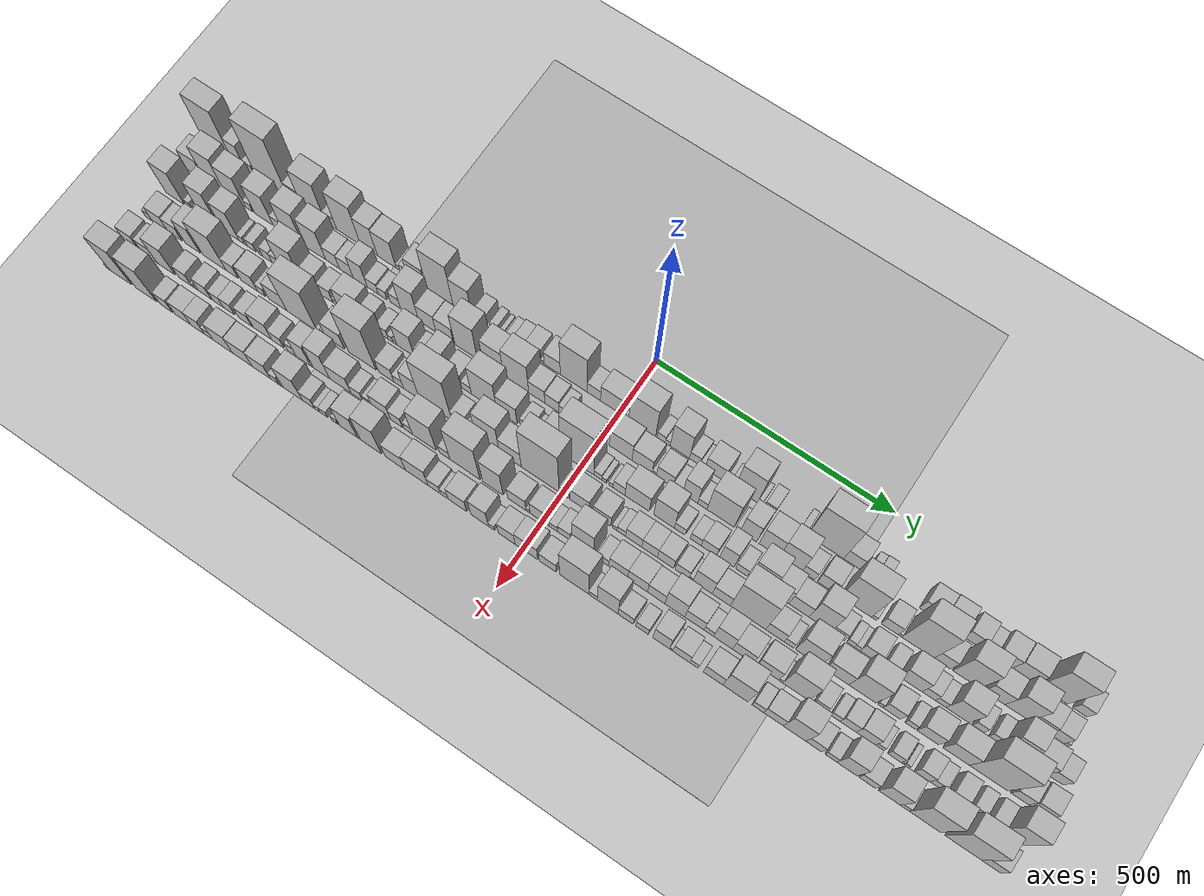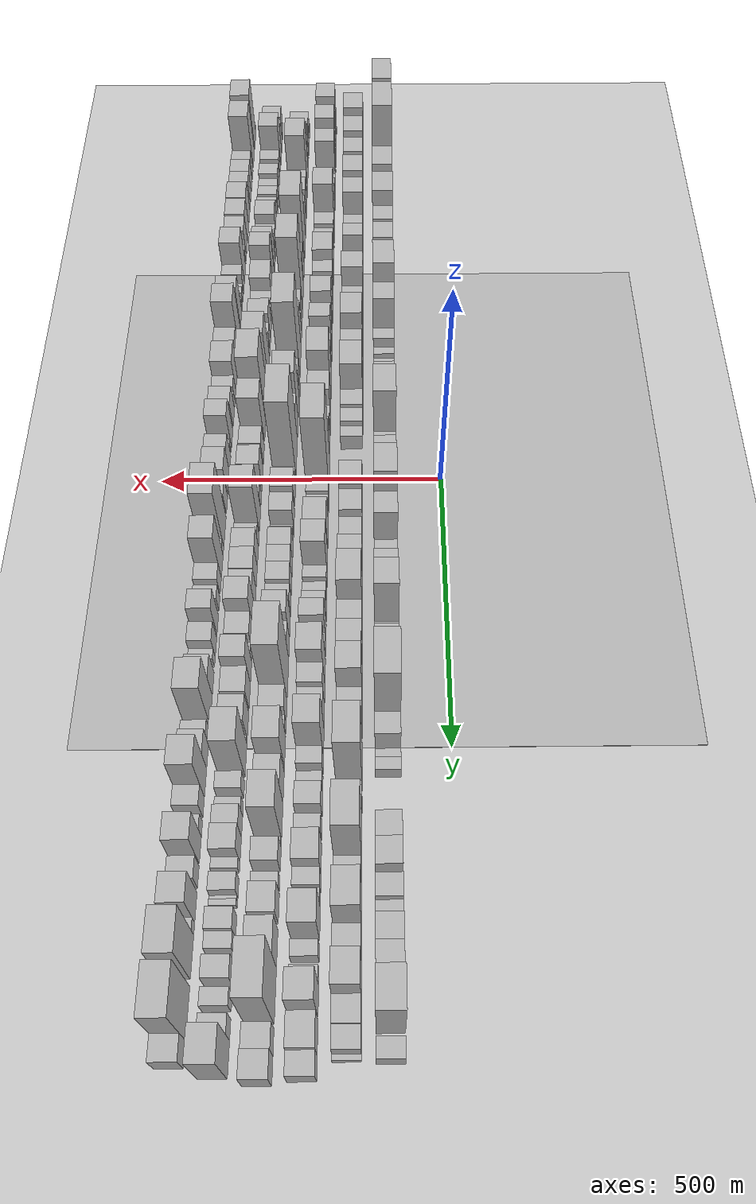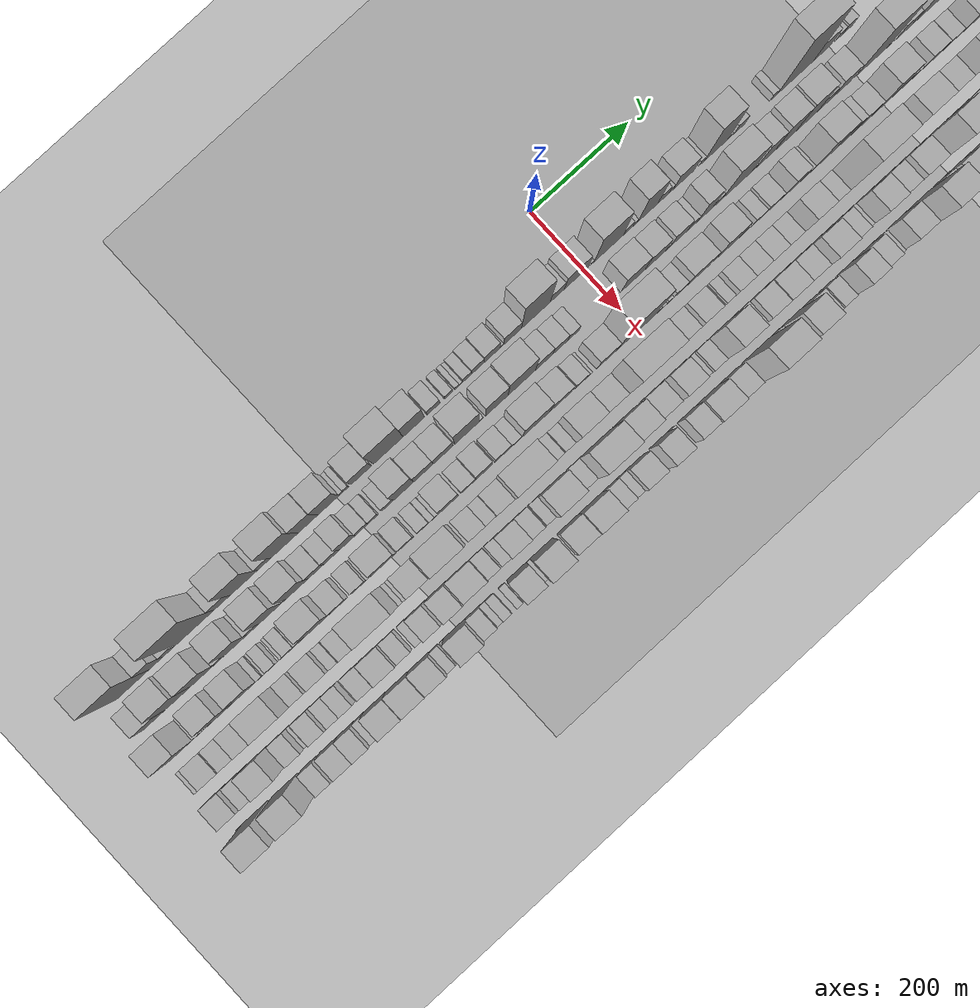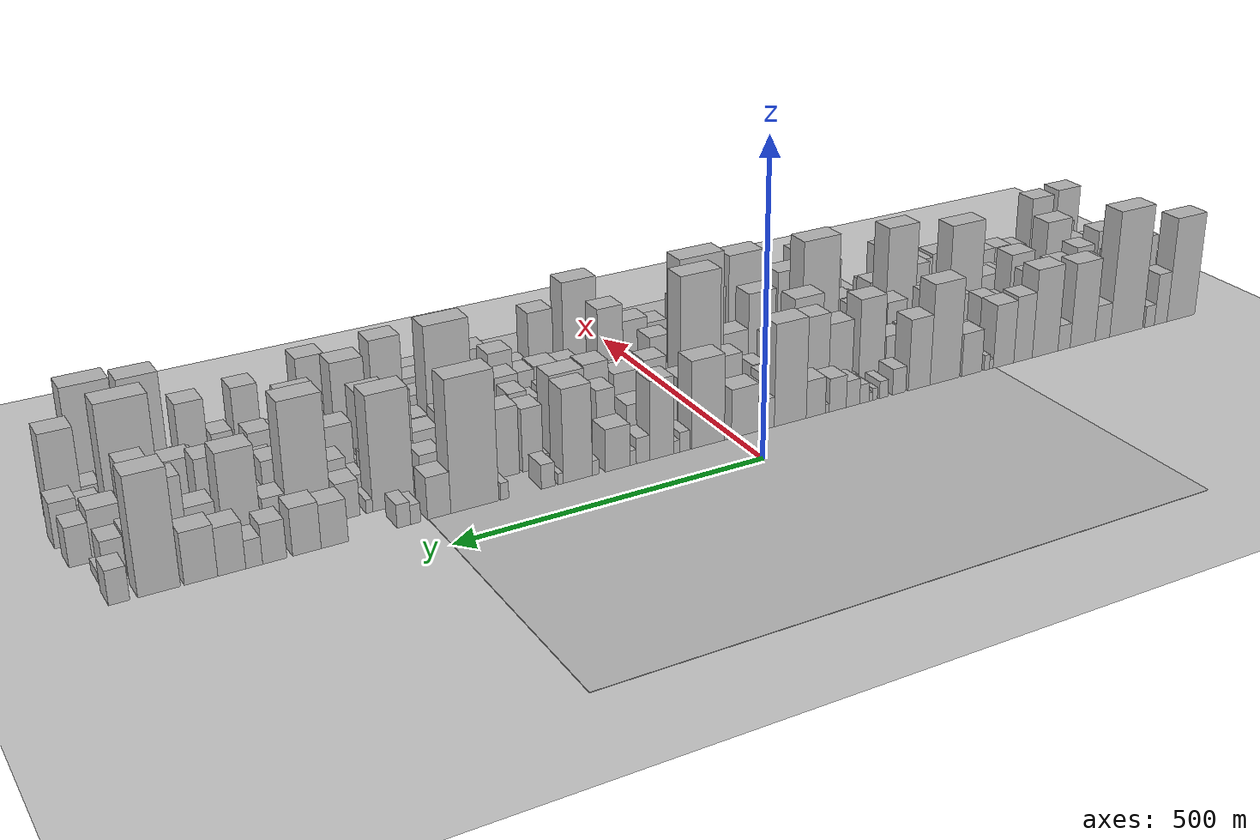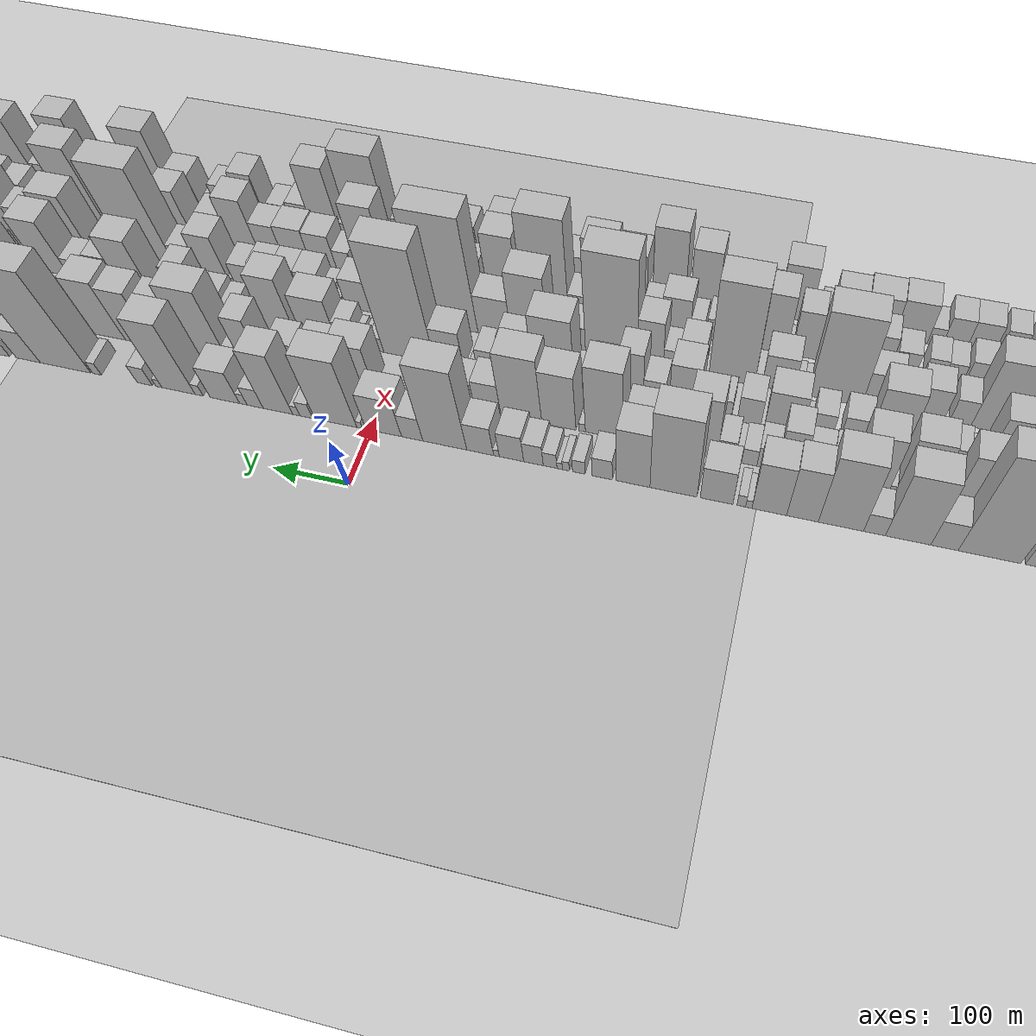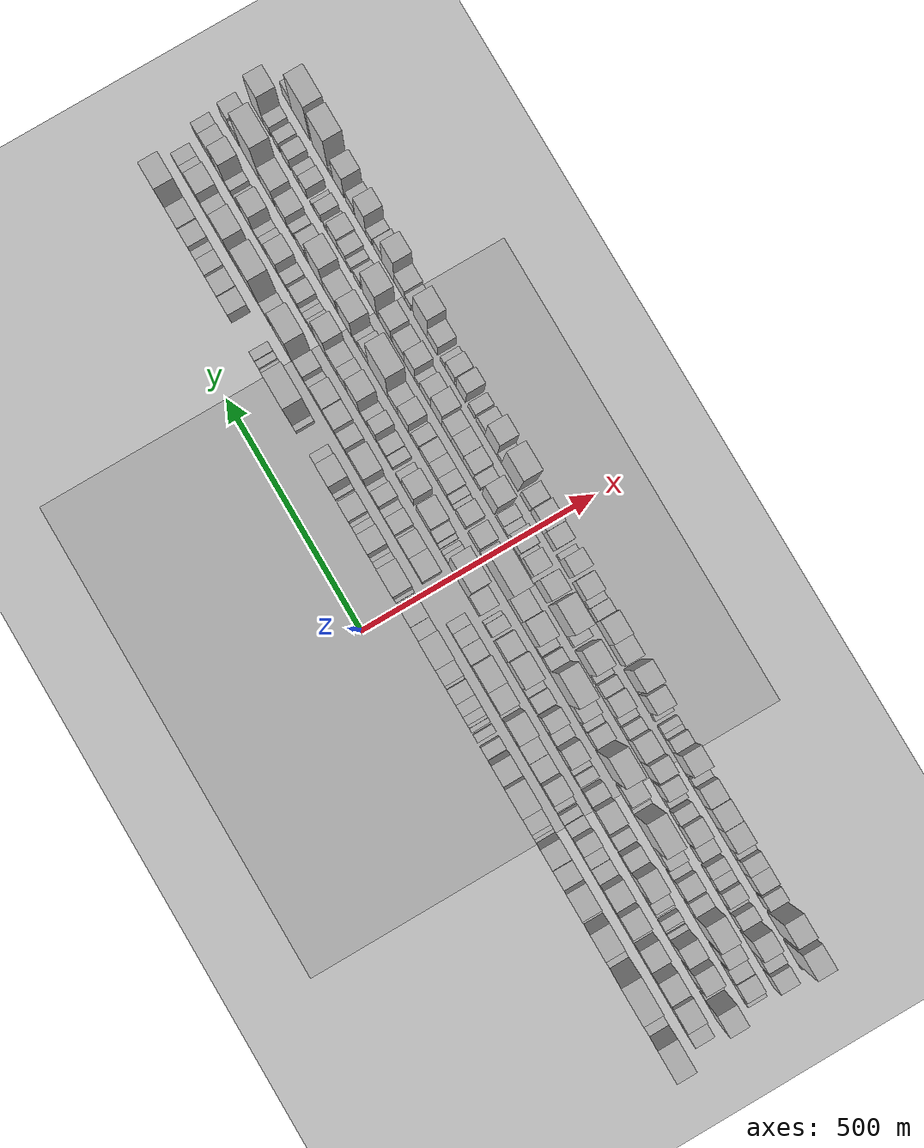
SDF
<?xml version="1.0" encoding="utf-8"?>

<sdf version="1.6">

   <world name="default">

      <gui fullscreen="0">

         <camera name="user_camera">

            <pose>-15 0 4.57585 0 0 0</pose>

            <view_controller>orbit</view_controller>

         </camera>

      </gui>

      <scene>

         <sky>

           <clouds>

             <speed>12</speed>

           </clouds>

         </sky>

         <ambient>0.4 0.4 0.4 1</ambient>

         <background>0.7 0.7 0.7 1</background>

         <shadows>1</shadows>

      </scene>

      <gravity>0 0 -9.8066</gravity>

      <magnetic_field>6e-06 2.3e-05 -4.2e-05</magnetic_field>

      <physics default="0" name="default_physics" type="ode">

         <ode>

            <solver>

               <type>quick</type>

               <iters>10</iters>

               <sor>1.0</sor>

               <use_dynamic_moi_rescaling>0</use_dynamic_moi_rescaling>

            </solver>

            <constraints>

               <cfm>0</cfm>

               <erp>0.2</erp>

               <contact_max_correcting_vel>100</contact_max_correcting_vel>

               <contact_surface_layer>0.001</contact_surface_layer>

            </constraints>

         </ode>

         <max_step_size>0.004</max_step_size>

         <real_time_factor>1</real_time_factor>

         <real_time_update_rate>250</real_time_update_rate>

      </physics>

      <light name="sun" type="directional">

         <cast_shadows>1</cast_shadows>

         <pose>0 0 10 0 0 0</pose>

         <diffuse>0.8 0.8 0.8 1</diffuse>

         <specular>0.2 0.2 0.2 1</specular>

         <attenuation>

            <range>1000</range>

            <constant>0.9</constant>

            <linear>0.01</linear>

            <quadratic>0.001</quadratic>

         </attenuation>

         <direction>-0.5 0.1 -0.9</direction>

      </light>

      <include>

         <name>ground_plane_1</name>

         <uri>model://HANNAS_ground_plane</uri>

         <pose>0 0 0  0 0 0</pose>

      </include>

      <include>

         <name>ground_plane_2</name>

         <uri>model://HANNAS_ground_plane</uri>

         <pose>100 0 0  0 0 0</pose>

      </include>

      <model name="building_1">

         <static>1</static>

         <pose frame="">100.0000 -907.5828 0 0.000000 0.000000 0.000000</pose>

         <link name="link">

            <pose frame="">0 0 94.50 0 0 0</pose>

            <collision name="collision">

               <geometry>

                  <box>

                     <size>40.0000 64.8345 189.0000</size>

                  </box>

               </geometry>

               <max_contacts>10</max_contacts>

               <surface>

                  <contact>

                     <ode/>

                  </contact>

                  <bounce/>

                  <friction>

                     <torsional>

                        <ode/>

                     </torsional>

                     <ode/>

                  </friction>

               </surface>

            </collision>

            <visual name="visual">

               <cast_shadows>0</cast_shadows>

               <geometry>

                  <box>

                     <size>40.0000 64.8345 189.0000</size>

                  </box>

               </geometry>

               <material>

                  <script>

                     <uri>model://HANNAS_wall/materials/scripts</uri>

                     <uri>model://HANNAS_wall/materials/textures</uri>

                     <name>vrc/HANNAS_wall</name>

                  </script>

               </material>

            </visual>

            <self_collide>0</self_collide>

            <enable_wind>0</enable_wind>

            <kinematic>0</kinematic>

         </link>

      </model>

      <model name="building_2">

         <static>1</static>

         <pose frame="">100.0000 -860.6660 0 0.000000 0.000000 0.000000</pose>

         <link name="link">

            <pose frame="">0 0 46.50 0 0 0</pose>

            <collision name="collision">

               <geometry>

                  <box>

                     <size>40.0000 28.9990 93.0000</size>

                  </box>

               </geometry>

               <max_contacts>10</max_contacts>

               <surface>

                  <contact>

                     <ode/>

                  </contact>

                  <bounce/>

                  <friction>

                     <torsional>

                        <ode/>

                     </torsional>

                     <ode/>

                  </friction>

               </surface>

            </collision>

            <visual name="visual">

               <cast_shadows>0</cast_shadows>

               <geometry>

                  <box>

                     <size>40.0000 28.9990 93.0000</size>

                  </box>

               </geometry>

               <material>

                  <script>

                     <uri>model://HANNAS_wall/materials/scripts</uri>

                     <uri>model://HANNAS_wall/materials/textures</uri>

                     <name>vrc/HANNAS_wall</name>

                  </script>

               </material>

            </visual>

            <self_collide>0</self_collide>

            <enable_wind>0</enable_wind>

            <kinematic>0</kinematic>

         </link>

      </model>

      <model name="building_3">

         <static>1</static>

         <pose frame="">100.0000 -835.2221 0 0.000000 0.000000 0.000000</pose>

         <link name="link">

            <pose frame="">0 0 19.50 0 0 0</pose>

            <collision name="collision">

               <geometry>

                  <box>

                     <size>40.0000 21.8888 39.0000</size>

                  </box>

               </geometry>

               <max_contacts>10</max_contacts>

               <surface>

                  <contact>

                     <ode/>

                  </contact>

                  <bounce/>

                  <friction>

                     <torsional>

                        <ode/>

                     </torsional>

                     <ode/>

                  </friction>

               </surface>

            </collision>

            <visual name="visual">

               <cast_shadows>0</cast_shadows>

               <geometry>

                  <box>

                     <size>40.0000 21.8888 39.0000</size>

                  </box>

               </geometry>

               <material>

                  <script>

                     <uri>model://HANNAS_wall/materials/scripts</uri>

                     <uri>model://HANNAS_wall/materials/textures</uri>

                     <name>vrc/HANNAS_wall</name>

                  </script>

               </material>

            </visual>

            <self_collide>0</self_collide>

            <enable_wind>0</enable_wind>

            <kinematic>0</kinematic>

         </link>

      </model>

      <model name="building_4">

         <static>1</static>

         <pose frame="">100.0000 -782.2124 0 0.000000 0.000000 0.000000</pose>

         <link name="link">

            <pose frame="">0 0 112.50 0 0 0</pose>

            <collision name="collision">

               <geometry>

                  <box>

                     <size>40.0000 74.1306 225.0000</size>

                  </box>

               </geometry>

               <max_contacts>10</max_contacts>

               <surface>

                  <contact>

                     <ode/>

                  </contact>

                  <bounce/>

                  <friction>

                     <torsional>

                        <ode/>

                     </torsional>

                     <ode/>

                  </friction>

               </surface>

            </collision>

            <visual name="visual">

               <cast_shadows>0</cast_shadows>

               <geometry>

                  <box>

                     <size>40.0000 74.1306 225.0000</size>

                  </box>

               </geometry>

               <material>

                  <script>

                     <uri>model://HANNAS_wall/materials/scripts</uri>

                     <uri>model://HANNAS_wall/materials/textures</uri>

                     <name>vrc/HANNAS_wall</name>

                  </script>

               </material>

            </visual>

            <self_collide>0</self_collide>

            <enable_wind>0</enable_wind>

            <kinematic>0</kinematic>

         </link>

      </model>

      <model name="building_5">

         <static>1</static>

         <pose frame="">100.0000 -728.9283 0 0.000000 0.000000 0.000000</pose>

         <link name="link">

            <pose frame="">0 0 31.50 0 0 0</pose>

            <collision name="collision">

               <geometry>

                  <box>

                     <size>40.0000 32.4376 63.0000</size>

                  </box>

               </geometry>

               <max_contacts>10</max_contacts>

               <surface>

                  <contact>

                     <ode/>

                  </contact>

                  <bounce/>

                  <friction>

                     <torsional>

                        <ode/>

                     </torsional>

                     <ode/>

                  </friction>

               </surface>

            </collision>

            <visual name="visual">

               <cast_shadows>0</cast_shadows>

               <geometry>

                  <box>

                     <size>40.0000 32.4376 63.0000</size>

                  </box>

               </geometry>

               <material>

                  <script>

                     <uri>model://HANNAS_wall/materials/scripts</uri>

                     <uri>model://HANNAS_wall/materials/textures</uri>

                     <name>vrc/HANNAS_wall</name>

                  </script>

               </material>

            </visual>

            <self_collide>0</self_collide>

            <enable_wind>0</enable_wind>

            <kinematic>0</kinematic>

         </link>

      </model>

      <model name="building_6">

         <static>1</static>

         <pose frame="">100.0000 -685.4064 0 0.000000 0.000000 0.000000</pose>

         <link name="link">

            <pose frame="">0 0 75.00 0 0 0</pose>

            <collision name="collision">

               <geometry>

                  <box>

                     <size>40.0000 54.6061 150.0000</size>

                  </box>

               </geometry>

               <max_contacts>10</max_contacts>

               <surface>

                  <contact>

                     <ode/>

                  </contact>

                  <bounce/>

                  <friction>

                     <torsional>

                        <ode/>

                     </torsional>

                     <ode/>

                  </friction>

               </surface>

            </collision>

            <visual name="visual">

               <cast_shadows>0</cast_shadows>

               <geometry>

                  <box>

                     <size>40.0000 54.6061 150.0000</size>

                  </box>

               </geometry>

               <material>

                  <script>

                     <uri>model://HANNAS_wall/materials/scripts</uri>

                     <uri>model://HANNAS_wall/materials/textures</uri>

                     <name>vrc/HANNAS_wall</name>

                  </script>

               </material>

            </visual>

            <self_collide>0</self_collide>

            <enable_wind>0</enable_wind>

            <kinematic>0</kinematic>

         </link>

      </model>

      <model name="building_7">

         <static>1</static>

         <pose frame="">100.0000 -644.9098 0 0.000000 0.000000 0.000000</pose>

         <link name="link">

            <pose frame="">0 0 22.50 0 0 0</pose>

            <collision name="collision">

               <geometry>

                  <box>

                     <size>40.0000 26.3871 45.0000</size>

                  </box>

               </geometry>

               <max_contacts>10</max_contacts>

               <surface>

                  <contact>

                     <ode/>

                  </contact>

                  <bounce/>

                  <friction>

                     <torsional>

                        <ode/>

                     </torsional>

                     <ode/>

                  </friction>

               </surface>

            </collision>

            <visual name="visual">

               <cast_shadows>0</cast_shadows>

               <geometry>

                  <box>

                     <size>40.0000 26.3871 45.0000</size>

                  </box>

               </geometry>

               <material>

                  <script>

                     <uri>model://HANNAS_wall/materials/scripts</uri>

                     <uri>model://HANNAS_wall/materials/textures</uri>

                     <name>vrc/HANNAS_wall</name>

                  </script>

               </material>

            </visual>

            <self_collide>0</self_collide>

            <enable_wind>0</enable_wind>

            <kinematic>0</kinematic>

         </link>

      </model>

      <model name="building_8">

         <static>1</static>

         <pose frame="">100.0000 -604.1394 0 0.000000 0.000000 0.000000</pose>

         <link name="link">

            <pose frame="">0 0 78.00 0 0 0</pose>

            <collision name="collision">

               <geometry>

                  <box>

                     <size>40.0000 55.1538 156.0000</size>

                  </box>

               </geometry>

               <max_contacts>10</max_contacts>

               <surface>

                  <contact>

                     <ode/>

                  </contact>

                  <bounce/>

                  <friction>

                     <torsional>

                        <ode/>

                     </torsional>

                     <ode/>

                  </friction>

               </surface>

            </collision>

            <visual name="visual">

               <cast_shadows>0</cast_shadows>

               <geometry>

                  <box>

                     <size>40.0000 55.1538 156.0000</size>

                  </box>

               </geometry>

               <material>

                  <script>

                     <uri>model://HANNAS_wall/materials/scripts</uri>

                     <uri>model://HANNAS_wall/materials/textures</uri>

                     <name>vrc/HANNAS_wall</name>

                  </script>

               </material>

            </visual>

            <self_collide>0</self_collide>

            <enable_wind>0</enable_wind>

            <kinematic>0</kinematic>

         </link>

      </model>

      <model name="building_9">

         <static>1</static>

         <pose frame="">100.0000 -557.1358 0 0.000000 0.000000 0.000000</pose>

         <link name="link">

            <pose frame="">0 0 58.50 0 0 0</pose>

            <collision name="collision">

               <geometry>

                  <box>

                     <size>40.0000 38.8533 117.0000</size>

                  </box>

               </geometry>

               <max_contacts>10</max_contacts>

               <surface>

                  <contact>

                     <ode/>

                  </contact>

                  <bounce/>

                  <friction>

                     <torsional>

                        <ode/>

                     </torsional>

                     <ode/>

                  </friction>

               </surface>

            </collision>

            <visual name="visual">

               <cast_shadows>0</cast_shadows>

               <geometry>

                  <box>

                     <size>40.0000 38.8533 117.0000</size>

                  </box>

               </geometry>

               <material>

                  <script>

                     <uri>model://HANNAS_wall/materials/scripts</uri>

                     <uri>model://HANNAS_wall/materials/textures</uri>

                     <name>vrc/HANNAS_wall</name>

                  </script>

               </material>

            </visual>

            <self_collide>0</self_collide>

            <enable_wind>0</enable_wind>

            <kinematic>0</kinematic>

         </link>

      </model>

      <model name="building_10">

         <static>1</static>

         <pose frame="">100.0000 -516.2631 0 0.000000 0.000000 0.000000</pose>

         <link name="link">

            <pose frame="">0 0 55.50 0 0 0</pose>

            <collision name="collision">

               <geometry>

                  <box>

                     <size>40.0000 42.8921 111.0000</size>

                  </box>

               </geometry>

               <max_contacts>10</max_contacts>

               <surface>

                  <contact>

                     <ode/>

                  </contact>

                  <bounce/>

                  <friction>

                     <torsional>

                        <ode/>

                     </torsional>

                     <ode/>

                  </friction>

               </surface>

            </collision>

            <visual name="visual">

               <cast_shadows>0</cast_shadows>

               <geometry>

                  <box>

                     <size>40.0000 42.8921 111.0000</size>

                  </box>

               </geometry>

               <material>

                  <script>

                     <uri>model://HANNAS_wall/materials/scripts</uri>

                     <uri>model://HANNAS_wall/materials/textures</uri>

                     <name>vrc/HANNAS_wall</name>

                  </script>

               </material>

            </visual>

            <self_collide>0</self_collide>

            <enable_wind>0</enable_wind>

            <kinematic>0</kinematic>

         </link>

      </model>

      <model name="building_11">

         <static>1</static>

         <pose frame="">100.0000 -490.8703 0 0.000000 0.000000 0.000000</pose>

         <link name="link">

            <pose frame="">0 0 9.00 0 0 0</pose>

            <collision name="collision">

               <geometry>

                  <box>

                     <size>40.0000 7.8936 18.0000</size>

                  </box>

               </geometry>

               <max_contacts>10</max_contacts>

               <surface>

                  <contact>

                     <ode/>

                  </contact>

                  <bounce/>

                  <friction>

                     <torsional>

                        <ode/>

                     </torsional>

                     <ode/>

                  </friction>

               </surface>

            </collision>

            <visual name="visual">

               <cast_shadows>0</cast_shadows>

               <geometry>

                  <box>

                     <size>40.0000 7.8936 18.0000</size>

                  </box>

               </geometry>

               <material>

                  <script>

                     <uri>model://HANNAS_wall/materials/scripts</uri>

                     <uri>model://HANNAS_wall/materials/textures</uri>

                     <name>vrc/HANNAS_wall</name>

                  </script>

               </material>

            </visual>

            <self_collide>0</self_collide>

            <enable_wind>0</enable_wind>

            <kinematic>0</kinematic>

         </link>

      </model>

      <model name="building_12">

         <static>1</static>

         <pose frame="">100.0000 -481.5150 0 0.000000 0.000000 0.000000</pose>

         <link name="link">

            <pose frame="">0 0 13.50 0 0 0</pose>

            <collision name="collision">

               <geometry>

                  <box>

                     <size>40.0000 10.8168 27.0000</size>

                  </box>

               </geometry>

               <max_contacts>10</max_contacts>

               <surface>

                  <contact>

                     <ode/>

                  </contact>

                  <bounce/>

                  <friction>

                     <torsional>

                        <ode/>

                     </torsional>

                     <ode/>

                  </friction>

               </surface>

            </collision>

            <visual name="visual">

               <cast_shadows>0</cast_shadows>

               <geometry>

                  <box>

                     <size>40.0000 10.8168 27.0000</size>

                  </box>

               </geometry>

               <material>

                  <script>

                     <uri>model://HANNAS_wall/materials/scripts</uri>

                     <uri>model://HANNAS_wall/materials/textures</uri>

                     <name>vrc/HANNAS_wall</name>

                  </script>

               </material>

            </visual>

            <self_collide>0</self_collide>

            <enable_wind>0</enable_wind>

            <kinematic>0</kinematic>

         </link>

      </model>

      <model name="building_13">

         <static>1</static>

         <pose frame="">100.0000 -450.6079 0 0.000000 0.000000 0.000000</pose>

         <link name="link">

            <pose frame="">0 0 37.50 0 0 0</pose>

            <collision name="collision">

               <geometry>

                  <box>

                     <size>40.0000 40.9975 75.0000</size>

                  </box>

               </geometry>

               <max_contacts>10</max_contacts>

               <surface>

                  <contact>

                     <ode/>

                  </contact>

                  <bounce/>

                  <friction>

                     <torsional>

                        <ode/>

                     </torsional>

                     <ode/>

                  </friction>

               </surface>

            </collision>

            <visual name="visual">

               <cast_shadows>0</cast_shadows>

               <geometry>

                  <box>

                     <size>40.0000 40.9975 75.0000</size>

                  </box>

               </geometry>

               <material>

                  <script>

                     <uri>model://HANNAS_wall/materials/scripts</uri>

                     <uri>model://HANNAS_wall/materials/textures</uri>

                     <name>vrc/HANNAS_wall</name>

                  </script>

               </material>

            </visual>

            <self_collide>0</self_collide>

            <enable_wind>0</enable_wind>

            <kinematic>0</kinematic>

         </link>

      </model>

      <model name="building_14">

         <static>1</static>

         <pose frame="">100.0000 -396.3436 0 0.000000 0.000000 0.000000</pose>

         <link name="link">

            <pose frame="">0 0 87.00 0 0 0</pose>

            <collision name="collision">

               <geometry>

                  <box>

                     <size>40.0000 59.5311 174.0000</size>

                  </box>

               </geometry>

               <max_contacts>10</max_contacts>

               <surface>

                  <contact>

                     <ode/>

                  </contact>

                  <bounce/>

                  <friction>

                     <torsional>

                        <ode/>

                     </torsional>

                     <ode/>

                  </friction>

               </surface>

            </collision>

            <visual name="visual">

               <cast_shadows>0</cast_shadows>

               <geometry>

                  <box>

                     <size>40.0000 59.5311 174.0000</size>

                  </box>

               </geometry>

               <material>

                  <script>

                     <uri>model://HANNAS_wall/materials/scripts</uri>

                     <uri>model://HANNAS_wall/materials/textures</uri>

                     <name>vrc/HANNAS_wall</name>

                  </script>

               </material>

            </visual>

            <self_collide>0</self_collide>

            <enable_wind>0</enable_wind>

            <kinematic>0</kinematic>

         </link>

      </model>

      <model name="building_15">

         <static>1</static>

         <pose frame="">100.0000 -345.0604 0 0.000000 0.000000 0.000000</pose>

         <link name="link">

            <pose frame="">0 0 61.50 0 0 0</pose>

            <collision name="collision">

               <geometry>

                  <box>

                     <size>40.0000 43.0352 123.0000</size>

                  </box>

               </geometry>

               <max_contacts>10</max_contacts>

               <surface>

                  <contact>

                     <ode/>

                  </contact>

                  <bounce/>

                  <friction>

                     <torsional>

                        <ode/>

                     </torsional>

                     <ode/>

                  </friction>

               </surface>

            </collision>

            <visual name="visual">

               <cast_shadows>0</cast_shadows>

               <geometry>

                  <box>

                     <size>40.0000 43.0352 123.0000</size>

                  </box>

               </geometry>

               <material>

                  <script>

                     <uri>model://HANNAS_wall/materials/scripts</uri>

                     <uri>model://HANNAS_wall/materials/textures</uri>

                     <name>vrc/HANNAS_wall</name>

                  </script>

               </material>

            </visual>

            <self_collide>0</self_collide>

            <enable_wind>0</enable_wind>

            <kinematic>0</kinematic>

         </link>

      </model>

      <model name="building_16">

         <static>1</static>

         <pose frame="">100.0000 -305.5675 0 0.000000 0.000000 0.000000</pose>

         <link name="link">

            <pose frame="">0 0 22.50 0 0 0</pose>

            <collision name="collision">

               <geometry>

                  <box>

                     <size>40.0000 25.9506 45.0000</size>

                  </box>

               </geometry>

               <max_contacts>10</max_contacts>

               <surface>

                  <contact>

                     <ode/>

                  </contact>

                  <bounce/>

                  <friction>

                     <torsional>

                        <ode/>

                     </torsional>

                     <ode/>

                  </friction>

               </surface>

            </collision>

            <visual name="visual">

               <cast_shadows>0</cast_shadows>

               <geometry>

                  <box>

                     <size>40.0000 25.9506 45.0000</size>

                  </box>

               </geometry>

               <material>

                  <script>

                     <uri>model://HANNAS_wall/materials/scripts</uri>

                     <uri>model://HANNAS_wall/materials/textures</uri>

                     <name>vrc/HANNAS_wall</name>

                  </script>

               </material>

            </visual>

            <self_collide>0</self_collide>

            <enable_wind>0</enable_wind>

            <kinematic>0</kinematic>

         </link>

      </model>

      <model name="building_17">

         <static>1</static>

         <pose frame="">100.0000 -275.4437 0 0.000000 0.000000 0.000000</pose>

         <link name="link">

            <pose frame="">0 0 15.00 0 0 0</pose>

            <collision name="collision">

               <geometry>

                  <box>

                     <size>40.0000 16.2969 30.0000</size>

                  </box>

               </geometry>

               <max_contacts>10</max_contacts>

               <surface>

                  <contact>

                     <ode/>

                  </contact>

                  <bounce/>

                  <friction>

                     <torsional>

                        <ode/>

                     </torsional>

                     <ode/>

                  </friction>

               </surface>

            </collision>

            <visual name="visual">

               <cast_shadows>0</cast_shadows>

               <geometry>

                  <box>

                     <size>40.0000 16.2969 30.0000</size>

                  </box>

               </geometry>

               <material>

                  <script>

                     <uri>model://HANNAS_wall/materials/scripts</uri>

                     <uri>model://HANNAS_wall/materials/textures</uri>

                     <name>vrc/HANNAS_wall</name>

                  </script>

               </material>

            </visual>

            <self_collide>0</self_collide>

            <enable_wind>0</enable_wind>

            <kinematic>0</kinematic>

         </link>

      </model>

      <model name="building_18">

         <static>1</static>

         <pose frame="">100.0000 -258.7932 0 0.000000 0.000000 0.000000</pose>

         <link name="link">

            <pose frame="">0 0 10.50 0 0 0</pose>

            <collision name="collision">

               <geometry>

                  <box>

                     <size>40.0000 9.0042 21.0000</size>

                  </box>

               </geometry>

               <max_contacts>10</max_contacts>

               <surface>

                  <contact>

                     <ode/>

                  </contact>

                  <bounce/>

                  <friction>

                     <torsional>

                        <ode/>

                     </torsional>

                     <ode/>

                  </friction>

               </surface>

            </collision>

            <visual name="visual">

               <cast_shadows>0</cast_shadows>

               <geometry>

                  <box>

                     <size>40.0000 9.0042 21.0000</size>

                  </box>

               </geometry>

               <material>

                  <script>

                     <uri>model://HANNAS_wall/materials/scripts</uri>

                     <uri>model://HANNAS_wall/materials/textures</uri>

                     <name>vrc/HANNAS_wall</name>

                  </script>

               </material>

            </visual>

            <self_collide>0</self_collide>

            <enable_wind>0</enable_wind>

            <kinematic>0</kinematic>

         </link>

      </model>

      <model name="building_19">

         <static>1</static>

         <pose frame="">100.0000 -250.7659 0 0.000000 0.000000 0.000000</pose>

         <link name="link">

            <pose frame="">0 0 7.50 0 0 0</pose>

            <collision name="collision">

               <geometry>

                  <box>

                     <size>40.0000 7.0503 15.0000</size>

                  </box>

               </geometry>

               <max_contacts>10</max_contacts>

               <surface>

                  <contact>

                     <ode/>

                  </contact>

                  <bounce/>

                  <friction>

                     <torsional>

                        <ode/>

                     </torsional>

                     <ode/>

                  </friction>

               </surface>

            </collision>

            <visual name="visual">

               <cast_shadows>0</cast_shadows>

               <geometry>

                  <box>

                     <size>40.0000 7.0503 15.0000</size>

                  </box>

               </geometry>

               <material>

                  <script>

                     <uri>model://HANNAS_wall/materials/scripts</uri>

                     <uri>model://HANNAS_wall/materials/textures</uri>

                     <name>vrc/HANNAS_wall</name>

                  </script>

               </material>

            </visual>

            <self_collide>0</self_collide>

            <enable_wind>0</enable_wind>

            <kinematic>0</kinematic>

         </link>

      </model>

      <model name="building_20">

         <static>1</static>

         <pose frame="">100.0000 -238.3078 0 0.000000 0.000000 0.000000</pose>

         <link name="link">

            <pose frame="">0 0 16.50 0 0 0</pose>

            <collision name="collision">

               <geometry>

                  <box>

                     <size>40.0000 17.8659 33.0000</size>

                  </box>

               </geometry>

               <max_contacts>10</max_contacts>

               <surface>

                  <contact>

                     <ode/>

                  </contact>

                  <bounce/>

                  <friction>

                     <torsional>

                        <ode/>

                     </torsional>

                     <ode/>

                  </friction>

               </surface>

            </collision>

            <visual name="visual">

               <cast_shadows>0</cast_shadows>

               <geometry>

                  <box>

                     <size>40.0000 17.8659 33.0000</size>

                  </box>

               </geometry>

               <material>

                  <script>

                     <uri>model://HANNAS_wall/materials/scripts</uri>

                     <uri>model://HANNAS_wall/materials/textures</uri>

                     <name>vrc/HANNAS_wall</name>

                  </script>

               </material>

            </visual>

            <self_collide>0</self_collide>

            <enable_wind>0</enable_wind>

            <kinematic>0</kinematic>

         </link>

      </model>

      <model name="building_21">

         <static>1</static>

         <pose frame="">100.0000 -216.5910 0 0.000000 0.000000 0.000000</pose>

         <link name="link">

            <pose frame="">0 0 22.50 0 0 0</pose>

            <collision name="collision">

               <geometry>

                  <box>

                     <size>40.0000 25.5679 45.0000</size>

                  </box>

               </geometry>

               <max_contacts>10</max_contacts>

               <surface>

                  <contact>

                     <ode/>

                  </contact>

                  <bounce/>

                  <friction>

                     <torsional>

                        <ode/>

                     </torsional>

                     <ode/>

                  </friction>

               </surface>

            </collision>

            <visual name="visual">

               <cast_shadows>0</cast_shadows>

               <geometry>

                  <box>

                     <size>40.0000 25.5679 45.0000</size>

                  </box>

               </geometry>

               <material>

                  <script>

                     <uri>model://HANNAS_wall/materials/scripts</uri>

                     <uri>model://HANNAS_wall/materials/textures</uri>

                     <name>vrc/HANNAS_wall</name>

                  </script>

               </material>

            </visual>

            <self_collide>0</self_collide>

            <enable_wind>0</enable_wind>

            <kinematic>0</kinematic>

         </link>

      </model>

      <model name="building_22">

         <static>1</static>

         <pose frame="">100.0000 -187.7423 0 0.000000 0.000000 0.000000</pose>

         <link name="link">

            <pose frame="">0 0 28.50 0 0 0</pose>

            <collision name="collision">

               <geometry>

                  <box>

                     <size>40.0000 32.1295 57.0000</size>

                  </box>

               </geometry>

               <max_contacts>10</max_contacts>

               <surface>

                  <contact>

                     <ode/>

                  </contact>

                  <bounce/>

                  <friction>

                     <torsional>

                        <ode/>

                     </torsional>

                     <ode/>

                  </friction>

               </surface>

            </collision>

            <visual name="visual">

               <cast_shadows>0</cast_shadows>

               <geometry>

                  <box>

                     <size>40.0000 32.1295 57.0000</size>

                  </box>

               </geometry>

               <material>

                  <script>

                     <uri>model://HANNAS_wall/materials/scripts</uri>

                     <uri>model://HANNAS_wall/materials/textures</uri>

                     <name>vrc/HANNAS_wall</name>

                  </script>

               </material>

            </visual>

            <self_collide>0</self_collide>

            <enable_wind>0</enable_wind>

            <kinematic>0</kinematic>

         </link>

      </model>

      <model name="building_23">

         <static>1</static>

         <pose frame="">100.0000 -168.0213 0 0.000000 0.000000 0.000000</pose>

         <link name="link">

            <pose frame="">0 0 7.50 0 0 0</pose>

            <collision name="collision">

               <geometry>

                  <box>

                     <size>40.0000 7.3126 15.0000</size>

                  </box>

               </geometry>

               <max_contacts>10</max_contacts>

               <surface>

                  <contact>

                     <ode/>

                  </contact>

                  <bounce/>

                  <friction>

                     <torsional>

                        <ode/>

                     </torsional>

                     <ode/>

                  </friction>

               </surface>

            </collision>

            <visual name="visual">

               <cast_shadows>0</cast_shadows>

               <geometry>

                  <box>

                     <size>40.0000 7.3126 15.0000</size>

                  </box>

               </geometry>

               <material>

                  <script>

                     <uri>model://HANNAS_wall/materials/scripts</uri>

                     <uri>model://HANNAS_wall/materials/textures</uri>

                     <name>vrc/HANNAS_wall</name>

                  </script>

               </material>

            </visual>

            <self_collide>0</self_collide>

            <enable_wind>0</enable_wind>

            <kinematic>0</kinematic>

         </link>

      </model>

      <model name="building_24">

         <static>1</static>

         <pose frame="">100.0000 -146.6382 0 0.000000 0.000000 0.000000</pose>

         <link name="link">

            <pose frame="">0 0 31.50 0 0 0</pose>

            <collision name="collision">

               <geometry>

                  <box>

                     <size>40.0000 35.4537 63.0000</size>

                  </box>

               </geometry>

               <max_contacts>10</max_contacts>

               <surface>

                  <contact>

                     <ode/>

                  </contact>

                  <bounce/>

                  <friction>

                     <torsional>

                        <ode/>

                     </torsional>

                     <ode/>

                  </friction>

               </surface>

            </collision>

            <visual name="visual">

               <cast_shadows>0</cast_shadows>

               <geometry>

                  <box>

                     <size>40.0000 35.4537 63.0000</size>

                  </box>

               </geometry>

               <material>

                  <script>

                     <uri>model://HANNAS_wall/materials/scripts</uri>

                     <uri>model://HANNAS_wall/materials/textures</uri>

                     <name>vrc/HANNAS_wall</name>

                  </script>

               </material>

            </visual>

            <self_collide>0</self_collide>

            <enable_wind>0</enable_wind>

            <kinematic>0</kinematic>

         </link>

      </model>

      <model name="building_25">

         <static>1</static>

         <pose frame="">100.0000 -99.6230 0 0.000000 0.000000 0.000000</pose>

         <link name="link">

            <pose frame="">0 0 85.50 0 0 0</pose>

            <collision name="collision">

               <geometry>

                  <box>

                     <size>40.0000 58.5766 171.0000</size>

                  </box>

               </geometry>

               <max_contacts>10</max_contacts>

               <surface>

                  <contact>

                     <ode/>

                  </contact>

                  <bounce/>

                  <friction>

                     <torsional>

                        <ode/>

                     </torsional>

                     <ode/>

                  </friction>

               </surface>

            </collision>

            <visual name="visual">

               <cast_shadows>0</cast_shadows>

               <geometry>

                  <box>

                     <size>40.0000 58.5766 171.0000</size>

                  </box>

               </geometry>

               <material>

                  <script>

                     <uri>model://HANNAS_wall/materials/scripts</uri>

                     <uri>model://HANNAS_wall/materials/textures</uri>

                     <name>vrc/HANNAS_wall</name>

                  </script>

               </material>

            </visual>

            <self_collide>0</self_collide>

            <enable_wind>0</enable_wind>

            <kinematic>0</kinematic>

         </link>

      </model>

      <model name="building_26">

         <static>1</static>

         <pose frame="">100.0000 -55.9826 0 0.000000 0.000000 0.000000</pose>

         <link name="link">

            <pose frame="">0 0 25.50 0 0 0</pose>

            <collision name="collision">

               <geometry>

                  <box>

                     <size>40.0000 28.7042 51.0000</size>

                  </box>

               </geometry>

               <max_contacts>10</max_contacts>

               <surface>

                  <contact>

                     <ode/>

                  </contact>

                  <bounce/>

                  <friction>

                     <torsional>

                        <ode/>

                     </torsional>

                     <ode/>

                  </friction>

               </surface>

            </collision>

            <visual name="visual">

               <cast_shadows>0</cast_shadows>

               <geometry>

                  <box>

                     <size>40.0000 28.7042 51.0000</size>

                  </box>

               </geometry>

               <material>

                  <script>

                     <uri>model://HANNAS_wall/materials/scripts</uri>

                     <uri>model://HANNAS_wall/materials/textures</uri>

                     <name>vrc/HANNAS_wall</name>

                  </script>

               </material>

            </visual>

            <self_collide>0</self_collide>

            <enable_wind>0</enable_wind>

            <kinematic>0</kinematic>

         </link>

      </model>

      <model name="building_27">

         <static>1</static>

         <pose frame="">100.0000 -17.5608 0 0.000000 0.000000 0.000000</pose>

         <link name="link">

            <pose frame="">0 0 40.50 0 0 0</pose>

            <collision name="collision">

               <geometry>

                  <box>

                     <size>40.0000 48.1394 81.0000</size>

                  </box>

               </geometry>

               <max_contacts>10</max_contacts>

               <surface>

                  <contact>

                     <ode/>

                  </contact>

                  <bounce/>

                  <friction>

                     <torsional>

                        <ode/>

                     </torsional>

                     <ode/>

                  </friction>

               </surface>

            </collision>

            <visual name="visual">

               <cast_shadows>0</cast_shadows>

               <geometry>

                  <box>

                     <size>40.0000 48.1394 81.0000</size>

                  </box>

               </geometry>

               <material>

                  <script>

                     <uri>model://HANNAS_wall/materials/scripts</uri>

                     <uri>model://HANNAS_wall/materials/textures</uri>

                     <name>vrc/HANNAS_wall</name>

                  </script>

               </material>

            </visual>

            <self_collide>0</self_collide>

            <enable_wind>0</enable_wind>

            <kinematic>0</kinematic>

         </link>

      </model>

      <model name="building_28">

         <static>1</static>

         <pose frame="">100.0000 15.1734 0 0.000000 0.000000 0.000000</pose>

         <link name="link">

            <pose frame="">0 0 7.50 0 0 0</pose>

            <collision name="collision">

               <geometry>

                  <box>

                     <size>40.0000 7.3290 15.0000</size>

                  </box>

               </geometry>

               <max_contacts>10</max_contacts>

               <surface>

                  <contact>

                     <ode/>

                  </contact>

                  <bounce/>

                  <friction>

                     <torsional>

                        <ode/>

                     </torsional>

                     <ode/>

                  </friction>

               </surface>

            </collision>

            <visual name="visual">

               <cast_shadows>0</cast_shadows>

               <geometry>

                  <box>

                     <size>40.0000 7.3290 15.0000</size>

                  </box>

               </geometry>

               <material>

                  <script>

                     <uri>model://HANNAS_wall/materials/scripts</uri>

                     <uri>model://HANNAS_wall/materials/textures</uri>

                     <name>vrc/HANNAS_wall</name>

                  </script>

               </material>

            </visual>

            <self_collide>0</self_collide>

            <enable_wind>0</enable_wind>

            <kinematic>0</kinematic>

         </link>

      </model>

      <model name="building_29">

         <static>1</static>

         <pose frame="">100.0000 47.6236 0 0.000000 0.000000 0.000000</pose>

         <link name="link">

            <pose frame="">0 0 72.00 0 0 0</pose>

            <collision name="collision">

               <geometry>

                  <box>

                     <size>40.0000 57.5713 144.0000</size>

                  </box>

               </geometry>

               <max_contacts>10</max_contacts>

               <surface>

                  <contact>

                     <ode/>

                  </contact>

                  <bounce/>

                  <friction>

                     <torsional>

                        <ode/>

                     </torsional>

                     <ode/>

                  </friction>

               </surface>

            </collision>

            <visual name="visual">

               <cast_shadows>0</cast_shadows>

               <geometry>

                  <box>

                     <size>40.0000 57.5713 144.0000</size>

                  </box>

               </geometry>

               <material>

                  <script>

                     <uri>model://HANNAS_wall/materials/scripts</uri>

                     <uri>model://HANNAS_wall/materials/textures</uri>

                     <name>vrc/HANNAS_wall</name>

                  </script>

               </material>

            </visual>

            <self_collide>0</self_collide>

            <enable_wind>0</enable_wind>

            <kinematic>0</kinematic>

         </link>

      </model>

      <model name="building_30">

         <static>1</static>

         <pose frame="">100.0000 88.2830 0 0.000000 0.000000 0.000000</pose>

         <link name="link">

            <pose frame="">0 0 16.50 0 0 0</pose>

            <collision name="collision">

               <geometry>

                  <box>

                     <size>40.0000 17.7475 33.0000</size>

                  </box>

               </geometry>

               <max_contacts>10</max_contacts>

               <surface>

                  <contact>

                     <ode/>

                  </contact>

                  <bounce/>

                  <friction>

                     <torsional>

                        <ode/>

                     </torsional>

                     <ode/>

                  </friction>

               </surface>

            </collision>

            <visual name="visual">

               <cast_shadows>0</cast_shadows>

               <geometry>

                  <box>

                     <size>40.0000 17.7475 33.0000</size>

                  </box>

               </geometry>

               <material>

                  <script>

                     <uri>model://HANNAS_wall/materials/scripts</uri>

                     <uri>model://HANNAS_wall/materials/textures</uri>

                     <name>vrc/HANNAS_wall</name>

                  </script>

               </material>

            </visual>

            <self_collide>0</self_collide>

            <enable_wind>0</enable_wind>

            <kinematic>0</kinematic>

         </link>

      </model>

      <model name="building_31">

         <static>1</static>

         <pose frame="">100.0000 102.1519 0 0.000000 0.000000 0.000000</pose>

         <link name="link">

            <pose frame="">0 0 10.50 0 0 0</pose>

            <collision name="collision">

               <geometry>

                  <box>

                     <size>40.0000 9.9901 21.0000</size>

                  </box>

               </geometry>

               <max_contacts>10</max_contacts>

               <surface>

                  <contact>

                     <ode/>

                  </contact>

                  <bounce/>

                  <friction>

                     <torsional>

                        <ode/>

                     </torsional>

                     <ode/>

                  </friction>

               </surface>

            </collision>

            <visual name="visual">

               <cast_shadows>0</cast_shadows>

               <geometry>

                  <box>

                     <size>40.0000 9.9901 21.0000</size>

                  </box>

               </geometry>

               <material>

                  <script>

                     <uri>model://HANNAS_wall/materials/scripts</uri>

                     <uri>model://HANNAS_wall/materials/textures</uri>

                     <name>vrc/HANNAS_wall</name>

                  </script>

               </material>

            </visual>

            <self_collide>0</self_collide>

            <enable_wind>0</enable_wind>

            <kinematic>0</kinematic>

         </link>

      </model>

      <model name="building_32">

         <static>1</static>

         <pose frame="">100.0000 127.4909 0 0.000000 0.000000 0.000000</pose>

         <link name="link">

            <pose frame="">0 0 64.50 0 0 0</pose>

            <collision name="collision">

               <geometry>

                  <box>

                     <size>40.0000 40.6880 129.0000</size>

                  </box>

               </geometry>

               <max_contacts>10</max_contacts>

               <surface>

                  <contact>

                     <ode/>

                  </contact>

                  <bounce/>

                  <friction>

                     <torsional>

                        <ode/>

                     </torsional>

                     <ode/>

                  </friction>

               </surface>

            </collision>

            <visual name="visual">

               <cast_shadows>0</cast_shadows>

               <geometry>

                  <box>

                     <size>40.0000 40.6880 129.0000</size>

                  </box>

               </geometry>

               <material>

                  <script>

                     <uri>model://HANNAS_wall/materials/scripts</uri>

                     <uri>model://HANNAS_wall/materials/textures</uri>

                     <name>vrc/HANNAS_wall</name>

                  </script>

               </material>

            </visual>

            <self_collide>0</self_collide>

            <enable_wind>0</enable_wind>

            <kinematic>0</kinematic>

         </link>

      </model>

      <model name="building_33">

         <static>1</static>

         <pose frame="">100.0000 159.1408 0 0.000000 0.000000 0.000000</pose>

         <link name="link">

            <pose frame="">0 0 21.00 0 0 0</pose>

            <collision name="collision">

               <geometry>

                  <box>

                     <size>40.0000 22.6117 42.0000</size>

                  </box>

               </geometry>

               <max_contacts>10</max_contacts>

               <surface>

                  <contact>

                     <ode/>

                  </contact>

                  <bounce/>

                  <friction>

                     <torsional>

                        <ode/>

                     </torsional>

                     <ode/>

                  </friction>

               </surface>

            </collision>

            <visual name="visual">

               <cast_shadows>0</cast_shadows>

               <geometry>

                  <box>

                     <size>40.0000 22.6117 42.0000</size>

                  </box>

               </geometry>

               <material>

                  <script>

                     <uri>model://HANNAS_wall/materials/scripts</uri>

                     <uri>model://HANNAS_wall/materials/textures</uri>

                     <name>vrc/HANNAS_wall</name>

                  </script>

               </material>

            </visual>

            <self_collide>0</self_collide>

            <enable_wind>0</enable_wind>

            <kinematic>0</kinematic>

         </link>

      </model>

      <model name="building_34">

         <static>1</static>

         <pose frame="">100.0000 175.5457 0 0.000000 0.000000 0.000000</pose>

         <link name="link">

            <pose frame="">0 0 12.00 0 0 0</pose>

            <collision name="collision">

               <geometry>

                  <box>

                     <size>40.0000 10.1981 24.0000</size>

                  </box>

               </geometry>

               <max_contacts>10</max_contacts>

               <surface>

                  <contact>

                     <ode/>

                  </contact>

                  <bounce/>

                  <friction>

                     <torsional>

                        <ode/>

                     </torsional>

                     <ode/>

                  </friction>

               </surface>

            </collision>

            <visual name="visual">

               <cast_shadows>0</cast_shadows>

               <geometry>

                  <box>

                     <size>40.0000 10.1981 24.0000</size>

                  </box>

               </geometry>

               <material>

                  <script>

                     <uri>model://HANNAS_wall/materials/scripts</uri>

                     <uri>model://HANNAS_wall/materials/textures</uri>

                     <name>vrc/HANNAS_wall</name>

                  </script>

               </material>

            </visual>

            <self_collide>0</self_collide>

            <enable_wind>0</enable_wind>

            <kinematic>0</kinematic>

         </link>

      </model>

      <model name="building_35">

         <static>1</static>

         <pose frame="">100.0000 201.3370 0 0.000000 0.000000 0.000000</pose>

         <link name="link">

            <pose frame="">0 0 34.50 0 0 0</pose>

            <collision name="collision">

               <geometry>

                  <box>

                     <size>40.0000 41.3843 69.0000</size>

                  </box>

               </geometry>

               <max_contacts>10</max_contacts>

               <surface>

                  <contact>

                     <ode/>

                  </contact>

                  <bounce/>

                  <friction>

                     <torsional>

                        <ode/>

                     </torsional>

                     <ode/>

                  </friction>

               </surface>

            </collision>

            <visual name="visual">

               <cast_shadows>0</cast_shadows>

               <geometry>

                  <box>

                     <size>40.0000 41.3843 69.0000</size>

                  </box>

               </geometry>

               <material>

                  <script>

                     <uri>model://HANNAS_wall/materials/scripts</uri>

                     <uri>model://HANNAS_wall/materials/textures</uri>

                     <name>vrc/HANNAS_wall</name>

                  </script>

               </material>

            </visual>

            <self_collide>0</self_collide>

            <enable_wind>0</enable_wind>

            <kinematic>0</kinematic>

         </link>

      </model>

      <model name="building_36">

         <static>1</static>

         <pose frame="">100.0000 237.6880 0 0.000000 0.000000 0.000000</pose>

         <link name="link">

            <pose frame="">0 0 12.00 0 0 0</pose>

            <collision name="collision">

               <geometry>

                  <box>

                     <size>40.0000 11.3178 24.0000</size>

                  </box>

               </geometry>

               <max_contacts>10</max_contacts>

               <surface>

                  <contact>

                     <ode/>

                  </contact>

                  <bounce/>

                  <friction>

                     <torsional>

                        <ode/>

                     </torsional>

                     <ode/>

                  </friction>

               </surface>

            </collision>

            <visual name="visual">

               <cast_shadows>0</cast_shadows>

               <geometry>

                  <box>

                     <size>40.0000 11.3178 24.0000</size>

                  </box>

               </geometry>

               <material>

                  <script>

                     <uri>model://HANNAS_wall/materials/scripts</uri>

                     <uri>model://HANNAS_wall/materials/textures</uri>

                     <name>vrc/HANNAS_wall</name>

                  </script>

               </material>

            </visual>

            <self_collide>0</self_collide>

            <enable_wind>0</enable_wind>

            <kinematic>0</kinematic>

         </link>

      </model>

      <model name="building_37">

         <static>1</static>

         <pose frame="">100.0000 266.9712 0 0.000000 0.000000 0.000000</pose>

         <link name="link">

            <pose frame="">0 0 75.00 0 0 0</pose>

            <collision name="collision">

               <geometry>

                  <box>

                     <size>40.0000 47.2485 150.0000</size>

                  </box>

               </geometry>

               <max_contacts>10</max_contacts>

               <surface>

                  <contact>

                     <ode/>

                  </contact>

                  <bounce/>

                  <friction>

                     <torsional>

                        <ode/>

                     </torsional>

                     <ode/>

                  </friction>

               </surface>

            </collision>

            <visual name="visual">

               <cast_shadows>0</cast_shadows>

               <geometry>

                  <box>

                     <size>40.0000 47.2485 150.0000</size>

                  </box>

               </geometry>

               <material>

                  <script>

                     <uri>model://HANNAS_wall/materials/scripts</uri>

                     <uri>model://HANNAS_wall/materials/textures</uri>

                     <name>vrc/HANNAS_wall</name>

                  </script>

               </material>

            </visual>

            <self_collide>0</self_collide>

            <enable_wind>0</enable_wind>

            <kinematic>0</kinematic>

         </link>

      </model>

      <model name="building_38">

         <static>1</static>

         <pose frame="">100.0000 294.8490 0 0.000000 0.000000 0.000000</pose>

         <link name="link">

            <pose frame="">0 0 9.00 0 0 0</pose>

            <collision name="collision">

               <geometry>

                  <box>

                     <size>40.0000 8.5072 18.0000</size>

                  </box>

               </geometry>

               <max_contacts>10</max_contacts>

               <surface>

                  <contact>

                     <ode/>

                  </contact>

                  <bounce/>

                  <friction>

                     <torsional>

                        <ode/>

                     </torsional>

                     <ode/>

                  </friction>

               </surface>

            </collision>

            <visual name="visual">

               <cast_shadows>0</cast_shadows>

               <geometry>

                  <box>

                     <size>40.0000 8.5072 18.0000</size>

                  </box>

               </geometry>

               <material>

                  <script>

                     <uri>model://HANNAS_wall/materials/scripts</uri>

                     <uri>model://HANNAS_wall/materials/textures</uri>

                     <name>vrc/HANNAS_wall</name>

                  </script>

               </material>

            </visual>

            <self_collide>0</self_collide>

            <enable_wind>0</enable_wind>

            <kinematic>0</kinematic>

         </link>

      </model>

      <model name="building_39">

         <static>1</static>

         <pose frame="">100.0000 315.0152 0 0.000000 0.000000 0.000000</pose>

         <link name="link">

            <pose frame="">0 0 19.50 0 0 0</pose>

            <collision name="collision">

               <geometry>

                  <box>

                     <size>40.0000 21.8251 39.0000</size>

                  </box>

               </geometry>

               <max_contacts>10</max_contacts>

               <surface>

                  <contact>

                     <ode/>

                  </contact>

                  <bounce/>

                  <friction>

                     <torsional>

                        <ode/>

                     </torsional>

                     <ode/>

                  </friction>

               </surface>

            </collision>

            <visual name="visual">

               <cast_shadows>0</cast_shadows>

               <geometry>

                  <box>

                     <size>40.0000 21.8251 39.0000</size>

                  </box>

               </geometry>

               <material>

                  <script>

                     <uri>model://HANNAS_wall/materials/scripts</uri>

                     <uri>model://HANNAS_wall/materials/textures</uri>

                     <name>vrc/HANNAS_wall</name>

                  </script>

               </material>

            </visual>

            <self_collide>0</self_collide>

            <enable_wind>0</enable_wind>

            <kinematic>0</kinematic>

         </link>

      </model>

      <model name="building_40">

         <static>1</static>

         <pose frame="">100.0000 383.6882 0 0.000000 0.000000 0.000000</pose>

         <link name="link">

            <pose frame="">0 0 13.50 0 0 0</pose>

            <collision name="collision">

               <geometry>

                  <box>

                     <size>40.0000 12.5069 27.0000</size>

                  </box>

               </geometry>

               <max_contacts>10</max_contacts>

               <surface>

                  <contact>

                     <ode/>

                  </contact>

                  <bounce/>

                  <friction>

                     <torsional>

                        <ode/>

                     </torsional>

                     <ode/>

                  </friction>

               </surface>

            </collision>

            <visual name="visual">

               <cast_shadows>0</cast_shadows>

               <geometry>

                  <box>

                     <size>40.0000 12.5069 27.0000</size>

                  </box>

               </geometry>

               <material>

                  <script>

                     <uri>model://HANNAS_wall/materials/scripts</uri>

                     <uri>model://HANNAS_wall/materials/textures</uri>

                     <name>vrc/HANNAS_wall</name>

                  </script>

               </material>

            </visual>

            <self_collide>0</self_collide>

            <enable_wind>0</enable_wind>

            <kinematic>0</kinematic>

         </link>

      </model>

      <model name="building_41">

         <static>1</static>

         <pose frame="">100.0000 429.8173 0 0.000000 0.000000 0.000000</pose>

         <link name="link">

            <pose frame="">0 0 103.50 0 0 0</pose>

            <collision name="collision">

               <geometry>

                  <box>

                     <size>40.0000 73.7513 207.0000</size>

                  </box>

               </geometry>

               <max_contacts>10</max_contacts>

               <surface>

                  <contact>

                     <ode/>

                  </contact>

                  <bounce/>

                  <friction>

                     <torsional>

                        <ode/>

                     </torsional>

                     <ode/>

                  </friction>

               </surface>

            </collision>

            <visual name="visual">

               <cast_shadows>0</cast_shadows>

               <geometry>

                  <box>

                     <size>40.0000 73.7513 207.0000</size>

                  </box>

               </geometry>

               <material>

                  <script>

                     <uri>model://HANNAS_wall/materials/scripts</uri>

                     <uri>model://HANNAS_wall/materials/textures</uri>

                     <name>vrc/HANNAS_wall</name>

                  </script>

               </material>

            </visual>

            <self_collide>0</self_collide>

            <enable_wind>0</enable_wind>

            <kinematic>0</kinematic>

         </link>

      </model>

      <model name="building_42">

         <static>1</static>

         <pose frame="">100.0000 484.3478 0 0.000000 0.000000 0.000000</pose>

         <link name="link">

            <pose frame="">0 0 33.00 0 0 0</pose>

            <collision name="collision">

               <geometry>

                  <box>

                     <size>40.0000 35.3099 66.0000</size>

                  </box>

               </geometry>

               <max_contacts>10</max_contacts>

               <surface>

                  <contact>

                     <ode/>

                  </contact>

                  <bounce/>

                  <friction>

                     <torsional>

                        <ode/>

                     </torsional>

                     <ode/>

                  </friction>

               </surface>

            </collision>

            <visual name="visual">

               <cast_shadows>0</cast_shadows>

               <geometry>

                  <box>

                     <size>40.0000 35.3099 66.0000</size>

                  </box>

               </geometry>

               <material>

                  <script>

                     <uri>model://HANNAS_wall/materials/scripts</uri>

                     <uri>model://HANNAS_wall/materials/textures</uri>

                     <name>vrc/HANNAS_wall</name>

                  </script>

               </material>

            </visual>

            <self_collide>0</self_collide>

            <enable_wind>0</enable_wind>

            <kinematic>0</kinematic>

         </link>

      </model>

      <model name="building_43">

         <static>1</static>

         <pose frame="">100.0000 519.5721 0 0.000000 0.000000 0.000000</pose>

         <link name="link">

            <pose frame="">0 0 15.00 0 0 0</pose>

            <collision name="collision">

               <geometry>

                  <box>

                     <size>40.0000 15.1387 30.0000</size>

                  </box>

               </geometry>

               <max_contacts>10</max_contacts>

               <surface>

                  <contact>

                     <ode/>

                  </contact>

                  <bounce/>

                  <friction>

                     <torsional>

                        <ode/>

                     </torsional>

                     <ode/>

                  </friction>

               </surface>

            </collision>

            <visual name="visual">

               <cast_shadows>0</cast_shadows>

               <geometry>

                  <box>

                     <size>40.0000 15.1387 30.0000</size>

                  </box>

               </geometry>

               <material>

                  <script>

                     <uri>model://HANNAS_wall/materials/scripts</uri>

                     <uri>model://HANNAS_wall/materials/textures</uri>

                     <name>vrc/HANNAS_wall</name>

                  </script>

               </material>

            </visual>

            <self_collide>0</self_collide>

            <enable_wind>0</enable_wind>

            <kinematic>0</kinematic>

         </link>

      </model>

      <model name="building_44">

         <static>1</static>

         <pose frame="">100.0000 537.2806 0 0.000000 0.000000 0.000000</pose>

         <link name="link">

            <pose frame="">0 0 18.00 0 0 0</pose>

            <collision name="collision">

               <geometry>

                  <box>

                     <size>40.0000 20.2782 36.0000</size>

                  </box>

               </geometry>

               <max_contacts>10</max_contacts>

               <surface>

                  <contact>

                     <ode/>

                  </contact>

                  <bounce/>

                  <friction>

                     <torsional>

                        <ode/>

                     </torsional>

                     <ode/>

                  </friction>

               </surface>

            </collision>

            <visual name="visual">

               <cast_shadows>0</cast_shadows>

               <geometry>

                  <box>

                     <size>40.0000 20.2782 36.0000</size>

                  </box>

               </geometry>

               <material>

                  <script>

                     <uri>model://HANNAS_wall/materials/scripts</uri>

                     <uri>model://HANNAS_wall/materials/textures</uri>

                     <name>vrc/HANNAS_wall</name>

                  </script>

               </material>

            </visual>

            <self_collide>0</self_collide>

            <enable_wind>0</enable_wind>

            <kinematic>0</kinematic>

         </link>

      </model>

      <model name="building_45">

         <static>1</static>

         <pose frame="">100.0000 637.8014 0 0.000000 0.000000 0.000000</pose>

         <link name="link">

            <pose frame="">0 0 33.00 0 0 0</pose>

            <collision name="collision">

               <geometry>

                  <box>

                     <size>40.0000 38.9211 66.0000</size>

                  </box>

               </geometry>

               <max_contacts>10</max_contacts>

               <surface>

                  <contact>

                     <ode/>

                  </contact>

                  <bounce/>

                  <friction>

                     <torsional>

                        <ode/>

                     </torsional>

                     <ode/>

                  </friction>

               </surface>

            </collision>

            <visual name="visual">

               <cast_shadows>0</cast_shadows>

               <geometry>

                  <box>

                     <size>40.0000 38.9211 66.0000</size>

                  </box>

               </geometry>

               <material>

                  <script>

                     <uri>model://HANNAS_wall/materials/scripts</uri>

                     <uri>model://HANNAS_wall/materials/textures</uri>

                     <name>vrc/HANNAS_wall</name>

                  </script>

               </material>

            </visual>

            <self_collide>0</self_collide>

            <enable_wind>0</enable_wind>

            <kinematic>0</kinematic>

         </link>

      </model>

      <model name="building_46">

         <static>1</static>

         <pose frame="">100.0000 677.4247 0 0.000000 0.000000 0.000000</pose>

         <link name="link">

            <pose frame="">0 0 36.00 0 0 0</pose>

            <collision name="collision">

               <geometry>

                  <box>

                     <size>40.0000 40.3256 72.0000</size>

                  </box>

               </geometry>

               <max_contacts>10</max_contacts>

               <surface>

                  <contact>

                     <ode/>

                  </contact>

                  <bounce/>

                  <friction>

                     <torsional>

                        <ode/>

                     </torsional>

                     <ode/>

                  </friction>

               </surface>

            </collision>

            <visual name="visual">

               <cast_shadows>0</cast_shadows>

               <geometry>

                  <box>

                     <size>40.0000 40.3256 72.0000</size>

                  </box>

               </geometry>

               <material>

                  <script>

                     <uri>model://HANNAS_wall/materials/scripts</uri>

                     <uri>model://HANNAS_wall/materials/textures</uri>

                     <name>vrc/HANNAS_wall</name>

                  </script>

               </material>

            </visual>

            <self_collide>0</self_collide>

            <enable_wind>0</enable_wind>

            <kinematic>0</kinematic>

         </link>

      </model>

      <model name="building_47">

         <static>1</static>

         <pose frame="">100.0000 722.3994 0 0.000000 0.000000 0.000000</pose>

         <link name="link">

            <pose frame="">0 0 30.00 0 0 0</pose>

            <collision name="collision">

               <geometry>

                  <box>

                     <size>40.0000 33.6238 60.0000</size>

                  </box>

               </geometry>

               <max_contacts>10</max_contacts>

               <surface>

                  <contact>

                     <ode/>

                  </contact>

                  <bounce/>

                  <friction>

                     <torsional>

                        <ode/>

                     </torsional>

                     <ode/>

                  </friction>

               </surface>

            </collision>

            <visual name="visual">

               <cast_shadows>0</cast_shadows>

               <geometry>

                  <box>

                     <size>40.0000 33.6238 60.0000</size>

                  </box>

               </geometry>

               <material>

                  <script>

                     <uri>model://HANNAS_wall/materials/scripts</uri>

                     <uri>model://HANNAS_wall/materials/textures</uri>

                     <name>vrc/HANNAS_wall</name>

                  </script>

               </material>

            </visual>

            <self_collide>0</self_collide>

            <enable_wind>0</enable_wind>

            <kinematic>0</kinematic>

         </link>

      </model>

      <model name="building_48">

         <static>1</static>

         <pose frame="">100.0000 750.7657 0 0.000000 0.000000 0.000000</pose>

         <link name="link">

            <pose frame="">0 0 21.00 0 0 0</pose>

            <collision name="collision">

               <geometry>

                  <box>

                     <size>40.0000 23.1088 42.0000</size>

                  </box>

               </geometry>

               <max_contacts>10</max_contacts>

               <surface>

                  <contact>

                     <ode/>

                  </contact>

                  <bounce/>

                  <friction>

                     <torsional>

                        <ode/>

                     </torsional>

                     <ode/>

                  </friction>

               </surface>

            </collision>

            <visual name="visual">

               <cast_shadows>0</cast_shadows>

               <geometry>

                  <box>

                     <size>40.0000 23.1088 42.0000</size>

                  </box>

               </geometry>

               <material>

                  <script>

                     <uri>model://HANNAS_wall/materials/scripts</uri>

                     <uri>model://HANNAS_wall/materials/textures</uri>

                     <name>vrc/HANNAS_wall</name>

                  </script>

               </material>

            </visual>

            <self_collide>0</self_collide>

            <enable_wind>0</enable_wind>

            <kinematic>0</kinematic>

         </link>

      </model>

      <model name="building_49">

         <static>1</static>

         <pose frame="">100.0000 781.3280 0 0.000000 0.000000 0.000000</pose>

         <link name="link">

            <pose frame="">0 0 36.00 0 0 0</pose>

            <collision name="collision">

               <geometry>

                  <box>

                     <size>40.0000 38.0159 72.0000</size>

                  </box>

               </geometry>

               <max_contacts>10</max_contacts>

               <surface>

                  <contact>

                     <ode/>

                  </contact>

                  <bounce/>

                  <friction>

                     <torsional>

                        <ode/>

                     </torsional>

                     <ode/>

                  </friction>

               </surface>

            </collision>

            <visual name="visual">

               <cast_shadows>0</cast_shadows>

               <geometry>

                  <box>

                     <size>40.0000 38.0159 72.0000</size>

                  </box>

               </geometry>

               <material>

                  <script>

                     <uri>model://HANNAS_wall/materials/scripts</uri>

                     <uri>model://HANNAS_wall/materials/textures</uri>

                     <name>vrc/HANNAS_wall</name>

                  </script>

               </material>

            </visual>

            <self_collide>0</self_collide>

            <enable_wind>0</enable_wind>

            <kinematic>0</kinematic>

         </link>

      </model>

      <model name="building_50">

         <static>1</static>

         <pose frame="">100.0000 822.7984 0 0.000000 0.000000 0.000000</pose>

         <link name="link">

            <pose frame="">0 0 39.00 0 0 0</pose>

            <collision name="collision">

               <geometry>

                  <box>

                     <size>40.0000 44.9249 78.0000</size>

                  </box>

               </geometry>

               <max_contacts>10</max_contacts>

               <surface>

                  <contact>

                     <ode/>

                  </contact>

                  <bounce/>

                  <friction>

                     <torsional>

                        <ode/>

                     </torsional>

                     <ode/>

                  </friction>

               </surface>

            </collision>

            <visual name="visual">

               <cast_shadows>0</cast_shadows>

               <geometry>

                  <box>

                     <size>40.0000 44.9249 78.0000</size>

                  </box>

               </geometry>

               <material>

                  <script>

                     <uri>model://HANNAS_wall/materials/scripts</uri>

                     <uri>model://HANNAS_wall/materials/textures</uri>

                     <name>vrc/HANNAS_wall</name>

                  </script>

               </material>

            </visual>

            <self_collide>0</self_collide>

            <enable_wind>0</enable_wind>

            <kinematic>0</kinematic>

         </link>

      </model>

      <model name="building_51">

         <static>1</static>

         <pose frame="">100.0000 878.3685 0 0.000000 0.000000 0.000000</pose>

         <link name="link">

            <pose frame="">0 0 88.50 0 0 0</pose>

            <collision name="collision">

               <geometry>

                  <box>

                     <size>40.0000 56.2153 177.0000</size>

                  </box>

               </geometry>

               <max_contacts>10</max_contacts>

               <surface>

                  <contact>

                     <ode/>

                  </contact>

                  <bounce/>

                  <friction>

                     <torsional>

                        <ode/>

                     </torsional>

                     <ode/>

                  </friction>

               </surface>

            </collision>

            <visual name="visual">

               <cast_shadows>0</cast_shadows>

               <geometry>

                  <box>

                     <size>40.0000 56.2153 177.0000</size>

                  </box>

               </geometry>

               <material>

                  <script>

                     <uri>model://HANNAS_wall/materials/scripts</uri>

                     <uri>model://HANNAS_wall/materials/textures</uri>

                     <name>vrc/HANNAS_wall</name>

                  </script>

               </material>

            </visual>

            <self_collide>0</self_collide>

            <enable_wind>0</enable_wind>

            <kinematic>0</kinematic>

         </link>

      </model>

      <model name="building_52">

         <static>1</static>

         <pose frame="">100.0000 930.2942 0 0.000000 0.000000 0.000000</pose>

         <link name="link">

            <pose frame="">0 0 25.50 0 0 0</pose>

            <collision name="collision">

               <geometry>

                  <box>

                     <size>40.0000 27.6361 51.0000</size>

                  </box>

               </geometry>

               <max_contacts>10</max_contacts>

               <surface>

                  <contact>

                     <ode/>

                  </contact>

                  <bounce/>

                  <friction>

                     <torsional>

                        <ode/>

                     </torsional>

                     <ode/>

                  </friction>

               </surface>

            </collision>

            <visual name="visual">

               <cast_shadows>0</cast_shadows>

               <geometry>

                  <box>

                     <size>40.0000 27.6361 51.0000</size>

                  </box>

               </geometry>

               <material>

                  <script>

                     <uri>model://HANNAS_wall/materials/scripts</uri>

                     <uri>model://HANNAS_wall/materials/textures</uri>

                     <name>vrc/HANNAS_wall</name>

                  </script>

               </material>

            </visual>

            <self_collide>0</self_collide>

            <enable_wind>0</enable_wind>

            <kinematic>0</kinematic>

         </link>

      </model>

      <model name="building_53">

         <static>1</static>

         <pose frame="">160.0000 -918.6903 0 0.000000 0.000000 0.000000</pose>

         <link name="link">

            <pose frame="">0 0 37.50 0 0 0</pose>

            <collision name="collision">

               <geometry>

                  <box>

                     <size>40.0000 42.6194 75.0000</size>

                  </box>

               </geometry>

               <max_contacts>10</max_contacts>

               <surface>

                  <contact>

                     <ode/>

                  </contact>

                  <bounce/>

                  <friction>

                     <torsional>

                        <ode/>

                     </torsional>

                     <ode/>

                  </friction>

               </surface>

            </collision>

            <visual name="visual">

               <cast_shadows>0</cast_shadows>

               <geometry>

                  <box>

                     <size>40.0000 42.6194 75.0000</size>

                  </box>

               </geometry>

               <material>

                  <script>

                     <uri>model://HANNAS_wall/materials/scripts</uri>

                     <uri>model://HANNAS_wall/materials/textures</uri>

                     <name>vrc/HANNAS_wall</name>

                  </script>

               </material>

            </visual>

            <self_collide>0</self_collide>

            <enable_wind>0</enable_wind>

            <kinematic>0</kinematic>

         </link>

      </model>

      <model name="building_54">

         <static>1</static>

         <pose frame="">160.0000 -869.1171 0 0.000000 0.000000 0.000000</pose>

         <link name="link">

            <pose frame="">0 0 69.00 0 0 0</pose>

            <collision name="collision">

               <geometry>

                  <box>

                     <size>40.0000 48.5270 138.0000</size>

                  </box>

               </geometry>

               <max_contacts>10</max_contacts>

               <surface>

                  <contact>

                     <ode/>

                  </contact>

                  <bounce/>

                  <friction>

                     <torsional>

                        <ode/>

                     </torsional>

                     <ode/>

                  </friction>

               </surface>

            </collision>

            <visual name="visual">

               <cast_shadows>0</cast_shadows>

               <geometry>

                  <box>

                     <size>40.0000 48.5270 138.0000</size>

                  </box>

               </geometry>

               <material>

                  <script>

                     <uri>model://HANNAS_wall/materials/scripts</uri>

                     <uri>model://HANNAS_wall/materials/textures</uri>

                     <name>vrc/HANNAS_wall</name>

                  </script>

               </material>

            </visual>

            <self_collide>0</self_collide>

            <enable_wind>0</enable_wind>

            <kinematic>0</kinematic>

         </link>

      </model>

      <model name="building_55">

         <static>1</static>

         <pose frame="">160.0000 -821.7327 0 0.000000 0.000000 0.000000</pose>

         <link name="link">

            <pose frame="">0 0 58.50 0 0 0</pose>

            <collision name="collision">

               <geometry>

                  <box>

                     <size>40.0000 46.2419 117.0000</size>

                  </box>

               </geometry>

               <max_contacts>10</max_contacts>

               <surface>

                  <contact>

                     <ode/>

                  </contact>

                  <bounce/>

                  <friction>

                     <torsional>

                        <ode/>

                     </torsional>

                     <ode/>

                  </friction>

               </surface>

            </collision>

            <visual name="visual">

               <cast_shadows>0</cast_shadows>

               <geometry>

                  <box>

                     <size>40.0000 46.2419 117.0000</size>

                  </box>

               </geometry>

               <material>

                  <script>

                     <uri>model://HANNAS_wall/materials/scripts</uri>

                     <uri>model://HANNAS_wall/materials/textures</uri>

                     <name>vrc/HANNAS_wall</name>

                  </script>

               </material>

            </visual>

            <self_collide>0</self_collide>

            <enable_wind>0</enable_wind>

            <kinematic>0</kinematic>

         </link>

      </model>

      <model name="building_56">

         <static>1</static>

         <pose frame="">160.0000 -790.0894 0 0.000000 0.000000 0.000000</pose>

         <link name="link">

            <pose frame="">0 0 15.00 0 0 0</pose>

            <collision name="collision">

               <geometry>

                  <box>

                     <size>40.0000 17.0447 30.0000</size>

                  </box>

               </geometry>

               <max_contacts>10</max_contacts>

               <surface>

                  <contact>

                     <ode/>

                  </contact>

                  <bounce/>

                  <friction>

                     <torsional>

                        <ode/>

                     </torsional>

                     <ode/>

                  </friction>

               </surface>

            </collision>

            <visual name="visual">

               <cast_shadows>0</cast_shadows>

               <geometry>

                  <box>

                     <size>40.0000 17.0447 30.0000</size>

                  </box>

               </geometry>

               <material>

                  <script>

                     <uri>model://HANNAS_wall/materials/scripts</uri>

                     <uri>model://HANNAS_wall/materials/textures</uri>

                     <name>vrc/HANNAS_wall</name>

                  </script>

               </material>

            </visual>

            <self_collide>0</self_collide>

            <enable_wind>0</enable_wind>

            <kinematic>0</kinematic>

         </link>

      </model>

      <model name="building_57">

         <static>1</static>

         <pose frame="">160.0000 -755.6959 0 0.000000 0.000000 0.000000</pose>

         <link name="link">

            <pose frame="">0 0 58.50 0 0 0</pose>

            <collision name="collision">

               <geometry>

                  <box>

                     <size>40.0000 43.7423 117.0000</size>

                  </box>

               </geometry>

               <max_contacts>10</max_contacts>

               <surface>

                  <contact>

                     <ode/>

                  </contact>

                  <bounce/>

                  <friction>

                     <torsional>

                        <ode/>

                     </torsional>

                     <ode/>

                  </friction>

               </surface>

            </collision>

            <visual name="visual">

               <cast_shadows>0</cast_shadows>

               <geometry>

                  <box>

                     <size>40.0000 43.7423 117.0000</size>

                  </box>

               </geometry>

               <material>

                  <script>

                     <uri>model://HANNAS_wall/materials/scripts</uri>

                     <uri>model://HANNAS_wall/materials/textures</uri>

                     <name>vrc/HANNAS_wall</name>

                  </script>

               </material>

            </visual>

            <self_collide>0</self_collide>

            <enable_wind>0</enable_wind>

            <kinematic>0</kinematic>

         </link>

      </model>

      <model name="building_58">

         <static>1</static>

         <pose frame="">160.0000 -721.9213 0 0.000000 0.000000 0.000000</pose>

         <link name="link">

            <pose frame="">0 0 21.00 0 0 0</pose>

            <collision name="collision">

               <geometry>

                  <box>

                     <size>40.0000 23.8068 42.0000</size>

                  </box>

               </geometry>

               <max_contacts>10</max_contacts>

               <surface>

                  <contact>

                     <ode/>

                  </contact>

                  <bounce/>

                  <friction>

                     <torsional>

                        <ode/>

                     </torsional>

                     <ode/>

                  </friction>

               </surface>

            </collision>

            <visual name="visual">

               <cast_shadows>0</cast_shadows>

               <geometry>

                  <box>

                     <size>40.0000 23.8068 42.0000</size>

                  </box>

               </geometry>

               <material>

                  <script>

                     <uri>model://HANNAS_wall/materials/scripts</uri>

                     <uri>model://HANNAS_wall/materials/textures</uri>

                     <name>vrc/HANNAS_wall</name>

                  </script>

               </material>

            </visual>

            <self_collide>0</self_collide>

            <enable_wind>0</enable_wind>

            <kinematic>0</kinematic>

         </link>

      </model>

      <model name="building_59">

         <static>1</static>

         <pose frame="">160.0000 -687.0937 0 0.000000 0.000000 0.000000</pose>

         <link name="link">

            <pose frame="">0 0 64.50 0 0 0</pose>

            <collision name="collision">

               <geometry>

                  <box>

                     <size>40.0000 45.8484 129.0000</size>

                  </box>

               </geometry>

               <max_contacts>10</max_contacts>

               <surface>

                  <contact>

                     <ode/>

                  </contact>

                  <bounce/>

                  <friction>

                     <torsional>

                        <ode/>

                     </torsional>

                     <ode/>

                  </friction>

               </surface>

            </collision>

            <visual name="visual">

               <cast_shadows>0</cast_shadows>

               <geometry>

                  <box>

                     <size>40.0000 45.8484 129.0000</size>

                  </box>

               </geometry>

               <material>

                  <script>

                     <uri>model://HANNAS_wall/materials/scripts</uri>

                     <uri>model://HANNAS_wall/materials/textures</uri>

                     <name>vrc/HANNAS_wall</name>

                  </script>

               </material>

            </visual>

            <self_collide>0</self_collide>

            <enable_wind>0</enable_wind>

            <kinematic>0</kinematic>

         </link>

      </model>

      <model name="building_60">

         <static>1</static>

         <pose frame="">160.0000 -660.0778 0 0.000000 0.000000 0.000000</pose>

         <link name="link">

            <pose frame="">0 0 9.00 0 0 0</pose>

            <collision name="collision">

               <geometry>

                  <box>

                     <size>40.0000 8.1835 18.0000</size>

                  </box>

               </geometry>

               <max_contacts>10</max_contacts>

               <surface>

                  <contact>

                     <ode/>

                  </contact>

                  <bounce/>

                  <friction>

                     <torsional>

                        <ode/>

                     </torsional>

                     <ode/>

                  </friction>

               </surface>

            </collision>

            <visual name="visual">

               <cast_shadows>0</cast_shadows>

               <geometry>

                  <box>

                     <size>40.0000 8.1835 18.0000</size>

                  </box>

               </geometry>

               <material>

                  <script>

                     <uri>model://HANNAS_wall/materials/scripts</uri>

                     <uri>model://HANNAS_wall/materials/textures</uri>

                     <name>vrc/HANNAS_wall</name>

                  </script>

               </material>

            </visual>

            <self_collide>0</self_collide>

            <enable_wind>0</enable_wind>

            <kinematic>0</kinematic>

         </link>

      </model>

      <model name="building_61">

         <static>1</static>

         <pose frame="">160.0000 -633.7092 0 0.000000 0.000000 0.000000</pose>

         <link name="link">

            <pose frame="">0 0 60.00 0 0 0</pose>

            <collision name="collision">

               <geometry>

                  <box>

                     <size>40.0000 44.5536 120.0000</size>

                  </box>

               </geometry>

               <max_contacts>10</max_contacts>

               <surface>

                  <contact>

                     <ode/>

                  </contact>

                  <bounce/>

                  <friction>

                     <torsional>

                        <ode/>

                     </torsional>

                     <ode/>

                  </friction>

               </surface>

            </collision>

            <visual name="visual">

               <cast_shadows>0</cast_shadows>

               <geometry>

                  <box>

                     <size>40.0000 44.5536 120.0000</size>

                  </box>

               </geometry>

               <material>

                  <script>

                     <uri>model://HANNAS_wall/materials/scripts</uri>

                     <uri>model://HANNAS_wall/materials/textures</uri>

                     <name>vrc/HANNAS_wall</name>

                  </script>

               </material>

            </visual>

            <self_collide>0</self_collide>

            <enable_wind>0</enable_wind>

            <kinematic>0</kinematic>

         </link>

      </model>

      <model name="building_62">

         <static>1</static>

         <pose frame="">160.0000 -595.7839 0 0.000000 0.000000 0.000000</pose>

         <link name="link">

            <pose frame="">0 0 30.00 0 0 0</pose>

            <collision name="collision">

               <geometry>

                  <box>

                     <size>40.0000 31.2971 60.0000</size>

                  </box>

               </geometry>

               <max_contacts>10</max_contacts>

               <surface>

                  <contact>

                     <ode/>

                  </contact>

                  <bounce/>

                  <friction>

                     <torsional>

                        <ode/>

                     </torsional>

                     <ode/>

                  </friction>

               </surface>

            </collision>

            <visual name="visual">

               <cast_shadows>0</cast_shadows>

               <geometry>

                  <box>

                     <size>40.0000 31.2971 60.0000</size>

                  </box>

               </geometry>

               <material>

                  <script>

                     <uri>model://HANNAS_wall/materials/scripts</uri>

                     <uri>model://HANNAS_wall/materials/textures</uri>

                     <name>vrc/HANNAS_wall</name>

                  </script>

               </material>

            </visual>

            <self_collide>0</self_collide>

            <enable_wind>0</enable_wind>

            <kinematic>0</kinematic>

         </link>

      </model>

      <model name="building_63">

         <static>1</static>

         <pose frame="">160.0000 -564.2782 0 0.000000 0.000000 0.000000</pose>

         <link name="link">

            <pose frame="">0 0 28.50 0 0 0</pose>

            <collision name="collision">

               <geometry>

                  <box>

                     <size>40.0000 31.7144 57.0000</size>

                  </box>

               </geometry>

               <max_contacts>10</max_contacts>

               <surface>

                  <contact>

                     <ode/>

                  </contact>

                  <bounce/>

                  <friction>

                     <torsional>

                        <ode/>

                     </torsional>

                     <ode/>

                  </friction>

               </surface>

            </collision>

            <visual name="visual">

               <cast_shadows>0</cast_shadows>

               <geometry>

                  <box>

                     <size>40.0000 31.7144 57.0000</size>

                  </box>

               </geometry>

               <material>

                  <script>

                     <uri>model://HANNAS_wall/materials/scripts</uri>

                     <uri>model://HANNAS_wall/materials/textures</uri>

                     <name>vrc/HANNAS_wall</name>

                  </script>

               </material>

            </visual>

            <self_collide>0</self_collide>

            <enable_wind>0</enable_wind>

            <kinematic>0</kinematic>

         </link>

      </model>

      <model name="building_64">

         <static>1</static>

         <pose frame="">160.0000 -532.4082 0 0.000000 0.000000 0.000000</pose>

         <link name="link">

            <pose frame="">0 0 48.00 0 0 0</pose>

            <collision name="collision">

               <geometry>

                  <box>

                     <size>40.0000 32.0256 96.0000</size>

                  </box>

               </geometry>

               <max_contacts>10</max_contacts>

               <surface>

                  <contact>

                     <ode/>

                  </contact>

                  <bounce/>

                  <friction>

                     <torsional>

                        <ode/>

                     </torsional>

                     <ode/>

                  </friction>

               </surface>

            </collision>

            <visual name="visual">

               <cast_shadows>0</cast_shadows>

               <geometry>

                  <box>

                     <size>40.0000 32.0256 96.0000</size>

                  </box>

               </geometry>

               <material>

                  <script>

                     <uri>model://HANNAS_wall/materials/scripts</uri>

                     <uri>model://HANNAS_wall/materials/textures</uri>

                     <name>vrc/HANNAS_wall</name>

                  </script>

               </material>

            </visual>

            <self_collide>0</self_collide>

            <enable_wind>0</enable_wind>

            <kinematic>0</kinematic>

         </link>

      </model>

      <model name="building_65">

         <static>1</static>

         <pose frame="">160.0000 -503.7278 0 0.000000 0.000000 0.000000</pose>

         <link name="link">

            <pose frame="">0 0 22.50 0 0 0</pose>

            <collision name="collision">

               <geometry>

                  <box>

                     <size>40.0000 25.3352 45.0000</size>

                  </box>

               </geometry>

               <max_contacts>10</max_contacts>

               <surface>

                  <contact>

                     <ode/>

                  </contact>

                  <bounce/>

                  <friction>

                     <torsional>

                        <ode/>

                     </torsional>

                     <ode/>

                  </friction>

               </surface>

            </collision>

            <visual name="visual">

               <cast_shadows>0</cast_shadows>

               <geometry>

                  <box>

                     <size>40.0000 25.3352 45.0000</size>

                  </box>

               </geometry>

               <material>

                  <script>

                     <uri>model://HANNAS_wall/materials/scripts</uri>

                     <uri>model://HANNAS_wall/materials/textures</uri>

                     <name>vrc/HANNAS_wall</name>

                  </script>

               </material>

            </visual>

            <self_collide>0</self_collide>

            <enable_wind>0</enable_wind>

            <kinematic>0</kinematic>

         </link>

      </model>

      <model name="building_66">

         <static>1</static>

         <pose frame="">160.0000 -481.2757 0 0.000000 0.000000 0.000000</pose>

         <link name="link">

            <pose frame="">0 0 18.00 0 0 0</pose>

            <collision name="collision">

               <geometry>

                  <box>

                     <size>40.0000 19.5689 36.0000</size>

                  </box>

               </geometry>

               <max_contacts>10</max_contacts>

               <surface>

                  <contact>

                     <ode/>

                  </contact>

                  <bounce/>

                  <friction>

                     <torsional>

                        <ode/>

                     </torsional>

                     <ode/>

                  </friction>

               </surface>

            </collision>

            <visual name="visual">

               <cast_shadows>0</cast_shadows>

               <geometry>

                  <box>

                     <size>40.0000 19.5689 36.0000</size>

                  </box>

               </geometry>

               <material>

                  <script>

                     <uri>model://HANNAS_wall/materials/scripts</uri>

                     <uri>model://HANNAS_wall/materials/textures</uri>

                     <name>vrc/HANNAS_wall</name>

                  </script>

               </material>

            </visual>

            <self_collide>0</self_collide>

            <enable_wind>0</enable_wind>

            <kinematic>0</kinematic>

         </link>

      </model>

      <model name="building_67">

         <static>1</static>

         <pose frame="">160.0000 -451.9399 0 0.000000 0.000000 0.000000</pose>

         <link name="link">

            <pose frame="">0 0 22.50 0 0 0</pose>

            <collision name="collision">

               <geometry>

                  <box>

                     <size>40.0000 23.1026 45.0000</size>

                  </box>

               </geometry>

               <max_contacts>10</max_contacts>

               <surface>

                  <contact>

                     <ode/>

                  </contact>

                  <bounce/>

                  <friction>

                     <torsional>

                        <ode/>

                     </torsional>

                     <ode/>

                  </friction>

               </surface>

            </collision>

            <visual name="visual">

               <cast_shadows>0</cast_shadows>

               <geometry>

                  <box>

                     <size>40.0000 23.1026 45.0000</size>

                  </box>

               </geometry>

               <material>

                  <script>

                     <uri>model://HANNAS_wall/materials/scripts</uri>

                     <uri>model://HANNAS_wall/materials/textures</uri>

                     <name>vrc/HANNAS_wall</name>

                  </script>

               </material>

            </visual>

            <self_collide>0</self_collide>

            <enable_wind>0</enable_wind>

            <kinematic>0</kinematic>

         </link>

      </model>

      <model name="building_68">

         <static>1</static>

         <pose frame="">160.0000 -420.1118 0 0.000000 0.000000 0.000000</pose>

         <link name="link">

            <pose frame="">0 0 64.50 0 0 0</pose>

            <collision name="collision">

               <geometry>

                  <box>

                     <size>40.0000 40.5537 129.0000</size>

                  </box>

               </geometry>

               <max_contacts>10</max_contacts>

               <surface>

                  <contact>

                     <ode/>

                  </contact>

                  <bounce/>

                  <friction>

                     <torsional>

                        <ode/>

                     </torsional>

                     <ode/>

                  </friction>

               </surface>

            </collision>

            <visual name="visual">

               <cast_shadows>0</cast_shadows>

               <geometry>

                  <box>

                     <size>40.0000 40.5537 129.0000</size>

                  </box>

               </geometry>

               <material>

                  <script>

                     <uri>model://HANNAS_wall/materials/scripts</uri>

                     <uri>model://HANNAS_wall/materials/textures</uri>

                     <name>vrc/HANNAS_wall</name>

                  </script>

               </material>

            </visual>

            <self_collide>0</self_collide>

            <enable_wind>0</enable_wind>

            <kinematic>0</kinematic>

         </link>

      </model>

      <model name="building_69">

         <static>1</static>

         <pose frame="">160.0000 -380.5081 0 0.000000 0.000000 0.000000</pose>

         <link name="link">

            <pose frame="">0 0 37.50 0 0 0</pose>

            <collision name="collision">

               <geometry>

                  <box>

                     <size>40.0000 38.6537 75.0000</size>

                  </box>

               </geometry>

               <max_contacts>10</max_contacts>

               <surface>

                  <contact>

                     <ode/>

                  </contact>

                  <bounce/>

                  <friction>

                     <torsional>

                        <ode/>

                     </torsional>

                     <ode/>

                  </friction>

               </surface>

            </collision>

            <visual name="visual">

               <cast_shadows>0</cast_shadows>

               <geometry>

                  <box>

                     <size>40.0000 38.6537 75.0000</size>

                  </box>

               </geometry>

               <material>

                  <script>

                     <uri>model://HANNAS_wall/materials/scripts</uri>

                     <uri>model://HANNAS_wall/materials/textures</uri>

                     <name>vrc/HANNAS_wall</name>

                  </script>

               </material>

            </visual>

            <self_collide>0</self_collide>

            <enable_wind>0</enable_wind>

            <kinematic>0</kinematic>

         </link>

      </model>

      <model name="building_70">

         <static>1</static>

         <pose frame="">160.0000 -341.2754 0 0.000000 0.000000 0.000000</pose>

         <link name="link">

            <pose frame="">0 0 36.00 0 0 0</pose>

            <collision name="collision">

               <geometry>

                  <box>

                     <size>40.0000 39.8116 72.0000</size>

                  </box>

               </geometry>

               <max_contacts>10</max_contacts>

               <surface>

                  <contact>

                     <ode/>

                  </contact>

                  <bounce/>

                  <friction>

                     <torsional>

                        <ode/>

                     </torsional>

                     <ode/>

                  </friction>

               </surface>

            </collision>

            <visual name="visual">

               <cast_shadows>0</cast_shadows>

               <geometry>

                  <box>

                     <size>40.0000 39.8116 72.0000</size>

                  </box>

               </geometry>

               <material>

                  <script>

                     <uri>model://HANNAS_wall/materials/scripts</uri>

                     <uri>model://HANNAS_wall/materials/textures</uri>

                     <name>vrc/HANNAS_wall</name>

                  </script>

               </material>

            </visual>

            <self_collide>0</self_collide>

            <enable_wind>0</enable_wind>

            <kinematic>0</kinematic>

         </link>

      </model>

      <model name="building_71">

         <static>1</static>

         <pose frame="">160.0000 -293.6433 0 0.000000 0.000000 0.000000</pose>

         <link name="link">

            <pose frame="">0 0 73.50 0 0 0</pose>

            <collision name="collision">

               <geometry>

                  <box>

                     <size>40.0000 49.4527 147.0000</size>

                  </box>

               </geometry>

               <max_contacts>10</max_contacts>

               <surface>

                  <contact>

                     <ode/>

                  </contact>

                  <bounce/>

                  <friction>

                     <torsional>

                        <ode/>

                     </torsional>

                     <ode/>

                  </friction>

               </surface>

            </collision>

            <visual name="visual">

               <cast_shadows>0</cast_shadows>

               <geometry>

                  <box>

                     <size>40.0000 49.4527 147.0000</size>

                  </box>

               </geometry>

               <material>

                  <script>

                     <uri>model://HANNAS_wall/materials/scripts</uri>

                     <uri>model://HANNAS_wall/materials/textures</uri>

                     <name>vrc/HANNAS_wall</name>

                  </script>

               </material>

            </visual>

            <self_collide>0</self_collide>

            <enable_wind>0</enable_wind>

            <kinematic>0</kinematic>

         </link>

      </model>

      <model name="building_72">

         <static>1</static>

         <pose frame="">160.0000 -264.6489 0 0.000000 0.000000 0.000000</pose>

         <link name="link">

            <pose frame="">0 0 9.00 0 0 0</pose>

            <collision name="collision">

               <geometry>

                  <box>

                     <size>40.0000 8.5360 18.0000</size>

                  </box>

               </geometry>

               <max_contacts>10</max_contacts>

               <surface>

                  <contact>

                     <ode/>

                  </contact>

                  <bounce/>

                  <friction>

                     <torsional>

                        <ode/>

                     </torsional>

                     <ode/>

                  </friction>

               </surface>

            </collision>

            <visual name="visual">

               <cast_shadows>0</cast_shadows>

               <geometry>

                  <box>

                     <size>40.0000 8.5360 18.0000</size>

                  </box>

               </geometry>

               <material>

                  <script>

                     <uri>model://HANNAS_wall/materials/scripts</uri>

                     <uri>model://HANNAS_wall/materials/textures</uri>

                     <name>vrc/HANNAS_wall</name>

                  </script>

               </material>

            </visual>

            <self_collide>0</self_collide>

            <enable_wind>0</enable_wind>

            <kinematic>0</kinematic>

         </link>

      </model>

      <model name="building_73">

         <static>1</static>

         <pose frame="">160.0000 -233.7336 0 0.000000 0.000000 0.000000</pose>

         <link name="link">

            <pose frame="">0 0 58.50 0 0 0</pose>

            <collision name="collision">

               <geometry>

                  <box>

                     <size>40.0000 45.2946 117.0000</size>

                  </box>

               </geometry>

               <max_contacts>10</max_contacts>

               <surface>

                  <contact>

                     <ode/>

                  </contact>

                  <bounce/>

                  <friction>

                     <torsional>

                        <ode/>

                     </torsional>

                     <ode/>

                  </friction>

               </surface>

            </collision>

            <visual name="visual">

               <cast_shadows>0</cast_shadows>

               <geometry>

                  <box>

                     <size>40.0000 45.2946 117.0000</size>

                  </box>

               </geometry>

               <material>

                  <script>

                     <uri>model://HANNAS_wall/materials/scripts</uri>

                     <uri>model://HANNAS_wall/materials/textures</uri>

                     <name>vrc/HANNAS_wall</name>

                  </script>

               </material>

            </visual>

            <self_collide>0</self_collide>

            <enable_wind>0</enable_wind>

            <kinematic>0</kinematic>

         </link>

      </model>

      <model name="building_74">

         <static>1</static>

         <pose frame="">160.0000 -183.5743 0 0.000000 0.000000 0.000000</pose>

         <link name="link">

            <pose frame="">0 0 69.00 0 0 0</pose>

            <collision name="collision">

               <geometry>

                  <box>

                     <size>40.0000 55.0241 138.0000</size>

                  </box>

               </geometry>

               <max_contacts>10</max_contacts>

               <surface>

                  <contact>

                     <ode/>

                  </contact>

                  <bounce/>

                  <friction>

                     <torsional>

                        <ode/>

                     </torsional>

                     <ode/>

                  </friction>

               </surface>

            </collision>

            <visual name="visual">

               <cast_shadows>0</cast_shadows>

               <geometry>

                  <box>

                     <size>40.0000 55.0241 138.0000</size>

                  </box>

               </geometry>

               <material>

                  <script>

                     <uri>model://HANNAS_wall/materials/scripts</uri>

                     <uri>model://HANNAS_wall/materials/textures</uri>

                     <name>vrc/HANNAS_wall</name>

                  </script>

               </material>

            </visual>

            <self_collide>0</self_collide>

            <enable_wind>0</enable_wind>

            <kinematic>0</kinematic>

         </link>

      </model>

      <model name="building_75">

         <static>1</static>

         <pose frame="">160.0000 -138.4482 0 0.000000 0.000000 0.000000</pose>

         <link name="link">

            <pose frame="">0 0 33.00 0 0 0</pose>

            <collision name="collision">

               <geometry>

                  <box>

                     <size>40.0000 35.2281 66.0000</size>

                  </box>

               </geometry>

               <max_contacts>10</max_contacts>

               <surface>

                  <contact>

                     <ode/>

                  </contact>

                  <bounce/>

                  <friction>

                     <torsional>

                        <ode/>

                     </torsional>

                     <ode/>

                  </friction>

               </surface>

            </collision>

            <visual name="visual">

               <cast_shadows>0</cast_shadows>

               <geometry>

                  <box>

                     <size>40.0000 35.2281 66.0000</size>

                  </box>

               </geometry>

               <material>

                  <script>

                     <uri>model://HANNAS_wall/materials/scripts</uri>

                     <uri>model://HANNAS_wall/materials/textures</uri>

                     <name>vrc/HANNAS_wall</name>

                  </script>

               </material>

            </visual>

            <self_collide>0</self_collide>

            <enable_wind>0</enable_wind>

            <kinematic>0</kinematic>

         </link>

      </model>

      <model name="building_76">

         <static>1</static>

         <pose frame="">160.0000 -105.6804 0 0.000000 0.000000 0.000000</pose>

         <link name="link">

            <pose frame="">0 0 28.50 0 0 0</pose>

            <collision name="collision">

               <geometry>

                  <box>

                     <size>40.0000 30.3077 57.0000</size>

                  </box>

               </geometry>

               <max_contacts>10</max_contacts>

               <surface>

                  <contact>

                     <ode/>

                  </contact>

                  <bounce/>

                  <friction>

                     <torsional>

                        <ode/>

                     </torsional>

                     <ode/>

                  </friction>

               </surface>

            </collision>

            <visual name="visual">

               <cast_shadows>0</cast_shadows>

               <geometry>

                  <box>

                     <size>40.0000 30.3077 57.0000</size>

                  </box>

               </geometry>

               <material>

                  <script>

                     <uri>model://HANNAS_wall/materials/scripts</uri>

                     <uri>model://HANNAS_wall/materials/textures</uri>

                     <name>vrc/HANNAS_wall</name>

                  </script>

               </material>

            </visual>

            <self_collide>0</self_collide>

            <enable_wind>0</enable_wind>

            <kinematic>0</kinematic>

         </link>

      </model>

      <model name="building_77">

         <static>1</static>

         <pose frame="">160.0000 -78.9654 0 0.000000 0.000000 0.000000</pose>

         <link name="link">

            <pose frame="">0 0 21.00 0 0 0</pose>

            <collision name="collision">

               <geometry>

                  <box>

                     <size>40.0000 23.1223 42.0000</size>

                  </box>

               </geometry>

               <max_contacts>10</max_contacts>

               <surface>

                  <contact>

                     <ode/>

                  </contact>

                  <bounce/>

                  <friction>

                     <torsional>

                        <ode/>

                     </torsional>

                     <ode/>

                  </friction>

               </surface>

            </collision>

            <visual name="visual">

               <cast_shadows>0</cast_shadows>

               <geometry>

                  <box>

                     <size>40.0000 23.1223 42.0000</size>

                  </box>

               </geometry>

               <material>

                  <script>

                     <uri>model://HANNAS_wall/materials/scripts</uri>

                     <uri>model://HANNAS_wall/materials/textures</uri>

                     <name>vrc/HANNAS_wall</name>

                  </script>

               </material>

            </visual>

            <self_collide>0</self_collide>

            <enable_wind>0</enable_wind>

            <kinematic>0</kinematic>

         </link>

      </model>

      <model name="building_78">

         <static>1</static>

         <pose frame="">160.0000 41.7275 0 0.000000 0.000000 0.000000</pose>

         <link name="link">

            <pose frame="">0 0 45.00 0 0 0</pose>

            <collision name="collision">

               <geometry>

                  <box>

                     <size>40.0000 48.7545 90.0000</size>

                  </box>

               </geometry>

               <max_contacts>10</max_contacts>

               <surface>

                  <contact>

                     <ode/>

                  </contact>

                  <bounce/>

                  <friction>

                     <torsional>

                        <ode/>

                     </torsional>

                     <ode/>

                  </friction>

               </surface>

            </collision>

            <visual name="visual">

               <cast_shadows>0</cast_shadows>

               <geometry>

                  <box>

                     <size>40.0000 48.7545 90.0000</size>

                  </box>

               </geometry>

               <material>

                  <script>

                     <uri>model://HANNAS_wall/materials/scripts</uri>

                     <uri>model://HANNAS_wall/materials/textures</uri>

                     <name>vrc/HANNAS_wall</name>

                  </script>

               </material>

            </visual>

            <self_collide>0</self_collide>

            <enable_wind>0</enable_wind>

            <kinematic>0</kinematic>

         </link>

      </model>

      <model name="building_79">

         <static>1</static>

         <pose frame="">160.0000 87.4479 0 0.000000 0.000000 0.000000</pose>

         <link name="link">

            <pose frame="">0 0 37.50 0 0 0</pose>

            <collision name="collision">

               <geometry>

                  <box>

                     <size>40.0000 42.6863 75.0000</size>

                  </box>

               </geometry>

               <max_contacts>10</max_contacts>

               <surface>

                  <contact>

                     <ode/>

                  </contact>

                  <bounce/>

                  <friction>

                     <torsional>

                        <ode/>

                     </torsional>

                     <ode/>

                  </friction>

               </surface>

            </collision>

            <visual name="visual">

               <cast_shadows>0</cast_shadows>

               <geometry>

                  <box>

                     <size>40.0000 42.6863 75.0000</size>

                  </box>

               </geometry>

               <material>

                  <script>

                     <uri>model://HANNAS_wall/materials/scripts</uri>

                     <uri>model://HANNAS_wall/materials/textures</uri>

                     <name>vrc/HANNAS_wall</name>

                  </script>

               </material>

            </visual>

            <self_collide>0</self_collide>

            <enable_wind>0</enable_wind>

            <kinematic>0</kinematic>

         </link>

      </model>

      <model name="building_80">

         <static>1</static>

         <pose frame="">160.0000 113.0857 0 0.000000 0.000000 0.000000</pose>

         <link name="link">

            <pose frame="">0 0 10.50 0 0 0</pose>

            <collision name="collision">

               <geometry>

                  <box>

                     <size>40.0000 8.5893 21.0000</size>

                  </box>

               </geometry>

               <max_contacts>10</max_contacts>

               <surface>

                  <contact>

                     <ode/>

                  </contact>

                  <bounce/>

                  <friction>

                     <torsional>

                        <ode/>

                     </torsional>

                     <ode/>

                  </friction>

               </surface>

            </collision>

            <visual name="visual">

               <cast_shadows>0</cast_shadows>

               <geometry>

                  <box>

                     <size>40.0000 8.5893 21.0000</size>

                  </box>

               </geometry>

               <material>

                  <script>

                     <uri>model://HANNAS_wall/materials/scripts</uri>

                     <uri>model://HANNAS_wall/materials/textures</uri>

                     <name>vrc/HANNAS_wall</name>

                  </script>

               </material>

            </visual>

            <self_collide>0</self_collide>

            <enable_wind>0</enable_wind>

            <kinematic>0</kinematic>

         </link>

      </model>

      <model name="building_81">

         <static>1</static>

         <pose frame="">160.0000 135.3101 0 0.000000 0.000000 0.000000</pose>

         <link name="link">

            <pose frame="">0 0 33.00 0 0 0</pose>

            <collision name="collision">

               <geometry>

                  <box>

                     <size>40.0000 35.8595 66.0000</size>

                  </box>

               </geometry>

               <max_contacts>10</max_contacts>

               <surface>

                  <contact>

                     <ode/>

                  </contact>

                  <bounce/>

                  <friction>

                     <torsional>

                        <ode/>

                     </torsional>

                     <ode/>

                  </friction>

               </surface>

            </collision>

            <visual name="visual">

               <cast_shadows>0</cast_shadows>

               <geometry>

                  <box>

                     <size>40.0000 35.8595 66.0000</size>

                  </box>

               </geometry>

               <material>

                  <script>

                     <uri>model://HANNAS_wall/materials/scripts</uri>

                     <uri>model://HANNAS_wall/materials/textures</uri>

                     <name>vrc/HANNAS_wall</name>

                  </script>

               </material>

            </visual>

            <self_collide>0</self_collide>

            <enable_wind>0</enable_wind>

            <kinematic>0</kinematic>

         </link>

      </model>

      <model name="building_82">

         <static>1</static>

         <pose frame="">160.0000 163.0710 0 0.000000 0.000000 0.000000</pose>

         <link name="link">

            <pose frame="">0 0 18.00 0 0 0</pose>

            <collision name="collision">

               <geometry>

                  <box>

                     <size>40.0000 19.6621 36.0000</size>

                  </box>

               </geometry>

               <max_contacts>10</max_contacts>

               <surface>

                  <contact>

                     <ode/>

                  </contact>

                  <bounce/>

                  <friction>

                     <torsional>

                        <ode/>

                     </torsional>

                     <ode/>

                  </friction>

               </surface>

            </collision>

            <visual name="visual">

               <cast_shadows>0</cast_shadows>

               <geometry>

                  <box>

                     <size>40.0000 19.6621 36.0000</size>

                  </box>

               </geometry>

               <material>

                  <script>

                     <uri>model://HANNAS_wall/materials/scripts</uri>

                     <uri>model://HANNAS_wall/materials/textures</uri>

                     <name>vrc/HANNAS_wall</name>

                  </script>

               </material>

            </visual>

            <self_collide>0</self_collide>

            <enable_wind>0</enable_wind>

            <kinematic>0</kinematic>

         </link>

      </model>

      <model name="building_83">

         <static>1</static>

         <pose frame="">160.0000 188.4977 0 0.000000 0.000000 0.000000</pose>

         <link name="link">

            <pose frame="">0 0 51.00 0 0 0</pose>

            <collision name="collision">

               <geometry>

                  <box>

                     <size>40.0000 31.1914 102.0000</size>

                  </box>

               </geometry>

               <max_contacts>10</max_contacts>

               <surface>

                  <contact>

                     <ode/>

                  </contact>

                  <bounce/>

                  <friction>

                     <torsional>

                        <ode/>

                     </torsional>

                     <ode/>

                  </friction>

               </surface>

            </collision>

            <visual name="visual">

               <cast_shadows>0</cast_shadows>

               <geometry>

                  <box>

                     <size>40.0000 31.1914 102.0000</size>

                  </box>

               </geometry>

               <material>

                  <script>

                     <uri>model://HANNAS_wall/materials/scripts</uri>

                     <uri>model://HANNAS_wall/materials/textures</uri>

                     <name>vrc/HANNAS_wall</name>

                  </script>

               </material>

            </visual>

            <self_collide>0</self_collide>

            <enable_wind>0</enable_wind>

            <kinematic>0</kinematic>

         </link>

      </model>

      <model name="building_84">

         <static>1</static>

         <pose frame="">160.0000 213.8882 0 0.000000 0.000000 0.000000</pose>

         <link name="link">

            <pose frame="">0 0 16.50 0 0 0</pose>

            <collision name="collision">

               <geometry>

                  <box>

                     <size>40.0000 19.5896 33.0000</size>

                  </box>

               </geometry>

               <max_contacts>10</max_contacts>

               <surface>

                  <contact>

                     <ode/>

                  </contact>

                  <bounce/>

                  <friction>

                     <torsional>

                        <ode/>

                     </torsional>

                     <ode/>

                  </friction>

               </surface>

            </collision>

            <visual name="visual">

               <cast_shadows>0</cast_shadows>

               <geometry>

                  <box>

                     <size>40.0000 19.5896 33.0000</size>

                  </box>

               </geometry>

               <material>

                  <script>

                     <uri>model://HANNAS_wall/materials/scripts</uri>

                     <uri>model://HANNAS_wall/materials/textures</uri>

                     <name>vrc/HANNAS_wall</name>

                  </script>

               </material>

            </visual>

            <self_collide>0</self_collide>

            <enable_wind>0</enable_wind>

            <kinematic>0</kinematic>

         </link>

      </model>

      <model name="building_85">

         <static>1</static>

         <pose frame="">160.0000 252.0422 0 0.000000 0.000000 0.000000</pose>

         <link name="link">

            <pose frame="">0 0 72.00 0 0 0</pose>

            <collision name="collision">

               <geometry>

                  <box>

                     <size>40.0000 56.7185 144.0000</size>

                  </box>

               </geometry>

               <max_contacts>10</max_contacts>

               <surface>

                  <contact>

                     <ode/>

                  </contact>

                  <bounce/>

                  <friction>

                     <torsional>

                        <ode/>

                     </torsional>

                     <ode/>

                  </friction>

               </surface>

            </collision>

            <visual name="visual">

               <cast_shadows>0</cast_shadows>

               <geometry>

                  <box>

                     <size>40.0000 56.7185 144.0000</size>

                  </box>

               </geometry>

               <material>

                  <script>

                     <uri>model://HANNAS_wall/materials/scripts</uri>

                     <uri>model://HANNAS_wall/materials/textures</uri>

                     <name>vrc/HANNAS_wall</name>

                  </script>

               </material>

            </visual>

            <self_collide>0</self_collide>

            <enable_wind>0</enable_wind>

            <kinematic>0</kinematic>

         </link>

      </model>

      <model name="building_86">

         <static>1</static>

         <pose frame="">160.0000 288.1974 0 0.000000 0.000000 0.000000</pose>

         <link name="link">

            <pose frame="">0 0 10.50 0 0 0</pose>

            <collision name="collision">

               <geometry>

                  <box>

                     <size>40.0000 9.5918 21.0000</size>

                  </box>

               </geometry>

               <max_contacts>10</max_contacts>

               <surface>

                  <contact>

                     <ode/>

                  </contact>

                  <bounce/>

                  <friction>

                     <torsional>

                        <ode/>

                     </torsional>

                     <ode/>

                  </friction>

               </surface>

            </collision>

            <visual name="visual">

               <cast_shadows>0</cast_shadows>

               <geometry>

                  <box>

                     <size>40.0000 9.5918 21.0000</size>

                  </box>

               </geometry>

               <material>

                  <script>

                     <uri>model://HANNAS_wall/materials/scripts</uri>

                     <uri>model://HANNAS_wall/materials/textures</uri>

                     <name>vrc/HANNAS_wall</name>

                  </script>

               </material>

            </visual>

            <self_collide>0</self_collide>

            <enable_wind>0</enable_wind>

            <kinematic>0</kinematic>

         </link>

      </model>

      <model name="building_87">

         <static>1</static>

         <pose frame="">160.0000 309.6847 0 0.000000 0.000000 0.000000</pose>

         <link name="link">

            <pose frame="">0 0 51.00 0 0 0</pose>

            <collision name="collision">

               <geometry>

                  <box>

                     <size>40.0000 33.3828 102.0000</size>

                  </box>

               </geometry>

               <max_contacts>10</max_contacts>

               <surface>

                  <contact>

                     <ode/>

                  </contact>

                  <bounce/>

                  <friction>

                     <torsional>

                        <ode/>

                     </torsional>

                     <ode/>

                  </friction>

               </surface>

            </collision>

            <visual name="visual">

               <cast_shadows>0</cast_shadows>

               <geometry>

                  <box>

                     <size>40.0000 33.3828 102.0000</size>

                  </box>

               </geometry>

               <material>

                  <script>

                     <uri>model://HANNAS_wall/materials/scripts</uri>

                     <uri>model://HANNAS_wall/materials/textures</uri>

                     <name>vrc/HANNAS_wall</name>

                  </script>

               </material>

            </visual>

            <self_collide>0</self_collide>

            <enable_wind>0</enable_wind>

            <kinematic>0</kinematic>

         </link>

      </model>

      <model name="building_88">

         <static>1</static>

         <pose frame="">160.0000 352.2447 0 0.000000 0.000000 0.000000</pose>

         <link name="link">

            <pose frame="">0 0 55.50 0 0 0</pose>

            <collision name="collision">

               <geometry>

                  <box>

                     <size>40.0000 41.7372 111.0000</size>

                  </box>

               </geometry>

               <max_contacts>10</max_contacts>

               <surface>

                  <contact>

                     <ode/>

                  </contact>

                  <bounce/>

                  <friction>

                     <torsional>

                        <ode/>

                     </torsional>

                     <ode/>

                  </friction>

               </surface>

            </collision>

            <visual name="visual">

               <cast_shadows>0</cast_shadows>

               <geometry>

                  <box>

                     <size>40.0000 41.7372 111.0000</size>

                  </box>

               </geometry>

               <material>

                  <script>

                     <uri>model://HANNAS_wall/materials/scripts</uri>

                     <uri>model://HANNAS_wall/materials/textures</uri>

                     <name>vrc/HANNAS_wall</name>

                  </script>

               </material>

            </visual>

            <self_collide>0</self_collide>

            <enable_wind>0</enable_wind>

            <kinematic>0</kinematic>

         </link>

      </model>

      <model name="building_89">

         <static>1</static>

         <pose frame="">160.0000 396.0472 0 0.000000 0.000000 0.000000</pose>

         <link name="link">

            <pose frame="">0 0 60.00 0 0 0</pose>

            <collision name="collision">

               <geometry>

                  <box>

                     <size>40.0000 45.8680 120.0000</size>

                  </box>

               </geometry>

               <max_contacts>10</max_contacts>

               <surface>

                  <contact>

                     <ode/>

                  </contact>

                  <bounce/>

                  <friction>

                     <torsional>

                        <ode/>

                     </torsional>

                     <ode/>

                  </friction>

               </surface>

            </collision>

            <visual name="visual">

               <cast_shadows>0</cast_shadows>

               <geometry>

                  <box>

                     <size>40.0000 45.8680 120.0000</size>

                  </box>

               </geometry>

               <material>

                  <script>

                     <uri>model://HANNAS_wall/materials/scripts</uri>

                     <uri>model://HANNAS_wall/materials/textures</uri>

                     <name>vrc/HANNAS_wall</name>

                  </script>

               </material>

            </visual>

            <self_collide>0</self_collide>

            <enable_wind>0</enable_wind>

            <kinematic>0</kinematic>

         </link>

      </model>

      <model name="building_90">

         <static>1</static>

         <pose frame="">160.0000 432.0781 0 0.000000 0.000000 0.000000</pose>

         <link name="link">

            <pose frame="">0 0 25.50 0 0 0</pose>

            <collision name="collision">

               <geometry>

                  <box>

                     <size>40.0000 26.1936 51.0000</size>

                  </box>

               </geometry>

               <max_contacts>10</max_contacts>

               <surface>

                  <contact>

                     <ode/>

                  </contact>

                  <bounce/>

                  <friction>

                     <torsional>

                        <ode/>

                     </torsional>

                     <ode/>

                  </friction>

               </surface>

            </collision>

            <visual name="visual">

               <cast_shadows>0</cast_shadows>

               <geometry>

                  <box>

                     <size>40.0000 26.1936 51.0000</size>

                  </box>

               </geometry>

               <material>

                  <script>

                     <uri>model://HANNAS_wall/materials/scripts</uri>

                     <uri>model://HANNAS_wall/materials/textures</uri>

                     <name>vrc/HANNAS_wall</name>

                  </script>

               </material>

            </visual>

            <self_collide>0</self_collide>

            <enable_wind>0</enable_wind>

            <kinematic>0</kinematic>

         </link>

      </model>

      <model name="building_91">

         <static>1</static>

         <pose frame="">160.0000 468.0800 0 0.000000 0.000000 0.000000</pose>

         <link name="link">

            <pose frame="">0 0 34.50 0 0 0</pose>

            <collision name="collision">

               <geometry>

                  <box>

                     <size>40.0000 35.8104 69.0000</size>

                  </box>

               </geometry>

               <max_contacts>10</max_contacts>

               <surface>

                  <contact>

                     <ode/>

                  </contact>

                  <bounce/>

                  <friction>

                     <torsional>

                        <ode/>

                     </torsional>

                     <ode/>

                  </friction>

               </surface>

            </collision>

            <visual name="visual">

               <cast_shadows>0</cast_shadows>

               <geometry>

                  <box>

                     <size>40.0000 35.8104 69.0000</size>

                  </box>

               </geometry>

               <material>

                  <script>

                     <uri>model://HANNAS_wall/materials/scripts</uri>

                     <uri>model://HANNAS_wall/materials/textures</uri>

                     <name>vrc/HANNAS_wall</name>

                  </script>

               </material>

            </visual>

            <self_collide>0</self_collide>

            <enable_wind>0</enable_wind>

            <kinematic>0</kinematic>

         </link>

      </model>

      <model name="building_92">

         <static>1</static>

         <pose frame="">160.0000 527.4487 0 0.000000 0.000000 0.000000</pose>

         <link name="link">

            <pose frame="">0 0 90.00 0 0 0</pose>

            <collision name="collision">

               <geometry>

                  <box>

                     <size>40.0000 62.9270 180.0000</size>

                  </box>

               </geometry>

               <max_contacts>10</max_contacts>

               <surface>

                  <contact>

                     <ode/>

                  </contact>

                  <bounce/>

                  <friction>

                     <torsional>

                        <ode/>

                     </torsional>

                     <ode/>

                  </friction>

               </surface>

            </collision>

            <visual name="visual">

               <cast_shadows>0</cast_shadows>

               <geometry>

                  <box>

                     <size>40.0000 62.9270 180.0000</size>

                  </box>

               </geometry>

               <material>

                  <script>

                     <uri>model://HANNAS_wall/materials/scripts</uri>

                     <uri>model://HANNAS_wall/materials/textures</uri>

                     <name>vrc/HANNAS_wall</name>

                  </script>

               </material>

            </visual>

            <self_collide>0</self_collide>

            <enable_wind>0</enable_wind>

            <kinematic>0</kinematic>

         </link>

      </model>

      <model name="building_93">

         <static>1</static>

         <pose frame="">160.0000 563.9518 0 0.000000 0.000000 0.000000</pose>

         <link name="link">

            <pose frame="">0 0 10.50 0 0 0</pose>

            <collision name="collision">

               <geometry>

                  <box>

                     <size>40.0000 10.0791 21.0000</size>

                  </box>

               </geometry>

               <max_contacts>10</max_contacts>

               <surface>

                  <contact>

                     <ode/>

                  </contact>

                  <bounce/>

                  <friction>

                     <torsional>

                        <ode/>

                     </torsional>

                     <ode/>

                  </friction>

               </surface>

            </collision>

            <visual name="visual">

               <cast_shadows>0</cast_shadows>

               <geometry>

                  <box>

                     <size>40.0000 10.0791 21.0000</size>

                  </box>

               </geometry>

               <material>

                  <script>

                     <uri>model://HANNAS_wall/materials/scripts</uri>

                     <uri>model://HANNAS_wall/materials/textures</uri>

                     <name>vrc/HANNAS_wall</name>

                  </script>

               </material>

            </visual>

            <self_collide>0</self_collide>

            <enable_wind>0</enable_wind>

            <kinematic>0</kinematic>

         </link>

      </model>

      <model name="building_94">

         <static>1</static>

         <pose frame="">160.0000 594.9563 0 0.000000 0.000000 0.000000</pose>

         <link name="link">

            <pose frame="">0 0 28.50 0 0 0</pose>

            <collision name="collision">

               <geometry>

                  <box>

                     <size>40.0000 33.9299 57.0000</size>

                  </box>

               </geometry>

               <max_contacts>10</max_contacts>

               <surface>

                  <contact>

                     <ode/>

                  </contact>

                  <bounce/>

                  <friction>

                     <torsional>

                        <ode/>

                     </torsional>

                     <ode/>

                  </friction>

               </surface>

            </collision>

            <visual name="visual">

               <cast_shadows>0</cast_shadows>

               <geometry>

                  <box>

                     <size>40.0000 33.9299 57.0000</size>

                  </box>

               </geometry>

               <material>

                  <script>

                     <uri>model://HANNAS_wall/materials/scripts</uri>

                     <uri>model://HANNAS_wall/materials/textures</uri>

                     <name>vrc/HANNAS_wall</name>

                  </script>

               </material>

            </visual>

            <self_collide>0</self_collide>

            <enable_wind>0</enable_wind>

            <kinematic>0</kinematic>

         </link>

      </model>

      <model name="building_95">

         <static>1</static>

         <pose frame="">160.0000 615.5254 0 0.000000 0.000000 0.000000</pose>

         <link name="link">

            <pose frame="">0 0 7.50 0 0 0</pose>

            <collision name="collision">

               <geometry>

                  <box>

                     <size>40.0000 7.2082 15.0000</size>

                  </box>

               </geometry>

               <max_contacts>10</max_contacts>

               <surface>

                  <contact>

                     <ode/>

                  </contact>

                  <bounce/>

                  <friction>

                     <torsional>

                        <ode/>

                     </torsional>

                     <ode/>

                  </friction>

               </surface>

            </collision>

            <visual name="visual">

               <cast_shadows>0</cast_shadows>

               <geometry>

                  <box>

                     <size>40.0000 7.2082 15.0000</size>

                  </box>

               </geometry>

               <material>

                  <script>

                     <uri>model://HANNAS_wall/materials/scripts</uri>

                     <uri>model://HANNAS_wall/materials/textures</uri>

                     <name>vrc/HANNAS_wall</name>

                  </script>

               </material>

            </visual>

            <self_collide>0</self_collide>

            <enable_wind>0</enable_wind>

            <kinematic>0</kinematic>

         </link>

      </model>

      <model name="building_96">

         <static>1</static>

         <pose frame="">160.0000 650.8411 0 0.000000 0.000000 0.000000</pose>

         <link name="link">

            <pose frame="">0 0 100.50 0 0 0</pose>

            <collision name="collision">

               <geometry>

                  <box>

                     <size>40.0000 63.4233 201.0000</size>

                  </box>

               </geometry>

               <max_contacts>10</max_contacts>

               <surface>

                  <contact>

                     <ode/>

                  </contact>

                  <bounce/>

                  <friction>

                     <torsional>

                        <ode/>

                     </torsional>

                     <ode/>

                  </friction>

               </surface>

            </collision>

            <visual name="visual">

               <cast_shadows>0</cast_shadows>

               <geometry>

                  <box>

                     <size>40.0000 63.4233 201.0000</size>

                  </box>

               </geometry>

               <material>

                  <script>

                     <uri>model://HANNAS_wall/materials/scripts</uri>

                     <uri>model://HANNAS_wall/materials/textures</uri>

                     <name>vrc/HANNAS_wall</name>

                  </script>

               </material>

            </visual>

            <self_collide>0</self_collide>

            <enable_wind>0</enable_wind>

            <kinematic>0</kinematic>

         </link>

      </model>

      <model name="building_97">

         <static>1</static>

         <pose frame="">160.0000 698.8707 0 0.000000 0.000000 0.000000</pose>

         <link name="link">

            <pose frame="">0 0 31.50 0 0 0</pose>

            <collision name="collision">

               <geometry>

                  <box>

                     <size>40.0000 32.6358 63.0000</size>

                  </box>

               </geometry>

               <max_contacts>10</max_contacts>

               <surface>

                  <contact>

                     <ode/>

                  </contact>

                  <bounce/>

                  <friction>

                     <torsional>

                        <ode/>

                     </torsional>

                     <ode/>

                  </friction>

               </surface>

            </collision>

            <visual name="visual">

               <cast_shadows>0</cast_shadows>

               <geometry>

                  <box>

                     <size>40.0000 32.6358 63.0000</size>

                  </box>

               </geometry>

               <material>

                  <script>

                     <uri>model://HANNAS_wall/materials/scripts</uri>

                     <uri>model://HANNAS_wall/materials/textures</uri>

                     <name>vrc/HANNAS_wall</name>

                  </script>

               </material>

            </visual>

            <self_collide>0</self_collide>

            <enable_wind>0</enable_wind>

            <kinematic>0</kinematic>

         </link>

      </model>

      <model name="building_98">

         <static>1</static>

         <pose frame="">160.0000 745.6405 0 0.000000 0.000000 0.000000</pose>

         <link name="link">

            <pose frame="">0 0 73.50 0 0 0</pose>

            <collision name="collision">

               <geometry>

                  <box>

                     <size>40.0000 52.9038 147.0000</size>

                  </box>

               </geometry>

               <max_contacts>10</max_contacts>

               <surface>

                  <contact>

                     <ode/>

                  </contact>

                  <bounce/>

                  <friction>

                     <torsional>

                        <ode/>

                     </torsional>

                     <ode/>

                  </friction>

               </surface>

            </collision>

            <visual name="visual">

               <cast_shadows>0</cast_shadows>

               <geometry>

                  <box>

                     <size>40.0000 52.9038 147.0000</size>

                  </box>

               </geometry>

               <material>

                  <script>

                     <uri>model://HANNAS_wall/materials/scripts</uri>

                     <uri>model://HANNAS_wall/materials/textures</uri>

                     <name>vrc/HANNAS_wall</name>

                  </script>

               </material>

            </visual>

            <self_collide>0</self_collide>

            <enable_wind>0</enable_wind>

            <kinematic>0</kinematic>

         </link>

      </model>

      <model name="building_99">

         <static>1</static>

         <pose frame="">160.0000 799.5463 0 0.000000 0.000000 0.000000</pose>

         <link name="link">

            <pose frame="">0 0 39.00 0 0 0</pose>

            <collision name="collision">

               <geometry>

                  <box>

                     <size>40.0000 40.9078 78.0000</size>

                  </box>

               </geometry>

               <max_contacts>10</max_contacts>

               <surface>

                  <contact>

                     <ode/>

                  </contact>

                  <bounce/>

                  <friction>

                     <torsional>

                        <ode/>

                     </torsional>

                     <ode/>

                  </friction>

               </surface>

            </collision>

            <visual name="visual">

               <cast_shadows>0</cast_shadows>

               <geometry>

                  <box>

                     <size>40.0000 40.9078 78.0000</size>

                  </box>

               </geometry>

               <material>

                  <script>

                     <uri>model://HANNAS_wall/materials/scripts</uri>

                     <uri>model://HANNAS_wall/materials/textures</uri>

                     <name>vrc/HANNAS_wall</name>

                  </script>

               </material>

            </visual>

            <self_collide>0</self_collide>

            <enable_wind>0</enable_wind>

            <kinematic>0</kinematic>

         </link>

      </model>

      <model name="building_100">

         <static>1</static>

         <pose frame="">160.0000 843.2562 0 0.000000 0.000000 0.000000</pose>

         <link name="link">

            <pose frame="">0 0 64.50 0 0 0</pose>

            <collision name="collision">

               <geometry>

                  <box>

                     <size>40.0000 46.5119 129.0000</size>

                  </box>

               </geometry>

               <max_contacts>10</max_contacts>

               <surface>

                  <contact>

                     <ode/>

                  </contact>

                  <bounce/>

                  <friction>

                     <torsional>

                        <ode/>

                     </torsional>

                     <ode/>

                  </friction>

               </surface>

            </collision>

            <visual name="visual">

               <cast_shadows>0</cast_shadows>

               <geometry>

                  <box>

                     <size>40.0000 46.5119 129.0000</size>

                  </box>

               </geometry>

               <material>

                  <script>

                     <uri>model://HANNAS_wall/materials/scripts</uri>

                     <uri>model://HANNAS_wall/materials/textures</uri>

                     <name>vrc/HANNAS_wall</name>

                  </script>

               </material>

            </visual>

            <self_collide>0</self_collide>

            <enable_wind>0</enable_wind>

            <kinematic>0</kinematic>

         </link>

      </model>

      <model name="building_101">

         <static>1</static>

         <pose frame="">160.0000 884.9245 0 0.000000 0.000000 0.000000</pose>

         <link name="link">

            <pose frame="">0 0 33.00 0 0 0</pose>

            <collision name="collision">

               <geometry>

                  <box>

                     <size>40.0000 36.8247 66.0000</size>

                  </box>

               </geometry>

               <max_contacts>10</max_contacts>

               <surface>

                  <contact>

                     <ode/>

                  </contact>

                  <bounce/>

                  <friction>

                     <torsional>

                        <ode/>

                     </torsional>

                     <ode/>

                  </friction>

               </surface>

            </collision>

            <visual name="visual">

               <cast_shadows>0</cast_shadows>

               <geometry>

                  <box>

                     <size>40.0000 36.8247 66.0000</size>

                  </box>

               </geometry>

               <material>

                  <script>

                     <uri>model://HANNAS_wall/materials/scripts</uri>

                     <uri>model://HANNAS_wall/materials/textures</uri>

                     <name>vrc/HANNAS_wall</name>

                  </script>

               </material>

            </visual>

            <self_collide>0</self_collide>

            <enable_wind>0</enable_wind>

            <kinematic>0</kinematic>

         </link>

      </model>

      <model name="building_102">

         <static>1</static>

         <pose frame="">160.0000 918.4425 0 0.000000 0.000000 0.000000</pose>

         <link name="link">

            <pose frame="">0 0 30.00 0 0 0</pose>

            <collision name="collision">

               <geometry>

                  <box>

                     <size>40.0000 30.2114 60.0000</size>

                  </box>

               </geometry>

               <max_contacts>10</max_contacts>

               <surface>

                  <contact>

                     <ode/>

                  </contact>

                  <bounce/>

                  <friction>

                     <torsional>

                        <ode/>

                     </torsional>

                     <ode/>

                  </friction>

               </surface>

            </collision>

            <visual name="visual">

               <cast_shadows>0</cast_shadows>

               <geometry>

                  <box>

                     <size>40.0000 30.2114 60.0000</size>

                  </box>

               </geometry>

               <material>

                  <script>

                     <uri>model://HANNAS_wall/materials/scripts</uri>

                     <uri>model://HANNAS_wall/materials/textures</uri>

                     <name>vrc/HANNAS_wall</name>

                  </script>

               </material>

            </visual>

            <self_collide>0</self_collide>

            <enable_wind>0</enable_wind>

            <kinematic>0</kinematic>

         </link>

      </model>

      <model name="building_103">

         <static>1</static>

         <pose frame="">160.0000 937.4307 0 0.000000 0.000000 0.000000</pose>

         <link name="link">

            <pose frame="">0 0 9.00 0 0 0</pose>

            <collision name="collision">

               <geometry>

                  <box>

                     <size>40.0000 7.7650 18.0000</size>

                  </box>

               </geometry>

               <max_contacts>10</max_contacts>

               <surface>

                  <contact>

                     <ode/>

                  </contact>

                  <bounce/>

                  <friction>

                     <torsional>

                        <ode/>

                     </torsional>

                     <ode/>

                  </friction>

               </surface>

            </collision>

            <visual name="visual">

               <cast_shadows>0</cast_shadows>

               <geometry>

                  <box>

                     <size>40.0000 7.7650 18.0000</size>

                  </box>

               </geometry>

               <material>

                  <script>

                     <uri>model://HANNAS_wall/materials/scripts</uri>

                     <uri>model://HANNAS_wall/materials/textures</uri>

                     <name>vrc/HANNAS_wall</name>

                  </script>

               </material>

            </visual>

            <self_collide>0</self_collide>

            <enable_wind>0</enable_wind>

            <kinematic>0</kinematic>

         </link>

      </model>

      <model name="building_104">

         <static>1</static>

         <pose frame="">220.0000 -917.9745 0 0.000000 0.000000 0.000000</pose>

         <link name="link">

            <pose frame="">0 0 63.00 0 0 0</pose>

            <collision name="collision">

               <geometry>

                  <box>

                     <size>40.0000 44.0511 126.0000</size>

                  </box>

               </geometry>

               <max_contacts>10</max_contacts>

               <surface>

                  <contact>

                     <ode/>

                  </contact>

                  <bounce/>

                  <friction>

                     <torsional>

                        <ode/>

                     </torsional>

                     <ode/>

                  </friction>

               </surface>

            </collision>

            <visual name="visual">

               <cast_shadows>0</cast_shadows>

               <geometry>

                  <box>

                     <size>40.0000 44.0511 126.0000</size>

                  </box>

               </geometry>

               <material>

                  <script>

                     <uri>model://HANNAS_wall/materials/scripts</uri>

                     <uri>model://HANNAS_wall/materials/textures</uri>

                     <name>vrc/HANNAS_wall</name>

                  </script>

               </material>

            </visual>

            <self_collide>0</self_collide>

            <enable_wind>0</enable_wind>

            <kinematic>0</kinematic>

         </link>

      </model>

      <model name="building_105">

         <static>1</static>

         <pose frame="">220.0000 -884.6275 0 0.000000 0.000000 0.000000</pose>

         <link name="link">

            <pose frame="">0 0 13.50 0 0 0</pose>

            <collision name="collision">

               <geometry>

                  <box>

                     <size>40.0000 12.6429 27.0000</size>

                  </box>

               </geometry>

               <max_contacts>10</max_contacts>

               <surface>

                  <contact>

                     <ode/>

                  </contact>

                  <bounce/>

                  <friction>

                     <torsional>

                        <ode/>

                     </torsional>

                     <ode/>

                  </friction>

               </surface>

            </collision>

            <visual name="visual">

               <cast_shadows>0</cast_shadows>

               <geometry>

                  <box>

                     <size>40.0000 12.6429 27.0000</size>

                  </box>

               </geometry>

               <material>

                  <script>

                     <uri>model://HANNAS_wall/materials/scripts</uri>

                     <uri>model://HANNAS_wall/materials/textures</uri>

                     <name>vrc/HANNAS_wall</name>

                  </script>

               </material>

            </visual>

            <self_collide>0</self_collide>

            <enable_wind>0</enable_wind>

            <kinematic>0</kinematic>

         </link>

      </model>

      <model name="building_106">

         <static>1</static>

         <pose frame="">220.0000 -861.7007 0 0.000000 0.000000 0.000000</pose>

         <link name="link">

            <pose frame="">0 0 13.50 0 0 0</pose>

            <collision name="collision">

               <geometry>

                  <box>

                     <size>40.0000 13.2107 27.0000</size>

                  </box>

               </geometry>

               <max_contacts>10</max_contacts>

               <surface>

                  <contact>

                     <ode/>

                  </contact>

                  <bounce/>

                  <friction>

                     <torsional>

                        <ode/>

                     </torsional>

                     <ode/>

                  </friction>

               </surface>

            </collision>

            <visual name="visual">

               <cast_shadows>0</cast_shadows>

               <geometry>

                  <box>

                     <size>40.0000 13.2107 27.0000</size>

                  </box>

               </geometry>

               <material>

                  <script>

                     <uri>model://HANNAS_wall/materials/scripts</uri>

                     <uri>model://HANNAS_wall/materials/textures</uri>

                     <name>vrc/HANNAS_wall</name>

                  </script>

               </material>

            </visual>

            <self_collide>0</self_collide>

            <enable_wind>0</enable_wind>

            <kinematic>0</kinematic>

         </link>

      </model>

      <model name="building_107">

         <static>1</static>

         <pose frame="">220.0000 -834.1128 0 0.000000 0.000000 0.000000</pose>

         <link name="link">

            <pose frame="">0 0 69.00 0 0 0</pose>

            <collision name="collision">

               <geometry>

                  <box>

                     <size>40.0000 41.9650 138.0000</size>

                  </box>

               </geometry>

               <max_contacts>10</max_contacts>

               <surface>

                  <contact>

                     <ode/>

                  </contact>

                  <bounce/>

                  <friction>

                     <torsional>

                        <ode/>

                     </torsional>

                     <ode/>

                  </friction>

               </surface>

            </collision>

            <visual name="visual">

               <cast_shadows>0</cast_shadows>

               <geometry>

                  <box>

                     <size>40.0000 41.9650 138.0000</size>

                  </box>

               </geometry>

               <material>

                  <script>

                     <uri>model://HANNAS_wall/materials/scripts</uri>

                     <uri>model://HANNAS_wall/materials/textures</uri>

                     <name>vrc/HANNAS_wall</name>

                  </script>

               </material>

            </visual>

            <self_collide>0</self_collide>

            <enable_wind>0</enable_wind>

            <kinematic>0</kinematic>

         </link>

      </model>

      <model name="building_108">

         <static>1</static>

         <pose frame="">220.0000 -785.8633 0 0.000000 0.000000 0.000000</pose>

         <link name="link">

            <pose frame="">0 0 58.50 0 0 0</pose>

            <collision name="collision">

               <geometry>

                  <box>

                     <size>40.0000 38.5340 117.0000</size>

                  </box>

               </geometry>

               <max_contacts>10</max_contacts>

               <surface>

                  <contact>

                     <ode/>

                  </contact>

                  <bounce/>

                  <friction>

                     <torsional>

                        <ode/>

                     </torsional>

                     <ode/>

                  </friction>

               </surface>

            </collision>

            <visual name="visual">

               <cast_shadows>0</cast_shadows>

               <geometry>

                  <box>

                     <size>40.0000 38.5340 117.0000</size>

                  </box>

               </geometry>

               <material>

                  <script>

                     <uri>model://HANNAS_wall/materials/scripts</uri>

                     <uri>model://HANNAS_wall/materials/textures</uri>

                     <name>vrc/HANNAS_wall</name>

                  </script>

               </material>

            </visual>

            <self_collide>0</self_collide>

            <enable_wind>0</enable_wind>

            <kinematic>0</kinematic>

         </link>

      </model>

      <model name="building_109">

         <static>1</static>

         <pose frame="">220.0000 -760.6970 0 0.000000 0.000000 0.000000</pose>

         <link name="link">

            <pose frame="">0 0 13.50 0 0 0</pose>

            <collision name="collision">

               <geometry>

                  <box>

                     <size>40.0000 11.7988 27.0000</size>

                  </box>

               </geometry>

               <max_contacts>10</max_contacts>

               <surface>

                  <contact>

                     <ode/>

                  </contact>

                  <bounce/>

                  <friction>

                     <torsional>

                        <ode/>

                     </torsional>

                     <ode/>

                  </friction>

               </surface>

            </collision>

            <visual name="visual">

               <cast_shadows>0</cast_shadows>

               <geometry>

                  <box>

                     <size>40.0000 11.7988 27.0000</size>

                  </box>

               </geometry>

               <material>

                  <script>

                     <uri>model://HANNAS_wall/materials/scripts</uri>

                     <uri>model://HANNAS_wall/materials/textures</uri>

                     <name>vrc/HANNAS_wall</name>

                  </script>

               </material>

            </visual>

            <self_collide>0</self_collide>

            <enable_wind>0</enable_wind>

            <kinematic>0</kinematic>

         </link>

      </model>

      <model name="building_110">

         <static>1</static>

         <pose frame="">220.0000 -751.0676 0 0.000000 0.000000 0.000000</pose>

         <link name="link">

            <pose frame="">0 0 9.00 0 0 0</pose>

            <collision name="collision">

               <geometry>

                  <box>

                     <size>40.0000 7.4600 18.0000</size>

                  </box>

               </geometry>

               <max_contacts>10</max_contacts>

               <surface>

                  <contact>

                     <ode/>

                  </contact>

                  <bounce/>

                  <friction>

                     <torsional>

                        <ode/>

                     </torsional>

                     <ode/>

                  </friction>

               </surface>

            </collision>

            <visual name="visual">

               <cast_shadows>0</cast_shadows>

               <geometry>

                  <box>

                     <size>40.0000 7.4600 18.0000</size>

                  </box>

               </geometry>

               <material>

                  <script>

                     <uri>model://HANNAS_wall/materials/scripts</uri>

                     <uri>model://HANNAS_wall/materials/textures</uri>

                     <name>vrc/HANNAS_wall</name>

                  </script>

               </material>

            </visual>

            <self_collide>0</self_collide>

            <enable_wind>0</enable_wind>

            <kinematic>0</kinematic>

         </link>

      </model>

      <model name="building_111">

         <static>1</static>

         <pose frame="">220.0000 -737.5377 0 0.000000 0.000000 0.000000</pose>

         <link name="link">

            <pose frame="">0 0 16.50 0 0 0</pose>

            <collision name="collision">

               <geometry>

                  <box>

                     <size>40.0000 19.5998 33.0000</size>

                  </box>

               </geometry>

               <max_contacts>10</max_contacts>

               <surface>

                  <contact>

                     <ode/>

                  </contact>

                  <bounce/>

                  <friction>

                     <torsional>

                        <ode/>

                     </torsional>

                     <ode/>

                  </friction>

               </surface>

            </collision>

            <visual name="visual">

               <cast_shadows>0</cast_shadows>

               <geometry>

                  <box>

                     <size>40.0000 19.5998 33.0000</size>

                  </box>

               </geometry>

               <material>

                  <script>

                     <uri>model://HANNAS_wall/materials/scripts</uri>

                     <uri>model://HANNAS_wall/materials/textures</uri>

                     <name>vrc/HANNAS_wall</name>

                  </script>

               </material>

            </visual>

            <self_collide>0</self_collide>

            <enable_wind>0</enable_wind>

            <kinematic>0</kinematic>

         </link>

      </model>

      <model name="building_112">

         <static>1</static>

         <pose frame="">220.0000 -716.1329 0 0.000000 0.000000 0.000000</pose>

         <link name="link">

            <pose frame="">0 0 10.50 0 0 0</pose>

            <collision name="collision">

               <geometry>

                  <box>

                     <size>40.0000 9.2097 21.0000</size>

                  </box>

               </geometry>

               <max_contacts>10</max_contacts>

               <surface>

                  <contact>

                     <ode/>

                  </contact>

                  <bounce/>

                  <friction>

                     <torsional>

                        <ode/>

                     </torsional>

                     <ode/>

                  </friction>

               </surface>

            </collision>

            <visual name="visual">

               <cast_shadows>0</cast_shadows>

               <geometry>

                  <box>

                     <size>40.0000 9.2097 21.0000</size>

                  </box>

               </geometry>

               <material>

                  <script>

                     <uri>model://HANNAS_wall/materials/scripts</uri>

                     <uri>model://HANNAS_wall/materials/textures</uri>

                     <name>vrc/HANNAS_wall</name>

                  </script>

               </material>

            </visual>

            <self_collide>0</self_collide>

            <enable_wind>0</enable_wind>

            <kinematic>0</kinematic>

         </link>

      </model>

      <model name="building_113">

         <static>1</static>

         <pose frame="">220.0000 -701.0187 0 0.000000 0.000000 0.000000</pose>

         <link name="link">

            <pose frame="">0 0 21.00 0 0 0</pose>

            <collision name="collision">

               <geometry>

                  <box>

                     <size>40.0000 21.0188 42.0000</size>

                  </box>

               </geometry>

               <max_contacts>10</max_contacts>

               <surface>

                  <contact>

                     <ode/>

                  </contact>

                  <bounce/>

                  <friction>

                     <torsional>

                        <ode/>

                     </torsional>

                     <ode/>

                  </friction>

               </surface>

            </collision>

            <visual name="visual">

               <cast_shadows>0</cast_shadows>

               <geometry>

                  <box>

                     <size>40.0000 21.0188 42.0000</size>

                  </box>

               </geometry>

               <material>

                  <script>

                     <uri>model://HANNAS_wall/materials/scripts</uri>

                     <uri>model://HANNAS_wall/materials/textures</uri>

                     <name>vrc/HANNAS_wall</name>

                  </script>

               </material>

            </visual>

            <self_collide>0</self_collide>

            <enable_wind>0</enable_wind>

            <kinematic>0</kinematic>

         </link>

      </model>

      <model name="building_114">

         <static>1</static>

         <pose frame="">220.0000 -680.6254 0 0.000000 0.000000 0.000000</pose>

         <link name="link">

            <pose frame="">0 0 19.50 0 0 0</pose>

            <collision name="collision">

               <geometry>

                  <box>

                     <size>40.0000 19.7678 39.0000</size>

                  </box>

               </geometry>

               <max_contacts>10</max_contacts>

               <surface>

                  <contact>

                     <ode/>

                  </contact>

                  <bounce/>

                  <friction>

                     <torsional>

                        <ode/>

                     </torsional>

                     <ode/>

                  </friction>

               </surface>

            </collision>

            <visual name="visual">

               <cast_shadows>0</cast_shadows>

               <geometry>

                  <box>

                     <size>40.0000 19.7678 39.0000</size>

                  </box>

               </geometry>

               <material>

                  <script>

                     <uri>model://HANNAS_wall/materials/scripts</uri>

                     <uri>model://HANNAS_wall/materials/textures</uri>

                     <name>vrc/HANNAS_wall</name>

                  </script>

               </material>

            </visual>

            <self_collide>0</self_collide>

            <enable_wind>0</enable_wind>

            <kinematic>0</kinematic>

         </link>

      </model>

      <model name="building_115">

         <static>1</static>

         <pose frame="">220.0000 -646.0178 0 0.000000 0.000000 0.000000</pose>

         <link name="link">

            <pose frame="">0 0 66.00 0 0 0</pose>

            <collision name="collision">

               <geometry>

                  <box>

                     <size>40.0000 49.4474 132.0000</size>

                  </box>

               </geometry>

               <max_contacts>10</max_contacts>

               <surface>

                  <contact>

                     <ode/>

                  </contact>

                  <bounce/>

                  <friction>

                     <torsional>

                        <ode/>

                     </torsional>

                     <ode/>

                  </friction>

               </surface>

            </collision>

            <visual name="visual">

               <cast_shadows>0</cast_shadows>

               <geometry>

                  <box>

                     <size>40.0000 49.4474 132.0000</size>

                  </box>

               </geometry>

               <material>

                  <script>

                     <uri>model://HANNAS_wall/materials/scripts</uri>

                     <uri>model://HANNAS_wall/materials/textures</uri>

                     <name>vrc/HANNAS_wall</name>

                  </script>

               </material>

            </visual>

            <self_collide>0</self_collide>

            <enable_wind>0</enable_wind>

            <kinematic>0</kinematic>

         </link>

      </model>

      <model name="building_116">

         <static>1</static>

         <pose frame="">220.0000 -604.4667 0 0.000000 0.000000 0.000000</pose>

         <link name="link">

            <pose frame="">0 0 28.50 0 0 0</pose>

            <collision name="collision">

               <geometry>

                  <box>

                     <size>40.0000 33.6547 57.0000</size>

                  </box>

               </geometry>

               <max_contacts>10</max_contacts>

               <surface>

                  <contact>

                     <ode/>

                  </contact>

                  <bounce/>

                  <friction>

                     <torsional>

                        <ode/>

                     </torsional>

                     <ode/>

                  </friction>

               </surface>

            </collision>

            <visual name="visual">

               <cast_shadows>0</cast_shadows>

               <geometry>

                  <box>

                     <size>40.0000 33.6547 57.0000</size>

                  </box>

               </geometry>

               <material>

                  <script>

                     <uri>model://HANNAS_wall/materials/scripts</uri>

                     <uri>model://HANNAS_wall/materials/textures</uri>

                     <name>vrc/HANNAS_wall</name>

                  </script>

               </material>

            </visual>

            <self_collide>0</self_collide>

            <enable_wind>0</enable_wind>

            <kinematic>0</kinematic>

         </link>

      </model>

      <model name="building_117">

         <static>1</static>

         <pose frame="">220.0000 -563.5869 0 0.000000 0.000000 0.000000</pose>

         <link name="link">

            <pose frame="">0 0 27.00 0 0 0</pose>

            <collision name="collision">

               <geometry>

                  <box>

                     <size>40.0000 28.1050 54.0000</size>

                  </box>

               </geometry>

               <max_contacts>10</max_contacts>

               <surface>

                  <contact>

                     <ode/>

                  </contact>

                  <bounce/>

                  <friction>

                     <torsional>

                        <ode/>

                     </torsional>

                     <ode/>

                  </friction>

               </surface>

            </collision>

            <visual name="visual">

               <cast_shadows>0</cast_shadows>

               <geometry>

                  <box>

                     <size>40.0000 28.1050 54.0000</size>

                  </box>

               </geometry>

               <material>

                  <script>

                     <uri>model://HANNAS_wall/materials/scripts</uri>

                     <uri>model://HANNAS_wall/materials/textures</uri>

                     <name>vrc/HANNAS_wall</name>

                  </script>

               </material>

            </visual>

            <self_collide>0</self_collide>

            <enable_wind>0</enable_wind>

            <kinematic>0</kinematic>

         </link>

      </model>

      <model name="building_118">

         <static>1</static>

         <pose frame="">220.0000 -544.5752 0 0.000000 0.000000 0.000000</pose>

         <link name="link">

            <pose frame="">0 0 10.50 0 0 0</pose>

            <collision name="collision">

               <geometry>

                  <box>

                     <size>40.0000 9.9184 21.0000</size>

                  </box>

               </geometry>

               <max_contacts>10</max_contacts>

               <surface>

                  <contact>

                     <ode/>

                  </contact>

                  <bounce/>

                  <friction>

                     <torsional>

                        <ode/>

                     </torsional>

                     <ode/>

                  </friction>

               </surface>

            </collision>

            <visual name="visual">

               <cast_shadows>0</cast_shadows>

               <geometry>

                  <box>

                     <size>40.0000 9.9184 21.0000</size>

                  </box>

               </geometry>

               <material>

                  <script>

                     <uri>model://HANNAS_wall/materials/scripts</uri>

                     <uri>model://HANNAS_wall/materials/textures</uri>

                     <name>vrc/HANNAS_wall</name>

                  </script>

               </material>

            </visual>

            <self_collide>0</self_collide>

            <enable_wind>0</enable_wind>

            <kinematic>0</kinematic>

         </link>

      </model>

      <model name="building_119">

         <static>1</static>

         <pose frame="">220.0000 -515.4357 0 0.000000 0.000000 0.000000</pose>

         <link name="link">

            <pose frame="">0 0 40.50 0 0 0</pose>

            <collision name="collision">

               <geometry>

                  <box>

                     <size>40.0000 48.3606 81.0000</size>

                  </box>

               </geometry>

               <max_contacts>10</max_contacts>

               <surface>

                  <contact>

                     <ode/>

                  </contact>

                  <bounce/>

                  <friction>

                     <torsional>

                        <ode/>

                     </torsional>

                     <ode/>

                  </friction>

               </surface>

            </collision>

            <visual name="visual">

               <cast_shadows>0</cast_shadows>

               <geometry>

                  <box>

                     <size>40.0000 48.3606 81.0000</size>

                  </box>

               </geometry>

               <material>

                  <script>

                     <uri>model://HANNAS_wall/materials/scripts</uri>

                     <uri>model://HANNAS_wall/materials/textures</uri>

                     <name>vrc/HANNAS_wall</name>

                  </script>

               </material>

            </visual>

            <self_collide>0</self_collide>

            <enable_wind>0</enable_wind>

            <kinematic>0</kinematic>

         </link>

      </model>

      <model name="building_120">

         <static>1</static>

         <pose frame="">220.0000 -470.8532 0 0.000000 0.000000 0.000000</pose>

         <link name="link">

            <pose frame="">0 0 28.50 0 0 0</pose>

            <collision name="collision">

               <geometry>

                  <box>

                     <size>40.0000 30.8044 57.0000</size>

                  </box>

               </geometry>

               <max_contacts>10</max_contacts>

               <surface>

                  <contact>

                     <ode/>

                  </contact>

                  <bounce/>

                  <friction>

                     <torsional>

                        <ode/>

                     </torsional>

                     <ode/>

                  </friction>

               </surface>

            </collision>

            <visual name="visual">

               <cast_shadows>0</cast_shadows>

               <geometry>

                  <box>

                     <size>40.0000 30.8044 57.0000</size>

                  </box>

               </geometry>

               <material>

                  <script>

                     <uri>model://HANNAS_wall/materials/scripts</uri>

                     <uri>model://HANNAS_wall/materials/textures</uri>

                     <name>vrc/HANNAS_wall</name>

                  </script>

               </material>

            </visual>

            <self_collide>0</self_collide>

            <enable_wind>0</enable_wind>

            <kinematic>0</kinematic>

         </link>

      </model>

      <model name="building_121">

         <static>1</static>

         <pose frame="">220.0000 -435.9542 0 0.000000 0.000000 0.000000</pose>

         <link name="link">

            <pose frame="">0 0 21.00 0 0 0</pose>

            <collision name="collision">

               <geometry>

                  <box>

                     <size>40.0000 22.9935 42.0000</size>

                  </box>

               </geometry>

               <max_contacts>10</max_contacts>

               <surface>

                  <contact>

                     <ode/>

                  </contact>

                  <bounce/>

                  <friction>

                     <torsional>

                        <ode/>

                     </torsional>

                     <ode/>

                  </friction>

               </surface>

            </collision>

            <visual name="visual">

               <cast_shadows>0</cast_shadows>

               <geometry>

                  <box>

                     <size>40.0000 22.9935 42.0000</size>

                  </box>

               </geometry>

               <material>

                  <script>

                     <uri>model://HANNAS_wall/materials/scripts</uri>

                     <uri>model://HANNAS_wall/materials/textures</uri>

                     <name>vrc/HANNAS_wall</name>

                  </script>

               </material>

            </visual>

            <self_collide>0</self_collide>

            <enable_wind>0</enable_wind>

            <kinematic>0</kinematic>

         </link>

      </model>

      <model name="building_122">

         <static>1</static>

         <pose frame="">220.0000 -419.0120 0 0.000000 0.000000 0.000000</pose>

         <link name="link">

            <pose frame="">0 0 12.00 0 0 0</pose>

            <collision name="collision">

               <geometry>

                  <box>

                     <size>40.0000 10.8909 24.0000</size>

                  </box>

               </geometry>

               <max_contacts>10</max_contacts>

               <surface>

                  <contact>

                     <ode/>

                  </contact>

                  <bounce/>

                  <friction>

                     <torsional>

                        <ode/>

                     </torsional>

                     <ode/>

                  </friction>

               </surface>

            </collision>

            <visual name="visual">

               <cast_shadows>0</cast_shadows>

               <geometry>

                  <box>

                     <size>40.0000 10.8909 24.0000</size>

                  </box>

               </geometry>

               <material>

                  <script>

                     <uri>model://HANNAS_wall/materials/scripts</uri>

                     <uri>model://HANNAS_wall/materials/textures</uri>

                     <name>vrc/HANNAS_wall</name>

                  </script>

               </material>

            </visual>

            <self_collide>0</self_collide>

            <enable_wind>0</enable_wind>

            <kinematic>0</kinematic>

         </link>

      </model>

      <model name="building_123">

         <static>1</static>

         <pose frame="">220.0000 -409.2672 0 0.000000 0.000000 0.000000</pose>

         <link name="link">

            <pose frame="">0 0 9.00 0 0 0</pose>

            <collision name="collision">

               <geometry>

                  <box>

                     <size>40.0000 8.5987 18.0000</size>

                  </box>

               </geometry>

               <max_contacts>10</max_contacts>

               <surface>

                  <contact>

                     <ode/>

                  </contact>

                  <bounce/>

                  <friction>

                     <torsional>

                        <ode/>

                     </torsional>

                     <ode/>

                  </friction>

               </surface>

            </collision>

            <visual name="visual">

               <cast_shadows>0</cast_shadows>

               <geometry>

                  <box>

                     <size>40.0000 8.5987 18.0000</size>

                  </box>

               </geometry>

               <material>

                  <script>

                     <uri>model://HANNAS_wall/materials/scripts</uri>

                     <uri>model://HANNAS_wall/materials/textures</uri>

                     <name>vrc/HANNAS_wall</name>

                  </script>

               </material>

            </visual>

            <self_collide>0</self_collide>

            <enable_wind>0</enable_wind>

            <kinematic>0</kinematic>

         </link>

      </model>

      <model name="building_124">

         <static>1</static>

         <pose frame="">220.0000 -385.2685 0 0.000000 0.000000 0.000000</pose>

         <link name="link">

            <pose frame="">0 0 49.50 0 0 0</pose>

            <collision name="collision">

               <geometry>

                  <box>

                     <size>40.0000 39.3986 99.0000</size>

                  </box>

               </geometry>

               <max_contacts>10</max_contacts>

               <surface>

                  <contact>

                     <ode/>

                  </contact>

                  <bounce/>

                  <friction>

                     <torsional>

                        <ode/>

                     </torsional>

                     <ode/>

                  </friction>

               </surface>

            </collision>

            <visual name="visual">

               <cast_shadows>0</cast_shadows>

               <geometry>

                  <box>

                     <size>40.0000 39.3986 99.0000</size>

                  </box>

               </geometry>

               <material>

                  <script>

                     <uri>model://HANNAS_wall/materials/scripts</uri>

                     <uri>model://HANNAS_wall/materials/textures</uri>

                     <name>vrc/HANNAS_wall</name>

                  </script>

               </material>

            </visual>

            <self_collide>0</self_collide>

            <enable_wind>0</enable_wind>

            <kinematic>0</kinematic>

         </link>

      </model>

      <model name="building_125">

         <static>1</static>

         <pose frame="">220.0000 -346.0327 0 0.000000 0.000000 0.000000</pose>

         <link name="link">

            <pose frame="">0 0 27.00 0 0 0</pose>

            <collision name="collision">

               <geometry>

                  <box>

                     <size>40.0000 29.0730 54.0000</size>

                  </box>

               </geometry>

               <max_contacts>10</max_contacts>

               <surface>

                  <contact>

                     <ode/>

                  </contact>

                  <bounce/>

                  <friction>

                     <torsional>

                        <ode/>

                     </torsional>

                     <ode/>

                  </friction>

               </surface>

            </collision>

            <visual name="visual">

               <cast_shadows>0</cast_shadows>

               <geometry>

                  <box>

                     <size>40.0000 29.0730 54.0000</size>

                  </box>

               </geometry>

               <material>

                  <script>

                     <uri>model://HANNAS_wall/materials/scripts</uri>

                     <uri>model://HANNAS_wall/materials/textures</uri>

                     <name>vrc/HANNAS_wall</name>

                  </script>

               </material>

            </visual>

            <self_collide>0</self_collide>

            <enable_wind>0</enable_wind>

            <kinematic>0</kinematic>

         </link>

      </model>

      <model name="building_126">

         <static>1</static>

         <pose frame="">220.0000 -314.9784 0 0.000000 0.000000 0.000000</pose>

         <link name="link">

            <pose frame="">0 0 52.50 0 0 0</pose>

            <collision name="collision">

               <geometry>

                  <box>

                     <size>40.0000 33.0356 105.0000</size>

                  </box>

               </geometry>

               <max_contacts>10</max_contacts>

               <surface>

                  <contact>

                     <ode/>

                  </contact>

                  <bounce/>

                  <friction>

                     <torsional>

                        <ode/>

                     </torsional>

                     <ode/>

                  </friction>

               </surface>

            </collision>

            <visual name="visual">

               <cast_shadows>0</cast_shadows>

               <geometry>

                  <box>

                     <size>40.0000 33.0356 105.0000</size>

                  </box>

               </geometry>

               <material>

                  <script>

                     <uri>model://HANNAS_wall/materials/scripts</uri>

                     <uri>model://HANNAS_wall/materials/textures</uri>

                     <name>vrc/HANNAS_wall</name>

                  </script>

               </material>

            </visual>

            <self_collide>0</self_collide>

            <enable_wind>0</enable_wind>

            <kinematic>0</kinematic>

         </link>

      </model>

      <model name="building_127">

         <static>1</static>

         <pose frame="">220.0000 -276.3526 0 0.000000 0.000000 0.000000</pose>

         <link name="link">

            <pose frame="">0 0 31.50 0 0 0</pose>

            <collision name="collision">

               <geometry>

                  <box>

                     <size>40.0000 32.2160 63.0000</size>

                  </box>

               </geometry>

               <max_contacts>10</max_contacts>

               <surface>

                  <contact>

                     <ode/>

                  </contact>

                  <bounce/>

                  <friction>

                     <torsional>

                        <ode/>

                     </torsional>

                     <ode/>

                  </friction>

               </surface>

            </collision>

            <visual name="visual">

               <cast_shadows>0</cast_shadows>

               <geometry>

                  <box>

                     <size>40.0000 32.2160 63.0000</size>

                  </box>

               </geometry>

               <material>

                  <script>

                     <uri>model://HANNAS_wall/materials/scripts</uri>

                     <uri>model://HANNAS_wall/materials/textures</uri>

                     <name>vrc/HANNAS_wall</name>

                  </script>

               </material>

            </visual>

            <self_collide>0</self_collide>

            <enable_wind>0</enable_wind>

            <kinematic>0</kinematic>

         </link>

      </model>

      <model name="building_128">

         <static>1</static>

         <pose frame="">220.0000 -249.6729 0 0.000000 0.000000 0.000000</pose>

         <link name="link">

            <pose frame="">0 0 18.00 0 0 0</pose>

            <collision name="collision">

               <geometry>

                  <box>

                     <size>40.0000 21.1434 36.0000</size>

                  </box>

               </geometry>

               <max_contacts>10</max_contacts>

               <surface>

                  <contact>

                     <ode/>

                  </contact>

                  <bounce/>

                  <friction>

                     <torsional>

                        <ode/>

                     </torsional>

                     <ode/>

                  </friction>

               </surface>

            </collision>

            <visual name="visual">

               <cast_shadows>0</cast_shadows>

               <geometry>

                  <box>

                     <size>40.0000 21.1434 36.0000</size>

                  </box>

               </geometry>

               <material>

                  <script>

                     <uri>model://HANNAS_wall/materials/scripts</uri>

                     <uri>model://HANNAS_wall/materials/textures</uri>

                     <name>vrc/HANNAS_wall</name>

                  </script>

               </material>

            </visual>

            <self_collide>0</self_collide>

            <enable_wind>0</enable_wind>

            <kinematic>0</kinematic>

         </link>

      </model>

      <model name="building_129">

         <static>1</static>

         <pose frame="">220.0000 -211.2539 0 0.000000 0.000000 0.000000</pose>

         <link name="link">

            <pose frame="">0 0 72.00 0 0 0</pose>

            <collision name="collision">

               <geometry>

                  <box>

                     <size>40.0000 55.6948 144.0000</size>

                  </box>

               </geometry>

               <max_contacts>10</max_contacts>

               <surface>

                  <contact>

                     <ode/>

                  </contact>

                  <bounce/>

                  <friction>

                     <torsional>

                        <ode/>

                     </torsional>

                     <ode/>

                  </friction>

               </surface>

            </collision>

            <visual name="visual">

               <cast_shadows>0</cast_shadows>

               <geometry>

                  <box>

                     <size>40.0000 55.6948 144.0000</size>

                  </box>

               </geometry>

               <material>

                  <script>

                     <uri>model://HANNAS_wall/materials/scripts</uri>

                     <uri>model://HANNAS_wall/materials/textures</uri>

                     <name>vrc/HANNAS_wall</name>

                  </script>

               </material>

            </visual>

            <self_collide>0</self_collide>

            <enable_wind>0</enable_wind>

            <kinematic>0</kinematic>

         </link>

      </model>

      <model name="building_130">

         <static>1</static>

         <pose frame="">220.0000 -161.2773 0 0.000000 0.000000 0.000000</pose>

         <link name="link">

            <pose frame="">0 0 43.50 0 0 0</pose>

            <collision name="collision">

               <geometry>

                  <box>

                     <size>40.0000 44.2583 87.0000</size>

                  </box>

               </geometry>

               <max_contacts>10</max_contacts>

               <surface>

                  <contact>

                     <ode/>

                  </contact>

                  <bounce/>

                  <friction>

                     <torsional>

                        <ode/>

                     </torsional>

                     <ode/>

                  </friction>

               </surface>

            </collision>

            <visual name="visual">

               <cast_shadows>0</cast_shadows>

               <geometry>

                  <box>

                     <size>40.0000 44.2583 87.0000</size>

                  </box>

               </geometry>

               <material>

                  <script>

                     <uri>model://HANNAS_wall/materials/scripts</uri>

                     <uri>model://HANNAS_wall/materials/textures</uri>

                     <name>vrc/HANNAS_wall</name>

                  </script>

               </material>

            </visual>

            <self_collide>0</self_collide>

            <enable_wind>0</enable_wind>

            <kinematic>0</kinematic>

         </link>

      </model>

      <model name="building_131">

         <static>1</static>

         <pose frame="">220.0000 -118.8834 0 0.000000 0.000000 0.000000</pose>

         <link name="link">

            <pose frame="">0 0 24.00 0 0 0</pose>

            <collision name="collision">

               <geometry>

                  <box>

                     <size>40.0000 26.5295 48.0000</size>

                  </box>

               </geometry>

               <max_contacts>10</max_contacts>

               <surface>

                  <contact>

                     <ode/>

                  </contact>

                  <bounce/>

                  <friction>

                     <torsional>

                        <ode/>

                     </torsional>

                     <ode/>

                  </friction>

               </surface>

            </collision>

            <visual name="visual">

               <cast_shadows>0</cast_shadows>

               <geometry>

                  <box>

                     <size>40.0000 26.5295 48.0000</size>

                  </box>

               </geometry>

               <material>

                  <script>

                     <uri>model://HANNAS_wall/materials/scripts</uri>

                     <uri>model://HANNAS_wall/materials/textures</uri>

                     <name>vrc/HANNAS_wall</name>

                  </script>

               </material>

            </visual>

            <self_collide>0</self_collide>

            <enable_wind>0</enable_wind>

            <kinematic>0</kinematic>

         </link>

      </model>

      <model name="building_132">

         <static>1</static>

         <pose frame="">220.0000 -101.3301 0 0.000000 0.000000 0.000000</pose>

         <link name="link">

            <pose frame="">0 0 10.50 0 0 0</pose>

            <collision name="collision">

               <geometry>

                  <box>

                     <size>40.0000 8.5772 21.0000</size>

                  </box>

               </geometry>

               <max_contacts>10</max_contacts>

               <surface>

                  <contact>

                     <ode/>

                  </contact>

                  <bounce/>

                  <friction>

                     <torsional>

                        <ode/>

                     </torsional>

                     <ode/>

                  </friction>

               </surface>

            </collision>

            <visual name="visual">

               <cast_shadows>0</cast_shadows>

               <geometry>

                  <box>

                     <size>40.0000 8.5772 21.0000</size>

                  </box>

               </geometry>

               <material>

                  <script>

                     <uri>model://HANNAS_wall/materials/scripts</uri>

                     <uri>model://HANNAS_wall/materials/textures</uri>

                     <name>vrc/HANNAS_wall</name>

                  </script>

               </material>

            </visual>

            <self_collide>0</self_collide>

            <enable_wind>0</enable_wind>

            <kinematic>0</kinematic>

         </link>

      </model>

      <model name="building_133">

         <static>1</static>

         <pose frame="">220.0000 -66.7412 0 0.000000 0.000000 0.000000</pose>

         <link name="link">

            <pose frame="">0 0 37.50 0 0 0</pose>

            <collision name="collision">

               <geometry>

                  <box>

                     <size>40.0000 40.6006 75.0000</size>

                  </box>

               </geometry>

               <max_contacts>10</max_contacts>

               <surface>

                  <contact>

                     <ode/>

                  </contact>

                  <bounce/>

                  <friction>

                     <torsional>

                        <ode/>

                     </torsional>

                     <ode/>

                  </friction>

               </surface>

            </collision>

            <visual name="visual">

               <cast_shadows>0</cast_shadows>

               <geometry>

                  <box>

                     <size>40.0000 40.6006 75.0000</size>

                  </box>

               </geometry>

               <material>

                  <script>

                     <uri>model://HANNAS_wall/materials/scripts</uri>

                     <uri>model://HANNAS_wall/materials/textures</uri>

                     <name>vrc/HANNAS_wall</name>

                  </script>

               </material>

            </visual>

            <self_collide>0</self_collide>

            <enable_wind>0</enable_wind>

            <kinematic>0</kinematic>

         </link>

      </model>

      <model name="building_134">

         <static>1</static>

         <pose frame="">220.0000 -10.5035 0 0.000000 0.000000 0.000000</pose>

         <link name="link">

            <pose frame="">0 0 112.50 0 0 0</pose>

            <collision name="collision">

               <geometry>

                  <box>

                     <size>40.0000 71.8747 225.0000</size>

                  </box>

               </geometry>

               <max_contacts>10</max_contacts>

               <surface>

                  <contact>

                     <ode/>

                  </contact>

                  <bounce/>

                  <friction>

                     <torsional>

                        <ode/>

                     </torsional>

                     <ode/>

                  </friction>

               </surface>

            </collision>

            <visual name="visual">

               <cast_shadows>0</cast_shadows>

               <geometry>

                  <box>

                     <size>40.0000 71.8747 225.0000</size>

                  </box>

               </geometry>

               <material>

                  <script>

                     <uri>model://HANNAS_wall/materials/scripts</uri>

                     <uri>model://HANNAS_wall/materials/textures</uri>

                     <name>vrc/HANNAS_wall</name>

                  </script>

               </material>

            </visual>

            <self_collide>0</self_collide>

            <enable_wind>0</enable_wind>

            <kinematic>0</kinematic>

         </link>

      </model>

      <model name="building_135">

         <static>1</static>

         <pose frame="">220.0000 33.8297 0 0.000000 0.000000 0.000000</pose>

         <link name="link">

            <pose frame="">0 0 15.00 0 0 0</pose>

            <collision name="collision">

               <geometry>

                  <box>

                     <size>40.0000 16.7918 30.0000</size>

                  </box>

               </geometry>

               <max_contacts>10</max_contacts>

               <surface>

                  <contact>

                     <ode/>

                  </contact>

                  <bounce/>

                  <friction>

                     <torsional>

                        <ode/>

                     </torsional>

                     <ode/>

                  </friction>

               </surface>

            </collision>

            <visual name="visual">

               <cast_shadows>0</cast_shadows>

               <geometry>

                  <box>

                     <size>40.0000 16.7918 30.0000</size>

                  </box>

               </geometry>

               <material>

                  <script>

                     <uri>model://HANNAS_wall/materials/scripts</uri>

                     <uri>model://HANNAS_wall/materials/textures</uri>

                     <name>vrc/HANNAS_wall</name>

                  </script>

               </material>

            </visual>

            <self_collide>0</self_collide>

            <enable_wind>0</enable_wind>

            <kinematic>0</kinematic>

         </link>

      </model>

      <model name="building_136">

         <static>1</static>

         <pose frame="">220.0000 47.3856 0 0.000000 0.000000 0.000000</pose>

         <link name="link">

            <pose frame="">0 0 10.50 0 0 0</pose>

            <collision name="collision">

               <geometry>

                  <box>

                     <size>40.0000 10.3199 21.0000</size>

                  </box>

               </geometry>

               <max_contacts>10</max_contacts>

               <surface>

                  <contact>

                     <ode/>

                  </contact>

                  <bounce/>

                  <friction>

                     <torsional>

                        <ode/>

                     </torsional>

                     <ode/>

                  </friction>

               </surface>

            </collision>

            <visual name="visual">

               <cast_shadows>0</cast_shadows>

               <geometry>

                  <box>

                     <size>40.0000 10.3199 21.0000</size>

                  </box>

               </geometry>

               <material>

                  <script>

                     <uri>model://HANNAS_wall/materials/scripts</uri>

                     <uri>model://HANNAS_wall/materials/textures</uri>

                     <name>vrc/HANNAS_wall</name>

                  </script>

               </material>

            </visual>

            <self_collide>0</self_collide>

            <enable_wind>0</enable_wind>

            <kinematic>0</kinematic>

         </link>

      </model>

      <model name="building_137">

         <static>1</static>

         <pose frame="">220.0000 61.5985 0 0.000000 0.000000 0.000000</pose>

         <link name="link">

            <pose frame="">0 0 10.50 0 0 0</pose>

            <collision name="collision">

               <geometry>

                  <box>

                     <size>40.0000 10.1059 21.0000</size>

                  </box>

               </geometry>

               <max_contacts>10</max_contacts>

               <surface>

                  <contact>

                     <ode/>

                  </contact>

                  <bounce/>

                  <friction>

                     <torsional>

                        <ode/>

                     </torsional>

                     <ode/>

                  </friction>

               </surface>

            </collision>

            <visual name="visual">

               <cast_shadows>0</cast_shadows>

               <geometry>

                  <box>

                     <size>40.0000 10.1059 21.0000</size>

                  </box>

               </geometry>

               <material>

                  <script>

                     <uri>model://HANNAS_wall/materials/scripts</uri>

                     <uri>model://HANNAS_wall/materials/textures</uri>

                     <name>vrc/HANNAS_wall</name>

                  </script>

               </material>

            </visual>

            <self_collide>0</self_collide>

            <enable_wind>0</enable_wind>

            <kinematic>0</kinematic>

         </link>

      </model>

      <model name="building_138">

         <static>1</static>

         <pose frame="">220.0000 79.0822 0 0.000000 0.000000 0.000000</pose>

         <link name="link">

            <pose frame="">0 0 24.00 0 0 0</pose>

            <collision name="collision">

               <geometry>

                  <box>

                     <size>40.0000 24.8615 48.0000</size>

                  </box>

               </geometry>

               <max_contacts>10</max_contacts>

               <surface>

                  <contact>

                     <ode/>

                  </contact>

                  <bounce/>

                  <friction>

                     <torsional>

                        <ode/>

                     </torsional>

                     <ode/>

                  </friction>

               </surface>

            </collision>

            <visual name="visual">

               <cast_shadows>0</cast_shadows>

               <geometry>

                  <box>

                     <size>40.0000 24.8615 48.0000</size>

                  </box>

               </geometry>

               <material>

                  <script>

                     <uri>model://HANNAS_wall/materials/scripts</uri>

                     <uri>model://HANNAS_wall/materials/textures</uri>

                     <name>vrc/HANNAS_wall</name>

                  </script>

               </material>

            </visual>

            <self_collide>0</self_collide>

            <enable_wind>0</enable_wind>

            <kinematic>0</kinematic>

         </link>

      </model>

      <model name="building_139">

         <static>1</static>

         <pose frame="">220.0000 117.0442 0 0.000000 0.000000 0.000000</pose>

         <link name="link">

            <pose frame="">0 0 45.00 0 0 0</pose>

            <collision name="collision">

               <geometry>

                  <box>

                     <size>40.0000 51.0625 90.0000</size>

                  </box>

               </geometry>

               <max_contacts>10</max_contacts>

               <surface>

                  <contact>

                     <ode/>

                  </contact>

                  <bounce/>

                  <friction>

                     <torsional>

                        <ode/>

                     </torsional>

                     <ode/>

                  </friction>

               </surface>

            </collision>

            <visual name="visual">

               <cast_shadows>0</cast_shadows>

               <geometry>

                  <box>

                     <size>40.0000 51.0625 90.0000</size>

                  </box>

               </geometry>

               <material>

                  <script>

                     <uri>model://HANNAS_wall/materials/scripts</uri>

                     <uri>model://HANNAS_wall/materials/textures</uri>

                     <name>vrc/HANNAS_wall</name>

                  </script>

               </material>

            </visual>

            <self_collide>0</self_collide>

            <enable_wind>0</enable_wind>

            <kinematic>0</kinematic>

         </link>

      </model>

      <model name="building_140">

         <static>1</static>

         <pose frame="">220.0000 173.1550 0 0.000000 0.000000 0.000000</pose>

         <link name="link">

            <pose frame="">0 0 58.50 0 0 0</pose>

            <collision name="collision">

               <geometry>

                  <box>

                     <size>40.0000 43.1591 117.0000</size>

                  </box>

               </geometry>

               <max_contacts>10</max_contacts>

               <surface>

                  <contact>

                     <ode/>

                  </contact>

                  <bounce/>

                  <friction>

                     <torsional>

                        <ode/>

                     </torsional>

                     <ode/>

                  </friction>

               </surface>

            </collision>

            <visual name="visual">

               <cast_shadows>0</cast_shadows>

               <geometry>

                  <box>

                     <size>40.0000 43.1591 117.0000</size>

                  </box>

               </geometry>

               <material>

                  <script>

                     <uri>model://HANNAS_wall/materials/scripts</uri>

                     <uri>model://HANNAS_wall/materials/textures</uri>

                     <name>vrc/HANNAS_wall</name>

                  </script>

               </material>

            </visual>

            <self_collide>0</self_collide>

            <enable_wind>0</enable_wind>

            <kinematic>0</kinematic>

         </link>

      </model>

      <model name="building_141">

         <static>1</static>

         <pose frame="">220.0000 206.1817 0 0.000000 0.000000 0.000000</pose>

         <link name="link">

            <pose frame="">0 0 19.50 0 0 0</pose>

            <collision name="collision">

               <geometry>

                  <box>

                     <size>40.0000 22.8943 39.0000</size>

                  </box>

               </geometry>

               <max_contacts>10</max_contacts>

               <surface>

                  <contact>

                     <ode/>

                  </contact>

                  <bounce/>

                  <friction>

                     <torsional>

                        <ode/>

                     </torsional>

                     <ode/>

                  </friction>

               </surface>

            </collision>

            <visual name="visual">

               <cast_shadows>0</cast_shadows>

               <geometry>

                  <box>

                     <size>40.0000 22.8943 39.0000</size>

                  </box>

               </geometry>

               <material>

                  <script>

                     <uri>model://HANNAS_wall/materials/scripts</uri>

                     <uri>model://HANNAS_wall/materials/textures</uri>

                     <name>vrc/HANNAS_wall</name>

                  </script>

               </material>

            </visual>

            <self_collide>0</self_collide>

            <enable_wind>0</enable_wind>

            <kinematic>0</kinematic>

         </link>

      </model>

      <model name="building_142">

         <static>1</static>

         <pose frame="">220.0000 239.1516 0 0.000000 0.000000 0.000000</pose>

         <link name="link">

            <pose frame="">0 0 21.00 0 0 0</pose>

            <collision name="collision">

               <geometry>

                  <box>

                     <size>40.0000 23.0455 42.0000</size>

                  </box>

               </geometry>

               <max_contacts>10</max_contacts>

               <surface>

                  <contact>

                     <ode/>

                  </contact>

                  <bounce/>

                  <friction>

                     <torsional>

                        <ode/>

                     </torsional>

                     <ode/>

                  </friction>

               </surface>

            </collision>

            <visual name="visual">

               <cast_shadows>0</cast_shadows>

               <geometry>

                  <box>

                     <size>40.0000 23.0455 42.0000</size>

                  </box>

               </geometry>

               <material>

                  <script>

                     <uri>model://HANNAS_wall/materials/scripts</uri>

                     <uri>model://HANNAS_wall/materials/textures</uri>

                     <name>vrc/HANNAS_wall</name>

                  </script>

               </material>

            </visual>

            <self_collide>0</self_collide>

            <enable_wind>0</enable_wind>

            <kinematic>0</kinematic>

         </link>

      </model>

      <model name="building_143">

         <static>1</static>

         <pose frame="">220.0000 266.3930 0 0.000000 0.000000 0.000000</pose>

         <link name="link">

            <pose frame="">0 0 27.00 0 0 0</pose>

            <collision name="collision">

               <geometry>

                  <box>

                     <size>40.0000 31.4375 54.0000</size>

                  </box>

               </geometry>

               <max_contacts>10</max_contacts>

               <surface>

                  <contact>

                     <ode/>

                  </contact>

                  <bounce/>

                  <friction>

                     <torsional>

                        <ode/>

                     </torsional>

                     <ode/>

                  </friction>

               </surface>

            </collision>

            <visual name="visual">

               <cast_shadows>0</cast_shadows>

               <geometry>

                  <box>

                     <size>40.0000 31.4375 54.0000</size>

                  </box>

               </geometry>

               <material>

                  <script>

                     <uri>model://HANNAS_wall/materials/scripts</uri>

                     <uri>model://HANNAS_wall/materials/textures</uri>

                     <name>vrc/HANNAS_wall</name>

                  </script>

               </material>

            </visual>

            <self_collide>0</self_collide>

            <enable_wind>0</enable_wind>

            <kinematic>0</kinematic>

         </link>

      </model>

      <model name="building_144">

         <static>1</static>

         <pose frame="">220.0000 303.1343 0 0.000000 0.000000 0.000000</pose>

         <link name="link">

            <pose frame="">0 0 49.50 0 0 0</pose>

            <collision name="collision">

               <geometry>

                  <box>

                     <size>40.0000 30.0452 99.0000</size>

                  </box>

               </geometry>

               <max_contacts>10</max_contacts>

               <surface>

                  <contact>

                     <ode/>

                  </contact>

                  <bounce/>

                  <friction>

                     <torsional>

                        <ode/>

                     </torsional>

                     <ode/>

                  </friction>

               </surface>

            </collision>

            <visual name="visual">

               <cast_shadows>0</cast_shadows>

               <geometry>

                  <box>

                     <size>40.0000 30.0452 99.0000</size>

                  </box>

               </geometry>

               <material>

                  <script>

                     <uri>model://HANNAS_wall/materials/scripts</uri>

                     <uri>model://HANNAS_wall/materials/textures</uri>

                     <name>vrc/HANNAS_wall</name>

                  </script>

               </material>

            </visual>

            <self_collide>0</self_collide>

            <enable_wind>0</enable_wind>

            <kinematic>0</kinematic>

         </link>

      </model>

      <model name="building_145">

         <static>1</static>

         <pose frame="">220.0000 333.5855 0 0.000000 0.000000 0.000000</pose>

         <link name="link">

            <pose frame="">0 0 21.00 0 0 0</pose>

            <collision name="collision">

               <geometry>

                  <box>

                     <size>40.0000 24.8570 42.0000</size>

                  </box>

               </geometry>

               <max_contacts>10</max_contacts>

               <surface>

                  <contact>

                     <ode/>

                  </contact>

                  <bounce/>

                  <friction>

                     <torsional>

                        <ode/>

                     </torsional>

                     <ode/>

                  </friction>

               </surface>

            </collision>

            <visual name="visual">

               <cast_shadows>0</cast_shadows>

               <geometry>

                  <box>

                     <size>40.0000 24.8570 42.0000</size>

                  </box>

               </geometry>

               <material>

                  <script>

                     <uri>model://HANNAS_wall/materials/scripts</uri>

                     <uri>model://HANNAS_wall/materials/textures</uri>

                     <name>vrc/HANNAS_wall</name>

                  </script>

               </material>

            </visual>

            <self_collide>0</self_collide>

            <enable_wind>0</enable_wind>

            <kinematic>0</kinematic>

         </link>

      </model>

      <model name="building_146">

         <static>1</static>

         <pose frame="">220.0000 372.9505 0 0.000000 0.000000 0.000000</pose>

         <link name="link">

            <pose frame="">0 0 69.00 0 0 0</pose>

            <collision name="collision">

               <geometry>

                  <box>

                     <size>40.0000 45.8731 138.0000</size>

                  </box>

               </geometry>

               <max_contacts>10</max_contacts>

               <surface>

                  <contact>

                     <ode/>

                  </contact>

                  <bounce/>

                  <friction>

                     <torsional>

                        <ode/>

                     </torsional>

                     <ode/>

                  </friction>

               </surface>

            </collision>

            <visual name="visual">

               <cast_shadows>0</cast_shadows>

               <geometry>

                  <box>

                     <size>40.0000 45.8731 138.0000</size>

                  </box>

               </geometry>

               <material>

                  <script>

                     <uri>model://HANNAS_wall/materials/scripts</uri>

                     <uri>model://HANNAS_wall/materials/textures</uri>

                     <name>vrc/HANNAS_wall</name>

                  </script>

               </material>

            </visual>

            <self_collide>0</self_collide>

            <enable_wind>0</enable_wind>

            <kinematic>0</kinematic>

         </link>

      </model>

      <model name="building_147">

         <static>1</static>

         <pose frame="">220.0000 412.7759 0 0.000000 0.000000 0.000000</pose>

         <link name="link">

            <pose frame="">0 0 46.50 0 0 0</pose>

            <collision name="collision">

               <geometry>

                  <box>

                     <size>40.0000 33.7777 93.0000</size>

                  </box>

               </geometry>

               <max_contacts>10</max_contacts>

               <surface>

                  <contact>

                     <ode/>

                  </contact>

                  <bounce/>

                  <friction>

                     <torsional>

                        <ode/>

                     </torsional>

                     <ode/>

                  </friction>

               </surface>

            </collision>

            <visual name="visual">

               <cast_shadows>0</cast_shadows>

               <geometry>

                  <box>

                     <size>40.0000 33.7777 93.0000</size>

                  </box>

               </geometry>

               <material>

                  <script>

                     <uri>model://HANNAS_wall/materials/scripts</uri>

                     <uri>model://HANNAS_wall/materials/textures</uri>

                     <name>vrc/HANNAS_wall</name>

                  </script>

               </material>

            </visual>

            <self_collide>0</self_collide>

            <enable_wind>0</enable_wind>

            <kinematic>0</kinematic>

         </link>

      </model>

      <model name="building_148">

         <static>1</static>

         <pose frame="">220.0000 449.9620 0 0.000000 0.000000 0.000000</pose>

         <link name="link">

            <pose frame="">0 0 37.50 0 0 0</pose>

            <collision name="collision">

               <geometry>

                  <box>

                     <size>40.0000 40.5945 75.0000</size>

                  </box>

               </geometry>

               <max_contacts>10</max_contacts>

               <surface>

                  <contact>

                     <ode/>

                  </contact>

                  <bounce/>

                  <friction>

                     <torsional>

                        <ode/>

                     </torsional>

                     <ode/>

                  </friction>

               </surface>

            </collision>

            <visual name="visual">

               <cast_shadows>0</cast_shadows>

               <geometry>

                  <box>

                     <size>40.0000 40.5945 75.0000</size>

                  </box>

               </geometry>

               <material>

                  <script>

                     <uri>model://HANNAS_wall/materials/scripts</uri>

                     <uri>model://HANNAS_wall/materials/textures</uri>

                     <name>vrc/HANNAS_wall</name>

                  </script>

               </material>

            </visual>

            <self_collide>0</self_collide>

            <enable_wind>0</enable_wind>

            <kinematic>0</kinematic>

         </link>

      </model>

      <model name="building_149">

         <static>1</static>

         <pose frame="">220.0000 492.5916 0 0.000000 0.000000 0.000000</pose>

         <link name="link">

            <pose frame="">0 0 72.00 0 0 0</pose>

            <collision name="collision">

               <geometry>

                  <box>

                     <size>40.0000 44.6647 144.0000</size>

                  </box>

               </geometry>

               <max_contacts>10</max_contacts>

               <surface>

                  <contact>

                     <ode/>

                  </contact>

                  <bounce/>

                  <friction>

                     <torsional>

                        <ode/>

                     </torsional>

                     <ode/>

                  </friction>

               </surface>

            </collision>

            <visual name="visual">

               <cast_shadows>0</cast_shadows>

               <geometry>

                  <box>

                     <size>40.0000 44.6647 144.0000</size>

                  </box>

               </geometry>

               <material>

                  <script>

                     <uri>model://HANNAS_wall/materials/scripts</uri>

                     <uri>model://HANNAS_wall/materials/textures</uri>

                     <name>vrc/HANNAS_wall</name>

                  </script>

               </material>

            </visual>

            <self_collide>0</self_collide>

            <enable_wind>0</enable_wind>

            <kinematic>0</kinematic>

         </link>

      </model>

      <model name="building_150">

         <static>1</static>

         <pose frame="">220.0000 528.5222 0 0.000000 0.000000 0.000000</pose>

         <link name="link">

            <pose frame="">0 0 25.50 0 0 0</pose>

            <collision name="collision">

               <geometry>

                  <box>

                     <size>40.0000 27.1964 51.0000</size>

                  </box>

               </geometry>

               <max_contacts>10</max_contacts>

               <surface>

                  <contact>

                     <ode/>

                  </contact>

                  <bounce/>

                  <friction>

                     <torsional>

                        <ode/>

                     </torsional>

                     <ode/>

                  </friction>

               </surface>

            </collision>

            <visual name="visual">

               <cast_shadows>0</cast_shadows>

               <geometry>

                  <box>

                     <size>40.0000 27.1964 51.0000</size>

                  </box>

               </geometry>

               <material>

                  <script>

                     <uri>model://HANNAS_wall/materials/scripts</uri>

                     <uri>model://HANNAS_wall/materials/textures</uri>

                     <name>vrc/HANNAS_wall</name>

                  </script>

               </material>

            </visual>

            <self_collide>0</self_collide>

            <enable_wind>0</enable_wind>

            <kinematic>0</kinematic>

         </link>

      </model>

      <model name="building_151">

         <static>1</static>

         <pose frame="">220.0000 553.8781 0 0.000000 0.000000 0.000000</pose>

         <link name="link">

            <pose frame="">0 0 15.00 0 0 0</pose>

            <collision name="collision">

               <geometry>

                  <box>

                     <size>40.0000 15.5155 30.0000</size>

                  </box>

               </geometry>

               <max_contacts>10</max_contacts>

               <surface>

                  <contact>

                     <ode/>

                  </contact>

                  <bounce/>

                  <friction>

                     <torsional>

                        <ode/>

                     </torsional>

                     <ode/>

                  </friction>

               </surface>

            </collision>

            <visual name="visual">

               <cast_shadows>0</cast_shadows>

               <geometry>

                  <box>

                     <size>40.0000 15.5155 30.0000</size>

                  </box>

               </geometry>

               <material>

                  <script>

                     <uri>model://HANNAS_wall/materials/scripts</uri>

                     <uri>model://HANNAS_wall/materials/textures</uri>

                     <name>vrc/HANNAS_wall</name>

                  </script>

               </material>

            </visual>

            <self_collide>0</self_collide>

            <enable_wind>0</enable_wind>

            <kinematic>0</kinematic>

         </link>

      </model>

      <model name="building_152">

         <static>1</static>

         <pose frame="">220.0000 567.1678 0 0.000000 0.000000 0.000000</pose>

         <link name="link">

            <pose frame="">0 0 12.00 0 0 0</pose>

            <collision name="collision">

               <geometry>

                  <box>

                     <size>40.0000 11.0638 24.0000</size>

                  </box>

               </geometry>

               <max_contacts>10</max_contacts>

               <surface>

                  <contact>

                     <ode/>

                  </contact>

                  <bounce/>

                  <friction>

                     <torsional>

                        <ode/>

                     </torsional>

                     <ode/>

                  </friction>

               </surface>

            </collision>

            <visual name="visual">

               <cast_shadows>0</cast_shadows>

               <geometry>

                  <box>

                     <size>40.0000 11.0638 24.0000</size>

                  </box>

               </geometry>

               <material>

                  <script>

                     <uri>model://HANNAS_wall/materials/scripts</uri>

                     <uri>model://HANNAS_wall/materials/textures</uri>

                     <name>vrc/HANNAS_wall</name>

                  </script>

               </material>

            </visual>

            <self_collide>0</self_collide>

            <enable_wind>0</enable_wind>

            <kinematic>0</kinematic>

         </link>

      </model>

      <model name="building_153">

         <static>1</static>

         <pose frame="">220.0000 590.3313 0 0.000000 0.000000 0.000000</pose>

         <link name="link">

            <pose frame="">0 0 31.50 0 0 0</pose>

            <collision name="collision">

               <geometry>

                  <box>

                     <size>40.0000 35.2631 63.0000</size>

                  </box>

               </geometry>

               <max_contacts>10</max_contacts>

               <surface>

                  <contact>

                     <ode/>

                  </contact>

                  <bounce/>

                  <friction>

                     <torsional>

                        <ode/>

                     </torsional>

                     <ode/>

                  </friction>

               </surface>

            </collision>

            <visual name="visual">

               <cast_shadows>0</cast_shadows>

               <geometry>

                  <box>

                     <size>40.0000 35.2631 63.0000</size>

                  </box>

               </geometry>

               <material>

                  <script>

                     <uri>model://HANNAS_wall/materials/scripts</uri>

                     <uri>model://HANNAS_wall/materials/textures</uri>

                     <name>vrc/HANNAS_wall</name>

                  </script>

               </material>

            </visual>

            <self_collide>0</self_collide>

            <enable_wind>0</enable_wind>

            <kinematic>0</kinematic>

         </link>

      </model>

      <model name="building_154">

         <static>1</static>

         <pose frame="">220.0000 630.1843 0 0.000000 0.000000 0.000000</pose>

         <link name="link">

            <pose frame="">0 0 24.00 0 0 0</pose>

            <collision name="collision">

               <geometry>

                  <box>

                     <size>40.0000 26.4429 48.0000</size>

                  </box>

               </geometry>

               <max_contacts>10</max_contacts>

               <surface>

                  <contact>

                     <ode/>

                  </contact>

                  <bounce/>

                  <friction>

                     <torsional>

                        <ode/>

                     </torsional>

                     <ode/>

                  </friction>

               </surface>

            </collision>

            <visual name="visual">

               <cast_shadows>0</cast_shadows>

               <geometry>

                  <box>

                     <size>40.0000 26.4429 48.0000</size>

                  </box>

               </geometry>

               <material>

                  <script>

                     <uri>model://HANNAS_wall/materials/scripts</uri>

                     <uri>model://HANNAS_wall/materials/textures</uri>

                     <name>vrc/HANNAS_wall</name>

                  </script>

               </material>

            </visual>

            <self_collide>0</self_collide>

            <enable_wind>0</enable_wind>

            <kinematic>0</kinematic>

         </link>

      </model>

      <model name="building_155">

         <static>1</static>

         <pose frame="">220.0000 671.6980 0 0.000000 0.000000 0.000000</pose>

         <link name="link">

            <pose frame="">0 0 43.50 0 0 0</pose>

            <collision name="collision">

               <geometry>

                  <box>

                     <size>40.0000 44.5844 87.0000</size>

                  </box>

               </geometry>

               <max_contacts>10</max_contacts>

               <surface>

                  <contact>

                     <ode/>

                  </contact>

                  <bounce/>

                  <friction>

                     <torsional>

                        <ode/>

                     </torsional>

                     <ode/>

                  </friction>

               </surface>

            </collision>

            <visual name="visual">

               <cast_shadows>0</cast_shadows>

               <geometry>

                  <box>

                     <size>40.0000 44.5844 87.0000</size>

                  </box>

               </geometry>

               <material>

                  <script>

                     <uri>model://HANNAS_wall/materials/scripts</uri>

                     <uri>model://HANNAS_wall/materials/textures</uri>

                     <name>vrc/HANNAS_wall</name>

                  </script>

               </material>

            </visual>

            <self_collide>0</self_collide>

            <enable_wind>0</enable_wind>

            <kinematic>0</kinematic>

         </link>

      </model>

      <model name="building_156">

         <static>1</static>

         <pose frame="">220.0000 706.8639 0 0.000000 0.000000 0.000000</pose>

         <link name="link">

            <pose frame="">0 0 24.00 0 0 0</pose>

            <collision name="collision">

               <geometry>

                  <box>

                     <size>40.0000 25.7475 48.0000</size>

                  </box>

               </geometry>

               <max_contacts>10</max_contacts>

               <surface>

                  <contact>

                     <ode/>

                  </contact>

                  <bounce/>

                  <friction>

                     <torsional>

                        <ode/>

                     </torsional>

                     <ode/>

                  </friction>

               </surface>

            </collision>

            <visual name="visual">

               <cast_shadows>0</cast_shadows>

               <geometry>

                  <box>

                     <size>40.0000 25.7475 48.0000</size>

                  </box>

               </geometry>

               <material>

                  <script>

                     <uri>model://HANNAS_wall/materials/scripts</uri>

                     <uri>model://HANNAS_wall/materials/textures</uri>

                     <name>vrc/HANNAS_wall</name>

                  </script>

               </material>

            </visual>

            <self_collide>0</self_collide>

            <enable_wind>0</enable_wind>

            <kinematic>0</kinematic>

         </link>

      </model>

      <model name="building_157">

         <static>1</static>

         <pose frame="">220.0000 730.2820 0 0.000000 0.000000 0.000000</pose>

         <link name="link">

            <pose frame="">0 0 18.00 0 0 0</pose>

            <collision name="collision">

               <geometry>

                  <box>

                     <size>40.0000 21.0887 36.0000</size>

                  </box>

               </geometry>

               <max_contacts>10</max_contacts>

               <surface>

                  <contact>

                     <ode/>

                  </contact>

                  <bounce/>

                  <friction>

                     <torsional>

                        <ode/>

                     </torsional>

                     <ode/>

                  </friction>

               </surface>

            </collision>

            <visual name="visual">

               <cast_shadows>0</cast_shadows>

               <geometry>

                  <box>

                     <size>40.0000 21.0887 36.0000</size>

                  </box>

               </geometry>

               <material>

                  <script>

                     <uri>model://HANNAS_wall/materials/scripts</uri>

                     <uri>model://HANNAS_wall/materials/textures</uri>

                     <name>vrc/HANNAS_wall</name>

                  </script>

               </material>

            </visual>

            <self_collide>0</self_collide>

            <enable_wind>0</enable_wind>

            <kinematic>0</kinematic>

         </link>

      </model>

      <model name="building_158">

         <static>1</static>

         <pose frame="">220.0000 763.1546 0 0.000000 0.000000 0.000000</pose>

         <link name="link">

            <pose frame="">0 0 57.00 0 0 0</pose>

            <collision name="collision">

               <geometry>

                  <box>

                     <size>40.0000 44.6565 114.0000</size>

                  </box>

               </geometry>

               <max_contacts>10</max_contacts>

               <surface>

                  <contact>

                     <ode/>

                  </contact>

                  <bounce/>

                  <friction>

                     <torsional>

                        <ode/>

                     </torsional>

                     <ode/>

                  </friction>

               </surface>

            </collision>

            <visual name="visual">

               <cast_shadows>0</cast_shadows>

               <geometry>

                  <box>

                     <size>40.0000 44.6565 114.0000</size>

                  </box>

               </geometry>

               <material>

                  <script>

                     <uri>model://HANNAS_wall/materials/scripts</uri>

                     <uri>model://HANNAS_wall/materials/textures</uri>

                     <name>vrc/HANNAS_wall</name>

                  </script>

               </material>

            </visual>

            <self_collide>0</self_collide>

            <enable_wind>0</enable_wind>

            <kinematic>0</kinematic>

         </link>

      </model>

      <model name="building_159">

         <static>1</static>

         <pose frame="">220.0000 802.5805 0 0.000000 0.000000 0.000000</pose>

         <link name="link">

            <pose frame="">0 0 21.00 0 0 0</pose>

            <collision name="collision">

               <geometry>

                  <box>

                     <size>40.0000 22.1954 42.0000</size>

                  </box>

               </geometry>

               <max_contacts>10</max_contacts>

               <surface>

                  <contact>

                     <ode/>

                  </contact>

                  <bounce/>

                  <friction>

                     <torsional>

                        <ode/>

                     </torsional>

                     <ode/>

                  </friction>

               </surface>

            </collision>

            <visual name="visual">

               <cast_shadows>0</cast_shadows>

               <geometry>

                  <box>

                     <size>40.0000 22.1954 42.0000</size>

                  </box>

               </geometry>

               <material>

                  <script>

                     <uri>model://HANNAS_wall/materials/scripts</uri>

                     <uri>model://HANNAS_wall/materials/textures</uri>

                     <name>vrc/HANNAS_wall</name>

                  </script>

               </material>

            </visual>

            <self_collide>0</self_collide>

            <enable_wind>0</enable_wind>

            <kinematic>0</kinematic>

         </link>

      </model>

      <model name="building_160">

         <static>1</static>

         <pose frame="">220.0000 834.3109 0 0.000000 0.000000 0.000000</pose>

         <link name="link">

            <pose frame="">0 0 19.50 0 0 0</pose>

            <collision name="collision">

               <geometry>

                  <box>

                     <size>40.0000 21.2653 39.0000</size>

                  </box>

               </geometry>

               <max_contacts>10</max_contacts>

               <surface>

                  <contact>

                     <ode/>

                  </contact>

                  <bounce/>

                  <friction>

                     <torsional>

                        <ode/>

                     </torsional>

                     <ode/>

                  </friction>

               </surface>

            </collision>

            <visual name="visual">

               <cast_shadows>0</cast_shadows>

               <geometry>

                  <box>

                     <size>40.0000 21.2653 39.0000</size>

                  </box>

               </geometry>

               <material>

                  <script>

                     <uri>model://HANNAS_wall/materials/scripts</uri>

                     <uri>model://HANNAS_wall/materials/textures</uri>

                     <name>vrc/HANNAS_wall</name>

                  </script>

               </material>

            </visual>

            <self_collide>0</self_collide>

            <enable_wind>0</enable_wind>

            <kinematic>0</kinematic>

         </link>

      </model>

      <model name="building_161">

         <static>1</static>

         <pose frame="">220.0000 865.2073 0 0.000000 0.000000 0.000000</pose>

         <link name="link">

            <pose frame="">0 0 66.00 0 0 0</pose>

            <collision name="collision">

               <geometry>

                  <box>

                     <size>40.0000 40.5275 132.0000</size>

                  </box>

               </geometry>

               <max_contacts>10</max_contacts>

               <surface>

                  <contact>

                     <ode/>

                  </contact>

                  <bounce/>

                  <friction>

                     <torsional>

                        <ode/>

                     </torsional>

                     <ode/>

                  </friction>

               </surface>

            </collision>

            <visual name="visual">

               <cast_shadows>0</cast_shadows>

               <geometry>

                  <box>

                     <size>40.0000 40.5275 132.0000</size>

                  </box>

               </geometry>

               <material>

                  <script>

                     <uri>model://HANNAS_wall/materials/scripts</uri>

                     <uri>model://HANNAS_wall/materials/textures</uri>

                     <name>vrc/HANNAS_wall</name>

                  </script>

               </material>

            </visual>

            <self_collide>0</self_collide>

            <enable_wind>0</enable_wind>

            <kinematic>0</kinematic>

         </link>

      </model>

      <model name="building_162">

         <static>1</static>

         <pose frame="">220.0000 911.0521 0 0.000000 0.000000 0.000000</pose>

         <link name="link">

            <pose frame="">0 0 39.00 0 0 0</pose>

            <collision name="collision">

               <geometry>

                  <box>

                     <size>40.0000 45.1621 78.0000</size>

                  </box>

               </geometry>

               <max_contacts>10</max_contacts>

               <surface>

                  <contact>

                     <ode/>

                  </contact>

                  <bounce/>

                  <friction>

                     <torsional>

                        <ode/>

                     </torsional>

                     <ode/>

                  </friction>

               </surface>

            </collision>

            <visual name="visual">

               <cast_shadows>0</cast_shadows>

               <geometry>

                  <box>

                     <size>40.0000 45.1621 78.0000</size>

                  </box>

               </geometry>

               <material>

                  <script>

                     <uri>model://HANNAS_wall/materials/scripts</uri>

                     <uri>model://HANNAS_wall/materials/textures</uri>

                     <name>vrc/HANNAS_wall</name>

                  </script>

               </material>

            </visual>

            <self_collide>0</self_collide>

            <enable_wind>0</enable_wind>

            <kinematic>0</kinematic>

         </link>

      </model>

      <model name="building_163">

         <static>1</static>

         <pose frame="">220.0000 949.1887 0 0.000000 0.000000 0.000000</pose>

         <link name="link">

            <pose frame="">0 0 30.00 0 0 0</pose>

            <collision name="collision">

               <geometry>

                  <box>

                     <size>40.0000 31.1111 60.0000</size>

                  </box>

               </geometry>

               <max_contacts>10</max_contacts>

               <surface>

                  <contact>

                     <ode/>

                  </contact>

                  <bounce/>

                  <friction>

                     <torsional>

                        <ode/>

                     </torsional>

                     <ode/>

                  </friction>

               </surface>

            </collision>

            <visual name="visual">

               <cast_shadows>0</cast_shadows>

               <geometry>

                  <box>

                     <size>40.0000 31.1111 60.0000</size>

                  </box>

               </geometry>

               <material>

                  <script>

                     <uri>model://HANNAS_wall/materials/scripts</uri>

                     <uri>model://HANNAS_wall/materials/textures</uri>

                     <name>vrc/HANNAS_wall</name>

                  </script>

               </material>

            </visual>

            <self_collide>0</self_collide>

            <enable_wind>0</enable_wind>

            <kinematic>0</kinematic>

         </link>

      </model>

      <model name="building_164">

         <static>1</static>

         <pose frame="">280.0000 -931.6743 0 0.000000 0.000000 0.000000</pose>

         <link name="link">

            <pose frame="">0 0 15.00 0 0 0</pose>

            <collision name="collision">

               <geometry>

                  <box>

                     <size>40.0000 16.6513 30.0000</size>

                  </box>

               </geometry>

               <max_contacts>10</max_contacts>

               <surface>

                  <contact>

                     <ode/>

                  </contact>

                  <bounce/>

                  <friction>

                     <torsional>

                        <ode/>

                     </torsional>

                     <ode/>

                  </friction>

               </surface>

            </collision>

            <visual name="visual">

               <cast_shadows>0</cast_shadows>

               <geometry>

                  <box>

                     <size>40.0000 16.6513 30.0000</size>

                  </box>

               </geometry>

               <material>

                  <script>

                     <uri>model://HANNAS_wall/materials/scripts</uri>

                     <uri>model://HANNAS_wall/materials/textures</uri>

                     <name>vrc/HANNAS_wall</name>

                  </script>

               </material>

            </visual>

            <self_collide>0</self_collide>

            <enable_wind>0</enable_wind>

            <kinematic>0</kinematic>

         </link>

      </model>

      <model name="building_165">

         <static>1</static>

         <pose frame="">280.0000 -904.8822 0 0.000000 0.000000 0.000000</pose>

         <link name="link">

            <pose frame="">0 0 31.50 0 0 0</pose>

            <collision name="collision">

               <geometry>

                  <box>

                     <size>40.0000 36.9330 63.0000</size>

                  </box>

               </geometry>

               <max_contacts>10</max_contacts>

               <surface>

                  <contact>

                     <ode/>

                  </contact>

                  <bounce/>

                  <friction>

                     <torsional>

                        <ode/>

                     </torsional>

                     <ode/>

                  </friction>

               </surface>

            </collision>

            <visual name="visual">

               <cast_shadows>0</cast_shadows>

               <geometry>

                  <box>

                     <size>40.0000 36.9330 63.0000</size>

                  </box>

               </geometry>

               <material>

                  <script>

                     <uri>model://HANNAS_wall/materials/scripts</uri>

                     <uri>model://HANNAS_wall/materials/textures</uri>

                     <name>vrc/HANNAS_wall</name>

                  </script>

               </material>

            </visual>

            <self_collide>0</self_collide>

            <enable_wind>0</enable_wind>

            <kinematic>0</kinematic>

         </link>

      </model>

      <model name="building_166">

         <static>1</static>

         <pose frame="">280.0000 -870.0142 0 0.000000 0.000000 0.000000</pose>

         <link name="link">

            <pose frame="">0 0 28.50 0 0 0</pose>

            <collision name="collision">

               <geometry>

                  <box>

                     <size>40.0000 32.8030 57.0000</size>

                  </box>

               </geometry>

               <max_contacts>10</max_contacts>

               <surface>

                  <contact>

                     <ode/>

                  </contact>

                  <bounce/>

                  <friction>

                     <torsional>

                        <ode/>

                     </torsional>

                     <ode/>

                  </friction>

               </surface>

            </collision>

            <visual name="visual">

               <cast_shadows>0</cast_shadows>

               <geometry>

                  <box>

                     <size>40.0000 32.8030 57.0000</size>

                  </box>

               </geometry>

               <material>

                  <script>

                     <uri>model://HANNAS_wall/materials/scripts</uri>

                     <uri>model://HANNAS_wall/materials/textures</uri>

                     <name>vrc/HANNAS_wall</name>

                  </script>

               </material>

            </visual>

            <self_collide>0</self_collide>

            <enable_wind>0</enable_wind>

            <kinematic>0</kinematic>

         </link>

      </model>

      <model name="building_167">

         <static>1</static>

         <pose frame="">280.0000 -828.1411 0 0.000000 0.000000 0.000000</pose>

         <link name="link">

            <pose frame="">0 0 51.00 0 0 0</pose>

            <collision name="collision">

               <geometry>

                  <box>

                     <size>40.0000 34.9433 102.0000</size>

                  </box>

               </geometry>

               <max_contacts>10</max_contacts>

               <surface>

                  <contact>

                     <ode/>

                  </contact>

                  <bounce/>

                  <friction>

                     <torsional>

                        <ode/>

                     </torsional>

                     <ode/>

                  </friction>

               </surface>

            </collision>

            <visual name="visual">

               <cast_shadows>0</cast_shadows>

               <geometry>

                  <box>

                     <size>40.0000 34.9433 102.0000</size>

                  </box>

               </geometry>

               <material>

                  <script>

                     <uri>model://HANNAS_wall/materials/scripts</uri>

                     <uri>model://HANNAS_wall/materials/textures</uri>

                     <name>vrc/HANNAS_wall</name>

                  </script>

               </material>

            </visual>

            <self_collide>0</self_collide>

            <enable_wind>0</enable_wind>

            <kinematic>0</kinematic>

         </link>

      </model>

      <model name="building_168">

         <static>1</static>

         <pose frame="">280.0000 -776.5563 0 0.000000 0.000000 0.000000</pose>

         <link name="link">

            <pose frame="">0 0 73.50 0 0 0</pose>

            <collision name="collision">

               <geometry>

                  <box>

                     <size>40.0000 54.2263 147.0000</size>

                  </box>

               </geometry>

               <max_contacts>10</max_contacts>

               <surface>

                  <contact>

                     <ode/>

                  </contact>

                  <bounce/>

                  <friction>

                     <torsional>

                        <ode/>

                     </torsional>

                     <ode/>

                  </friction>

               </surface>

            </collision>

            <visual name="visual">

               <cast_shadows>0</cast_shadows>

               <geometry>

                  <box>

                     <size>40.0000 54.2263 147.0000</size>

                  </box>

               </geometry>

               <material>

                  <script>

                     <uri>model://HANNAS_wall/materials/scripts</uri>

                     <uri>model://HANNAS_wall/materials/textures</uri>

                     <name>vrc/HANNAS_wall</name>

                  </script>

               </material>

            </visual>

            <self_collide>0</self_collide>

            <enable_wind>0</enable_wind>

            <kinematic>0</kinematic>

         </link>

      </model>

      <model name="building_169">

         <static>1</static>

         <pose frame="">280.0000 -735.5401 0 0.000000 0.000000 0.000000</pose>

         <link name="link">

            <pose frame="">0 0 27.00 0 0 0</pose>

            <collision name="collision">

               <geometry>

                  <box>

                     <size>40.0000 27.8060 54.0000</size>

                  </box>

               </geometry>

               <max_contacts>10</max_contacts>

               <surface>

                  <contact>

                     <ode/>

                  </contact>

                  <bounce/>

                  <friction>

                     <torsional>

                        <ode/>

                     </torsional>

                     <ode/>

                  </friction>

               </surface>

            </collision>

            <visual name="visual">

               <cast_shadows>0</cast_shadows>

               <geometry>

                  <box>

                     <size>40.0000 27.8060 54.0000</size>

                  </box>

               </geometry>

               <material>

                  <script>

                     <uri>model://HANNAS_wall/materials/scripts</uri>

                     <uri>model://HANNAS_wall/materials/textures</uri>

                     <name>vrc/HANNAS_wall</name>

                  </script>

               </material>

            </visual>

            <self_collide>0</self_collide>

            <enable_wind>0</enable_wind>

            <kinematic>0</kinematic>

         </link>

      </model>

      <model name="building_170">

         <static>1</static>

         <pose frame="">280.0000 -695.7461 0 0.000000 0.000000 0.000000</pose>

         <link name="link">

            <pose frame="">0 0 33.00 0 0 0</pose>

            <collision name="collision">

               <geometry>

                  <box>

                     <size>40.0000 37.7820 66.0000</size>

                  </box>

               </geometry>

               <max_contacts>10</max_contacts>

               <surface>

                  <contact>

                     <ode/>

                  </contact>

                  <bounce/>

                  <friction>

                     <torsional>

                        <ode/>

                     </torsional>

                     <ode/>

                  </friction>

               </surface>

            </collision>

            <visual name="visual">

               <cast_shadows>0</cast_shadows>

               <geometry>

                  <box>

                     <size>40.0000 37.7820 66.0000</size>

                  </box>

               </geometry>

               <material>

                  <script>

                     <uri>model://HANNAS_wall/materials/scripts</uri>

                     <uri>model://HANNAS_wall/materials/textures</uri>

                     <name>vrc/HANNAS_wall</name>

                  </script>

               </material>

            </visual>

            <self_collide>0</self_collide>

            <enable_wind>0</enable_wind>

            <kinematic>0</kinematic>

         </link>

      </model>

      <model name="building_171">

         <static>1</static>

         <pose frame="">280.0000 -667.9135 0 0.000000 0.000000 0.000000</pose>

         <link name="link">

            <pose frame="">0 0 16.50 0 0 0</pose>

            <collision name="collision">

               <geometry>

                  <box>

                     <size>40.0000 17.8832 33.0000</size>

                  </box>

               </geometry>

               <max_contacts>10</max_contacts>

               <surface>

                  <contact>

                     <ode/>

                  </contact>

                  <bounce/>

                  <friction>

                     <torsional>

                        <ode/>

                     </torsional>

                     <ode/>

                  </friction>

               </surface>

            </collision>

            <visual name="visual">

               <cast_shadows>0</cast_shadows>

               <geometry>

                  <box>

                     <size>40.0000 17.8832 33.0000</size>

                  </box>

               </geometry>

               <material>

                  <script>

                     <uri>model://HANNAS_wall/materials/scripts</uri>

                     <uri>model://HANNAS_wall/materials/textures</uri>

                     <name>vrc/HANNAS_wall</name>

                  </script>

               </material>

            </visual>

            <self_collide>0</self_collide>

            <enable_wind>0</enable_wind>

            <kinematic>0</kinematic>

         </link>

      </model>

      <model name="building_172">

         <static>1</static>

         <pose frame="">280.0000 -630.1483 0 0.000000 0.000000 0.000000</pose>

         <link name="link">

            <pose frame="">0 0 37.50 0 0 0</pose>

            <collision name="collision">

               <geometry>

                  <box>

                     <size>40.0000 41.6473 75.0000</size>

                  </box>

               </geometry>

               <max_contacts>10</max_contacts>

               <surface>

                  <contact>

                     <ode/>

                  </contact>

                  <bounce/>

                  <friction>

                     <torsional>

                        <ode/>

                     </torsional>

                     <ode/>

                  </friction>

               </surface>

            </collision>

            <visual name="visual">

               <cast_shadows>0</cast_shadows>

               <geometry>

                  <box>

                     <size>40.0000 41.6473 75.0000</size>

                  </box>

               </geometry>

               <material>

                  <script>

                     <uri>model://HANNAS_wall/materials/scripts</uri>

                     <uri>model://HANNAS_wall/materials/textures</uri>

                     <name>vrc/HANNAS_wall</name>

                  </script>

               </material>

            </visual>

            <self_collide>0</self_collide>

            <enable_wind>0</enable_wind>

            <kinematic>0</kinematic>

         </link>

      </model>

      <model name="building_173">

         <static>1</static>

         <pose frame="">280.0000 -574.6473 0 0.000000 0.000000 0.000000</pose>

         <link name="link">

            <pose frame="">0 0 90.00 0 0 0</pose>

            <collision name="collision">

               <geometry>

                  <box>

                     <size>40.0000 69.3547 180.0000</size>

                  </box>

               </geometry>

               <max_contacts>10</max_contacts>

               <surface>

                  <contact>

                     <ode/>

                  </contact>

                  <bounce/>

                  <friction>

                     <torsional>

                        <ode/>

                     </torsional>

                     <ode/>

                  </friction>

               </surface>

            </collision>

            <visual name="visual">

               <cast_shadows>0</cast_shadows>

               <geometry>

                  <box>

                     <size>40.0000 69.3547 180.0000</size>

                  </box>

               </geometry>

               <material>

                  <script>

                     <uri>model://HANNAS_wall/materials/scripts</uri>

                     <uri>model://HANNAS_wall/materials/textures</uri>

                     <name>vrc/HANNAS_wall</name>

                  </script>

               </material>

            </visual>

            <self_collide>0</self_collide>

            <enable_wind>0</enable_wind>

            <kinematic>0</kinematic>

         </link>

      </model>

      <model name="building_174">

         <static>1</static>

         <pose frame="">280.0000 -535.5728 0 0.000000 0.000000 0.000000</pose>

         <link name="link">

            <pose frame="">0 0 9.00 0 0 0</pose>

            <collision name="collision">

               <geometry>

                  <box>

                     <size>40.0000 8.7943 18.0000</size>

                  </box>

               </geometry>

               <max_contacts>10</max_contacts>

               <surface>

                  <contact>

                     <ode/>

                  </contact>

                  <bounce/>

                  <friction>

                     <torsional>

                        <ode/>

                     </torsional>

                     <ode/>

                  </friction>

               </surface>

            </collision>

            <visual name="visual">

               <cast_shadows>0</cast_shadows>

               <geometry>

                  <box>

                     <size>40.0000 8.7943 18.0000</size>

                  </box>

               </geometry>

               <material>

                  <script>

                     <uri>model://HANNAS_wall/materials/scripts</uri>

                     <uri>model://HANNAS_wall/materials/textures</uri>

                     <name>vrc/HANNAS_wall</name>

                  </script>

               </material>

            </visual>

            <self_collide>0</self_collide>

            <enable_wind>0</enable_wind>

            <kinematic>0</kinematic>

         </link>

      </model>

      <model name="building_175">

         <static>1</static>

         <pose frame="">280.0000 -525.9886 0 0.000000 0.000000 0.000000</pose>

         <link name="link">

            <pose frame="">0 0 10.50 0 0 0</pose>

            <collision name="collision">

               <geometry>

                  <box>

                     <size>40.0000 10.3740 21.0000</size>

                  </box>

               </geometry>

               <max_contacts>10</max_contacts>

               <surface>

                  <contact>

                     <ode/>

                  </contact>

                  <bounce/>

                  <friction>

                     <torsional>

                        <ode/>

                     </torsional>

                     <ode/>

                  </friction>

               </surface>

            </collision>

            <visual name="visual">

               <cast_shadows>0</cast_shadows>

               <geometry>

                  <box>

                     <size>40.0000 10.3740 21.0000</size>

                  </box>

               </geometry>

               <material>

                  <script>

                     <uri>model://HANNAS_wall/materials/scripts</uri>

                     <uri>model://HANNAS_wall/materials/textures</uri>

                     <name>vrc/HANNAS_wall</name>

                  </script>

               </material>

            </visual>

            <self_collide>0</self_collide>

            <enable_wind>0</enable_wind>

            <kinematic>0</kinematic>

         </link>

      </model>

      <model name="building_176">

         <static>1</static>

         <pose frame="">280.0000 -499.4586 0 0.000000 0.000000 0.000000</pose>

         <link name="link">

            <pose frame="">0 0 36.00 0 0 0</pose>

            <collision name="collision">

               <geometry>

                  <box>

                     <size>40.0000 42.6861 72.0000</size>

                  </box>

               </geometry>

               <max_contacts>10</max_contacts>

               <surface>

                  <contact>

                     <ode/>

                  </contact>

                  <bounce/>

                  <friction>

                     <torsional>

                        <ode/>

                     </torsional>

                     <ode/>

                  </friction>

               </surface>

            </collision>

            <visual name="visual">

               <cast_shadows>0</cast_shadows>

               <geometry>

                  <box>

                     <size>40.0000 42.6861 72.0000</size>

                  </box>

               </geometry>

               <material>

                  <script>

                     <uri>model://HANNAS_wall/materials/scripts</uri>

                     <uri>model://HANNAS_wall/materials/textures</uri>

                     <name>vrc/HANNAS_wall</name>

                  </script>

               </material>

            </visual>

            <self_collide>0</self_collide>

            <enable_wind>0</enable_wind>

            <kinematic>0</kinematic>

         </link>

      </model>

      <model name="building_177">

         <static>1</static>

         <pose frame="">280.0000 -437.4522 0 0.000000 0.000000 0.000000</pose>

         <link name="link">

            <pose frame="">0 0 100.50 0 0 0</pose>

            <collision name="collision">

               <geometry>

                  <box>

                     <size>40.0000 61.3267 201.0000</size>

                  </box>

               </geometry>

               <max_contacts>10</max_contacts>

               <surface>

                  <contact>

                     <ode/>

                  </contact>

                  <bounce/>

                  <friction>

                     <torsional>

                        <ode/>

                     </torsional>

                     <ode/>

                  </friction>

               </surface>

            </collision>

            <visual name="visual">

               <cast_shadows>0</cast_shadows>

               <geometry>

                  <box>

                     <size>40.0000 61.3267 201.0000</size>

                  </box>

               </geometry>

               <material>

                  <script>

                     <uri>model://HANNAS_wall/materials/scripts</uri>

                     <uri>model://HANNAS_wall/materials/textures</uri>

                     <name>vrc/HANNAS_wall</name>

                  </script>

               </material>

            </visual>

            <self_collide>0</self_collide>

            <enable_wind>0</enable_wind>

            <kinematic>0</kinematic>

         </link>

      </model>

      <model name="building_178">

         <static>1</static>

         <pose frame="">280.0000 -383.7913 0 0.000000 0.000000 0.000000</pose>

         <link name="link">

            <pose frame="">0 0 33.00 0 0 0</pose>

            <collision name="collision">

               <geometry>

                  <box>

                     <size>40.0000 33.9950 66.0000</size>

                  </box>

               </geometry>

               <max_contacts>10</max_contacts>

               <surface>

                  <contact>

                     <ode/>

                  </contact>

                  <bounce/>

                  <friction>

                     <torsional>

                        <ode/>

                     </torsional>

                     <ode/>

                  </friction>

               </surface>

            </collision>

            <visual name="visual">

               <cast_shadows>0</cast_shadows>

               <geometry>

                  <box>

                     <size>40.0000 33.9950 66.0000</size>

                  </box>

               </geometry>

               <material>

                  <script>

                     <uri>model://HANNAS_wall/materials/scripts</uri>

                     <uri>model://HANNAS_wall/materials/textures</uri>

                     <name>vrc/HANNAS_wall</name>

                  </script>

               </material>

            </visual>

            <self_collide>0</self_collide>

            <enable_wind>0</enable_wind>

            <kinematic>0</kinematic>

         </link>

      </model>

      <model name="building_179">

         <static>1</static>

         <pose frame="">280.0000 -356.0876 0 0.000000 0.000000 0.000000</pose>

         <link name="link">

            <pose frame="">0 0 21.00 0 0 0</pose>

            <collision name="collision">

               <geometry>

                  <box>

                     <size>40.0000 21.4124 42.0000</size>

                  </box>

               </geometry>

               <max_contacts>10</max_contacts>

               <surface>

                  <contact>

                     <ode/>

                  </contact>

                  <bounce/>

                  <friction>

                     <torsional>

                        <ode/>

                     </torsional>

                     <ode/>

                  </friction>

               </surface>

            </collision>

            <visual name="visual">

               <cast_shadows>0</cast_shadows>

               <geometry>

                  <box>

                     <size>40.0000 21.4124 42.0000</size>

                  </box>

               </geometry>

               <material>

                  <script>

                     <uri>model://HANNAS_wall/materials/scripts</uri>

                     <uri>model://HANNAS_wall/materials/textures</uri>

                     <name>vrc/HANNAS_wall</name>

                  </script>

               </material>

            </visual>

            <self_collide>0</self_collide>

            <enable_wind>0</enable_wind>

            <kinematic>0</kinematic>

         </link>

      </model>

      <model name="building_180">

         <static>1</static>

         <pose frame="">280.0000 -327.7090 0 0.000000 0.000000 0.000000</pose>

         <link name="link">

            <pose frame="">0 0 48.00 0 0 0</pose>

            <collision name="collision">

               <geometry>

                  <box>

                     <size>40.0000 35.3448 96.0000</size>

                  </box>

               </geometry>

               <max_contacts>10</max_contacts>

               <surface>

                  <contact>

                     <ode/>

                  </contact>

                  <bounce/>

                  <friction>

                     <torsional>

                        <ode/>

                     </torsional>

                     <ode/>

                  </friction>

               </surface>

            </collision>

            <visual name="visual">

               <cast_shadows>0</cast_shadows>

               <geometry>

                  <box>

                     <size>40.0000 35.3448 96.0000</size>

                  </box>

               </geometry>

               <material>

                  <script>

                     <uri>model://HANNAS_wall/materials/scripts</uri>

                     <uri>model://HANNAS_wall/materials/textures</uri>

                     <name>vrc/HANNAS_wall</name>

                  </script>

               </material>

            </visual>

            <self_collide>0</self_collide>

            <enable_wind>0</enable_wind>

            <kinematic>0</kinematic>

         </link>

      </model>

      <model name="building_181">

         <static>1</static>

         <pose frame="">280.0000 -274.4801 0 0.000000 0.000000 0.000000</pose>

         <link name="link">

            <pose frame="">0 0 105.00 0 0 0</pose>

            <collision name="collision">

               <geometry>

                  <box>

                     <size>40.0000 71.1132 210.0000</size>

                  </box>

               </geometry>

               <max_contacts>10</max_contacts>

               <surface>

                  <contact>

                     <ode/>

                  </contact>

                  <bounce/>

                  <friction>

                     <torsional>

                        <ode/>

                     </torsional>

                     <ode/>

                  </friction>

               </surface>

            </collision>

            <visual name="visual">

               <cast_shadows>0</cast_shadows>

               <geometry>

                  <box>

                     <size>40.0000 71.1132 210.0000</size>

                  </box>

               </geometry>

               <material>

                  <script>

                     <uri>model://HANNAS_wall/materials/scripts</uri>

                     <uri>model://HANNAS_wall/materials/textures</uri>

                     <name>vrc/HANNAS_wall</name>

                  </script>

               </material>

            </visual>

            <self_collide>0</self_collide>

            <enable_wind>0</enable_wind>

            <kinematic>0</kinematic>

         </link>

      </model>

      <model name="building_182">

         <static>1</static>

         <pose frame="">280.0000 -224.8224 0 0.000000 0.000000 0.000000</pose>

         <link name="link">

            <pose frame="">0 0 27.00 0 0 0</pose>

            <collision name="collision">

               <geometry>

                  <box>

                     <size>40.0000 28.2021 54.0000</size>

                  </box>

               </geometry>

               <max_contacts>10</max_contacts>

               <surface>

                  <contact>

                     <ode/>

                  </contact>

                  <bounce/>

                  <friction>

                     <torsional>

                        <ode/>

                     </torsional>

                     <ode/>

                  </friction>

               </surface>

            </collision>

            <visual name="visual">

               <cast_shadows>0</cast_shadows>

               <geometry>

                  <box>

                     <size>40.0000 28.2021 54.0000</size>

                  </box>

               </geometry>

               <material>

                  <script>

                     <uri>model://HANNAS_wall/materials/scripts</uri>

                     <uri>model://HANNAS_wall/materials/textures</uri>

                     <name>vrc/HANNAS_wall</name>

                  </script>

               </material>

            </visual>

            <self_collide>0</self_collide>

            <enable_wind>0</enable_wind>

            <kinematic>0</kinematic>

         </link>

      </model>

      <model name="building_183">

         <static>1</static>

         <pose frame="">280.0000 -197.2753 0 0.000000 0.000000 0.000000</pose>

         <link name="link">

            <pose frame="">0 0 18.00 0 0 0</pose>

            <collision name="collision">

               <geometry>

                  <box>

                     <size>40.0000 20.8920 36.0000</size>

                  </box>

               </geometry>

               <max_contacts>10</max_contacts>

               <surface>

                  <contact>

                     <ode/>

                  </contact>

                  <bounce/>

                  <friction>

                     <torsional>

                        <ode/>

                     </torsional>

                     <ode/>

                  </friction>

               </surface>

            </collision>

            <visual name="visual">

               <cast_shadows>0</cast_shadows>

               <geometry>

                  <box>

                     <size>40.0000 20.8920 36.0000</size>

                  </box>

               </geometry>

               <material>

                  <script>

                     <uri>model://HANNAS_wall/materials/scripts</uri>

                     <uri>model://HANNAS_wall/materials/textures</uri>

                     <name>vrc/HANNAS_wall</name>

                  </script>

               </material>

            </visual>

            <self_collide>0</self_collide>

            <enable_wind>0</enable_wind>

            <kinematic>0</kinematic>

         </link>

      </model>

      <model name="building_184">

         <static>1</static>

         <pose frame="">280.0000 -161.2078 0 0.000000 0.000000 0.000000</pose>

         <link name="link">

            <pose frame="">0 0 70.50 0 0 0</pose>

            <collision name="collision">

               <geometry>

                  <box>

                     <size>40.0000 51.2429 141.0000</size>

                  </box>

               </geometry>

               <max_contacts>10</max_contacts>

               <surface>

                  <contact>

                     <ode/>

                  </contact>

                  <bounce/>

                  <friction>

                     <torsional>

                        <ode/>

                     </torsional>

                     <ode/>

                  </friction>

               </surface>

            </collision>

            <visual name="visual">

               <cast_shadows>0</cast_shadows>

               <geometry>

                  <box>

                     <size>40.0000 51.2429 141.0000</size>

                  </box>

               </geometry>

               <material>

                  <script>

                     <uri>model://HANNAS_wall/materials/scripts</uri>

                     <uri>model://HANNAS_wall/materials/textures</uri>

                     <name>vrc/HANNAS_wall</name>

                  </script>

               </material>

            </visual>

            <self_collide>0</self_collide>

            <enable_wind>0</enable_wind>

            <kinematic>0</kinematic>

         </link>

      </model>

      <model name="building_185">

         <static>1</static>

         <pose frame="">280.0000 -111.8480 0 0.000000 0.000000 0.000000</pose>

         <link name="link">

            <pose frame="">0 0 40.50 0 0 0</pose>

            <collision name="collision">

               <geometry>

                  <box>

                     <size>40.0000 47.4767 81.0000</size>

                  </box>

               </geometry>

               <max_contacts>10</max_contacts>

               <surface>

                  <contact>

                     <ode/>

                  </contact>

                  <bounce/>

                  <friction>

                     <torsional>

                        <ode/>

                     </torsional>

                     <ode/>

                  </friction>

               </surface>

            </collision>

            <visual name="visual">

               <cast_shadows>0</cast_shadows>

               <geometry>

                  <box>

                     <size>40.0000 47.4767 81.0000</size>

                  </box>

               </geometry>

               <material>

                  <script>

                     <uri>model://HANNAS_wall/materials/scripts</uri>

                     <uri>model://HANNAS_wall/materials/textures</uri>

                     <name>vrc/HANNAS_wall</name>

                  </script>

               </material>

            </visual>

            <self_collide>0</self_collide>

            <enable_wind>0</enable_wind>

            <kinematic>0</kinematic>

         </link>

      </model>

      <model name="building_186">

         <static>1</static>

         <pose frame="">280.0000 -47.6414 0 0.000000 0.000000 0.000000</pose>

         <link name="link">

            <pose frame="">0 0 112.50 0 0 0</pose>

            <collision name="collision">

               <geometry>

                  <box>

                     <size>40.0000 80.9367 225.0000</size>

                  </box>

               </geometry>

               <max_contacts>10</max_contacts>

               <surface>

                  <contact>

                     <ode/>

                  </contact>

                  <bounce/>

                  <friction>

                     <torsional>

                        <ode/>

                     </torsional>

                     <ode/>

                  </friction>

               </surface>

            </collision>

            <visual name="visual">

               <cast_shadows>0</cast_shadows>

               <geometry>

                  <box>

                     <size>40.0000 80.9367 225.0000</size>

                  </box>

               </geometry>

               <material>

                  <script>

                     <uri>model://HANNAS_wall/materials/scripts</uri>

                     <uri>model://HANNAS_wall/materials/textures</uri>

                     <name>vrc/HANNAS_wall</name>

                  </script>

               </material>

            </visual>

            <self_collide>0</self_collide>

            <enable_wind>0</enable_wind>

            <kinematic>0</kinematic>

         </link>

      </model>

      <model name="building_187">

         <static>1</static>

         <pose frame="">280.0000 3.1685 0 0.000000 0.000000 0.000000</pose>

         <link name="link">

            <pose frame="">0 0 18.00 0 0 0</pose>

            <collision name="collision">

               <geometry>

                  <box>

                     <size>40.0000 20.6831 36.0000</size>

                  </box>

               </geometry>

               <max_contacts>10</max_contacts>

               <surface>

                  <contact>

                     <ode/>

                  </contact>

                  <bounce/>

                  <friction>

                     <torsional>

                        <ode/>

                     </torsional>

                     <ode/>

                  </friction>

               </surface>

            </collision>

            <visual name="visual">

               <cast_shadows>0</cast_shadows>

               <geometry>

                  <box>

                     <size>40.0000 20.6831 36.0000</size>

                  </box>

               </geometry>

               <material>

                  <script>

                     <uri>model://HANNAS_wall/materials/scripts</uri>

                     <uri>model://HANNAS_wall/materials/textures</uri>

                     <name>vrc/HANNAS_wall</name>

                  </script>

               </material>

            </visual>

            <self_collide>0</self_collide>

            <enable_wind>0</enable_wind>

            <kinematic>0</kinematic>

         </link>

      </model>

      <model name="building_188">

         <static>1</static>

         <pose frame="">280.0000 36.5297 0 0.000000 0.000000 0.000000</pose>

         <link name="link">

            <pose frame="">0 0 34.50 0 0 0</pose>

            <collision name="collision">

               <geometry>

                  <box>

                     <size>40.0000 40.0392 69.0000</size>

                  </box>

               </geometry>

               <max_contacts>10</max_contacts>

               <surface>

                  <contact>

                     <ode/>

                  </contact>

                  <bounce/>

                  <friction>

                     <torsional>

                        <ode/>

                     </torsional>

                     <ode/>

                  </friction>

               </surface>

            </collision>

            <visual name="visual">

               <cast_shadows>0</cast_shadows>

               <geometry>

                  <box>

                     <size>40.0000 40.0392 69.0000</size>

                  </box>

               </geometry>

               <material>

                  <script>

                     <uri>model://HANNAS_wall/materials/scripts</uri>

                     <uri>model://HANNAS_wall/materials/textures</uri>

                     <name>vrc/HANNAS_wall</name>

                  </script>

               </material>

            </visual>

            <self_collide>0</self_collide>

            <enable_wind>0</enable_wind>

            <kinematic>0</kinematic>

         </link>

      </model>

      <model name="building_189">

         <static>1</static>

         <pose frame="">280.0000 83.1820 0 0.000000 0.000000 0.000000</pose>

         <link name="link">

            <pose frame="">0 0 31.50 0 0 0</pose>

            <collision name="collision">

               <geometry>

                  <box>

                     <size>40.0000 37.2654 63.0000</size>

                  </box>

               </geometry>

               <max_contacts>10</max_contacts>

               <surface>

                  <contact>

                     <ode/>

                  </contact>

                  <bounce/>

                  <friction>

                     <torsional>

                        <ode/>

                     </torsional>

                     <ode/>

                  </friction>

               </surface>

            </collision>

            <visual name="visual">

               <cast_shadows>0</cast_shadows>

               <geometry>

                  <box>

                     <size>40.0000 37.2654 63.0000</size>

                  </box>

               </geometry>

               <material>

                  <script>

                     <uri>model://HANNAS_wall/materials/scripts</uri>

                     <uri>model://HANNAS_wall/materials/textures</uri>

                     <name>vrc/HANNAS_wall</name>

                  </script>

               </material>

            </visual>

            <self_collide>0</self_collide>

            <enable_wind>0</enable_wind>

            <kinematic>0</kinematic>

         </link>

      </model>

      <model name="building_190">

         <static>1</static>

         <pose frame="">280.0000 109.8364 0 0.000000 0.000000 0.000000</pose>

         <link name="link">

            <pose frame="">0 0 10.50 0 0 0</pose>

            <collision name="collision">

               <geometry>

                  <box>

                     <size>40.0000 10.0434 21.0000</size>

                  </box>

               </geometry>

               <max_contacts>10</max_contacts>

               <surface>

                  <contact>

                     <ode/>

                  </contact>

                  <bounce/>

                  <friction>

                     <torsional>

                        <ode/>

                     </torsional>

                     <ode/>

                  </friction>

               </surface>

            </collision>

            <visual name="visual">

               <cast_shadows>0</cast_shadows>

               <geometry>

                  <box>

                     <size>40.0000 10.0434 21.0000</size>

                  </box>

               </geometry>

               <material>

                  <script>

                     <uri>model://HANNAS_wall/materials/scripts</uri>

                     <uri>model://HANNAS_wall/materials/textures</uri>

                     <name>vrc/HANNAS_wall</name>

                  </script>

               </material>

            </visual>

            <self_collide>0</self_collide>

            <enable_wind>0</enable_wind>

            <kinematic>0</kinematic>

         </link>

      </model>

      <model name="building_191">

         <static>1</static>

         <pose frame="">280.0000 123.8999 0 0.000000 0.000000 0.000000</pose>

         <link name="link">

            <pose frame="">0 0 16.50 0 0 0</pose>

            <collision name="collision">

               <geometry>

                  <box>

                     <size>40.0000 18.0836 33.0000</size>

                  </box>

               </geometry>

               <max_contacts>10</max_contacts>

               <surface>

                  <contact>

                     <ode/>

                  </contact>

                  <bounce/>

                  <friction>

                     <torsional>

                        <ode/>

                     </torsional>

                     <ode/>

                  </friction>

               </surface>

            </collision>

            <visual name="visual">

               <cast_shadows>0</cast_shadows>

               <geometry>

                  <box>

                     <size>40.0000 18.0836 33.0000</size>

                  </box>

               </geometry>

               <material>

                  <script>

                     <uri>model://HANNAS_wall/materials/scripts</uri>

                     <uri>model://HANNAS_wall/materials/textures</uri>

                     <name>vrc/HANNAS_wall</name>

                  </script>

               </material>

            </visual>

            <self_collide>0</self_collide>

            <enable_wind>0</enable_wind>

            <kinematic>0</kinematic>

         </link>

      </model>

      <model name="building_192">

         <static>1</static>

         <pose frame="">280.0000 149.8324 0 0.000000 0.000000 0.000000</pose>

         <link name="link">

            <pose frame="">0 0 30.00 0 0 0</pose>

            <collision name="collision">

               <geometry>

                  <box>

                     <size>40.0000 33.7815 60.0000</size>

                  </box>

               </geometry>

               <max_contacts>10</max_contacts>

               <surface>

                  <contact>

                     <ode/>

                  </contact>

                  <bounce/>

                  <friction>

                     <torsional>

                        <ode/>

                     </torsional>

                     <ode/>

                  </friction>

               </surface>

            </collision>

            <visual name="visual">

               <cast_shadows>0</cast_shadows>

               <geometry>

                  <box>

                     <size>40.0000 33.7815 60.0000</size>

                  </box>

               </geometry>

               <material>

                  <script>

                     <uri>model://HANNAS_wall/materials/scripts</uri>

                     <uri>model://HANNAS_wall/materials/textures</uri>

                     <name>vrc/HANNAS_wall</name>

                  </script>

               </material>

            </visual>

            <self_collide>0</self_collide>

            <enable_wind>0</enable_wind>

            <kinematic>0</kinematic>

         </link>

      </model>

      <model name="building_193">

         <static>1</static>

         <pose frame="">280.0000 183.0127 0 0.000000 0.000000 0.000000</pose>

         <link name="link">

            <pose frame="">0 0 30.00 0 0 0</pose>

            <collision name="collision">

               <geometry>

                  <box>

                     <size>40.0000 32.5792 60.0000</size>

                  </box>

               </geometry>

               <max_contacts>10</max_contacts>

               <surface>

                  <contact>

                     <ode/>

                  </contact>

                  <bounce/>

                  <friction>

                     <torsional>

                        <ode/>

                     </torsional>

                     <ode/>

                  </friction>

               </surface>

            </collision>

            <visual name="visual">

               <cast_shadows>0</cast_shadows>

               <geometry>

                  <box>

                     <size>40.0000 32.5792 60.0000</size>

                  </box>

               </geometry>

               <material>

                  <script>

                     <uri>model://HANNAS_wall/materials/scripts</uri>

                     <uri>model://HANNAS_wall/materials/textures</uri>

                     <name>vrc/HANNAS_wall</name>

                  </script>

               </material>

            </visual>

            <self_collide>0</self_collide>

            <enable_wind>0</enable_wind>

            <kinematic>0</kinematic>

         </link>

      </model>

      <model name="building_194">

         <static>1</static>

         <pose frame="">280.0000 216.1455 0 0.000000 0.000000 0.000000</pose>

         <link name="link">

            <pose frame="">0 0 30.00 0 0 0</pose>

            <collision name="collision">

               <geometry>

                  <box>

                     <size>40.0000 33.6865 60.0000</size>

                  </box>

               </geometry>

               <max_contacts>10</max_contacts>

               <surface>

                  <contact>

                     <ode/>

                  </contact>

                  <bounce/>

                  <friction>

                     <torsional>

                        <ode/>

                     </torsional>

                     <ode/>

                  </friction>

               </surface>

            </collision>

            <visual name="visual">

               <cast_shadows>0</cast_shadows>

               <geometry>

                  <box>

                     <size>40.0000 33.6865 60.0000</size>

                  </box>

               </geometry>

               <material>

                  <script>

                     <uri>model://HANNAS_wall/materials/scripts</uri>

                     <uri>model://HANNAS_wall/materials/textures</uri>

                     <name>vrc/HANNAS_wall</name>

                  </script>

               </material>

            </visual>

            <self_collide>0</self_collide>

            <enable_wind>0</enable_wind>

            <kinematic>0</kinematic>

         </link>

      </model>

      <model name="building_195">

         <static>1</static>

         <pose frame="">280.0000 250.4235 0 0.000000 0.000000 0.000000</pose>

         <link name="link">

            <pose frame="">0 0 25.50 0 0 0</pose>

            <collision name="collision">

               <geometry>

                  <box>

                     <size>40.0000 28.8694 51.0000</size>

                  </box>

               </geometry>

               <max_contacts>10</max_contacts>

               <surface>

                  <contact>

                     <ode/>

                  </contact>

                  <bounce/>

                  <friction>

                     <torsional>

                        <ode/>

                     </torsional>

                     <ode/>

                  </friction>

               </surface>

            </collision>

            <visual name="visual">

               <cast_shadows>0</cast_shadows>

               <geometry>

                  <box>

                     <size>40.0000 28.8694 51.0000</size>

                  </box>

               </geometry>

               <material>

                  <script>

                     <uri>model://HANNAS_wall/materials/scripts</uri>

                     <uri>model://HANNAS_wall/materials/textures</uri>

                     <name>vrc/HANNAS_wall</name>

                  </script>

               </material>

            </visual>

            <self_collide>0</self_collide>

            <enable_wind>0</enable_wind>

            <kinematic>0</kinematic>

         </link>

      </model>

      <model name="building_196">

         <static>1</static>

         <pose frame="">280.0000 268.9981 0 0.000000 0.000000 0.000000</pose>

         <link name="link">

            <pose frame="">0 0 9.00 0 0 0</pose>

            <collision name="collision">

               <geometry>

                  <box>

                     <size>40.0000 8.2798 18.0000</size>

                  </box>

               </geometry>

               <max_contacts>10</max_contacts>

               <surface>

                  <contact>

                     <ode/>

                  </contact>

                  <bounce/>

                  <friction>

                     <torsional>

                        <ode/>

                     </torsional>

                     <ode/>

                  </friction>

               </surface>

            </collision>

            <visual name="visual">

               <cast_shadows>0</cast_shadows>

               <geometry>

                  <box>

                     <size>40.0000 8.2798 18.0000</size>

                  </box>

               </geometry>

               <material>

                  <script>

                     <uri>model://HANNAS_wall/materials/scripts</uri>

                     <uri>model://HANNAS_wall/materials/textures</uri>

                     <name>vrc/HANNAS_wall</name>

                  </script>

               </material>

            </visual>

            <self_collide>0</self_collide>

            <enable_wind>0</enable_wind>

            <kinematic>0</kinematic>

         </link>

      </model>

      <model name="building_197">

         <static>1</static>

         <pose frame="">280.0000 292.6405 0 0.000000 0.000000 0.000000</pose>

         <link name="link">

            <pose frame="">0 0 49.50 0 0 0</pose>

            <collision name="collision">

               <geometry>

                  <box>

                     <size>40.0000 39.0050 99.0000</size>

                  </box>

               </geometry>

               <max_contacts>10</max_contacts>

               <surface>

                  <contact>

                     <ode/>

                  </contact>

                  <bounce/>

                  <friction>

                     <torsional>

                        <ode/>

                     </torsional>

                     <ode/>

                  </friction>

               </surface>

            </collision>

            <visual name="visual">

               <cast_shadows>0</cast_shadows>

               <geometry>

                  <box>

                     <size>40.0000 39.0050 99.0000</size>

                  </box>

               </geometry>

               <material>

                  <script>

                     <uri>model://HANNAS_wall/materials/scripts</uri>

                     <uri>model://HANNAS_wall/materials/textures</uri>

                     <name>vrc/HANNAS_wall</name>

                  </script>

               </material>

            </visual>

            <self_collide>0</self_collide>

            <enable_wind>0</enable_wind>

            <kinematic>0</kinematic>

         </link>

      </model>

      <model name="building_198">

         <static>1</static>

         <pose frame="">280.0000 330.6447 0 0.000000 0.000000 0.000000</pose>

         <link name="link">

            <pose frame="">0 0 33.00 0 0 0</pose>

            <collision name="collision">

               <geometry>

                  <box>

                     <size>40.0000 37.0033 66.0000</size>

                  </box>

               </geometry>

               <max_contacts>10</max_contacts>

               <surface>

                  <contact>

                     <ode/>

                  </contact>

                  <bounce/>

                  <friction>

                     <torsional>

                        <ode/>

                     </torsional>

                     <ode/>

                  </friction>

               </surface>

            </collision>

            <visual name="visual">

               <cast_shadows>0</cast_shadows>

               <geometry>

                  <box>

                     <size>40.0000 37.0033 66.0000</size>

                  </box>

               </geometry>

               <material>

                  <script>

                     <uri>model://HANNAS_wall/materials/scripts</uri>

                     <uri>model://HANNAS_wall/materials/textures</uri>

                     <name>vrc/HANNAS_wall</name>

                  </script>

               </material>

            </visual>

            <self_collide>0</self_collide>

            <enable_wind>0</enable_wind>

            <kinematic>0</kinematic>

         </link>

      </model>

      <model name="building_199">

         <static>1</static>

         <pose frame="">280.0000 384.9149 0 0.000000 0.000000 0.000000</pose>

         <link name="link">

            <pose frame="">0 0 103.50 0 0 0</pose>

            <collision name="collision">

               <geometry>

                  <box>

                     <size>40.0000 71.5371 207.0000</size>

                  </box>

               </geometry>

               <max_contacts>10</max_contacts>

               <surface>

                  <contact>

                     <ode/>

                  </contact>

                  <bounce/>

                  <friction>

                     <torsional>

                        <ode/>

                     </torsional>

                     <ode/>

                  </friction>

               </surface>

            </collision>

            <visual name="visual">

               <cast_shadows>0</cast_shadows>

               <geometry>

                  <box>

                     <size>40.0000 71.5371 207.0000</size>

                  </box>

               </geometry>

               <material>

                  <script>

                     <uri>model://HANNAS_wall/materials/scripts</uri>

                     <uri>model://HANNAS_wall/materials/textures</uri>

                     <name>vrc/HANNAS_wall</name>

                  </script>

               </material>

            </visual>

            <self_collide>0</self_collide>

            <enable_wind>0</enable_wind>

            <kinematic>0</kinematic>

         </link>

      </model>

      <model name="building_200">

         <static>1</static>

         <pose frame="">280.0000 439.3189 0 0.000000 0.000000 0.000000</pose>

         <link name="link">

            <pose frame="">0 0 33.00 0 0 0</pose>

            <collision name="collision">

               <geometry>

                  <box>

                     <size>40.0000 37.2708 66.0000</size>

                  </box>

               </geometry>

               <max_contacts>10</max_contacts>

               <surface>

                  <contact>

                     <ode/>

                  </contact>

                  <bounce/>

                  <friction>

                     <torsional>

                        <ode/>

                     </torsional>

                     <ode/>

                  </friction>

               </surface>

            </collision>

            <visual name="visual">

               <cast_shadows>0</cast_shadows>

               <geometry>

                  <box>

                     <size>40.0000 37.2708 66.0000</size>

                  </box>

               </geometry>

               <material>

                  <script>

                     <uri>model://HANNAS_wall/materials/scripts</uri>

                     <uri>model://HANNAS_wall/materials/textures</uri>

                     <name>vrc/HANNAS_wall</name>

                  </script>

               </material>

            </visual>

            <self_collide>0</self_collide>

            <enable_wind>0</enable_wind>

            <kinematic>0</kinematic>

         </link>

      </model>

      <model name="building_201">

         <static>1</static>

         <pose frame="">280.0000 467.3201 0 0.000000 0.000000 0.000000</pose>

         <link name="link">

            <pose frame="">0 0 18.00 0 0 0</pose>

            <collision name="collision">

               <geometry>

                  <box>

                     <size>40.0000 18.7317 36.0000</size>

                  </box>

               </geometry>

               <max_contacts>10</max_contacts>

               <surface>

                  <contact>

                     <ode/>

                  </contact>

                  <bounce/>

                  <friction>

                     <torsional>

                        <ode/>

                     </torsional>

                     <ode/>

                  </friction>

               </surface>

            </collision>

            <visual name="visual">

               <cast_shadows>0</cast_shadows>

               <geometry>

                  <box>

                     <size>40.0000 18.7317 36.0000</size>

                  </box>

               </geometry>

               <material>

                  <script>

                     <uri>model://HANNAS_wall/materials/scripts</uri>

                     <uri>model://HANNAS_wall/materials/textures</uri>

                     <name>vrc/HANNAS_wall</name>

                  </script>

               </material>

            </visual>

            <self_collide>0</self_collide>

            <enable_wind>0</enable_wind>

            <kinematic>0</kinematic>

         </link>

      </model>

      <model name="building_202">

         <static>1</static>

         <pose frame="">280.0000 505.3493 0 0.000000 0.000000 0.000000</pose>

         <link name="link">

            <pose frame="">0 0 63.00 0 0 0</pose>

            <collision name="collision">

               <geometry>

                  <box>

                     <size>40.0000 49.3266 126.0000</size>

                  </box>

               </geometry>

               <max_contacts>10</max_contacts>

               <surface>

                  <contact>

                     <ode/>

                  </contact>

                  <bounce/>

                  <friction>

                     <torsional>

                        <ode/>

                     </torsional>

                     <ode/>

                  </friction>

               </surface>

            </collision>

            <visual name="visual">

               <cast_shadows>0</cast_shadows>

               <geometry>

                  <box>

                     <size>40.0000 49.3266 126.0000</size>

                  </box>

               </geometry>

               <material>

                  <script>

                     <uri>model://HANNAS_wall/materials/scripts</uri>

                     <uri>model://HANNAS_wall/materials/textures</uri>

                     <name>vrc/HANNAS_wall</name>

                  </script>

               </material>

            </visual>

            <self_collide>0</self_collide>

            <enable_wind>0</enable_wind>

            <kinematic>0</kinematic>

         </link>

      </model>

      <model name="building_203">

         <static>1</static>

         <pose frame="">280.0000 534.2935 0 0.000000 0.000000 0.000000</pose>

         <link name="link">

            <pose frame="">0 0 10.50 0 0 0</pose>

            <collision name="collision">

               <geometry>

                  <box>

                     <size>40.0000 8.5618 21.0000</size>

                  </box>

               </geometry>

               <max_contacts>10</max_contacts>

               <surface>

                  <contact>

                     <ode/>

                  </contact>

                  <bounce/>

                  <friction>

                     <torsional>

                        <ode/>

                     </torsional>

                     <ode/>

                  </friction>

               </surface>

            </collision>

            <visual name="visual">

               <cast_shadows>0</cast_shadows>

               <geometry>

                  <box>

                     <size>40.0000 8.5618 21.0000</size>

                  </box>

               </geometry>

               <material>

                  <script>

                     <uri>model://HANNAS_wall/materials/scripts</uri>

                     <uri>model://HANNAS_wall/materials/textures</uri>

                     <name>vrc/HANNAS_wall</name>

                  </script>

               </material>

            </visual>

            <self_collide>0</self_collide>

            <enable_wind>0</enable_wind>

            <kinematic>0</kinematic>

         </link>

      </model>

      <model name="building_204">

         <static>1</static>

         <pose frame="">280.0000 562.4939 0 0.000000 0.000000 0.000000</pose>

         <link name="link">

            <pose frame="">0 0 42.00 0 0 0</pose>

            <collision name="collision">

               <geometry>

                  <box>

                     <size>40.0000 47.8390 84.0000</size>

                  </box>

               </geometry>

               <max_contacts>10</max_contacts>

               <surface>

                  <contact>

                     <ode/>

                  </contact>

                  <bounce/>

                  <friction>

                     <torsional>

                        <ode/>

                     </torsional>

                     <ode/>

                  </friction>

               </surface>

            </collision>

            <visual name="visual">

               <cast_shadows>0</cast_shadows>

               <geometry>

                  <box>

                     <size>40.0000 47.8390 84.0000</size>

                  </box>

               </geometry>

               <material>

                  <script>

                     <uri>model://HANNAS_wall/materials/scripts</uri>

                     <uri>model://HANNAS_wall/materials/textures</uri>

                     <name>vrc/HANNAS_wall</name>

                  </script>

               </material>

            </visual>

            <self_collide>0</self_collide>

            <enable_wind>0</enable_wind>

            <kinematic>0</kinematic>

         </link>

      </model>

      <model name="building_205">

         <static>1</static>

         <pose frame="">280.0000 613.3672 0 0.000000 0.000000 0.000000</pose>

         <link name="link">

            <pose frame="">0 0 75.00 0 0 0</pose>

            <collision name="collision">

               <geometry>

                  <box>

                     <size>40.0000 53.9077 150.0000</size>

                  </box>

               </geometry>

               <max_contacts>10</max_contacts>

               <surface>

                  <contact>

                     <ode/>

                  </contact>

                  <bounce/>

                  <friction>

                     <torsional>

                        <ode/>

                     </torsional>

                     <ode/>

                  </friction>

               </surface>

            </collision>

            <visual name="visual">

               <cast_shadows>0</cast_shadows>

               <geometry>

                  <box>

                     <size>40.0000 53.9077 150.0000</size>

                  </box>

               </geometry>

               <material>

                  <script>

                     <uri>model://HANNAS_wall/materials/scripts</uri>

                     <uri>model://HANNAS_wall/materials/textures</uri>

                     <name>vrc/HANNAS_wall</name>

                  </script>

               </material>

            </visual>

            <self_collide>0</self_collide>

            <enable_wind>0</enable_wind>

            <kinematic>0</kinematic>

         </link>

      </model>

      <model name="building_206">

         <static>1</static>

         <pose frame="">280.0000 648.3603 0 0.000000 0.000000 0.000000</pose>

         <link name="link">

            <pose frame="">0 0 12.00 0 0 0</pose>

            <collision name="collision">

               <geometry>

                  <box>

                     <size>40.0000 10.0784 24.0000</size>

                  </box>

               </geometry>

               <max_contacts>10</max_contacts>

               <surface>

                  <contact>

                     <ode/>

                  </contact>

                  <bounce/>

                  <friction>

                     <torsional>

                        <ode/>

                     </torsional>

                     <ode/>

                  </friction>

               </surface>

            </collision>

            <visual name="visual">

               <cast_shadows>0</cast_shadows>

               <geometry>

                  <box>

                     <size>40.0000 10.0784 24.0000</size>

                  </box>

               </geometry>

               <material>

                  <script>

                     <uri>model://HANNAS_wall/materials/scripts</uri>

                     <uri>model://HANNAS_wall/materials/textures</uri>

                     <name>vrc/HANNAS_wall</name>

                  </script>

               </material>

            </visual>

            <self_collide>0</self_collide>

            <enable_wind>0</enable_wind>

            <kinematic>0</kinematic>

         </link>

      </model>

      <model name="building_207">

         <static>1</static>

         <pose frame="">280.0000 670.5976 0 0.000000 0.000000 0.000000</pose>

         <link name="link">

            <pose frame="">0 0 30.00 0 0 0</pose>

            <collision name="collision">

               <geometry>

                  <box>

                     <size>40.0000 34.3962 60.0000</size>

                  </box>

               </geometry>

               <max_contacts>10</max_contacts>

               <surface>

                  <contact>

                     <ode/>

                  </contact>

                  <bounce/>

                  <friction>

                     <torsional>

                        <ode/>

                     </torsional>

                     <ode/>

                  </friction>

               </surface>

            </collision>

            <visual name="visual">

               <cast_shadows>0</cast_shadows>

               <geometry>

                  <box>

                     <size>40.0000 34.3962 60.0000</size>

                  </box>

               </geometry>

               <material>

                  <script>

                     <uri>model://HANNAS_wall/materials/scripts</uri>

                     <uri>model://HANNAS_wall/materials/textures</uri>

                     <name>vrc/HANNAS_wall</name>

                  </script>

               </material>

            </visual>

            <self_collide>0</self_collide>

            <enable_wind>0</enable_wind>

            <kinematic>0</kinematic>

         </link>

      </model>

      <model name="building_208">

         <static>1</static>

         <pose frame="">280.0000 706.7250 0 0.000000 0.000000 0.000000</pose>

         <link name="link">

            <pose frame="">0 0 18.00 0 0 0</pose>

            <collision name="collision">

               <geometry>

                  <box>

                     <size>40.0000 19.8585 36.0000</size>

                  </box>

               </geometry>

               <max_contacts>10</max_contacts>

               <surface>

                  <contact>

                     <ode/>

                  </contact>

                  <bounce/>

                  <friction>

                     <torsional>

                        <ode/>

                     </torsional>

                     <ode/>

                  </friction>

               </surface>

            </collision>

            <visual name="visual">

               <cast_shadows>0</cast_shadows>

               <geometry>

                  <box>

                     <size>40.0000 19.8585 36.0000</size>

                  </box>

               </geometry>

               <material>

                  <script>

                     <uri>model://HANNAS_wall/materials/scripts</uri>

                     <uri>model://HANNAS_wall/materials/textures</uri>

                     <name>vrc/HANNAS_wall</name>

                  </script>

               </material>

            </visual>

            <self_collide>0</self_collide>

            <enable_wind>0</enable_wind>

            <kinematic>0</kinematic>

         </link>

      </model>

      <model name="building_209">

         <static>1</static>

         <pose frame="">280.0000 740.6893 0 0.000000 0.000000 0.000000</pose>

         <link name="link">

            <pose frame="">0 0 36.00 0 0 0</pose>

            <collision name="collision">

               <geometry>

                  <box>

                     <size>40.0000 42.0701 72.0000</size>

                  </box>

               </geometry>

               <max_contacts>10</max_contacts>

               <surface>

                  <contact>

                     <ode/>

                  </contact>

                  <bounce/>

                  <friction>

                     <torsional>

                        <ode/>

                     </torsional>

                     <ode/>

                  </friction>

               </surface>

            </collision>

            <visual name="visual">

               <cast_shadows>0</cast_shadows>

               <geometry>

                  <box>

                     <size>40.0000 42.0701 72.0000</size>

                  </box>

               </geometry>

               <material>

                  <script>

                     <uri>model://HANNAS_wall/materials/scripts</uri>

                     <uri>model://HANNAS_wall/materials/textures</uri>

                     <name>vrc/HANNAS_wall</name>

                  </script>

               </material>

            </visual>

            <self_collide>0</self_collide>

            <enable_wind>0</enable_wind>

            <kinematic>0</kinematic>

         </link>

      </model>

      <model name="building_210">

         <static>1</static>

         <pose frame="">280.0000 795.2136 0 0.000000 0.000000 0.000000</pose>

         <link name="link">

            <pose frame="">0 0 45.00 0 0 0</pose>

            <collision name="collision">

               <geometry>

                  <box>

                     <size>40.0000 50.9786 90.0000</size>

                  </box>

               </geometry>

               <max_contacts>10</max_contacts>

               <surface>

                  <contact>

                     <ode/>

                  </contact>

                  <bounce/>

                  <friction>

                     <torsional>

                        <ode/>

                     </torsional>

                     <ode/>

                  </friction>

               </surface>

            </collision>

            <visual name="visual">

               <cast_shadows>0</cast_shadows>

               <geometry>

                  <box>

                     <size>40.0000 50.9786 90.0000</size>

                  </box>

               </geometry>

               <material>

                  <script>

                     <uri>model://HANNAS_wall/materials/scripts</uri>

                     <uri>model://HANNAS_wall/materials/textures</uri>

                     <name>vrc/HANNAS_wall</name>

                  </script>

               </material>

            </visual>

            <self_collide>0</self_collide>

            <enable_wind>0</enable_wind>

            <kinematic>0</kinematic>

         </link>

      </model>

      <model name="building_211">

         <static>1</static>

         <pose frame="">280.0000 857.3162 0 0.000000 0.000000 0.000000</pose>

         <link name="link">

            <pose frame="">0 0 99.00 0 0 0</pose>

            <collision name="collision">

               <geometry>

                  <box>

                     <size>40.0000 73.2265 198.0000</size>

                  </box>

               </geometry>

               <max_contacts>10</max_contacts>

               <surface>

                  <contact>

                     <ode/>

                  </contact>

                  <bounce/>

                  <friction>

                     <torsional>

                        <ode/>

                     </torsional>

                     <ode/>

                  </friction>

               </surface>

            </collision>

            <visual name="visual">

               <cast_shadows>0</cast_shadows>

               <geometry>

                  <box>

                     <size>40.0000 73.2265 198.0000</size>

                  </box>

               </geometry>

               <material>

                  <script>

                     <uri>model://HANNAS_wall/materials/scripts</uri>

                     <uri>model://HANNAS_wall/materials/textures</uri>

                     <name>vrc/HANNAS_wall</name>

                  </script>

               </material>

            </visual>

            <self_collide>0</self_collide>

            <enable_wind>0</enable_wind>

            <kinematic>0</kinematic>

         </link>

      </model>

      <model name="building_212">

         <static>1</static>

         <pose frame="">280.0000 915.9544 0 0.000000 0.000000 0.000000</pose>

         <link name="link">

            <pose frame="">0 0 28.50 0 0 0</pose>

            <collision name="collision">

               <geometry>

                  <box>

                     <size>40.0000 34.0499 57.0000</size>

                  </box>

               </geometry>

               <max_contacts>10</max_contacts>

               <surface>

                  <contact>

                     <ode/>

                  </contact>

                  <bounce/>

                  <friction>

                     <torsional>

                        <ode/>

                     </torsional>

                     <ode/>

                  </friction>

               </surface>

            </collision>

            <visual name="visual">

               <cast_shadows>0</cast_shadows>

               <geometry>

                  <box>

                     <size>40.0000 34.0499 57.0000</size>

                  </box>

               </geometry>

               <material>

                  <script>

                     <uri>model://HANNAS_wall/materials/scripts</uri>

                     <uri>model://HANNAS_wall/materials/textures</uri>

                     <name>vrc/HANNAS_wall</name>

                  </script>

               </material>

            </visual>

            <self_collide>0</self_collide>

            <enable_wind>0</enable_wind>

            <kinematic>0</kinematic>

         </link>

      </model>

      <model name="building_213">

         <static>1</static>

         <pose frame="">280.0000 951.2048 0 0.000000 0.000000 0.000000</pose>

         <link name="link">

            <pose frame="">0 0 34.50 0 0 0</pose>

            <collision name="collision">

               <geometry>

                  <box>

                     <size>40.0000 36.4509 69.0000</size>

                  </box>

               </geometry>

               <max_contacts>10</max_contacts>

               <surface>

                  <contact>

                     <ode/>

                  </contact>

                  <bounce/>

                  <friction>

                     <torsional>

                        <ode/>

                     </torsional>

                     <ode/>

                  </friction>

               </surface>

            </collision>

            <visual name="visual">

               <cast_shadows>0</cast_shadows>

               <geometry>

                  <box>

                     <size>40.0000 36.4509 69.0000</size>

                  </box>

               </geometry>

               <material>

                  <script>

                     <uri>model://HANNAS_wall/materials/scripts</uri>

                     <uri>model://HANNAS_wall/materials/textures</uri>

                     <name>vrc/HANNAS_wall</name>

                  </script>

               </material>

            </visual>

            <self_collide>0</self_collide>

            <enable_wind>0</enable_wind>

            <kinematic>0</kinematic>

         </link>

      </model>

      <model name="building_214">

         <static>1</static>

         <pose frame="">340.0000 -922.0507 0 0.000000 0.000000 0.000000</pose>

         <link name="link">

            <pose frame="">0 0 33.00 0 0 0</pose>

            <collision name="collision">

               <geometry>

                  <box>

                     <size>40.0000 35.8985 66.0000</size>

                  </box>

               </geometry>

               <max_contacts>10</max_contacts>

               <surface>

                  <contact>

                     <ode/>

                  </contact>

                  <bounce/>

                  <friction>

                     <torsional>

                        <ode/>

                     </torsional>

                     <ode/>

                  </friction>

               </surface>

            </collision>

            <visual name="visual">

               <cast_shadows>0</cast_shadows>

               <geometry>

                  <box>

                     <size>40.0000 35.8985 66.0000</size>

                  </box>

               </geometry>

               <material>

                  <script>

                     <uri>model://HANNAS_wall/materials/scripts</uri>

                     <uri>model://HANNAS_wall/materials/textures</uri>

                     <name>vrc/HANNAS_wall</name>

                  </script>

               </material>

            </visual>

            <self_collide>0</self_collide>

            <enable_wind>0</enable_wind>

            <kinematic>0</kinematic>

         </link>

      </model>

      <model name="building_215">

         <static>1</static>

         <pose frame="">340.0000 -880.8085 0 0.000000 0.000000 0.000000</pose>

         <link name="link">

            <pose frame="">0 0 31.50 0 0 0</pose>

            <collision name="collision">

               <geometry>

                  <box>

                     <size>40.0000 34.5861 63.0000</size>

                  </box>

               </geometry>

               <max_contacts>10</max_contacts>

               <surface>

                  <contact>

                     <ode/>

                  </contact>

                  <bounce/>

                  <friction>

                     <torsional>

                        <ode/>

                     </torsional>

                     <ode/>

                  </friction>

               </surface>

            </collision>

            <visual name="visual">

               <cast_shadows>0</cast_shadows>

               <geometry>

                  <box>

                     <size>40.0000 34.5861 63.0000</size>

                  </box>

               </geometry>

               <material>

                  <script>

                     <uri>model://HANNAS_wall/materials/scripts</uri>

                     <uri>model://HANNAS_wall/materials/textures</uri>

                     <name>vrc/HANNAS_wall</name>

                  </script>

               </material>

            </visual>

            <self_collide>0</self_collide>

            <enable_wind>0</enable_wind>

            <kinematic>0</kinematic>

         </link>

      </model>

      <model name="building_216">

         <static>1</static>

         <pose frame="">340.0000 -842.5607 0 0.000000 0.000000 0.000000</pose>

         <link name="link">

            <pose frame="">0 0 55.50 0 0 0</pose>

            <collision name="collision">

               <geometry>

                  <box>

                     <size>40.0000 41.9094 111.0000</size>

                  </box>

               </geometry>

               <max_contacts>10</max_contacts>

               <surface>

                  <contact>

                     <ode/>

                  </contact>

                  <bounce/>

                  <friction>

                     <torsional>

                        <ode/>

                     </torsional>

                     <ode/>

                  </friction>

               </surface>

            </collision>

            <visual name="visual">

               <cast_shadows>0</cast_shadows>

               <geometry>

                  <box>

                     <size>40.0000 41.9094 111.0000</size>

                  </box>

               </geometry>

               <material>

                  <script>

                     <uri>model://HANNAS_wall/materials/scripts</uri>

                     <uri>model://HANNAS_wall/materials/textures</uri>

                     <name>vrc/HANNAS_wall</name>

                  </script>

               </material>

            </visual>

            <self_collide>0</self_collide>

            <enable_wind>0</enable_wind>

            <kinematic>0</kinematic>

         </link>

      </model>

      <model name="building_217">

         <static>1</static>

         <pose frame="">340.0000 -797.6345 0 0.000000 0.000000 0.000000</pose>

         <link name="link">

            <pose frame="">0 0 27.00 0 0 0</pose>

            <collision name="collision">

               <geometry>

                  <box>

                     <size>40.0000 29.9430 54.0000</size>

                  </box>

               </geometry>

               <max_contacts>10</max_contacts>

               <surface>

                  <contact>

                     <ode/>

                  </contact>

                  <bounce/>

                  <friction>

                     <torsional>

                        <ode/>

                     </torsional>

                     <ode/>

                  </friction>

               </surface>

            </collision>

            <visual name="visual">

               <cast_shadows>0</cast_shadows>

               <geometry>

                  <box>

                     <size>40.0000 29.9430 54.0000</size>

                  </box>

               </geometry>

               <material>

                  <script>

                     <uri>model://HANNAS_wall/materials/scripts</uri>

                     <uri>model://HANNAS_wall/materials/textures</uri>

                     <name>vrc/HANNAS_wall</name>

                  </script>

               </material>

            </visual>

            <self_collide>0</self_collide>

            <enable_wind>0</enable_wind>

            <kinematic>0</kinematic>

         </link>

      </model>

      <model name="building_218">

         <static>1</static>

         <pose frame="">340.0000 -779.0095 0 0.000000 0.000000 0.000000</pose>

         <link name="link">

            <pose frame="">0 0 7.50 0 0 0</pose>

            <collision name="collision">

               <geometry>

                  <box>

                     <size>40.0000 7.3070 15.0000</size>

                  </box>

               </geometry>

               <max_contacts>10</max_contacts>

               <surface>

                  <contact>

                     <ode/>

                  </contact>

                  <bounce/>

                  <friction>

                     <torsional>

                        <ode/>

                     </torsional>

                     <ode/>

                  </friction>

               </surface>

            </collision>

            <visual name="visual">

               <cast_shadows>0</cast_shadows>

               <geometry>

                  <box>

                     <size>40.0000 7.3070 15.0000</size>

                  </box>

               </geometry>

               <material>

                  <script>

                     <uri>model://HANNAS_wall/materials/scripts</uri>

                     <uri>model://HANNAS_wall/materials/textures</uri>

                     <name>vrc/HANNAS_wall</name>

                  </script>

               </material>

            </visual>

            <self_collide>0</self_collide>

            <enable_wind>0</enable_wind>

            <kinematic>0</kinematic>

         </link>

      </model>

      <model name="building_219">

         <static>1</static>

         <pose frame="">340.0000 -771.0931 0 0.000000 0.000000 0.000000</pose>

         <link name="link">

            <pose frame="">0 0 10.50 0 0 0</pose>

            <collision name="collision">

               <geometry>

                  <box>

                     <size>40.0000 8.5259 21.0000</size>

                  </box>

               </geometry>

               <max_contacts>10</max_contacts>

               <surface>

                  <contact>

                     <ode/>

                  </contact>

                  <bounce/>

                  <friction>

                     <torsional>

                        <ode/>

                     </torsional>

                     <ode/>

                  </friction>

               </surface>

            </collision>

            <visual name="visual">

               <cast_shadows>0</cast_shadows>

               <geometry>

                  <box>

                     <size>40.0000 8.5259 21.0000</size>

                  </box>

               </geometry>

               <material>

                  <script>

                     <uri>model://HANNAS_wall/materials/scripts</uri>

                     <uri>model://HANNAS_wall/materials/textures</uri>

                     <name>vrc/HANNAS_wall</name>

                  </script>

               </material>

            </visual>

            <self_collide>0</self_collide>

            <enable_wind>0</enable_wind>

            <kinematic>0</kinematic>

         </link>

      </model>

      <model name="building_220">

         <static>1</static>

         <pose frame="">340.0000 -751.5130 0 0.000000 0.000000 0.000000</pose>

         <link name="link">

            <pose frame="">0 0 28.50 0 0 0</pose>

            <collision name="collision">

               <geometry>

                  <box>

                     <size>40.0000 30.6343 57.0000</size>

                  </box>

               </geometry>

               <max_contacts>10</max_contacts>

               <surface>

                  <contact>

                     <ode/>

                  </contact>

                  <bounce/>

                  <friction>

                     <torsional>

                        <ode/>

                     </torsional>

                     <ode/>

                  </friction>

               </surface>

            </collision>

            <visual name="visual">

               <cast_shadows>0</cast_shadows>

               <geometry>

                  <box>

                     <size>40.0000 30.6343 57.0000</size>

                  </box>

               </geometry>

               <material>

                  <script>

                     <uri>model://HANNAS_wall/materials/scripts</uri>

                     <uri>model://HANNAS_wall/materials/textures</uri>

                     <name>vrc/HANNAS_wall</name>

                  </script>

               </material>

            </visual>

            <self_collide>0</self_collide>

            <enable_wind>0</enable_wind>

            <kinematic>0</kinematic>

         </link>

      </model>

      <model name="building_221">

         <static>1</static>

         <pose frame="">340.0000 -721.0747 0 0.000000 0.000000 0.000000</pose>

         <link name="link">

            <pose frame="">0 0 22.50 0 0 0</pose>

            <collision name="collision">

               <geometry>

                  <box>

                     <size>40.0000 24.2421 45.0000</size>

                  </box>

               </geometry>

               <max_contacts>10</max_contacts>

               <surface>

                  <contact>

                     <ode/>

                  </contact>

                  <bounce/>

                  <friction>

                     <torsional>

                        <ode/>

                     </torsional>

                     <ode/>

                  </friction>

               </surface>

            </collision>

            <visual name="visual">

               <cast_shadows>0</cast_shadows>

               <geometry>

                  <box>

                     <size>40.0000 24.2421 45.0000</size>

                  </box>

               </geometry>

               <material>

                  <script>

                     <uri>model://HANNAS_wall/materials/scripts</uri>

                     <uri>model://HANNAS_wall/materials/textures</uri>

                     <name>vrc/HANNAS_wall</name>

                  </script>

               </material>

            </visual>

            <self_collide>0</self_collide>

            <enable_wind>0</enable_wind>

            <kinematic>0</kinematic>

         </link>

      </model>

      <model name="building_222">

         <static>1</static>

         <pose frame="">340.0000 -695.8557 0 0.000000 0.000000 0.000000</pose>

         <link name="link">

            <pose frame="">0 0 24.00 0 0 0</pose>

            <collision name="collision">

               <geometry>

                  <box>

                     <size>40.0000 26.1960 48.0000</size>

                  </box>

               </geometry>

               <max_contacts>10</max_contacts>

               <surface>

                  <contact>

                     <ode/>

                  </contact>

                  <bounce/>

                  <friction>

                     <torsional>

                        <ode/>

                     </torsional>

                     <ode/>

                  </friction>

               </surface>

            </collision>

            <visual name="visual">

               <cast_shadows>0</cast_shadows>

               <geometry>

                  <box>

                     <size>40.0000 26.1960 48.0000</size>

                  </box>

               </geometry>

               <material>

                  <script>

                     <uri>model://HANNAS_wall/materials/scripts</uri>

                     <uri>model://HANNAS_wall/materials/textures</uri>

                     <name>vrc/HANNAS_wall</name>

                  </script>

               </material>

            </visual>

            <self_collide>0</self_collide>

            <enable_wind>0</enable_wind>

            <kinematic>0</kinematic>

         </link>

      </model>

      <model name="building_223">

         <static>1</static>

         <pose frame="">340.0000 -657.6925 0 0.000000 0.000000 0.000000</pose>

         <link name="link">

            <pose frame="">0 0 25.50 0 0 0</pose>

            <collision name="collision">

               <geometry>

                  <box>

                     <size>40.0000 30.1302 51.0000</size>

                  </box>

               </geometry>

               <max_contacts>10</max_contacts>

               <surface>

                  <contact>

                     <ode/>

                  </contact>

                  <bounce/>

                  <friction>

                     <torsional>

                        <ode/>

                     </torsional>

                     <ode/>

                  </friction>

               </surface>

            </collision>

            <visual name="visual">

               <cast_shadows>0</cast_shadows>

               <geometry>

                  <box>

                     <size>40.0000 30.1302 51.0000</size>

                  </box>

               </geometry>

               <material>

                  <script>

                     <uri>model://HANNAS_wall/materials/scripts</uri>

                     <uri>model://HANNAS_wall/materials/textures</uri>

                     <name>vrc/HANNAS_wall</name>

                  </script>

               </material>

            </visual>

            <self_collide>0</self_collide>

            <enable_wind>0</enable_wind>

            <kinematic>0</kinematic>

         </link>

      </model>

      <model name="building_224">

         <static>1</static>

         <pose frame="">340.0000 -617.8479 0 0.000000 0.000000 0.000000</pose>

         <link name="link">

            <pose frame="">0 0 37.50 0 0 0</pose>

            <collision name="collision">

               <geometry>

                  <box>

                     <size>40.0000 41.5591 75.0000</size>

                  </box>

               </geometry>

               <max_contacts>10</max_contacts>

               <surface>

                  <contact>

                     <ode/>

                  </contact>

                  <bounce/>

                  <friction>

                     <torsional>

                        <ode/>

                     </torsional>

                     <ode/>

                  </friction>

               </surface>

            </collision>

            <visual name="visual">

               <cast_shadows>0</cast_shadows>

               <geometry>

                  <box>

                     <size>40.0000 41.5591 75.0000</size>

                  </box>

               </geometry>

               <material>

                  <script>

                     <uri>model://HANNAS_wall/materials/scripts</uri>

                     <uri>model://HANNAS_wall/materials/textures</uri>

                     <name>vrc/HANNAS_wall</name>

                  </script>

               </material>

            </visual>

            <self_collide>0</self_collide>

            <enable_wind>0</enable_wind>

            <kinematic>0</kinematic>

         </link>

      </model>

      <model name="building_225">

         <static>1</static>

         <pose frame="">340.0000 -583.1769 0 0.000000 0.000000 0.000000</pose>

         <link name="link">

            <pose frame="">0 0 24.00 0 0 0</pose>

            <collision name="collision">

               <geometry>

                  <box>

                     <size>40.0000 27.7828 48.0000</size>

                  </box>

               </geometry>

               <max_contacts>10</max_contacts>

               <surface>

                  <contact>

                     <ode/>

                  </contact>

                  <bounce/>

                  <friction>

                     <torsional>

                        <ode/>

                     </torsional>

                     <ode/>

                  </friction>

               </surface>

            </collision>

            <visual name="visual">

               <cast_shadows>0</cast_shadows>

               <geometry>

                  <box>

                     <size>40.0000 27.7828 48.0000</size>

                  </box>

               </geometry>

               <material>

                  <script>

                     <uri>model://HANNAS_wall/materials/scripts</uri>

                     <uri>model://HANNAS_wall/materials/textures</uri>

                     <name>vrc/HANNAS_wall</name>

                  </script>

               </material>

            </visual>

            <self_collide>0</self_collide>

            <enable_wind>0</enable_wind>

            <kinematic>0</kinematic>

         </link>

      </model>

      <model name="building_226">

         <static>1</static>

         <pose frame="">340.0000 -551.4052 0 0.000000 0.000000 0.000000</pose>

         <link name="link">

            <pose frame="">0 0 19.50 0 0 0</pose>

            <collision name="collision">

               <geometry>

                  <box>

                     <size>40.0000 19.7607 39.0000</size>

                  </box>

               </geometry>

               <max_contacts>10</max_contacts>

               <surface>

                  <contact>

                     <ode/>

                  </contact>

                  <bounce/>

                  <friction>

                     <torsional>

                        <ode/>

                     </torsional>

                     <ode/>

                  </friction>

               </surface>

            </collision>

            <visual name="visual">

               <cast_shadows>0</cast_shadows>

               <geometry>

                  <box>

                     <size>40.0000 19.7607 39.0000</size>

                  </box>

               </geometry>

               <material>

                  <script>

                     <uri>model://HANNAS_wall/materials/scripts</uri>

                     <uri>model://HANNAS_wall/materials/textures</uri>

                     <name>vrc/HANNAS_wall</name>

                  </script>

               </material>

            </visual>

            <self_collide>0</self_collide>

            <enable_wind>0</enable_wind>

            <kinematic>0</kinematic>

         </link>

      </model>

      <model name="building_227">

         <static>1</static>

         <pose frame="">340.0000 -525.0801 0 0.000000 0.000000 0.000000</pose>

         <link name="link">

            <pose frame="">0 0 48.00 0 0 0</pose>

            <collision name="collision">

               <geometry>

                  <box>

                     <size>40.0000 32.8895 96.0000</size>

                  </box>

               </geometry>

               <max_contacts>10</max_contacts>

               <surface>

                  <contact>

                     <ode/>

                  </contact>

                  <bounce/>

                  <friction>

                     <torsional>

                        <ode/>

                     </torsional>

                     <ode/>

                  </friction>

               </surface>

            </collision>

            <visual name="visual">

               <cast_shadows>0</cast_shadows>

               <geometry>

                  <box>

                     <size>40.0000 32.8895 96.0000</size>

                  </box>

               </geometry>

               <material>

                  <script>

                     <uri>model://HANNAS_wall/materials/scripts</uri>

                     <uri>model://HANNAS_wall/materials/textures</uri>

                     <name>vrc/HANNAS_wall</name>

                  </script>

               </material>

            </visual>

            <self_collide>0</self_collide>

            <enable_wind>0</enable_wind>

            <kinematic>0</kinematic>

         </link>

      </model>

      <model name="building_228">

         <static>1</static>

         <pose frame="">340.0000 -505.3691 0 0.000000 0.000000 0.000000</pose>

         <link name="link">

            <pose frame="">0 0 7.50 0 0 0</pose>

            <collision name="collision">

               <geometry>

                  <box>

                     <size>40.0000 6.5325 15.0000</size>

                  </box>

               </geometry>

               <max_contacts>10</max_contacts>

               <surface>

                  <contact>

                     <ode/>

                  </contact>

                  <bounce/>

                  <friction>

                     <torsional>

                        <ode/>

                     </torsional>

                     <ode/>

                  </friction>

               </surface>

            </collision>

            <visual name="visual">

               <cast_shadows>0</cast_shadows>

               <geometry>

                  <box>

                     <size>40.0000 6.5325 15.0000</size>

                  </box>

               </geometry>

               <material>

                  <script>

                     <uri>model://HANNAS_wall/materials/scripts</uri>

                     <uri>model://HANNAS_wall/materials/textures</uri>

                     <name>vrc/HANNAS_wall</name>

                  </script>

               </material>

            </visual>

            <self_collide>0</self_collide>

            <enable_wind>0</enable_wind>

            <kinematic>0</kinematic>

         </link>

      </model>

      <model name="building_229">

         <static>1</static>

         <pose frame="">340.0000 -483.7255 0 0.000000 0.000000 0.000000</pose>

         <link name="link">

            <pose frame="">0 0 60.00 0 0 0</pose>

            <collision name="collision">

               <geometry>

                  <box>

                     <size>40.0000 36.7548 120.0000</size>

                  </box>

               </geometry>

               <max_contacts>10</max_contacts>

               <surface>

                  <contact>

                     <ode/>

                  </contact>

                  <bounce/>

                  <friction>

                     <torsional>

                        <ode/>

                     </torsional>

                     <ode/>

                  </friction>

               </surface>

            </collision>

            <visual name="visual">

               <cast_shadows>0</cast_shadows>

               <geometry>

                  <box>

                     <size>40.0000 36.7548 120.0000</size>

                  </box>

               </geometry>

               <material>

                  <script>

                     <uri>model://HANNAS_wall/materials/scripts</uri>

                     <uri>model://HANNAS_wall/materials/textures</uri>

                     <name>vrc/HANNAS_wall</name>

                  </script>

               </material>

            </visual>

            <self_collide>0</self_collide>

            <enable_wind>0</enable_wind>

            <kinematic>0</kinematic>

         </link>

      </model>

      <model name="building_230">

         <static>1</static>

         <pose frame="">340.0000 -441.3747 0 0.000000 0.000000 0.000000</pose>

         <link name="link">

            <pose frame="">0 0 40.50 0 0 0</pose>

            <collision name="collision">

               <geometry>

                  <box>

                     <size>40.0000 47.9469 81.0000</size>

                  </box>

               </geometry>

               <max_contacts>10</max_contacts>

               <surface>

                  <contact>

                     <ode/>

                  </contact>

                  <bounce/>

                  <friction>

                     <torsional>

                        <ode/>

                     </torsional>

                     <ode/>

                  </friction>

               </surface>

            </collision>

            <visual name="visual">

               <cast_shadows>0</cast_shadows>

               <geometry>

                  <box>

                     <size>40.0000 47.9469 81.0000</size>

                  </box>

               </geometry>

               <material>

                  <script>

                     <uri>model://HANNAS_wall/materials/scripts</uri>

                     <uri>model://HANNAS_wall/materials/textures</uri>

                     <name>vrc/HANNAS_wall</name>

                  </script>

               </material>

            </visual>

            <self_collide>0</self_collide>

            <enable_wind>0</enable_wind>

            <kinematic>0</kinematic>

         </link>

      </model>

      <model name="building_231">

         <static>1</static>

         <pose frame="">340.0000 -404.6490 0 0.000000 0.000000 0.000000</pose>

         <link name="link">

            <pose frame="">0 0 22.50 0 0 0</pose>

            <collision name="collision">

               <geometry>

                  <box>

                     <size>40.0000 25.5045 45.0000</size>

                  </box>

               </geometry>

               <max_contacts>10</max_contacts>

               <surface>

                  <contact>

                     <ode/>

                  </contact>

                  <bounce/>

                  <friction>

                     <torsional>

                        <ode/>

                     </torsional>

                     <ode/>

                  </friction>

               </surface>

            </collision>

            <visual name="visual">

               <cast_shadows>0</cast_shadows>

               <geometry>

                  <box>

                     <size>40.0000 25.5045 45.0000</size>

                  </box>

               </geometry>

               <material>

                  <script>

                     <uri>model://HANNAS_wall/materials/scripts</uri>

                     <uri>model://HANNAS_wall/materials/textures</uri>

                     <name>vrc/HANNAS_wall</name>

                  </script>

               </material>

            </visual>

            <self_collide>0</self_collide>

            <enable_wind>0</enable_wind>

            <kinematic>0</kinematic>

         </link>

      </model>

      <model name="building_232">

         <static>1</static>

         <pose frame="">340.0000 -379.4689 0 0.000000 0.000000 0.000000</pose>

         <link name="link">

            <pose frame="">0 0 18.00 0 0 0</pose>

            <collision name="collision">

               <geometry>

                  <box>

                     <size>40.0000 18.8557 36.0000</size>

                  </box>

               </geometry>

               <max_contacts>10</max_contacts>

               <surface>

                  <contact>

                     <ode/>

                  </contact>

                  <bounce/>

                  <friction>

                     <torsional>

                        <ode/>

                     </torsional>

                     <ode/>

                  </friction>

               </surface>

            </collision>

            <visual name="visual">

               <cast_shadows>0</cast_shadows>

               <geometry>

                  <box>

                     <size>40.0000 18.8557 36.0000</size>

                  </box>

               </geometry>

               <material>

                  <script>

                     <uri>model://HANNAS_wall/materials/scripts</uri>

                     <uri>model://HANNAS_wall/materials/textures</uri>

                     <name>vrc/HANNAS_wall</name>

                  </script>

               </material>

            </visual>

            <self_collide>0</self_collide>

            <enable_wind>0</enable_wind>

            <kinematic>0</kinematic>

         </link>

      </model>

      <model name="building_233">

         <static>1</static>

         <pose frame="">340.0000 -350.2105 0 0.000000 0.000000 0.000000</pose>

         <link name="link">

            <pose frame="">0 0 37.50 0 0 0</pose>

            <collision name="collision">

               <geometry>

                  <box>

                     <size>40.0000 39.6611 75.0000</size>

                  </box>

               </geometry>

               <max_contacts>10</max_contacts>

               <surface>

                  <contact>

                     <ode/>

                  </contact>

                  <bounce/>

                  <friction>

                     <torsional>

                        <ode/>

                     </torsional>

                     <ode/>

                  </friction>

               </surface>

            </collision>

            <visual name="visual">

               <cast_shadows>0</cast_shadows>

               <geometry>

                  <box>

                     <size>40.0000 39.6611 75.0000</size>

                  </box>

               </geometry>

               <material>

                  <script>

                     <uri>model://HANNAS_wall/materials/scripts</uri>

                     <uri>model://HANNAS_wall/materials/textures</uri>

                     <name>vrc/HANNAS_wall</name>

                  </script>

               </material>

            </visual>

            <self_collide>0</self_collide>

            <enable_wind>0</enable_wind>

            <kinematic>0</kinematic>

         </link>

      </model>

      <model name="building_234">

         <static>1</static>

         <pose frame="">340.0000 -316.9643 0 0.000000 0.000000 0.000000</pose>

         <link name="link">

            <pose frame="">0 0 25.50 0 0 0</pose>

            <collision name="collision">

               <geometry>

                  <box>

                     <size>40.0000 26.8313 51.0000</size>

                  </box>

               </geometry>

               <max_contacts>10</max_contacts>

               <surface>

                  <contact>

                     <ode/>

                  </contact>

                  <bounce/>

                  <friction>

                     <torsional>

                        <ode/>

                     </torsional>

                     <ode/>

                  </friction>

               </surface>

            </collision>

            <visual name="visual">

               <cast_shadows>0</cast_shadows>

               <geometry>

                  <box>

                     <size>40.0000 26.8313 51.0000</size>

                  </box>

               </geometry>

               <material>

                  <script>

                     <uri>model://HANNAS_wall/materials/scripts</uri>

                     <uri>model://HANNAS_wall/materials/textures</uri>

                     <name>vrc/HANNAS_wall</name>

                  </script>

               </material>

            </visual>

            <self_collide>0</self_collide>

            <enable_wind>0</enable_wind>

            <kinematic>0</kinematic>

         </link>

      </model>

      <model name="building_235">

         <static>1</static>

         <pose frame="">340.0000 -291.2076 0 0.000000 0.000000 0.000000</pose>

         <link name="link">

            <pose frame="">0 0 18.00 0 0 0</pose>

            <collision name="collision">

               <geometry>

                  <box>

                     <size>40.0000 18.6821 36.0000</size>

                  </box>

               </geometry>

               <max_contacts>10</max_contacts>

               <surface>

                  <contact>

                     <ode/>

                  </contact>

                  <bounce/>

                  <friction>

                     <torsional>

                        <ode/>

                     </torsional>

                     <ode/>

                  </friction>

               </surface>

            </collision>

            <visual name="visual">

               <cast_shadows>0</cast_shadows>

               <geometry>

                  <box>

                     <size>40.0000 18.6821 36.0000</size>

                  </box>

               </geometry>

               <material>

                  <script>

                     <uri>model://HANNAS_wall/materials/scripts</uri>

                     <uri>model://HANNAS_wall/materials/textures</uri>

                     <name>vrc/HANNAS_wall</name>

                  </script>

               </material>

            </visual>

            <self_collide>0</self_collide>

            <enable_wind>0</enable_wind>

            <kinematic>0</kinematic>

         </link>

      </model>

      <model name="building_236">

         <static>1</static>

         <pose frame="">340.0000 -255.8105 0 0.000000 0.000000 0.000000</pose>

         <link name="link">

            <pose frame="">0 0 69.00 0 0 0</pose>

            <collision name="collision">

               <geometry>

                  <box>

                     <size>40.0000 52.1121 138.0000</size>

                  </box>

               </geometry>

               <max_contacts>10</max_contacts>

               <surface>

                  <contact>

                     <ode/>

                  </contact>

                  <bounce/>

                  <friction>

                     <torsional>

                        <ode/>

                     </torsional>

                     <ode/>

                  </friction>

               </surface>

            </collision>

            <visual name="visual">

               <cast_shadows>0</cast_shadows>

               <geometry>

                  <box>

                     <size>40.0000 52.1121 138.0000</size>

                  </box>

               </geometry>

               <material>

                  <script>

                     <uri>model://HANNAS_wall/materials/scripts</uri>

                     <uri>model://HANNAS_wall/materials/textures</uri>

                     <name>vrc/HANNAS_wall</name>

                  </script>

               </material>

            </visual>

            <self_collide>0</self_collide>

            <enable_wind>0</enable_wind>

            <kinematic>0</kinematic>

         </link>

      </model>

      <model name="building_237">

         <static>1</static>

         <pose frame="">340.0000 -211.0326 0 0.000000 0.000000 0.000000</pose>

         <link name="link">

            <pose frame="">0 0 21.00 0 0 0</pose>

            <collision name="collision">

               <geometry>

                  <box>

                     <size>40.0000 23.4437 42.0000</size>

                  </box>

               </geometry>

               <max_contacts>10</max_contacts>

               <surface>

                  <contact>

                     <ode/>

                  </contact>

                  <bounce/>

                  <friction>

                     <torsional>

                        <ode/>

                     </torsional>

                     <ode/>

                  </friction>

               </surface>

            </collision>

            <visual name="visual">

               <cast_shadows>0</cast_shadows>

               <geometry>

                  <box>

                     <size>40.0000 23.4437 42.0000</size>

                  </box>

               </geometry>

               <material>

                  <script>

                     <uri>model://HANNAS_wall/materials/scripts</uri>

                     <uri>model://HANNAS_wall/materials/textures</uri>

                     <name>vrc/HANNAS_wall</name>

                  </script>

               </material>

            </visual>

            <self_collide>0</self_collide>

            <enable_wind>0</enable_wind>

            <kinematic>0</kinematic>

         </link>

      </model>

      <model name="building_238">

         <static>1</static>

         <pose frame="">340.0000 -166.9461 0 0.000000 0.000000 0.000000</pose>

         <link name="link">

            <pose frame="">0 0 93.00 0 0 0</pose>

            <collision name="collision">

               <geometry>

                  <box>

                     <size>40.0000 64.7293 186.0000</size>

                  </box>

               </geometry>

               <max_contacts>10</max_contacts>

               <surface>

                  <contact>

                     <ode/>

                  </contact>

                  <bounce/>

                  <friction>

                     <torsional>

                        <ode/>

                     </torsional>

                     <ode/>

                  </friction>

               </surface>

            </collision>

            <visual name="visual">

               <cast_shadows>0</cast_shadows>

               <geometry>

                  <box>

                     <size>40.0000 64.7293 186.0000</size>

                  </box>

               </geometry>

               <material>

                  <script>

                     <uri>model://HANNAS_wall/materials/scripts</uri>

                     <uri>model://HANNAS_wall/materials/textures</uri>

                     <name>vrc/HANNAS_wall</name>

                  </script>

               </material>

            </visual>

            <self_collide>0</self_collide>

            <enable_wind>0</enable_wind>

            <kinematic>0</kinematic>

         </link>

      </model>

      <model name="building_239">

         <static>1</static>

         <pose frame="">340.0000 -106.7278 0 0.000000 0.000000 0.000000</pose>

         <link name="link">

            <pose frame="">0 0 67.50 0 0 0</pose>

            <collision name="collision">

               <geometry>

                  <box>

                     <size>40.0000 43.7074 135.0000</size>

                  </box>

               </geometry>

               <max_contacts>10</max_contacts>

               <surface>

                  <contact>

                     <ode/>

                  </contact>

                  <bounce/>

                  <friction>

                     <torsional>

                        <ode/>

                     </torsional>

                     <ode/>

                  </friction>

               </surface>

            </collision>

            <visual name="visual">

               <cast_shadows>0</cast_shadows>

               <geometry>

                  <box>

                     <size>40.0000 43.7074 135.0000</size>

                  </box>

               </geometry>

               <material>

                  <script>

                     <uri>model://HANNAS_wall/materials/scripts</uri>

                     <uri>model://HANNAS_wall/materials/textures</uri>

                     <name>vrc/HANNAS_wall</name>

                  </script>

               </material>

            </visual>

            <self_collide>0</self_collide>

            <enable_wind>0</enable_wind>

            <kinematic>0</kinematic>

         </link>

      </model>

      <model name="building_240">

         <static>1</static>

         <pose frame="">340.0000 -55.4258 0 0.000000 0.000000 0.000000</pose>

         <link name="link">

            <pose frame="">0 0 33.00 0 0 0</pose>

            <collision name="collision">

               <geometry>

                  <box>

                     <size>40.0000 38.8967 66.0000</size>

                  </box>

               </geometry>

               <max_contacts>10</max_contacts>

               <surface>

                  <contact>

                     <ode/>

                  </contact>

                  <bounce/>

                  <friction>

                     <torsional>

                        <ode/>

                     </torsional>

                     <ode/>

                  </friction>

               </surface>

            </collision>

            <visual name="visual">

               <cast_shadows>0</cast_shadows>

               <geometry>

                  <box>

                     <size>40.0000 38.8967 66.0000</size>

                  </box>

               </geometry>

               <material>

                  <script>

                     <uri>model://HANNAS_wall/materials/scripts</uri>

                     <uri>model://HANNAS_wall/materials/textures</uri>

                     <name>vrc/HANNAS_wall</name>

                  </script>

               </material>

            </visual>

            <self_collide>0</self_collide>

            <enable_wind>0</enable_wind>

            <kinematic>0</kinematic>

         </link>

      </model>

      <model name="building_241">

         <static>1</static>

         <pose frame="">340.0000 -31.6970 0 0.000000 0.000000 0.000000</pose>

         <link name="link">

            <pose frame="">0 0 9.00 0 0 0</pose>

            <collision name="collision">

               <geometry>

                  <box>

                     <size>40.0000 8.5608 18.0000</size>

                  </box>

               </geometry>

               <max_contacts>10</max_contacts>

               <surface>

                  <contact>

                     <ode/>

                  </contact>

                  <bounce/>

                  <friction>

                     <torsional>

                        <ode/>

                     </torsional>

                     <ode/>

                  </friction>

               </surface>

            </collision>

            <visual name="visual">

               <cast_shadows>0</cast_shadows>

               <geometry>

                  <box>

                     <size>40.0000 8.5608 18.0000</size>

                  </box>

               </geometry>

               <material>

                  <script>

                     <uri>model://HANNAS_wall/materials/scripts</uri>

                     <uri>model://HANNAS_wall/materials/textures</uri>

                     <name>vrc/HANNAS_wall</name>

                  </script>

               </material>

            </visual>

            <self_collide>0</self_collide>

            <enable_wind>0</enable_wind>

            <kinematic>0</kinematic>

         </link>

      </model>

      <model name="building_242">

         <static>1</static>

         <pose frame="">340.0000 -7.0932 0 0.000000 0.000000 0.000000</pose>

         <link name="link">

            <pose frame="">0 0 37.50 0 0 0</pose>

            <collision name="collision">

               <geometry>

                  <box>

                     <size>40.0000 40.6468 75.0000</size>

                  </box>

               </geometry>

               <max_contacts>10</max_contacts>

               <surface>

                  <contact>

                     <ode/>

                  </contact>

                  <bounce/>

                  <friction>

                     <torsional>

                        <ode/>

                     </torsional>

                     <ode/>

                  </friction>

               </surface>

            </collision>

            <visual name="visual">

               <cast_shadows>0</cast_shadows>

               <geometry>

                  <box>

                     <size>40.0000 40.6468 75.0000</size>

                  </box>

               </geometry>

               <material>

                  <script>

                     <uri>model://HANNAS_wall/materials/scripts</uri>

                     <uri>model://HANNAS_wall/materials/textures</uri>

                     <name>vrc/HANNAS_wall</name>

                  </script>

               </material>

            </visual>

            <self_collide>0</self_collide>

            <enable_wind>0</enable_wind>

            <kinematic>0</kinematic>

         </link>

      </model>

      <model name="building_243">

         <static>1</static>

         <pose frame="">340.0000 22.0946 0 0.000000 0.000000 0.000000</pose>

         <link name="link">

            <pose frame="">0 0 15.00 0 0 0</pose>

            <collision name="collision">

               <geometry>

                  <box>

                     <size>40.0000 17.7289 30.0000</size>

                  </box>

               </geometry>

               <max_contacts>10</max_contacts>

               <surface>

                  <contact>

                     <ode/>

                  </contact>

                  <bounce/>

                  <friction>

                     <torsional>

                        <ode/>

                     </torsional>

                     <ode/>

                  </friction>

               </surface>

            </collision>

            <visual name="visual">

               <cast_shadows>0</cast_shadows>

               <geometry>

                  <box>

                     <size>40.0000 17.7289 30.0000</size>

                  </box>

               </geometry>

               <material>

                  <script>

                     <uri>model://HANNAS_wall/materials/scripts</uri>

                     <uri>model://HANNAS_wall/materials/textures</uri>

                     <name>vrc/HANNAS_wall</name>

                  </script>

               </material>

            </visual>

            <self_collide>0</self_collide>

            <enable_wind>0</enable_wind>

            <kinematic>0</kinematic>

         </link>

      </model>

      <model name="building_244">

         <static>1</static>

         <pose frame="">340.0000 44.1141 0 0.000000 0.000000 0.000000</pose>

         <link name="link">

            <pose frame="">0 0 22.50 0 0 0</pose>

            <collision name="collision">

               <geometry>

                  <box>

                     <size>40.0000 26.3101 45.0000</size>

                  </box>

               </geometry>

               <max_contacts>10</max_contacts>

               <surface>

                  <contact>

                     <ode/>

                  </contact>

                  <bounce/>

                  <friction>

                     <torsional>

                        <ode/>

                     </torsional>

                     <ode/>

                  </friction>

               </surface>

            </collision>

            <visual name="visual">

               <cast_shadows>0</cast_shadows>

               <geometry>

                  <box>

                     <size>40.0000 26.3101 45.0000</size>

                  </box>

               </geometry>

               <material>

                  <script>

                     <uri>model://HANNAS_wall/materials/scripts</uri>

                     <uri>model://HANNAS_wall/materials/textures</uri>

                     <name>vrc/HANNAS_wall</name>

                  </script>

               </material>

            </visual>

            <self_collide>0</self_collide>

            <enable_wind>0</enable_wind>

            <kinematic>0</kinematic>

         </link>

      </model>

      <model name="building_245">

         <static>1</static>

         <pose frame="">340.0000 83.8194 0 0.000000 0.000000 0.000000</pose>

         <link name="link">

            <pose frame="">0 0 72.00 0 0 0</pose>

            <collision name="collision">

               <geometry>

                  <box>

                     <size>40.0000 45.1006 144.0000</size>

                  </box>

               </geometry>

               <max_contacts>10</max_contacts>

               <surface>

                  <contact>

                     <ode/>

                  </contact>

                  <bounce/>

                  <friction>

                     <torsional>

                        <ode/>

                     </torsional>

                     <ode/>

                  </friction>

               </surface>

            </collision>

            <visual name="visual">

               <cast_shadows>0</cast_shadows>

               <geometry>

                  <box>

                     <size>40.0000 45.1006 144.0000</size>

                  </box>

               </geometry>

               <material>

                  <script>

                     <uri>model://HANNAS_wall/materials/scripts</uri>

                     <uri>model://HANNAS_wall/materials/textures</uri>

                     <name>vrc/HANNAS_wall</name>

                  </script>

               </material>

            </visual>

            <self_collide>0</self_collide>

            <enable_wind>0</enable_wind>

            <kinematic>0</kinematic>

         </link>

      </model>

      <model name="building_246">

         <static>1</static>

         <pose frame="">340.0000 125.8833 0 0.000000 0.000000 0.000000</pose>

         <link name="link">

            <pose frame="">0 0 21.00 0 0 0</pose>

            <collision name="collision">

               <geometry>

                  <box>

                     <size>40.0000 25.0273 42.0000</size>

                  </box>

               </geometry>

               <max_contacts>10</max_contacts>

               <surface>

                  <contact>

                     <ode/>

                  </contact>

                  <bounce/>

                  <friction>

                     <torsional>

                        <ode/>

                     </torsional>

                     <ode/>

                  </friction>

               </surface>

            </collision>

            <visual name="visual">

               <cast_shadows>0</cast_shadows>

               <geometry>

                  <box>

                     <size>40.0000 25.0273 42.0000</size>

                  </box>

               </geometry>

               <material>

                  <script>

                     <uri>model://HANNAS_wall/materials/scripts</uri>

                     <uri>model://HANNAS_wall/materials/textures</uri>

                     <name>vrc/HANNAS_wall</name>

                  </script>

               </material>

            </visual>

            <self_collide>0</self_collide>

            <enable_wind>0</enable_wind>

            <kinematic>0</kinematic>

         </link>

      </model>

      <model name="building_247">

         <static>1</static>

         <pose frame="">340.0000 157.6802 0 0.000000 0.000000 0.000000</pose>

         <link name="link">

            <pose frame="">0 0 34.50 0 0 0</pose>

            <collision name="collision">

               <geometry>

                  <box>

                     <size>40.0000 38.5664 69.0000</size>

                  </box>

               </geometry>

               <max_contacts>10</max_contacts>

               <surface>

                  <contact>

                     <ode/>

                  </contact>

                  <bounce/>

                  <friction>

                     <torsional>

                        <ode/>

                     </torsional>

                     <ode/>

                  </friction>

               </surface>

            </collision>

            <visual name="visual">

               <cast_shadows>0</cast_shadows>

               <geometry>

                  <box>

                     <size>40.0000 38.5664 69.0000</size>

                  </box>

               </geometry>

               <material>

                  <script>

                     <uri>model://HANNAS_wall/materials/scripts</uri>

                     <uri>model://HANNAS_wall/materials/textures</uri>

                     <name>vrc/HANNAS_wall</name>

                  </script>

               </material>

            </visual>

            <self_collide>0</self_collide>

            <enable_wind>0</enable_wind>

            <kinematic>0</kinematic>

         </link>

      </model>

      <model name="building_248">

         <static>1</static>

         <pose frame="">340.0000 197.6797 0 0.000000 0.000000 0.000000</pose>

         <link name="link">

            <pose frame="">0 0 36.00 0 0 0</pose>

            <collision name="collision">

               <geometry>

                  <box>

                     <size>40.0000 41.4326 72.0000</size>

                  </box>

               </geometry>

               <max_contacts>10</max_contacts>

               <surface>

                  <contact>

                     <ode/>

                  </contact>

                  <bounce/>

                  <friction>

                     <torsional>

                        <ode/>

                     </torsional>

                     <ode/>

                  </friction>

               </surface>

            </collision>

            <visual name="visual">

               <cast_shadows>0</cast_shadows>

               <geometry>

                  <box>

                     <size>40.0000 41.4326 72.0000</size>

                  </box>

               </geometry>

               <material>

                  <script>

                     <uri>model://HANNAS_wall/materials/scripts</uri>

                     <uri>model://HANNAS_wall/materials/textures</uri>

                     <name>vrc/HANNAS_wall</name>

                  </script>

               </material>

            </visual>

            <self_collide>0</self_collide>

            <enable_wind>0</enable_wind>

            <kinematic>0</kinematic>

         </link>

      </model>

      <model name="building_249">

         <static>1</static>

         <pose frame="">340.0000 236.3397 0 0.000000 0.000000 0.000000</pose>

         <link name="link">

            <pose frame="">0 0 34.50 0 0 0</pose>

            <collision name="collision">

               <geometry>

                  <box>

                     <size>40.0000 35.8874 69.0000</size>

                  </box>

               </geometry>

               <max_contacts>10</max_contacts>

               <surface>

                  <contact>

                     <ode/>

                  </contact>

                  <bounce/>

                  <friction>

                     <torsional>

                        <ode/>

                     </torsional>

                     <ode/>

                  </friction>

               </surface>

            </collision>

            <visual name="visual">

               <cast_shadows>0</cast_shadows>

               <geometry>

                  <box>

                     <size>40.0000 35.8874 69.0000</size>

                  </box>

               </geometry>

               <material>

                  <script>

                     <uri>model://HANNAS_wall/materials/scripts</uri>

                     <uri>model://HANNAS_wall/materials/textures</uri>

                     <name>vrc/HANNAS_wall</name>

                  </script>

               </material>

            </visual>

            <self_collide>0</self_collide>

            <enable_wind>0</enable_wind>

            <kinematic>0</kinematic>

         </link>

      </model>

      <model name="building_250">

         <static>1</static>

         <pose frame="">340.0000 274.6584 0 0.000000 0.000000 0.000000</pose>

         <link name="link">

            <pose frame="">0 0 55.50 0 0 0</pose>

            <collision name="collision">

               <geometry>

                  <box>

                     <size>40.0000 40.7499 111.0000</size>

                  </box>

               </geometry>

               <max_contacts>10</max_contacts>

               <surface>

                  <contact>

                     <ode/>

                  </contact>

                  <bounce/>

                  <friction>

                     <torsional>

                        <ode/>

                     </torsional>

                     <ode/>

                  </friction>

               </surface>

            </collision>

            <visual name="visual">

               <cast_shadows>0</cast_shadows>

               <geometry>

                  <box>

                     <size>40.0000 40.7499 111.0000</size>

                  </box>

               </geometry>

               <material>

                  <script>

                     <uri>model://HANNAS_wall/materials/scripts</uri>

                     <uri>model://HANNAS_wall/materials/textures</uri>

                     <name>vrc/HANNAS_wall</name>

                  </script>

               </material>

            </visual>

            <self_collide>0</self_collide>

            <enable_wind>0</enable_wind>

            <kinematic>0</kinematic>

         </link>

      </model>

      <model name="building_251">

         <static>1</static>

         <pose frame="">340.0000 314.6876 0 0.000000 0.000000 0.000000</pose>

         <link name="link">

            <pose frame="">0 0 34.50 0 0 0</pose>

            <collision name="collision">

               <geometry>

                  <box>

                     <size>40.0000 39.3085 69.0000</size>

                  </box>

               </geometry>

               <max_contacts>10</max_contacts>

               <surface>

                  <contact>

                     <ode/>

                  </contact>

                  <bounce/>

                  <friction>

                     <torsional>

                        <ode/>

                     </torsional>

                     <ode/>

                  </friction>

               </surface>

            </collision>

            <visual name="visual">

               <cast_shadows>0</cast_shadows>

               <geometry>

                  <box>

                     <size>40.0000 39.3085 69.0000</size>

                  </box>

               </geometry>

               <material>

                  <script>

                     <uri>model://HANNAS_wall/materials/scripts</uri>

                     <uri>model://HANNAS_wall/materials/textures</uri>

                     <name>vrc/HANNAS_wall</name>

                  </script>

               </material>

            </visual>

            <self_collide>0</self_collide>

            <enable_wind>0</enable_wind>

            <kinematic>0</kinematic>

         </link>

      </model>

      <model name="building_252">

         <static>1</static>

         <pose frame="">340.0000 344.0107 0 0.000000 0.000000 0.000000</pose>

         <link name="link">

            <pose frame="">0 0 18.00 0 0 0</pose>

            <collision name="collision">

               <geometry>

                  <box>

                     <size>40.0000 19.3377 36.0000</size>

                  </box>

               </geometry>

               <max_contacts>10</max_contacts>

               <surface>

                  <contact>

                     <ode/>

                  </contact>

                  <bounce/>

                  <friction>

                     <torsional>

                        <ode/>

                     </torsional>

                     <ode/>

                  </friction>

               </surface>

            </collision>

            <visual name="visual">

               <cast_shadows>0</cast_shadows>

               <geometry>

                  <box>

                     <size>40.0000 19.3377 36.0000</size>

                  </box>

               </geometry>

               <material>

                  <script>

                     <uri>model://HANNAS_wall/materials/scripts</uri>

                     <uri>model://HANNAS_wall/materials/textures</uri>

                     <name>vrc/HANNAS_wall</name>

                  </script>

               </material>

            </visual>

            <self_collide>0</self_collide>

            <enable_wind>0</enable_wind>

            <kinematic>0</kinematic>

         </link>

      </model>

      <model name="building_253">

         <static>1</static>

         <pose frame="">340.0000 372.7084 0 0.000000 0.000000 0.000000</pose>

         <link name="link">

            <pose frame="">0 0 52.50 0 0 0</pose>

            <collision name="collision">

               <geometry>

                  <box>

                     <size>40.0000 38.0577 105.0000</size>

                  </box>

               </geometry>

               <max_contacts>10</max_contacts>

               <surface>

                  <contact>

                     <ode/>

                  </contact>

                  <bounce/>

                  <friction>

                     <torsional>

                        <ode/>

                     </torsional>

                     <ode/>

                  </friction>

               </surface>

            </collision>

            <visual name="visual">

               <cast_shadows>0</cast_shadows>

               <geometry>

                  <box>

                     <size>40.0000 38.0577 105.0000</size>

                  </box>

               </geometry>

               <material>

                  <script>

                     <uri>model://HANNAS_wall/materials/scripts</uri>

                     <uri>model://HANNAS_wall/materials/textures</uri>

                     <name>vrc/HANNAS_wall</name>

                  </script>

               </material>

            </visual>

            <self_collide>0</self_collide>

            <enable_wind>0</enable_wind>

            <kinematic>0</kinematic>

         </link>

      </model>

      <model name="building_254">

         <static>1</static>

         <pose frame="">340.0000 413.0956 0 0.000000 0.000000 0.000000</pose>

         <link name="link">

            <pose frame="">0 0 36.00 0 0 0</pose>

            <collision name="collision">

               <geometry>

                  <box>

                     <size>40.0000 42.7167 72.0000</size>

                  </box>

               </geometry>

               <max_contacts>10</max_contacts>

               <surface>

                  <contact>

                     <ode/>

                  </contact>

                  <bounce/>

                  <friction>

                     <torsional>

                        <ode/>

                     </torsional>

                     <ode/>

                  </friction>

               </surface>

            </collision>

            <visual name="visual">

               <cast_shadows>0</cast_shadows>

               <geometry>

                  <box>

                     <size>40.0000 42.7167 72.0000</size>

                  </box>

               </geometry>

               <material>

                  <script>

                     <uri>model://HANNAS_wall/materials/scripts</uri>

                     <uri>model://HANNAS_wall/materials/textures</uri>

                     <name>vrc/HANNAS_wall</name>

                  </script>

               </material>

            </visual>

            <self_collide>0</self_collide>

            <enable_wind>0</enable_wind>

            <kinematic>0</kinematic>

         </link>

      </model>

      <model name="building_255">

         <static>1</static>

         <pose frame="">340.0000 437.6390 0 0.000000 0.000000 0.000000</pose>

         <link name="link">

            <pose frame="">0 0 7.50 0 0 0</pose>

            <collision name="collision">

               <geometry>

                  <box>

                     <size>40.0000 6.3700 15.0000</size>

                  </box>

               </geometry>

               <max_contacts>10</max_contacts>

               <surface>

                  <contact>

                     <ode/>

                  </contact>

                  <bounce/>

                  <friction>

                     <torsional>

                        <ode/>

                     </torsional>

                     <ode/>

                  </friction>

               </surface>

            </collision>

            <visual name="visual">

               <cast_shadows>0</cast_shadows>

               <geometry>

                  <box>

                     <size>40.0000 6.3700 15.0000</size>

                  </box>

               </geometry>

               <material>

                  <script>

                     <uri>model://HANNAS_wall/materials/scripts</uri>

                     <uri>model://HANNAS_wall/materials/textures</uri>

                     <name>vrc/HANNAS_wall</name>

                  </script>

               </material>

            </visual>

            <self_collide>0</self_collide>

            <enable_wind>0</enable_wind>

            <kinematic>0</kinematic>

         </link>

      </model>

      <model name="building_256">

         <static>1</static>

         <pose frame="">340.0000 462.6005 0 0.000000 0.000000 0.000000</pose>

         <link name="link">

            <pose frame="">0 0 39.00 0 0 0</pose>

            <collision name="collision">

               <geometry>

                  <box>

                     <size>40.0000 43.5531 78.0000</size>

                  </box>

               </geometry>

               <max_contacts>10</max_contacts>

               <surface>

                  <contact>

                     <ode/>

                  </contact>

                  <bounce/>

                  <friction>

                     <torsional>

                        <ode/>

                     </torsional>

                     <ode/>

                  </friction>

               </surface>

            </collision>

            <visual name="visual">

               <cast_shadows>0</cast_shadows>

               <geometry>

                  <box>

                     <size>40.0000 43.5531 78.0000</size>

                  </box>

               </geometry>

               <material>

                  <script>

                     <uri>model://HANNAS_wall/materials/scripts</uri>

                     <uri>model://HANNAS_wall/materials/textures</uri>

                     <name>vrc/HANNAS_wall</name>

                  </script>

               </material>

            </visual>

            <self_collide>0</self_collide>

            <enable_wind>0</enable_wind>

            <kinematic>0</kinematic>

         </link>

      </model>

      <model name="building_257">

         <static>1</static>

         <pose frame="">340.0000 488.6330 0 0.000000 0.000000 0.000000</pose>

         <link name="link">

            <pose frame="">0 0 9.00 0 0 0</pose>

            <collision name="collision">

               <geometry>

                  <box>

                     <size>40.0000 8.5120 18.0000</size>

                  </box>

               </geometry>

               <max_contacts>10</max_contacts>

               <surface>

                  <contact>

                     <ode/>

                  </contact>

                  <bounce/>

                  <friction>

                     <torsional>

                        <ode/>

                     </torsional>

                     <ode/>

                  </friction>

               </surface>

            </collision>

            <visual name="visual">

               <cast_shadows>0</cast_shadows>

               <geometry>

                  <box>

                     <size>40.0000 8.5120 18.0000</size>

                  </box>

               </geometry>

               <material>

                  <script>

                     <uri>model://HANNAS_wall/materials/scripts</uri>

                     <uri>model://HANNAS_wall/materials/textures</uri>

                     <name>vrc/HANNAS_wall</name>

                  </script>

               </material>

            </visual>

            <self_collide>0</self_collide>

            <enable_wind>0</enable_wind>

            <kinematic>0</kinematic>

         </link>

      </model>

      <model name="building_258">

         <static>1</static>

         <pose frame="">340.0000 518.7307 0 0.000000 0.000000 0.000000</pose>

         <link name="link">

            <pose frame="">0 0 76.50 0 0 0</pose>

            <collision name="collision">

               <geometry>

                  <box>

                     <size>40.0000 51.6833 153.0000</size>

                  </box>

               </geometry>

               <max_contacts>10</max_contacts>

               <surface>

                  <contact>

                     <ode/>

                  </contact>

                  <bounce/>

                  <friction>

                     <torsional>

                        <ode/>

                     </torsional>

                     <ode/>

                  </friction>

               </surface>

            </collision>

            <visual name="visual">

               <cast_shadows>0</cast_shadows>

               <geometry>

                  <box>

                     <size>40.0000 51.6833 153.0000</size>

                  </box>

               </geometry>

               <material>

                  <script>

                     <uri>model://HANNAS_wall/materials/scripts</uri>

                     <uri>model://HANNAS_wall/materials/textures</uri>

                     <name>vrc/HANNAS_wall</name>

                  </script>

               </material>

            </visual>

            <self_collide>0</self_collide>

            <enable_wind>0</enable_wind>

            <kinematic>0</kinematic>

         </link>

      </model>

      <model name="building_259">

         <static>1</static>

         <pose frame="">340.0000 565.6955 0 0.000000 0.000000 0.000000</pose>

         <link name="link">

            <pose frame="">0 0 25.50 0 0 0</pose>

            <collision name="collision">

               <geometry>

                  <box>

                     <size>40.0000 26.2463 51.0000</size>

                  </box>

               </geometry>

               <max_contacts>10</max_contacts>

               <surface>

                  <contact>

                     <ode/>

                  </contact>

                  <bounce/>

                  <friction>

                     <torsional>

                        <ode/>

                     </torsional>

                     <ode/>

                  </friction>

               </surface>

            </collision>

            <visual name="visual">

               <cast_shadows>0</cast_shadows>

               <geometry>

                  <box>

                     <size>40.0000 26.2463 51.0000</size>

                  </box>

               </geometry>

               <material>

                  <script>

                     <uri>model://HANNAS_wall/materials/scripts</uri>

                     <uri>model://HANNAS_wall/materials/textures</uri>

                     <name>vrc/HANNAS_wall</name>

                  </script>

               </material>

            </visual>

            <self_collide>0</self_collide>

            <enable_wind>0</enable_wind>

            <kinematic>0</kinematic>

         </link>

      </model>

      <model name="building_260">

         <static>1</static>

         <pose frame="">340.0000 596.4072 0 0.000000 0.000000 0.000000</pose>

         <link name="link">

            <pose frame="">0 0 18.00 0 0 0</pose>

            <collision name="collision">

               <geometry>

                  <box>

                     <size>40.0000 19.1770 36.0000</size>

                  </box>

               </geometry>

               <max_contacts>10</max_contacts>

               <surface>

                  <contact>

                     <ode/>

                  </contact>

                  <bounce/>

                  <friction>

                     <torsional>

                        <ode/>

                     </torsional>

                     <ode/>

                  </friction>

               </surface>

            </collision>

            <visual name="visual">

               <cast_shadows>0</cast_shadows>

               <geometry>

                  <box>

                     <size>40.0000 19.1770 36.0000</size>

                  </box>

               </geometry>

               <material>

                  <script>

                     <uri>model://HANNAS_wall/materials/scripts</uri>

                     <uri>model://HANNAS_wall/materials/textures</uri>

                     <name>vrc/HANNAS_wall</name>

                  </script>

               </material>

            </visual>

            <self_collide>0</self_collide>

            <enable_wind>0</enable_wind>

            <kinematic>0</kinematic>

         </link>

      </model>

      <model name="building_261">

         <static>1</static>

         <pose frame="">340.0000 621.6274 0 0.000000 0.000000 0.000000</pose>

         <link name="link">

            <pose frame="">0 0 30.00 0 0 0</pose>

            <collision name="collision">

               <geometry>

                  <box>

                     <size>40.0000 31.2634 60.0000</size>

                  </box>

               </geometry>

               <max_contacts>10</max_contacts>

               <surface>

                  <contact>

                     <ode/>

                  </contact>

                  <bounce/>

                  <friction>

                     <torsional>

                        <ode/>

                     </torsional>

                     <ode/>

                  </friction>

               </surface>

            </collision>

            <visual name="visual">

               <cast_shadows>0</cast_shadows>

               <geometry>

                  <box>

                     <size>40.0000 31.2634 60.0000</size>

                  </box>

               </geometry>

               <material>

                  <script>

                     <uri>model://HANNAS_wall/materials/scripts</uri>

                     <uri>model://HANNAS_wall/materials/textures</uri>

                     <name>vrc/HANNAS_wall</name>

                  </script>

               </material>

            </visual>

            <self_collide>0</self_collide>

            <enable_wind>0</enable_wind>

            <kinematic>0</kinematic>

         </link>

      </model>

      <model name="building_262">

         <static>1</static>

         <pose frame="">340.0000 655.7839 0 0.000000 0.000000 0.000000</pose>

         <link name="link">

            <pose frame="">0 0 36.00 0 0 0</pose>

            <collision name="collision">

               <geometry>

                  <box>

                     <size>40.0000 37.0496 72.0000</size>

                  </box>

               </geometry>

               <max_contacts>10</max_contacts>

               <surface>

                  <contact>

                     <ode/>

                  </contact>

                  <bounce/>

                  <friction>

                     <torsional>

                        <ode/>

                     </torsional>

                     <ode/>

                  </friction>

               </surface>

            </collision>

            <visual name="visual">

               <cast_shadows>0</cast_shadows>

               <geometry>

                  <box>

                     <size>40.0000 37.0496 72.0000</size>

                  </box>

               </geometry>

               <material>

                  <script>

                     <uri>model://HANNAS_wall/materials/scripts</uri>

                     <uri>model://HANNAS_wall/materials/textures</uri>

                     <name>vrc/HANNAS_wall</name>

                  </script>

               </material>

            </visual>

            <self_collide>0</self_collide>

            <enable_wind>0</enable_wind>

            <kinematic>0</kinematic>

         </link>

      </model>

      <model name="building_263">

         <static>1</static>

         <pose frame="">340.0000 682.3884 0 0.000000 0.000000 0.000000</pose>

         <link name="link">

            <pose frame="">0 0 15.00 0 0 0</pose>

            <collision name="collision">

               <geometry>

                  <box>

                     <size>40.0000 16.1594 30.0000</size>

                  </box>

               </geometry>

               <max_contacts>10</max_contacts>

               <surface>

                  <contact>

                     <ode/>

                  </contact>

                  <bounce/>

                  <friction>

                     <torsional>

                        <ode/>

                     </torsional>

                     <ode/>

                  </friction>

               </surface>

            </collision>

            <visual name="visual">

               <cast_shadows>0</cast_shadows>

               <geometry>

                  <box>

                     <size>40.0000 16.1594 30.0000</size>

                  </box>

               </geometry>

               <material>

                  <script>

                     <uri>model://HANNAS_wall/materials/scripts</uri>

                     <uri>model://HANNAS_wall/materials/textures</uri>

                     <name>vrc/HANNAS_wall</name>

                  </script>

               </material>

            </visual>

            <self_collide>0</self_collide>

            <enable_wind>0</enable_wind>

            <kinematic>0</kinematic>

         </link>

      </model>

      <model name="building_264">

         <static>1</static>

         <pose frame="">340.0000 711.5895 0 0.000000 0.000000 0.000000</pose>

         <link name="link">

            <pose frame="">0 0 22.50 0 0 0</pose>

            <collision name="collision">

               <geometry>

                  <box>

                     <size>40.0000 26.2430 45.0000</size>

                  </box>

               </geometry>

               <max_contacts>10</max_contacts>

               <surface>

                  <contact>

                     <ode/>

                  </contact>

                  <bounce/>

                  <friction>

                     <torsional>

                        <ode/>

                     </torsional>

                     <ode/>

                  </friction>

               </surface>

            </collision>

            <visual name="visual">

               <cast_shadows>0</cast_shadows>

               <geometry>

                  <box>

                     <size>40.0000 26.2430 45.0000</size>

                  </box>

               </geometry>

               <material>

                  <script>

                     <uri>model://HANNAS_wall/materials/scripts</uri>

                     <uri>model://HANNAS_wall/materials/textures</uri>

                     <name>vrc/HANNAS_wall</name>

                  </script>

               </material>

            </visual>

            <self_collide>0</self_collide>

            <enable_wind>0</enable_wind>

            <kinematic>0</kinematic>

         </link>

      </model>

      <model name="building_265">

         <static>1</static>

         <pose frame="">340.0000 727.7577 0 0.000000 0.000000 0.000000</pose>

         <link name="link">

            <pose frame="">0 0 7.50 0 0 0</pose>

            <collision name="collision">

               <geometry>

                  <box>

                     <size>40.0000 6.0934 15.0000</size>

                  </box>

               </geometry>

               <max_contacts>10</max_contacts>

               <surface>

                  <contact>

                     <ode/>

                  </contact>

                  <bounce/>

                  <friction>

                     <torsional>

                        <ode/>

                     </torsional>

                     <ode/>

                  </friction>

               </surface>

            </collision>

            <visual name="visual">

               <cast_shadows>0</cast_shadows>

               <geometry>

                  <box>

                     <size>40.0000 6.0934 15.0000</size>

                  </box>

               </geometry>

               <material>

                  <script>

                     <uri>model://HANNAS_wall/materials/scripts</uri>

                     <uri>model://HANNAS_wall/materials/textures</uri>

                     <name>vrc/HANNAS_wall</name>

                  </script>

               </material>

            </visual>

            <self_collide>0</self_collide>

            <enable_wind>0</enable_wind>

            <kinematic>0</kinematic>

         </link>

      </model>

      <model name="building_266">

         <static>1</static>

         <pose frame="">340.0000 735.4295 0 0.000000 0.000000 0.000000</pose>

         <link name="link">

            <pose frame="">0 0 10.50 0 0 0</pose>

            <collision name="collision">

               <geometry>

                  <box>

                     <size>40.0000 9.2501 21.0000</size>

                  </box>

               </geometry>

               <max_contacts>10</max_contacts>

               <surface>

                  <contact>

                     <ode/>

                  </contact>

                  <bounce/>

                  <friction>

                     <torsional>

                        <ode/>

                     </torsional>

                     <ode/>

                  </friction>

               </surface>

            </collision>

            <visual name="visual">

               <cast_shadows>0</cast_shadows>

               <geometry>

                  <box>

                     <size>40.0000 9.2501 21.0000</size>

                  </box>

               </geometry>

               <material>

                  <script>

                     <uri>model://HANNAS_wall/materials/scripts</uri>

                     <uri>model://HANNAS_wall/materials/textures</uri>

                     <name>vrc/HANNAS_wall</name>

                  </script>

               </material>

            </visual>

            <self_collide>0</self_collide>

            <enable_wind>0</enable_wind>

            <kinematic>0</kinematic>

         </link>

      </model>

      <model name="building_267">

         <static>1</static>

         <pose frame="">340.0000 765.0970 0 0.000000 0.000000 0.000000</pose>

         <link name="link">

            <pose frame="">0 0 28.50 0 0 0</pose>

            <collision name="collision">

               <geometry>

                  <box>

                     <size>40.0000 30.0851 57.0000</size>

                  </box>

               </geometry>

               <max_contacts>10</max_contacts>

               <surface>

                  <contact>

                     <ode/>

                  </contact>

                  <bounce/>

                  <friction>

                     <torsional>

                        <ode/>

                     </torsional>

                     <ode/>

                  </friction>

               </surface>

            </collision>

            <visual name="visual">

               <cast_shadows>0</cast_shadows>

               <geometry>

                  <box>

                     <size>40.0000 30.0851 57.0000</size>

                  </box>

               </geometry>

               <material>

                  <script>

                     <uri>model://HANNAS_wall/materials/scripts</uri>

                     <uri>model://HANNAS_wall/materials/textures</uri>

                     <name>vrc/HANNAS_wall</name>

                  </script>

               </material>

            </visual>

            <self_collide>0</self_collide>

            <enable_wind>0</enable_wind>

            <kinematic>0</kinematic>

         </link>

      </model>

      <model name="building_268">

         <static>1</static>

         <pose frame="">340.0000 791.7230 0 0.000000 0.000000 0.000000</pose>

         <link name="link">

            <pose frame="">0 0 22.50 0 0 0</pose>

            <collision name="collision">

               <geometry>

                  <box>

                     <size>40.0000 23.1669 45.0000</size>

                  </box>

               </geometry>

               <max_contacts>10</max_contacts>

               <surface>

                  <contact>

                     <ode/>

                  </contact>

                  <bounce/>

                  <friction>

                     <torsional>

                        <ode/>

                     </torsional>

                     <ode/>

                  </friction>

               </surface>

            </collision>

            <visual name="visual">

               <cast_shadows>0</cast_shadows>

               <geometry>

                  <box>

                     <size>40.0000 23.1669 45.0000</size>

                  </box>

               </geometry>

               <material>

                  <script>

                     <uri>model://HANNAS_wall/materials/scripts</uri>

                     <uri>model://HANNAS_wall/materials/textures</uri>

                     <name>vrc/HANNAS_wall</name>

                  </script>

               </material>

            </visual>

            <self_collide>0</self_collide>

            <enable_wind>0</enable_wind>

            <kinematic>0</kinematic>

         </link>

      </model>

      <model name="building_269">

         <static>1</static>

         <pose frame="">340.0000 828.6194 0 0.000000 0.000000 0.000000</pose>

         <link name="link">

            <pose frame="">0 0 28.50 0 0 0</pose>

            <collision name="collision">

               <geometry>

                  <box>

                     <size>40.0000 30.6259 57.0000</size>

                  </box>

               </geometry>

               <max_contacts>10</max_contacts>

               <surface>

                  <contact>

                     <ode/>

                  </contact>

                  <bounce/>

                  <friction>

                     <torsional>

                        <ode/>

                     </torsional>

                     <ode/>

                  </friction>

               </surface>

            </collision>

            <visual name="visual">

               <cast_shadows>0</cast_shadows>

               <geometry>

                  <box>

                     <size>40.0000 30.6259 57.0000</size>

                  </box>

               </geometry>

               <material>

                  <script>

                     <uri>model://HANNAS_wall/materials/scripts</uri>

                     <uri>model://HANNAS_wall/materials/textures</uri>

                     <name>vrc/HANNAS_wall</name>

                  </script>

               </material>

            </visual>

            <self_collide>0</self_collide>

            <enable_wind>0</enable_wind>

            <kinematic>0</kinematic>

         </link>

      </model>

      <model name="building_270">

         <static>1</static>

         <pose frame="">340.0000 865.1594 0 0.000000 0.000000 0.000000</pose>

         <link name="link">

            <pose frame="">0 0 24.00 0 0 0</pose>

            <collision name="collision">

               <geometry>

                  <box>

                     <size>40.0000 24.4541 48.0000</size>

                  </box>

               </geometry>

               <max_contacts>10</max_contacts>

               <surface>

                  <contact>

                     <ode/>

                  </contact>

                  <bounce/>

                  <friction>

                     <torsional>

                        <ode/>

                     </torsional>

                     <ode/>

                  </friction>

               </surface>

            </collision>

            <visual name="visual">

               <cast_shadows>0</cast_shadows>

               <geometry>

                  <box>

                     <size>40.0000 24.4541 48.0000</size>

                  </box>

               </geometry>

               <material>

                  <script>

                     <uri>model://HANNAS_wall/materials/scripts</uri>

                     <uri>model://HANNAS_wall/materials/textures</uri>

                     <name>vrc/HANNAS_wall</name>

                  </script>

               </material>

            </visual>

            <self_collide>0</self_collide>

            <enable_wind>0</enable_wind>

            <kinematic>0</kinematic>

         </link>

      </model>

      <model name="building_271">

         <static>1</static>

         <pose frame="">340.0000 899.7351 0 0.000000 0.000000 0.000000</pose>

         <link name="link">

            <pose frame="">0 0 25.50 0 0 0</pose>

            <collision name="collision">

               <geometry>

                  <box>

                     <size>40.0000 26.6973 51.0000</size>

                  </box>

               </geometry>

               <max_contacts>10</max_contacts>

               <surface>

                  <contact>

                     <ode/>

                  </contact>

                  <bounce/>

                  <friction>

                     <torsional>

                        <ode/>

                     </torsional>

                     <ode/>

                  </friction>

               </surface>

            </collision>

            <visual name="visual">

               <cast_shadows>0</cast_shadows>

               <geometry>

                  <box>

                     <size>40.0000 26.6973 51.0000</size>

                  </box>

               </geometry>

               <material>

                  <script>

                     <uri>model://HANNAS_wall/materials/scripts</uri>

                     <uri>model://HANNAS_wall/materials/textures</uri>

                     <name>vrc/HANNAS_wall</name>

                  </script>

               </material>

            </visual>

            <self_collide>0</self_collide>

            <enable_wind>0</enable_wind>

            <kinematic>0</kinematic>

         </link>

      </model>

      <model name="building_272">

         <static>1</static>

         <pose frame="">340.0000 936.8552 0 0.000000 0.000000 0.000000</pose>

         <link name="link">

            <pose frame="">0 0 72.00 0 0 0</pose>

            <collision name="collision">

               <geometry>

                  <box>

                     <size>40.0000 47.5430 144.0000</size>

                  </box>

               </geometry>

               <max_contacts>10</max_contacts>

               <surface>

                  <contact>

                     <ode/>

                  </contact>

                  <bounce/>

                  <friction>

                     <torsional>

                        <ode/>

                     </torsional>

                     <ode/>

                  </friction>

               </surface>

            </collision>

            <visual name="visual">

               <cast_shadows>0</cast_shadows>

               <geometry>

                  <box>

                     <size>40.0000 47.5430 144.0000</size>

                  </box>

               </geometry>

               <material>

                  <script>

                     <uri>model://HANNAS_wall/materials/scripts</uri>

                     <uri>model://HANNAS_wall/materials/textures</uri>

                     <name>vrc/HANNAS_wall</name>

                  </script>

               </material>

            </visual>

            <self_collide>0</self_collide>

            <enable_wind>0</enable_wind>

            <kinematic>0</kinematic>

         </link>

      </model>

      <model name="building_273">

         <static>1</static>

         <pose frame="">400.0000 -931.0784 0 0.000000 0.000000 0.000000</pose>

         <link name="link">

            <pose frame="">0 0 9.00 0 0 0</pose>

            <collision name="collision">

               <geometry>

                  <box>

                     <size>40.0000 7.8431 18.0000</size>

                  </box>

               </geometry>

               <max_contacts>10</max_contacts>

               <surface>

                  <contact>

                     <ode/>

                  </contact>

                  <bounce/>

                  <friction>

                     <torsional>

                        <ode/>

                     </torsional>

                     <ode/>

                  </friction>

               </surface>

            </collision>

            <visual name="visual">

               <cast_shadows>0</cast_shadows>

               <geometry>

                  <box>

                     <size>40.0000 7.8431 18.0000</size>

                  </box>

               </geometry>

               <material>

                  <script>

                     <uri>model://HANNAS_wall/materials/scripts</uri>

                     <uri>model://HANNAS_wall/materials/textures</uri>

                     <name>vrc/HANNAS_wall</name>

                  </script>

               </material>

            </visual>

            <self_collide>0</self_collide>

            <enable_wind>0</enable_wind>

            <kinematic>0</kinematic>

         </link>

      </model>

      <model name="building_274">

         <static>1</static>

         <pose frame="">400.0000 -901.3238 0 0.000000 0.000000 0.000000</pose>

         <link name="link">

            <pose frame="">0 0 73.50 0 0 0</pose>

            <collision name="collision">

               <geometry>

                  <box>

                     <size>40.0000 51.6662 147.0000</size>

                  </box>

               </geometry>

               <max_contacts>10</max_contacts>

               <surface>

                  <contact>

                     <ode/>

                  </contact>

                  <bounce/>

                  <friction>

                     <torsional>

                        <ode/>

                     </torsional>

                     <ode/>

                  </friction>

               </surface>

            </collision>

            <visual name="visual">

               <cast_shadows>0</cast_shadows>

               <geometry>

                  <box>

                     <size>40.0000 51.6662 147.0000</size>

                  </box>

               </geometry>

               <material>

                  <script>

                     <uri>model://HANNAS_wall/materials/scripts</uri>

                     <uri>model://HANNAS_wall/materials/textures</uri>

                     <name>vrc/HANNAS_wall</name>

                  </script>

               </material>

            </visual>

            <self_collide>0</self_collide>

            <enable_wind>0</enable_wind>

            <kinematic>0</kinematic>

         </link>

      </model>

      <model name="building_275">

         <static>1</static>

         <pose frame="">400.0000 -840.9078 0 0.000000 0.000000 0.000000</pose>

         <link name="link">

            <pose frame="">0 0 70.50 0 0 0</pose>

            <collision name="collision">

               <geometry>

                  <box>

                     <size>40.0000 49.1656 141.0000</size>

                  </box>

               </geometry>

               <max_contacts>10</max_contacts>

               <surface>

                  <contact>

                     <ode/>

                  </contact>

                  <bounce/>

                  <friction>

                     <torsional>

                        <ode/>

                     </torsional>

                     <ode/>

                  </friction>

               </surface>

            </collision>

            <visual name="visual">

               <cast_shadows>0</cast_shadows>

               <geometry>

                  <box>

                     <size>40.0000 49.1656 141.0000</size>

                  </box>

               </geometry>

               <material>

                  <script>

                     <uri>model://HANNAS_wall/materials/scripts</uri>

                     <uri>model://HANNAS_wall/materials/textures</uri>

                     <name>vrc/HANNAS_wall</name>

                  </script>

               </material>

            </visual>

            <self_collide>0</self_collide>

            <enable_wind>0</enable_wind>

            <kinematic>0</kinematic>

         </link>

      </model>

      <model name="building_276">

         <static>1</static>

         <pose frame="">400.0000 -792.8101 0 0.000000 0.000000 0.000000</pose>

         <link name="link">

            <pose frame="">0 0 28.50 0 0 0</pose>

            <collision name="collision">

               <geometry>

                  <box>

                     <size>40.0000 29.0299 57.0000</size>

                  </box>

               </geometry>

               <max_contacts>10</max_contacts>

               <surface>

                  <contact>

                     <ode/>

                  </contact>

                  <bounce/>

                  <friction>

                     <torsional>

                        <ode/>

                     </torsional>

                     <ode/>

                  </friction>

               </surface>

            </collision>

            <visual name="visual">

               <cast_shadows>0</cast_shadows>

               <geometry>

                  <box>

                     <size>40.0000 29.0299 57.0000</size>

                  </box>

               </geometry>

               <material>

                  <script>

                     <uri>model://HANNAS_wall/materials/scripts</uri>

                     <uri>model://HANNAS_wall/materials/textures</uri>

                     <name>vrc/HANNAS_wall</name>

                  </script>

               </material>

            </visual>

            <self_collide>0</self_collide>

            <enable_wind>0</enable_wind>

            <kinematic>0</kinematic>

         </link>

      </model>

      <model name="building_277">

         <static>1</static>

         <pose frame="">400.0000 -754.1535 0 0.000000 0.000000 0.000000</pose>

         <link name="link">

            <pose frame="">0 0 31.50 0 0 0</pose>

            <collision name="collision">

               <geometry>

                  <box>

                     <size>40.0000 36.2833 63.0000</size>

                  </box>

               </geometry>

               <max_contacts>10</max_contacts>

               <surface>

                  <contact>

                     <ode/>

                  </contact>

                  <bounce/>

                  <friction>

                     <torsional>

                        <ode/>

                     </torsional>

                     <ode/>

                  </friction>

               </surface>

            </collision>

            <visual name="visual">

               <cast_shadows>0</cast_shadows>

               <geometry>

                  <box>

                     <size>40.0000 36.2833 63.0000</size>

                  </box>

               </geometry>

               <material>

                  <script>

                     <uri>model://HANNAS_wall/materials/scripts</uri>

                     <uri>model://HANNAS_wall/materials/textures</uri>

                     <name>vrc/HANNAS_wall</name>

                  </script>

               </material>

            </visual>

            <self_collide>0</self_collide>

            <enable_wind>0</enable_wind>

            <kinematic>0</kinematic>

         </link>

      </model>

      <model name="building_278">

         <static>1</static>

         <pose frame="">400.0000 -720.1936 0 0.000000 0.000000 0.000000</pose>

         <link name="link">

            <pose frame="">0 0 31.50 0 0 0</pose>

            <collision name="collision">

               <geometry>

                  <box>

                     <size>40.0000 31.6365 63.0000</size>

                  </box>

               </geometry>

               <max_contacts>10</max_contacts>

               <surface>

                  <contact>

                     <ode/>

                  </contact>

                  <bounce/>

                  <friction>

                     <torsional>

                        <ode/>

                     </torsional>

                     <ode/>

                  </friction>

               </surface>

            </collision>

            <visual name="visual">

               <cast_shadows>0</cast_shadows>

               <geometry>

                  <box>

                     <size>40.0000 31.6365 63.0000</size>

                  </box>

               </geometry>

               <material>

                  <script>

                     <uri>model://HANNAS_wall/materials/scripts</uri>

                     <uri>model://HANNAS_wall/materials/textures</uri>

                     <name>vrc/HANNAS_wall</name>

                  </script>

               </material>

            </visual>

            <self_collide>0</self_collide>

            <enable_wind>0</enable_wind>

            <kinematic>0</kinematic>

         </link>

      </model>

      <model name="building_279">

         <static>1</static>

         <pose frame="">400.0000 -694.5015 0 0.000000 0.000000 0.000000</pose>

         <link name="link">

            <pose frame="">0 0 18.00 0 0 0</pose>

            <collision name="collision">

               <geometry>

                  <box>

                     <size>40.0000 19.7476 36.0000</size>

                  </box>

               </geometry>

               <max_contacts>10</max_contacts>

               <surface>

                  <contact>

                     <ode/>

                  </contact>

                  <bounce/>

                  <friction>

                     <torsional>

                        <ode/>

                     </torsional>

                     <ode/>

                  </friction>

               </surface>

            </collision>

            <visual name="visual">

               <cast_shadows>0</cast_shadows>

               <geometry>

                  <box>

                     <size>40.0000 19.7476 36.0000</size>

                  </box>

               </geometry>

               <material>

                  <script>

                     <uri>model://HANNAS_wall/materials/scripts</uri>

                     <uri>model://HANNAS_wall/materials/textures</uri>

                     <name>vrc/HANNAS_wall</name>

                  </script>

               </material>

            </visual>

            <self_collide>0</self_collide>

            <enable_wind>0</enable_wind>

            <kinematic>0</kinematic>

         </link>

      </model>

      <model name="building_280">

         <static>1</static>

         <pose frame="">400.0000 -662.2465 0 0.000000 0.000000 0.000000</pose>

         <link name="link">

            <pose frame="">0 0 40.50 0 0 0</pose>

            <collision name="collision">

               <geometry>

                  <box>

                     <size>40.0000 44.7625 81.0000</size>

                  </box>

               </geometry>

               <max_contacts>10</max_contacts>

               <surface>

                  <contact>

                     <ode/>

                  </contact>

                  <bounce/>

                  <friction>

                     <torsional>

                        <ode/>

                     </torsional>

                     <ode/>

                  </friction>

               </surface>

            </collision>

            <visual name="visual">

               <cast_shadows>0</cast_shadows>

               <geometry>

                  <box>

                     <size>40.0000 44.7625 81.0000</size>

                  </box>

               </geometry>

               <material>

                  <script>

                     <uri>model://HANNAS_wall/materials/scripts</uri>

                     <uri>model://HANNAS_wall/materials/textures</uri>

                     <name>vrc/HANNAS_wall</name>

                  </script>

               </material>

            </visual>

            <self_collide>0</self_collide>

            <enable_wind>0</enable_wind>

            <kinematic>0</kinematic>

         </link>

      </model>

      <model name="building_281">

         <static>1</static>

         <pose frame="">400.0000 -617.2828 0 0.000000 0.000000 0.000000</pose>

         <link name="link">

            <pose frame="">0 0 39.00 0 0 0</pose>

            <collision name="collision">

               <geometry>

                  <box>

                     <size>40.0000 45.1649 78.0000</size>

                  </box>

               </geometry>

               <max_contacts>10</max_contacts>

               <surface>

                  <contact>

                     <ode/>

                  </contact>

                  <bounce/>

                  <friction>

                     <torsional>

                        <ode/>

                     </torsional>

                     <ode/>

                  </friction>

               </surface>

            </collision>

            <visual name="visual">

               <cast_shadows>0</cast_shadows>

               <geometry>

                  <box>

                     <size>40.0000 45.1649 78.0000</size>

                  </box>

               </geometry>

               <material>

                  <script>

                     <uri>model://HANNAS_wall/materials/scripts</uri>

                     <uri>model://HANNAS_wall/materials/textures</uri>

                     <name>vrc/HANNAS_wall</name>

                  </script>

               </material>

            </visual>

            <self_collide>0</self_collide>

            <enable_wind>0</enable_wind>

            <kinematic>0</kinematic>

         </link>

      </model>

      <model name="building_282">

         <static>1</static>

         <pose frame="">400.0000 -573.7139 0 0.000000 0.000000 0.000000</pose>

         <link name="link">

            <pose frame="">0 0 36.00 0 0 0</pose>

            <collision name="collision">

               <geometry>

                  <box>

                     <size>40.0000 41.9731 72.0000</size>

                  </box>

               </geometry>

               <max_contacts>10</max_contacts>

               <surface>

                  <contact>

                     <ode/>

                  </contact>

                  <bounce/>

                  <friction>

                     <torsional>

                        <ode/>

                     </torsional>

                     <ode/>

                  </friction>

               </surface>

            </collision>

            <visual name="visual">

               <cast_shadows>0</cast_shadows>

               <geometry>

                  <box>

                     <size>40.0000 41.9731 72.0000</size>

                  </box>

               </geometry>

               <material>

                  <script>

                     <uri>model://HANNAS_wall/materials/scripts</uri>

                     <uri>model://HANNAS_wall/materials/textures</uri>

                     <name>vrc/HANNAS_wall</name>

                  </script>

               </material>

            </visual>

            <self_collide>0</self_collide>

            <enable_wind>0</enable_wind>

            <kinematic>0</kinematic>

         </link>

      </model>

      <model name="building_283">

         <static>1</static>

         <pose frame="">400.0000 -544.2001 0 0.000000 0.000000 0.000000</pose>

         <link name="link">

            <pose frame="">0 0 16.50 0 0 0</pose>

            <collision name="collision">

               <geometry>

                  <box>

                     <size>40.0000 17.0544 33.0000</size>

                  </box>

               </geometry>

               <max_contacts>10</max_contacts>

               <surface>

                  <contact>

                     <ode/>

                  </contact>

                  <bounce/>

                  <friction>

                     <torsional>

                        <ode/>

                     </torsional>

                     <ode/>

                  </friction>

               </surface>

            </collision>

            <visual name="visual">

               <cast_shadows>0</cast_shadows>

               <geometry>

                  <box>

                     <size>40.0000 17.0544 33.0000</size>

                  </box>

               </geometry>

               <material>

                  <script>

                     <uri>model://HANNAS_wall/materials/scripts</uri>

                     <uri>model://HANNAS_wall/materials/textures</uri>

                     <name>vrc/HANNAS_wall</name>

                  </script>

               </material>

            </visual>

            <self_collide>0</self_collide>

            <enable_wind>0</enable_wind>

            <kinematic>0</kinematic>

         </link>

      </model>

      <model name="building_284">

         <static>1</static>

         <pose frame="">400.0000 -528.7040 0 0.000000 0.000000 0.000000</pose>

         <link name="link">

            <pose frame="">0 0 9.00 0 0 0</pose>

            <collision name="collision">

               <geometry>

                  <box>

                     <size>40.0000 7.9379 18.0000</size>

                  </box>

               </geometry>

               <max_contacts>10</max_contacts>

               <surface>

                  <contact>

                     <ode/>

                  </contact>

                  <bounce/>

                  <friction>

                     <torsional>

                        <ode/>

                     </torsional>

                     <ode/>

                  </friction>

               </surface>

            </collision>

            <visual name="visual">

               <cast_shadows>0</cast_shadows>

               <geometry>

                  <box>

                     <size>40.0000 7.9379 18.0000</size>

                  </box>

               </geometry>

               <material>

                  <script>

                     <uri>model://HANNAS_wall/materials/scripts</uri>

                     <uri>model://HANNAS_wall/materials/textures</uri>

                     <name>vrc/HANNAS_wall</name>

                  </script>

               </material>

            </visual>

            <self_collide>0</self_collide>

            <enable_wind>0</enable_wind>

            <kinematic>0</kinematic>

         </link>

      </model>

      <model name="building_285">

         <static>1</static>

         <pose frame="">400.0000 -502.7476 0 0.000000 0.000000 0.000000</pose>

         <link name="link">

            <pose frame="">0 0 55.50 0 0 0</pose>

            <collision name="collision">

               <geometry>

                  <box>

                     <size>40.0000 43.9748 111.0000</size>

                  </box>

               </geometry>

               <max_contacts>10</max_contacts>

               <surface>

                  <contact>

                     <ode/>

                  </contact>

                  <bounce/>

                  <friction>

                     <torsional>

                        <ode/>

                     </torsional>

                     <ode/>

                  </friction>

               </surface>

            </collision>

            <visual name="visual">

               <cast_shadows>0</cast_shadows>

               <geometry>

                  <box>

                     <size>40.0000 43.9748 111.0000</size>

                  </box>

               </geometry>

               <material>

                  <script>

                     <uri>model://HANNAS_wall/materials/scripts</uri>

                     <uri>model://HANNAS_wall/materials/textures</uri>

                     <name>vrc/HANNAS_wall</name>

                  </script>

               </material>

            </visual>

            <self_collide>0</self_collide>

            <enable_wind>0</enable_wind>

            <kinematic>0</kinematic>

         </link>

      </model>

      <model name="building_286">

         <static>1</static>

         <pose frame="">400.0000 -467.1971 0 0.000000 0.000000 0.000000</pose>

         <link name="link">

            <pose frame="">0 0 25.50 0 0 0</pose>

            <collision name="collision">

               <geometry>

                  <box>

                     <size>40.0000 27.1262 51.0000</size>

                  </box>

               </geometry>

               <max_contacts>10</max_contacts>

               <surface>

                  <contact>

                     <ode/>

                  </contact>

                  <bounce/>

                  <friction>

                     <torsional>

                        <ode/>

                     </torsional>

                     <ode/>

                  </friction>

               </surface>

            </collision>

            <visual name="visual">

               <cast_shadows>0</cast_shadows>

               <geometry>

                  <box>

                     <size>40.0000 27.1262 51.0000</size>

                  </box>

               </geometry>

               <material>

                  <script>

                     <uri>model://HANNAS_wall/materials/scripts</uri>

                     <uri>model://HANNAS_wall/materials/textures</uri>

                     <name>vrc/HANNAS_wall</name>

                  </script>

               </material>

            </visual>

            <self_collide>0</self_collide>

            <enable_wind>0</enable_wind>

            <kinematic>0</kinematic>

         </link>

      </model>

      <model name="building_287">

         <static>1</static>

         <pose frame="">400.0000 -447.8050 0 0.000000 0.000000 0.000000</pose>

         <link name="link">

            <pose frame="">0 0 13.50 0 0 0</pose>

            <collision name="collision">

               <geometry>

                  <box>

                     <size>40.0000 11.6579 27.0000</size>

                  </box>

               </geometry>

               <max_contacts>10</max_contacts>

               <surface>

                  <contact>

                     <ode/>

                  </contact>

                  <bounce/>

                  <friction>

                     <torsional>

                        <ode/>

                     </torsional>

                     <ode/>

                  </friction>

               </surface>

            </collision>

            <visual name="visual">

               <cast_shadows>0</cast_shadows>

               <geometry>

                  <box>

                     <size>40.0000 11.6579 27.0000</size>

                  </box>

               </geometry>

               <material>

                  <script>

                     <uri>model://HANNAS_wall/materials/scripts</uri>

                     <uri>model://HANNAS_wall/materials/textures</uri>

                     <name>vrc/HANNAS_wall</name>

                  </script>

               </material>

            </visual>

            <self_collide>0</self_collide>

            <enable_wind>0</enable_wind>

            <kinematic>0</kinematic>

         </link>

      </model>

      <model name="building_288">

         <static>1</static>

         <pose frame="">400.0000 -433.3416 0 0.000000 0.000000 0.000000</pose>

         <link name="link">

            <pose frame="">0 0 15.00 0 0 0</pose>

            <collision name="collision">

               <geometry>

                  <box>

                     <size>40.0000 17.2691 30.0000</size>

                  </box>

               </geometry>

               <max_contacts>10</max_contacts>

               <surface>

                  <contact>

                     <ode/>

                  </contact>

                  <bounce/>

                  <friction>

                     <torsional>

                        <ode/>

                     </torsional>

                     <ode/>

                  </friction>

               </surface>

            </collision>

            <visual name="visual">

               <cast_shadows>0</cast_shadows>

               <geometry>

                  <box>

                     <size>40.0000 17.2691 30.0000</size>

                  </box>

               </geometry>

               <material>

                  <script>

                     <uri>model://HANNAS_wall/materials/scripts</uri>

                     <uri>model://HANNAS_wall/materials/textures</uri>

                     <name>vrc/HANNAS_wall</name>

                  </script>

               </material>

            </visual>

            <self_collide>0</self_collide>

            <enable_wind>0</enable_wind>

            <kinematic>0</kinematic>

         </link>

      </model>

      <model name="building_289">

         <static>1</static>

         <pose frame="">400.0000 -408.3862 0 0.000000 0.000000 0.000000</pose>

         <link name="link">

            <pose frame="">0 0 13.50 0 0 0</pose>

            <collision name="collision">

               <geometry>

                  <box>

                     <size>40.0000 12.6418 27.0000</size>

                  </box>

               </geometry>

               <max_contacts>10</max_contacts>

               <surface>

                  <contact>

                     <ode/>

                  </contact>

                  <bounce/>

                  <friction>

                     <torsional>

                        <ode/>

                     </torsional>

                     <ode/>

                  </friction>

               </surface>

            </collision>

            <visual name="visual">

               <cast_shadows>0</cast_shadows>

               <geometry>

                  <box>

                     <size>40.0000 12.6418 27.0000</size>

                  </box>

               </geometry>

               <material>

                  <script>

                     <uri>model://HANNAS_wall/materials/scripts</uri>

                     <uri>model://HANNAS_wall/materials/textures</uri>

                     <name>vrc/HANNAS_wall</name>

                  </script>

               </material>

            </visual>

            <self_collide>0</self_collide>

            <enable_wind>0</enable_wind>

            <kinematic>0</kinematic>

         </link>

      </model>

      <model name="building_290">

         <static>1</static>

         <pose frame="">400.0000 -378.2839 0 0.000000 0.000000 0.000000</pose>

         <link name="link">

            <pose frame="">0 0 54.00 0 0 0</pose>

            <collision name="collision">

               <geometry>

                  <box>

                     <size>40.0000 39.5627 108.0000</size>

                  </box>

               </geometry>

               <max_contacts>10</max_contacts>

               <surface>

                  <contact>

                     <ode/>

                  </contact>

                  <bounce/>

                  <friction>

                     <torsional>

                        <ode/>

                     </torsional>

                     <ode/>

                  </friction>

               </surface>

            </collision>

            <visual name="visual">

               <cast_shadows>0</cast_shadows>

               <geometry>

                  <box>

                     <size>40.0000 39.5627 108.0000</size>

                  </box>

               </geometry>

               <material>

                  <script>

                     <uri>model://HANNAS_wall/materials/scripts</uri>

                     <uri>model://HANNAS_wall/materials/textures</uri>

                     <name>vrc/HANNAS_wall</name>

                  </script>

               </material>

            </visual>

            <self_collide>0</self_collide>

            <enable_wind>0</enable_wind>

            <kinematic>0</kinematic>

         </link>

      </model>

      <model name="building_291">

         <static>1</static>

         <pose frame="">400.0000 -354.9763 0 0.000000 0.000000 0.000000</pose>

         <link name="link">

            <pose frame="">0 0 7.50 0 0 0</pose>

            <collision name="collision">

               <geometry>

                  <box>

                     <size>40.0000 7.0526 15.0000</size>

                  </box>

               </geometry>

               <max_contacts>10</max_contacts>

               <surface>

                  <contact>

                     <ode/>

                  </contact>

                  <bounce/>

                  <friction>

                     <torsional>

                        <ode/>

                     </torsional>

                     <ode/>

                  </friction>

               </surface>

            </collision>

            <visual name="visual">

               <cast_shadows>0</cast_shadows>

               <geometry>

                  <box>

                     <size>40.0000 7.0526 15.0000</size>

                  </box>

               </geometry>

               <material>

                  <script>

                     <uri>model://HANNAS_wall/materials/scripts</uri>

                     <uri>model://HANNAS_wall/materials/textures</uri>

                     <name>vrc/HANNAS_wall</name>

                  </script>

               </material>

            </visual>

            <self_collide>0</self_collide>

            <enable_wind>0</enable_wind>

            <kinematic>0</kinematic>

         </link>

      </model>

      <model name="building_292">

         <static>1</static>

         <pose frame="">400.0000 -328.3448 0 0.000000 0.000000 0.000000</pose>

         <link name="link">

            <pose frame="">0 0 69.00 0 0 0</pose>

            <collision name="collision">

               <geometry>

                  <box>

                     <size>40.0000 46.2103 138.0000</size>

                  </box>

               </geometry>

               <max_contacts>10</max_contacts>

               <surface>

                  <contact>

                     <ode/>

                  </contact>

                  <bounce/>

                  <friction>

                     <torsional>

                        <ode/>

                     </torsional>

                     <ode/>

                  </friction>

               </surface>

            </collision>

            <visual name="visual">

               <cast_shadows>0</cast_shadows>

               <geometry>

                  <box>

                     <size>40.0000 46.2103 138.0000</size>

                  </box>

               </geometry>

               <material>

                  <script>

                     <uri>model://HANNAS_wall/materials/scripts</uri>

                     <uri>model://HANNAS_wall/materials/textures</uri>

                     <name>vrc/HANNAS_wall</name>

                  </script>

               </material>

            </visual>

            <self_collide>0</self_collide>

            <enable_wind>0</enable_wind>

            <kinematic>0</kinematic>

         </link>

      </model>

      <model name="building_293">

         <static>1</static>

         <pose frame="">400.0000 -275.0886 0 0.000000 0.000000 0.000000</pose>

         <link name="link">

            <pose frame="">0 0 37.50 0 0 0</pose>

            <collision name="collision">

               <geometry>

                  <box>

                     <size>40.0000 44.3020 75.0000</size>

                  </box>

               </geometry>

               <max_contacts>10</max_contacts>

               <surface>

                  <contact>

                     <ode/>

                  </contact>

                  <bounce/>

                  <friction>

                     <torsional>

                        <ode/>

                     </torsional>

                     <ode/>

                  </friction>

               </surface>

            </collision>

            <visual name="visual">

               <cast_shadows>0</cast_shadows>

               <geometry>

                  <box>

                     <size>40.0000 44.3020 75.0000</size>

                  </box>

               </geometry>

               <material>

                  <script>

                     <uri>model://HANNAS_wall/materials/scripts</uri>

                     <uri>model://HANNAS_wall/materials/textures</uri>

                     <name>vrc/HANNAS_wall</name>

                  </script>

               </material>

            </visual>

            <self_collide>0</self_collide>

            <enable_wind>0</enable_wind>

            <kinematic>0</kinematic>

         </link>

      </model>

      <model name="building_294">

         <static>1</static>

         <pose frame="">400.0000 -228.3020 0 0.000000 0.000000 0.000000</pose>

         <link name="link">

            <pose frame="">0 0 45.00 0 0 0</pose>

            <collision name="collision">

               <geometry>

                  <box>

                     <size>40.0000 49.2713 90.0000</size>

                  </box>

               </geometry>

               <max_contacts>10</max_contacts>

               <surface>

                  <contact>

                     <ode/>

                  </contact>

                  <bounce/>

                  <friction>

                     <torsional>

                        <ode/>

                     </torsional>

                     <ode/>

                  </friction>

               </surface>

            </collision>

            <visual name="visual">

               <cast_shadows>0</cast_shadows>

               <geometry>

                  <box>

                     <size>40.0000 49.2713 90.0000</size>

                  </box>

               </geometry>

               <material>

                  <script>

                     <uri>model://HANNAS_wall/materials/scripts</uri>

                     <uri>model://HANNAS_wall/materials/textures</uri>

                     <name>vrc/HANNAS_wall</name>

                  </script>

               </material>

            </visual>

            <self_collide>0</self_collide>

            <enable_wind>0</enable_wind>

            <kinematic>0</kinematic>

         </link>

      </model>

      <model name="building_295">

         <static>1</static>

         <pose frame="">400.0000 -190.3556 0 0.000000 0.000000 0.000000</pose>

         <link name="link">

            <pose frame="">0 0 24.00 0 0 0</pose>

            <collision name="collision">

               <geometry>

                  <box>

                     <size>40.0000 26.6215 48.0000</size>

                  </box>

               </geometry>

               <max_contacts>10</max_contacts>

               <surface>

                  <contact>

                     <ode/>

                  </contact>

                  <bounce/>

                  <friction>

                     <torsional>

                        <ode/>

                     </torsional>

                     <ode/>

                  </friction>

               </surface>

            </collision>

            <visual name="visual">

               <cast_shadows>0</cast_shadows>

               <geometry>

                  <box>

                     <size>40.0000 26.6215 48.0000</size>

                  </box>

               </geometry>

               <material>

                  <script>

                     <uri>model://HANNAS_wall/materials/scripts</uri>

                     <uri>model://HANNAS_wall/materials/textures</uri>

                     <name>vrc/HANNAS_wall</name>

                  </script>

               </material>

            </visual>

            <self_collide>0</self_collide>

            <enable_wind>0</enable_wind>

            <kinematic>0</kinematic>

         </link>

      </model>

      <model name="building_296">

         <static>1</static>

         <pose frame="">400.0000 -168.6481 0 0.000000 0.000000 0.000000</pose>

         <link name="link">

            <pose frame="">0 0 16.50 0 0 0</pose>

            <collision name="collision">

               <geometry>

                  <box>

                     <size>40.0000 16.7935 33.0000</size>

                  </box>

               </geometry>

               <max_contacts>10</max_contacts>

               <surface>

                  <contact>

                     <ode/>

                  </contact>

                  <bounce/>

                  <friction>

                     <torsional>

                        <ode/>

                     </torsional>

                     <ode/>

                  </friction>

               </surface>

            </collision>

            <visual name="visual">

               <cast_shadows>0</cast_shadows>

               <geometry>

                  <box>

                     <size>40.0000 16.7935 33.0000</size>

                  </box>

               </geometry>

               <material>

                  <script>

                     <uri>model://HANNAS_wall/materials/scripts</uri>

                     <uri>model://HANNAS_wall/materials/textures</uri>

                     <name>vrc/HANNAS_wall</name>

                  </script>

               </material>

            </visual>

            <self_collide>0</self_collide>

            <enable_wind>0</enable_wind>

            <kinematic>0</kinematic>

         </link>

      </model>

      <model name="building_297">

         <static>1</static>

         <pose frame="">400.0000 -140.1633 0 0.000000 0.000000 0.000000</pose>

         <link name="link">

            <pose frame="">0 0 36.00 0 0 0</pose>

            <collision name="collision">

               <geometry>

                  <box>

                     <size>40.0000 40.1760 72.0000</size>

                  </box>

               </geometry>

               <max_contacts>10</max_contacts>

               <surface>

                  <contact>

                     <ode/>

                  </contact>

                  <bounce/>

                  <friction>

                     <torsional>

                        <ode/>

                     </torsional>

                     <ode/>

                  </friction>

               </surface>

            </collision>

            <visual name="visual">

               <cast_shadows>0</cast_shadows>

               <geometry>

                  <box>

                     <size>40.0000 40.1760 72.0000</size>

                  </box>

               </geometry>

               <material>

                  <script>

                     <uri>model://HANNAS_wall/materials/scripts</uri>

                     <uri>model://HANNAS_wall/materials/textures</uri>

                     <name>vrc/HANNAS_wall</name>

                  </script>

               </material>

            </visual>

            <self_collide>0</self_collide>

            <enable_wind>0</enable_wind>

            <kinematic>0</kinematic>

         </link>

      </model>

      <model name="building_298">

         <static>1</static>

         <pose frame="">400.0000 -92.3280 0 0.000000 0.000000 0.000000</pose>

         <link name="link">

            <pose frame="">0 0 49.50 0 0 0</pose>

            <collision name="collision">

               <geometry>

                  <box>

                     <size>40.0000 37.4946 99.0000</size>

                  </box>

               </geometry>

               <max_contacts>10</max_contacts>

               <surface>

                  <contact>

                     <ode/>

                  </contact>

                  <bounce/>

                  <friction>

                     <torsional>

                        <ode/>

                     </torsional>

                     <ode/>

                  </friction>

               </surface>

            </collision>

            <visual name="visual">

               <cast_shadows>0</cast_shadows>

               <geometry>

                  <box>

                     <size>40.0000 37.4946 99.0000</size>

                  </box>

               </geometry>

               <material>

                  <script>

                     <uri>model://HANNAS_wall/materials/scripts</uri>

                     <uri>model://HANNAS_wall/materials/textures</uri>

                     <name>vrc/HANNAS_wall</name>

                  </script>

               </material>

            </visual>

            <self_collide>0</self_collide>

            <enable_wind>0</enable_wind>

            <kinematic>0</kinematic>

         </link>

      </model>

      <model name="building_299">

         <static>1</static>

         <pose frame="">400.0000 -67.3342 0 0.000000 0.000000 0.000000</pose>

         <link name="link">

            <pose frame="">0 0 13.50 0 0 0</pose>

            <collision name="collision">

               <geometry>

                  <box>

                     <size>40.0000 12.4929 27.0000</size>

                  </box>

               </geometry>

               <max_contacts>10</max_contacts>

               <surface>

                  <contact>

                     <ode/>

                  </contact>

                  <bounce/>

                  <friction>

                     <torsional>

                        <ode/>

                     </torsional>

                     <ode/>

                  </friction>

               </surface>

            </collision>

            <visual name="visual">

               <cast_shadows>0</cast_shadows>

               <geometry>

                  <box>

                     <size>40.0000 12.4929 27.0000</size>

                  </box>

               </geometry>

               <material>

                  <script>

                     <uri>model://HANNAS_wall/materials/scripts</uri>

                     <uri>model://HANNAS_wall/materials/textures</uri>

                     <name>vrc/HANNAS_wall</name>

                  </script>

               </material>

            </visual>

            <self_collide>0</self_collide>

            <enable_wind>0</enable_wind>

            <kinematic>0</kinematic>

         </link>

      </model>

      <model name="building_300">

         <static>1</static>

         <pose frame="">400.0000 -35.0595 0 0.000000 0.000000 0.000000</pose>

         <link name="link">

            <pose frame="">0 0 36.00 0 0 0</pose>

            <collision name="collision">

               <geometry>

                  <box>

                     <size>40.0000 36.0566 72.0000</size>

                  </box>

               </geometry>

               <max_contacts>10</max_contacts>

               <surface>

                  <contact>

                     <ode/>

                  </contact>

                  <bounce/>

                  <friction>

                     <torsional>

                        <ode/>

                     </torsional>

                     <ode/>

                  </friction>

               </surface>

            </collision>

            <visual name="visual">

               <cast_shadows>0</cast_shadows>

               <geometry>

                  <box>

                     <size>40.0000 36.0566 72.0000</size>

                  </box>

               </geometry>

               <material>

                  <script>

                     <uri>model://HANNAS_wall/materials/scripts</uri>

                     <uri>model://HANNAS_wall/materials/textures</uri>

                     <name>vrc/HANNAS_wall</name>

                  </script>

               </material>

            </visual>

            <self_collide>0</self_collide>

            <enable_wind>0</enable_wind>

            <kinematic>0</kinematic>

         </link>

      </model>

      <model name="building_301">

         <static>1</static>

         <pose frame="">400.0000 6.8386 0 0.000000 0.000000 0.000000</pose>

         <link name="link">

            <pose frame="">0 0 42.00 0 0 0</pose>

            <collision name="collision">

               <geometry>

                  <box>

                     <size>40.0000 47.7395 84.0000</size>

                  </box>

               </geometry>

               <max_contacts>10</max_contacts>

               <surface>

                  <contact>

                     <ode/>

                  </contact>

                  <bounce/>

                  <friction>

                     <torsional>

                        <ode/>

                     </torsional>

                     <ode/>

                  </friction>

               </surface>

            </collision>

            <visual name="visual">

               <cast_shadows>0</cast_shadows>

               <geometry>

                  <box>

                     <size>40.0000 47.7395 84.0000</size>

                  </box>

               </geometry>

               <material>

                  <script>

                     <uri>model://HANNAS_wall/materials/scripts</uri>

                     <uri>model://HANNAS_wall/materials/textures</uri>

                     <name>vrc/HANNAS_wall</name>

                  </script>

               </material>

            </visual>

            <self_collide>0</self_collide>

            <enable_wind>0</enable_wind>

            <kinematic>0</kinematic>

         </link>

      </model>

      <model name="building_302">

         <static>1</static>

         <pose frame="">400.0000 51.6615 0 0.000000 0.000000 0.000000</pose>

         <link name="link">

            <pose frame="">0 0 30.00 0 0 0</pose>

            <collision name="collision">

               <geometry>

                  <box>

                     <size>40.0000 35.9064 60.0000</size>

                  </box>

               </geometry>

               <max_contacts>10</max_contacts>

               <surface>

                  <contact>

                     <ode/>

                  </contact>

                  <bounce/>

                  <friction>

                     <torsional>

                        <ode/>

                     </torsional>

                     <ode/>

                  </friction>

               </surface>

            </collision>

            <visual name="visual">

               <cast_shadows>0</cast_shadows>

               <geometry>

                  <box>

                     <size>40.0000 35.9064 60.0000</size>

                  </box>

               </geometry>

               <material>

                  <script>

                     <uri>model://HANNAS_wall/materials/scripts</uri>

                     <uri>model://HANNAS_wall/materials/textures</uri>

                     <name>vrc/HANNAS_wall</name>

                  </script>

               </material>

            </visual>

            <self_collide>0</self_collide>

            <enable_wind>0</enable_wind>

            <kinematic>0</kinematic>

         </link>

      </model>

      <model name="building_303">

         <static>1</static>

         <pose frame="">400.0000 106.8111 0 0.000000 0.000000 0.000000</pose>

         <link name="link">

            <pose frame="">0 0 87.00 0 0 0</pose>

            <collision name="collision">

               <geometry>

                  <box>

                     <size>40.0000 60.3928 174.0000</size>

                  </box>

               </geometry>

               <max_contacts>10</max_contacts>

               <surface>

                  <contact>

                     <ode/>

                  </contact>

                  <bounce/>

                  <friction>

                     <torsional>

                        <ode/>

                     </torsional>

                     <ode/>

                  </friction>

               </surface>

            </collision>

            <visual name="visual">

               <cast_shadows>0</cast_shadows>

               <geometry>

                  <box>

                     <size>40.0000 60.3928 174.0000</size>

                  </box>

               </geometry>

               <material>

                  <script>

                     <uri>model://HANNAS_wall/materials/scripts</uri>

                     <uri>model://HANNAS_wall/materials/textures</uri>

                     <name>vrc/HANNAS_wall</name>

                  </script>

               </material>

            </visual>

            <self_collide>0</self_collide>

            <enable_wind>0</enable_wind>

            <kinematic>0</kinematic>

         </link>

      </model>

      <model name="building_304">

         <static>1</static>

         <pose frame="">400.0000 145.8246 0 0.000000 0.000000 0.000000</pose>

         <link name="link">

            <pose frame="">0 0 15.00 0 0 0</pose>

            <collision name="collision">

               <geometry>

                  <box>

                     <size>40.0000 17.6342 30.0000</size>

                  </box>

               </geometry>

               <max_contacts>10</max_contacts>

               <surface>

                  <contact>

                     <ode/>

                  </contact>

                  <bounce/>

                  <friction>

                     <torsional>

                        <ode/>

                     </torsional>

                     <ode/>

                  </friction>

               </surface>

            </collision>

            <visual name="visual">

               <cast_shadows>0</cast_shadows>

               <geometry>

                  <box>

                     <size>40.0000 17.6342 30.0000</size>

                  </box>

               </geometry>

               <material>

                  <script>

                     <uri>model://HANNAS_wall/materials/scripts</uri>

                     <uri>model://HANNAS_wall/materials/textures</uri>

                     <name>vrc/HANNAS_wall</name>

                  </script>

               </material>

            </visual>

            <self_collide>0</self_collide>

            <enable_wind>0</enable_wind>

            <kinematic>0</kinematic>

         </link>

      </model>

      <model name="building_305">

         <static>1</static>

         <pose frame="">400.0000 176.2076 0 0.000000 0.000000 0.000000</pose>

         <link name="link">

            <pose frame="">0 0 67.50 0 0 0</pose>

            <collision name="collision">

               <geometry>

                  <box>

                     <size>40.0000 43.1317 135.0000</size>

                  </box>

               </geometry>

               <max_contacts>10</max_contacts>

               <surface>

                  <contact>

                     <ode/>

                  </contact>

                  <bounce/>

                  <friction>

                     <torsional>

                        <ode/>

                     </torsional>

                     <ode/>

                  </friction>

               </surface>

            </collision>

            <visual name="visual">

               <cast_shadows>0</cast_shadows>

               <geometry>

                  <box>

                     <size>40.0000 43.1317 135.0000</size>

                  </box>

               </geometry>

               <material>

                  <script>

                     <uri>model://HANNAS_wall/materials/scripts</uri>

                     <uri>model://HANNAS_wall/materials/textures</uri>

                     <name>vrc/HANNAS_wall</name>

                  </script>

               </material>

            </visual>

            <self_collide>0</self_collide>

            <enable_wind>0</enable_wind>

            <kinematic>0</kinematic>

         </link>

      </model>

      <model name="building_306">

         <static>1</static>

         <pose frame="">400.0000 213.4622 0 0.000000 0.000000 0.000000</pose>

         <link name="link">

            <pose frame="">0 0 27.00 0 0 0</pose>

            <collision name="collision">

               <geometry>

                  <box>

                     <size>40.0000 31.3776 54.0000</size>

                  </box>

               </geometry>

               <max_contacts>10</max_contacts>

               <surface>

                  <contact>

                     <ode/>

                  </contact>

                  <bounce/>

                  <friction>

                     <torsional>

                        <ode/>

                     </torsional>

                     <ode/>

                  </friction>

               </surface>

            </collision>

            <visual name="visual">

               <cast_shadows>0</cast_shadows>

               <geometry>

                  <box>

                     <size>40.0000 31.3776 54.0000</size>

                  </box>

               </geometry>

               <material>

                  <script>

                     <uri>model://HANNAS_wall/materials/scripts</uri>

                     <uri>model://HANNAS_wall/materials/textures</uri>

                     <name>vrc/HANNAS_wall</name>

                  </script>

               </material>

            </visual>

            <self_collide>0</self_collide>

            <enable_wind>0</enable_wind>

            <kinematic>0</kinematic>

         </link>

      </model>

      <model name="building_307">

         <static>1</static>

         <pose frame="">400.0000 247.1052 0 0.000000 0.000000 0.000000</pose>

         <link name="link">

            <pose frame="">0 0 22.50 0 0 0</pose>

            <collision name="collision">

               <geometry>

                  <box>

                     <size>40.0000 25.9083 45.0000</size>

                  </box>

               </geometry>

               <max_contacts>10</max_contacts>

               <surface>

                  <contact>

                     <ode/>

                  </contact>

                  <bounce/>

                  <friction>

                     <torsional>

                        <ode/>

                     </torsional>

                     <ode/>

                  </friction>

               </surface>

            </collision>

            <visual name="visual">

               <cast_shadows>0</cast_shadows>

               <geometry>

                  <box>

                     <size>40.0000 25.9083 45.0000</size>

                  </box>

               </geometry>

               <material>

                  <script>

                     <uri>model://HANNAS_wall/materials/scripts</uri>

                     <uri>model://HANNAS_wall/materials/textures</uri>

                     <name>vrc/HANNAS_wall</name>

                  </script>

               </material>

            </visual>

            <self_collide>0</self_collide>

            <enable_wind>0</enable_wind>

            <kinematic>0</kinematic>

         </link>

      </model>

      <model name="building_308">

         <static>1</static>

         <pose frame="">400.0000 286.3631 0 0.000000 0.000000 0.000000</pose>

         <link name="link">

            <pose frame="">0 0 48.00 0 0 0</pose>

            <collision name="collision">

               <geometry>

                  <box>

                     <size>40.0000 34.6075 96.0000</size>

                  </box>

               </geometry>

               <max_contacts>10</max_contacts>

               <surface>

                  <contact>

                     <ode/>

                  </contact>

                  <bounce/>

                  <friction>

                     <torsional>

                        <ode/>

                     </torsional>

                     <ode/>

                  </friction>

               </surface>

            </collision>

            <visual name="visual">

               <cast_shadows>0</cast_shadows>

               <geometry>

                  <box>

                     <size>40.0000 34.6075 96.0000</size>

                  </box>

               </geometry>

               <material>

                  <script>

                     <uri>model://HANNAS_wall/materials/scripts</uri>

                     <uri>model://HANNAS_wall/materials/textures</uri>

                     <name>vrc/HANNAS_wall</name>

                  </script>

               </material>

            </visual>

            <self_collide>0</self_collide>

            <enable_wind>0</enable_wind>

            <kinematic>0</kinematic>

         </link>

      </model>

      <model name="building_309">

         <static>1</static>

         <pose frame="">400.0000 306.8740 0 0.000000 0.000000 0.000000</pose>

         <link name="link">

            <pose frame="">0 0 7.50 0 0 0</pose>

            <collision name="collision">

               <geometry>

                  <box>

                     <size>40.0000 6.4144 15.0000</size>

                  </box>

               </geometry>

               <max_contacts>10</max_contacts>

               <surface>

                  <contact>

                     <ode/>

                  </contact>

                  <bounce/>

                  <friction>

                     <torsional>

                        <ode/>

                     </torsional>

                     <ode/>

                  </friction>

               </surface>

            </collision>

            <visual name="visual">

               <cast_shadows>0</cast_shadows>

               <geometry>

                  <box>

                     <size>40.0000 6.4144 15.0000</size>

                  </box>

               </geometry>

               <material>

                  <script>

                     <uri>model://HANNAS_wall/materials/scripts</uri>

                     <uri>model://HANNAS_wall/materials/textures</uri>

                     <name>vrc/HANNAS_wall</name>

                  </script>

               </material>

            </visual>

            <self_collide>0</self_collide>

            <enable_wind>0</enable_wind>

            <kinematic>0</kinematic>

         </link>

      </model>

      <model name="building_310">

         <static>1</static>

         <pose frame="">400.0000 327.0604 0 0.000000 0.000000 0.000000</pose>

         <link name="link">

            <pose frame="">0 0 31.50 0 0 0</pose>

            <collision name="collision">

               <geometry>

                  <box>

                     <size>40.0000 33.9583 63.0000</size>

                  </box>

               </geometry>

               <max_contacts>10</max_contacts>

               <surface>

                  <contact>

                     <ode/>

                  </contact>

                  <bounce/>

                  <friction>

                     <torsional>

                        <ode/>

                     </torsional>

                     <ode/>

                  </friction>

               </surface>

            </collision>

            <visual name="visual">

               <cast_shadows>0</cast_shadows>

               <geometry>

                  <box>

                     <size>40.0000 33.9583 63.0000</size>

                  </box>

               </geometry>

               <material>

                  <script>

                     <uri>model://HANNAS_wall/materials/scripts</uri>

                     <uri>model://HANNAS_wall/materials/textures</uri>

                     <name>vrc/HANNAS_wall</name>

                  </script>

               </material>

            </visual>

            <self_collide>0</self_collide>

            <enable_wind>0</enable_wind>

            <kinematic>0</kinematic>

         </link>

      </model>

      <model name="building_311">

         <static>1</static>

         <pose frame="">400.0000 352.8801 0 0.000000 0.000000 0.000000</pose>

         <link name="link">

            <pose frame="">0 0 16.50 0 0 0</pose>

            <collision name="collision">

               <geometry>

                  <box>

                     <size>40.0000 17.6813 33.0000</size>

                  </box>

               </geometry>

               <max_contacts>10</max_contacts>

               <surface>

                  <contact>

                     <ode/>

                  </contact>

                  <bounce/>

                  <friction>

                     <torsional>

                        <ode/>

                     </torsional>

                     <ode/>

                  </friction>

               </surface>

            </collision>

            <visual name="visual">

               <cast_shadows>0</cast_shadows>

               <geometry>

                  <box>

                     <size>40.0000 17.6813 33.0000</size>

                  </box>

               </geometry>

               <material>

                  <script>

                     <uri>model://HANNAS_wall/materials/scripts</uri>

                     <uri>model://HANNAS_wall/materials/textures</uri>

                     <name>vrc/HANNAS_wall</name>

                  </script>

               </material>

            </visual>

            <self_collide>0</self_collide>

            <enable_wind>0</enable_wind>

            <kinematic>0</kinematic>

         </link>

      </model>

      <model name="building_312">

         <static>1</static>

         <pose frame="">400.0000 391.3553 0 0.000000 0.000000 0.000000</pose>

         <link name="link">

            <pose frame="">0 0 36.00 0 0 0</pose>

            <collision name="collision">

               <geometry>

                  <box>

                     <size>40.0000 39.2689 72.0000</size>

                  </box>

               </geometry>

               <max_contacts>10</max_contacts>

               <surface>

                  <contact>

                     <ode/>

                  </contact>

                  <bounce/>

                  <friction>

                     <torsional>

                        <ode/>

                     </torsional>

                     <ode/>

                  </friction>

               </surface>

            </collision>

            <visual name="visual">

               <cast_shadows>0</cast_shadows>

               <geometry>

                  <box>

                     <size>40.0000 39.2689 72.0000</size>

                  </box>

               </geometry>

               <material>

                  <script>

                     <uri>model://HANNAS_wall/materials/scripts</uri>

                     <uri>model://HANNAS_wall/materials/textures</uri>

                     <name>vrc/HANNAS_wall</name>

                  </script>

               </material>

            </visual>

            <self_collide>0</self_collide>

            <enable_wind>0</enable_wind>

            <kinematic>0</kinematic>

         </link>

      </model>

      <model name="building_313">

         <static>1</static>

         <pose frame="">400.0000 436.0811 0 0.000000 0.000000 0.000000</pose>

         <link name="link">

            <pose frame="">0 0 73.50 0 0 0</pose>

            <collision name="collision">

               <geometry>

                  <box>

                     <size>40.0000 50.1827 147.0000</size>

                  </box>

               </geometry>

               <max_contacts>10</max_contacts>

               <surface>

                  <contact>

                     <ode/>

                  </contact>

                  <bounce/>

                  <friction>

                     <torsional>

                        <ode/>

                     </torsional>

                     <ode/>

                  </friction>

               </surface>

            </collision>

            <visual name="visual">

               <cast_shadows>0</cast_shadows>

               <geometry>

                  <box>

                     <size>40.0000 50.1827 147.0000</size>

                  </box>

               </geometry>

               <material>

                  <script>

                     <uri>model://HANNAS_wall/materials/scripts</uri>

                     <uri>model://HANNAS_wall/materials/textures</uri>

                     <name>vrc/HANNAS_wall</name>

                  </script>

               </material>

            </visual>

            <self_collide>0</self_collide>

            <enable_wind>0</enable_wind>

            <kinematic>0</kinematic>

         </link>

      </model>

      <model name="building_314">

         <static>1</static>

         <pose frame="">400.0000 480.7428 0 0.000000 0.000000 0.000000</pose>

         <link name="link">

            <pose frame="">0 0 22.50 0 0 0</pose>

            <collision name="collision">

               <geometry>

                  <box>

                     <size>40.0000 23.1406 45.0000</size>

                  </box>

               </geometry>

               <max_contacts>10</max_contacts>

               <surface>

                  <contact>

                     <ode/>

                  </contact>

                  <bounce/>

                  <friction>

                     <torsional>

                        <ode/>

                     </torsional>

                     <ode/>

                  </friction>

               </surface>

            </collision>

            <visual name="visual">

               <cast_shadows>0</cast_shadows>

               <geometry>

                  <box>

                     <size>40.0000 23.1406 45.0000</size>

                  </box>

               </geometry>

               <material>

                  <script>

                     <uri>model://HANNAS_wall/materials/scripts</uri>

                     <uri>model://HANNAS_wall/materials/textures</uri>

                     <name>vrc/HANNAS_wall</name>

                  </script>

               </material>

            </visual>

            <self_collide>0</self_collide>

            <enable_wind>0</enable_wind>

            <kinematic>0</kinematic>

         </link>

      </model>

      <model name="building_315">

         <static>1</static>

         <pose frame="">400.0000 511.7465 0 0.000000 0.000000 0.000000</pose>

         <link name="link">

            <pose frame="">0 0 33.00 0 0 0</pose>

            <collision name="collision">

               <geometry>

                  <box>

                     <size>40.0000 38.8668 66.0000</size>

                  </box>

               </geometry>

               <max_contacts>10</max_contacts>

               <surface>

                  <contact>

                     <ode/>

                  </contact>

                  <bounce/>

                  <friction>

                     <torsional>

                        <ode/>

                     </torsional>

                     <ode/>

                  </friction>

               </surface>

            </collision>

            <visual name="visual">

               <cast_shadows>0</cast_shadows>

               <geometry>

                  <box>

                     <size>40.0000 38.8668 66.0000</size>

                  </box>

               </geometry>

               <material>

                  <script>

                     <uri>model://HANNAS_wall/materials/scripts</uri>

                     <uri>model://HANNAS_wall/materials/textures</uri>

                     <name>vrc/HANNAS_wall</name>

                  </script>

               </material>

            </visual>

            <self_collide>0</self_collide>

            <enable_wind>0</enable_wind>

            <kinematic>0</kinematic>

         </link>

      </model>

      <model name="building_316">

         <static>1</static>

         <pose frame="">400.0000 553.5884 0 0.000000 0.000000 0.000000</pose>

         <link name="link">

            <pose frame="">0 0 72.00 0 0 0</pose>

            <collision name="collision">

               <geometry>

                  <box>

                     <size>40.0000 44.8169 144.0000</size>

                  </box>

               </geometry>

               <max_contacts>10</max_contacts>

               <surface>

                  <contact>

                     <ode/>

                  </contact>

                  <bounce/>

                  <friction>

                     <torsional>

                        <ode/>

                     </torsional>

                     <ode/>

                  </friction>

               </surface>

            </collision>

            <visual name="visual">

               <cast_shadows>0</cast_shadows>

               <geometry>

                  <box>

                     <size>40.0000 44.8169 144.0000</size>

                  </box>

               </geometry>

               <material>

                  <script>

                     <uri>model://HANNAS_wall/materials/scripts</uri>

                     <uri>model://HANNAS_wall/materials/textures</uri>

                     <name>vrc/HANNAS_wall</name>

                  </script>

               </material>

            </visual>

            <self_collide>0</self_collide>

            <enable_wind>0</enable_wind>

            <kinematic>0</kinematic>

         </link>

      </model>

      <model name="building_317">

         <static>1</static>

         <pose frame="">400.0000 591.6175 0 0.000000 0.000000 0.000000</pose>

         <link name="link">

            <pose frame="">0 0 30.00 0 0 0</pose>

            <collision name="collision">

               <geometry>

                  <box>

                     <size>40.0000 31.2413 60.0000</size>

                  </box>

               </geometry>

               <max_contacts>10</max_contacts>

               <surface>

                  <contact>

                     <ode/>

                  </contact>

                  <bounce/>

                  <friction>

                     <torsional>

                        <ode/>

                     </torsional>

                     <ode/>

                  </friction>

               </surface>

            </collision>

            <visual name="visual">

               <cast_shadows>0</cast_shadows>

               <geometry>

                  <box>

                     <size>40.0000 31.2413 60.0000</size>

                  </box>

               </geometry>

               <material>

                  <script>

                     <uri>model://HANNAS_wall/materials/scripts</uri>

                     <uri>model://HANNAS_wall/materials/textures</uri>

                     <name>vrc/HANNAS_wall</name>

                  </script>

               </material>

            </visual>

            <self_collide>0</self_collide>

            <enable_wind>0</enable_wind>

            <kinematic>0</kinematic>

         </link>

      </model>

      <model name="building_318">

         <static>1</static>

         <pose frame="">400.0000 624.5858 0 0.000000 0.000000 0.000000</pose>

         <link name="link">

            <pose frame="">0 0 19.50 0 0 0</pose>

            <collision name="collision">

               <geometry>

                  <box>

                     <size>40.0000 22.6953 39.0000</size>

                  </box>

               </geometry>

               <max_contacts>10</max_contacts>

               <surface>

                  <contact>

                     <ode/>

                  </contact>

                  <bounce/>

                  <friction>

                     <torsional>

                        <ode/>

                     </torsional>

                     <ode/>

                  </friction>

               </surface>

            </collision>

            <visual name="visual">

               <cast_shadows>0</cast_shadows>

               <geometry>

                  <box>

                     <size>40.0000 22.6953 39.0000</size>

                  </box>

               </geometry>

               <material>

                  <script>

                     <uri>model://HANNAS_wall/materials/scripts</uri>

                     <uri>model://HANNAS_wall/materials/textures</uri>

                     <name>vrc/HANNAS_wall</name>

                  </script>

               </material>

            </visual>

            <self_collide>0</self_collide>

            <enable_wind>0</enable_wind>

            <kinematic>0</kinematic>

         </link>

      </model>

      <model name="building_319">

         <static>1</static>

         <pose frame="">400.0000 655.7921 0 0.000000 0.000000 0.000000</pose>

         <link name="link">

            <pose frame="">0 0 60.00 0 0 0</pose>

            <collision name="collision">

               <geometry>

                  <box>

                     <size>40.0000 39.7171 120.0000</size>

                  </box>

               </geometry>

               <max_contacts>10</max_contacts>

               <surface>

                  <contact>

                     <ode/>

                  </contact>

                  <bounce/>

                  <friction>

                     <torsional>

                        <ode/>

                     </torsional>

                     <ode/>

                  </friction>

               </surface>

            </collision>

            <visual name="visual">

               <cast_shadows>0</cast_shadows>

               <geometry>

                  <box>

                     <size>40.0000 39.7171 120.0000</size>

                  </box>

               </geometry>

               <material>

                  <script>

                     <uri>model://HANNAS_wall/materials/scripts</uri>

                     <uri>model://HANNAS_wall/materials/textures</uri>

                     <name>vrc/HANNAS_wall</name>

                  </script>

               </material>

            </visual>

            <self_collide>0</self_collide>

            <enable_wind>0</enable_wind>

            <kinematic>0</kinematic>

         </link>

      </model>

      <model name="building_320">

         <static>1</static>

         <pose frame="">400.0000 694.6922 0 0.000000 0.000000 0.000000</pose>

         <link name="link">

            <pose frame="">0 0 27.00 0 0 0</pose>

            <collision name="collision">

               <geometry>

                  <box>

                     <size>40.0000 32.0832 54.0000</size>

                  </box>

               </geometry>

               <max_contacts>10</max_contacts>

               <surface>

                  <contact>

                     <ode/>

                  </contact>

                  <bounce/>

                  <friction>

                     <torsional>

                        <ode/>

                     </torsional>

                     <ode/>

                  </friction>

               </surface>

            </collision>

            <visual name="visual">

               <cast_shadows>0</cast_shadows>

               <geometry>

                  <box>

                     <size>40.0000 32.0832 54.0000</size>

                  </box>

               </geometry>

               <material>

                  <script>

                     <uri>model://HANNAS_wall/materials/scripts</uri>

                     <uri>model://HANNAS_wall/materials/textures</uri>

                     <name>vrc/HANNAS_wall</name>

                  </script>

               </material>

            </visual>

            <self_collide>0</self_collide>

            <enable_wind>0</enable_wind>

            <kinematic>0</kinematic>

         </link>

      </model>

      <model name="building_321">

         <static>1</static>

         <pose frame="">400.0000 737.7121 0 0.000000 0.000000 0.000000</pose>

         <link name="link">

            <pose frame="">0 0 57.00 0 0 0</pose>

            <collision name="collision">

               <geometry>

                  <box>

                     <size>40.0000 41.9564 114.0000</size>

                  </box>

               </geometry>

               <max_contacts>10</max_contacts>

               <surface>

                  <contact>

                     <ode/>

                  </contact>

                  <bounce/>

                  <friction>

                     <torsional>

                        <ode/>

                     </torsional>

                     <ode/>

                  </friction>

               </surface>

            </collision>

            <visual name="visual">

               <cast_shadows>0</cast_shadows>

               <geometry>

                  <box>

                     <size>40.0000 41.9564 114.0000</size>

                  </box>

               </geometry>

               <material>

                  <script>

                     <uri>model://HANNAS_wall/materials/scripts</uri>

                     <uri>model://HANNAS_wall/materials/textures</uri>

                     <name>vrc/HANNAS_wall</name>

                  </script>

               </material>

            </visual>

            <self_collide>0</self_collide>

            <enable_wind>0</enable_wind>

            <kinematic>0</kinematic>

         </link>

      </model>

      <model name="building_322">

         <static>1</static>

         <pose frame="">400.0000 767.1877 0 0.000000 0.000000 0.000000</pose>

         <link name="link">

            <pose frame="">0 0 15.00 0 0 0</pose>

            <collision name="collision">

               <geometry>

                  <box>

                     <size>40.0000 16.9949 30.0000</size>

                  </box>

               </geometry>

               <max_contacts>10</max_contacts>

               <surface>

                  <contact>

                     <ode/>

                  </contact>

                  <bounce/>

                  <friction>

                     <torsional>

                        <ode/>

                     </torsional>

                     <ode/>

                  </friction>

               </surface>

            </collision>

            <visual name="visual">

               <cast_shadows>0</cast_shadows>

               <geometry>

                  <box>

                     <size>40.0000 16.9949 30.0000</size>

                  </box>

               </geometry>

               <material>

                  <script>

                     <uri>model://HANNAS_wall/materials/scripts</uri>

                     <uri>model://HANNAS_wall/materials/textures</uri>

                     <name>vrc/HANNAS_wall</name>

                  </script>

               </material>

            </visual>

            <self_collide>0</self_collide>

            <enable_wind>0</enable_wind>

            <kinematic>0</kinematic>

         </link>

      </model>

      <model name="building_323">

         <static>1</static>

         <pose frame="">400.0000 805.3648 0 0.000000 0.000000 0.000000</pose>

         <link name="link">

            <pose frame="">0 0 85.50 0 0 0</pose>

            <collision name="collision">

               <geometry>

                  <box>

                     <size>40.0000 59.3594 171.0000</size>

                  </box>

               </geometry>

               <max_contacts>10</max_contacts>

               <surface>

                  <contact>

                     <ode/>

                  </contact>

                  <bounce/>

                  <friction>

                     <torsional>

                        <ode/>

                     </torsional>

                     <ode/>

                  </friction>

               </surface>

            </collision>

            <visual name="visual">

               <cast_shadows>0</cast_shadows>

               <geometry>

                  <box>

                     <size>40.0000 59.3594 171.0000</size>

                  </box>

               </geometry>

               <material>

                  <script>

                     <uri>model://HANNAS_wall/materials/scripts</uri>

                     <uri>model://HANNAS_wall/materials/textures</uri>

                     <name>vrc/HANNAS_wall</name>

                  </script>

               </material>

            </visual>

            <self_collide>0</self_collide>

            <enable_wind>0</enable_wind>

            <kinematic>0</kinematic>

         </link>

      </model>

      <model name="building_324">

         <static>1</static>

         <pose frame="">400.0000 878.3952 0 0.000000 0.000000 0.000000</pose>

         <link name="link">

            <pose frame="">0 0 88.50 0 0 0</pose>

            <collision name="collision">

               <geometry>

                  <box>

                     <size>40.0000 68.7013 177.0000</size>

                  </box>

               </geometry>

               <max_contacts>10</max_contacts>

               <surface>

                  <contact>

                     <ode/>

                  </contact>

                  <bounce/>

                  <friction>

                     <torsional>

                        <ode/>

                     </torsional>

                     <ode/>

                  </friction>

               </surface>

            </collision>

            <visual name="visual">

               <cast_shadows>0</cast_shadows>

               <geometry>

                  <box>

                     <size>40.0000 68.7013 177.0000</size>

                  </box>

               </geometry>

               <material>

                  <script>

                     <uri>model://HANNAS_wall/materials/scripts</uri>

                     <uri>model://HANNAS_wall/materials/textures</uri>

                     <name>vrc/HANNAS_wall</name>

                  </script>

               </material>

            </visual>

            <self_collide>0</self_collide>

            <enable_wind>0</enable_wind>

            <kinematic>0</kinematic>

         </link>

      </model>

      <model name="building_325">

         <static>1</static>

         <pose frame="">400.0000 930.0683 0 0.000000 0.000000 0.000000</pose>

         <link name="link">

            <pose frame="">0 0 31.50 0 0 0</pose>

            <collision name="collision">

               <geometry>

                  <box>

                     <size>40.0000 34.6447 63.0000</size>

                  </box>

               </geometry>

               <max_contacts>10</max_contacts>

               <surface>

                  <contact>

                     <ode/>

                  </contact>

                  <bounce/>

                  <friction>

                     <torsional>

                        <ode/>

                     </torsional>

                     <ode/>

                  </friction>

               </surface>

            </collision>

            <visual name="visual">

               <cast_shadows>0</cast_shadows>

               <geometry>

                  <box>

                     <size>40.0000 34.6447 63.0000</size>

                  </box>

               </geometry>

               <material>

                  <script>

                     <uri>model://HANNAS_wall/materials/scripts</uri>

                     <uri>model://HANNAS_wall/materials/textures</uri>

                     <name>vrc/HANNAS_wall</name>

                  </script>

               </material>

            </visual>

            <self_collide>0</self_collide>

            <enable_wind>0</enable_wind>

            <kinematic>0</kinematic>

         </link>

      </model>

   </world>

</sdf>

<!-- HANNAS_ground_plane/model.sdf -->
<sdf version="1.4">
<model name="HANNAS_ground_plane">
  <static>true</static>
    <link name="link">
      <collision name="collision">
        <geometry>
          <plane>
            <normal>0 0 1</normal>
            <size>1000 1000</size>
          </plane>
        </geometry>
        <surface>
          <friction>
            <ode>
              <mu>100</mu>
              <mu2>50</mu2>
            </ode>
          </friction>
        </surface>
      </collision>
      <visual name="visual">
        <cast_shadows>false</cast_shadows>
        <geometry>
          <plane>
            <normal>0 0 1</normal>
            <size>1000 1000</size>
          </plane>
        </geometry>
        <material>
          <script>
            <uri>model://HANNAS_ground_plane/materials/scripts/HANNAS_ground_plane.material</uri>
	    <uri>model://HANNAS_ground_plane/materials/textures</uri>
            <name>HANNASGroundPlane/Image</name>
          </script>
        </material>
      </visual>
    </link>
  </model>
</sdf>
